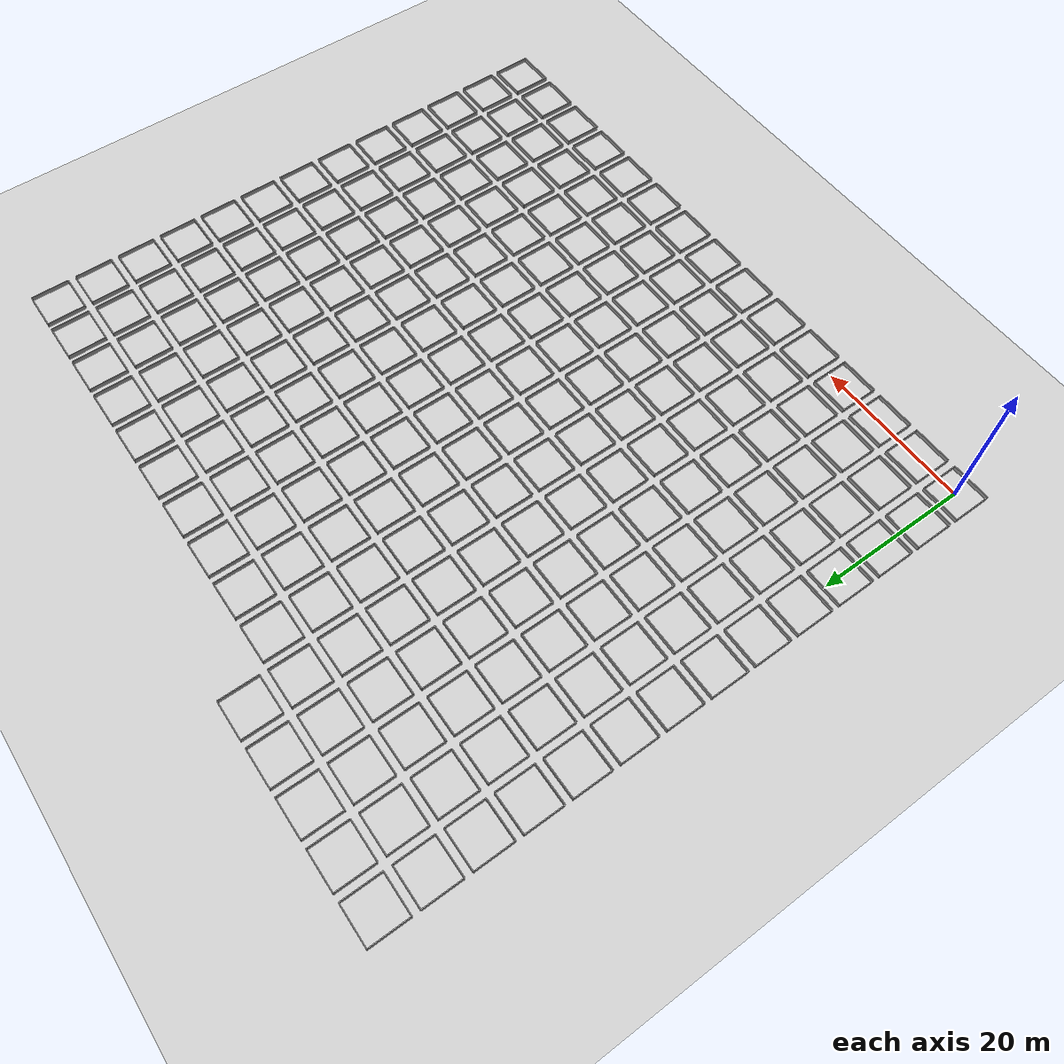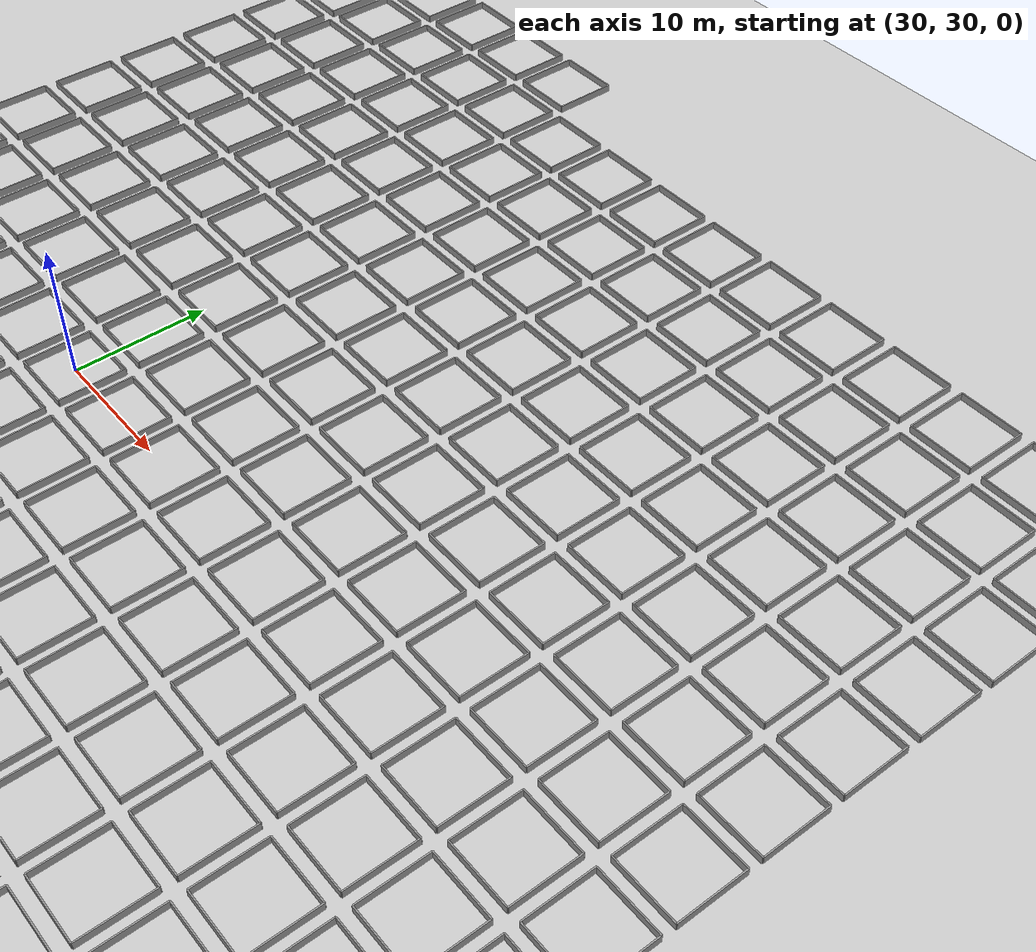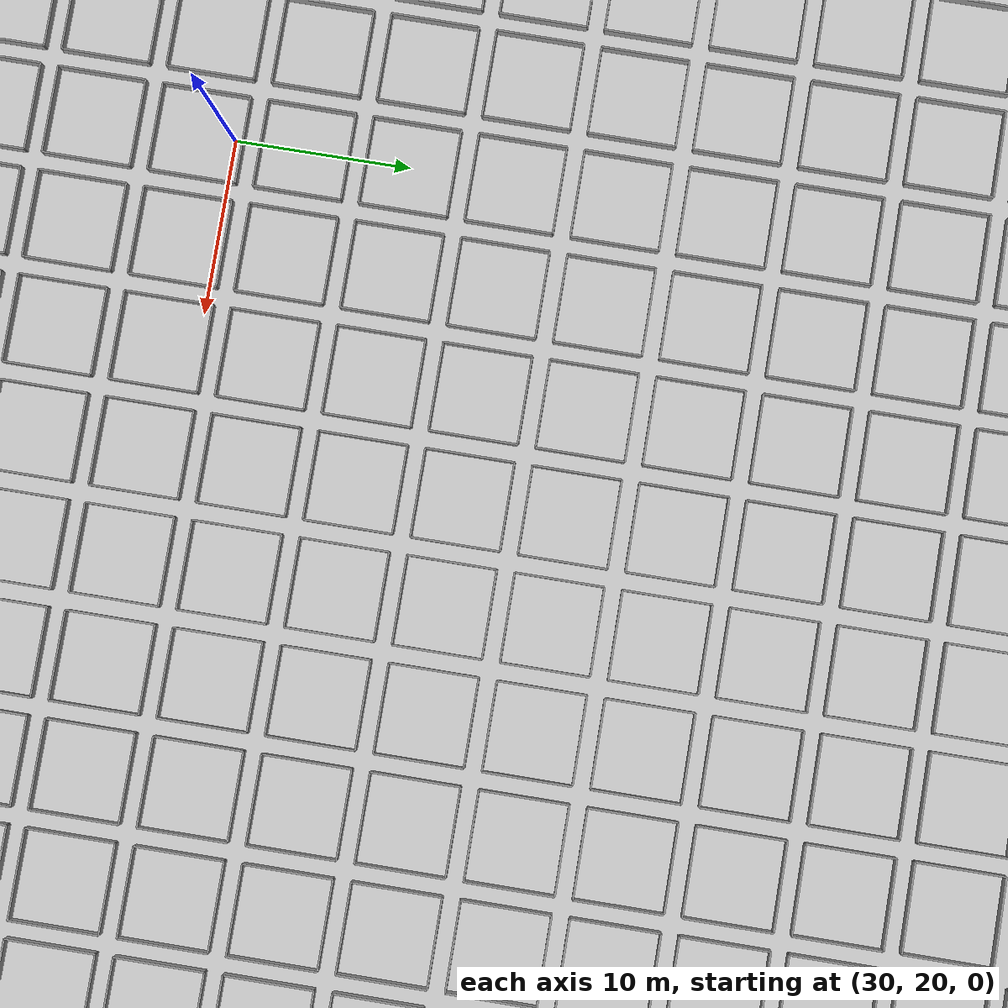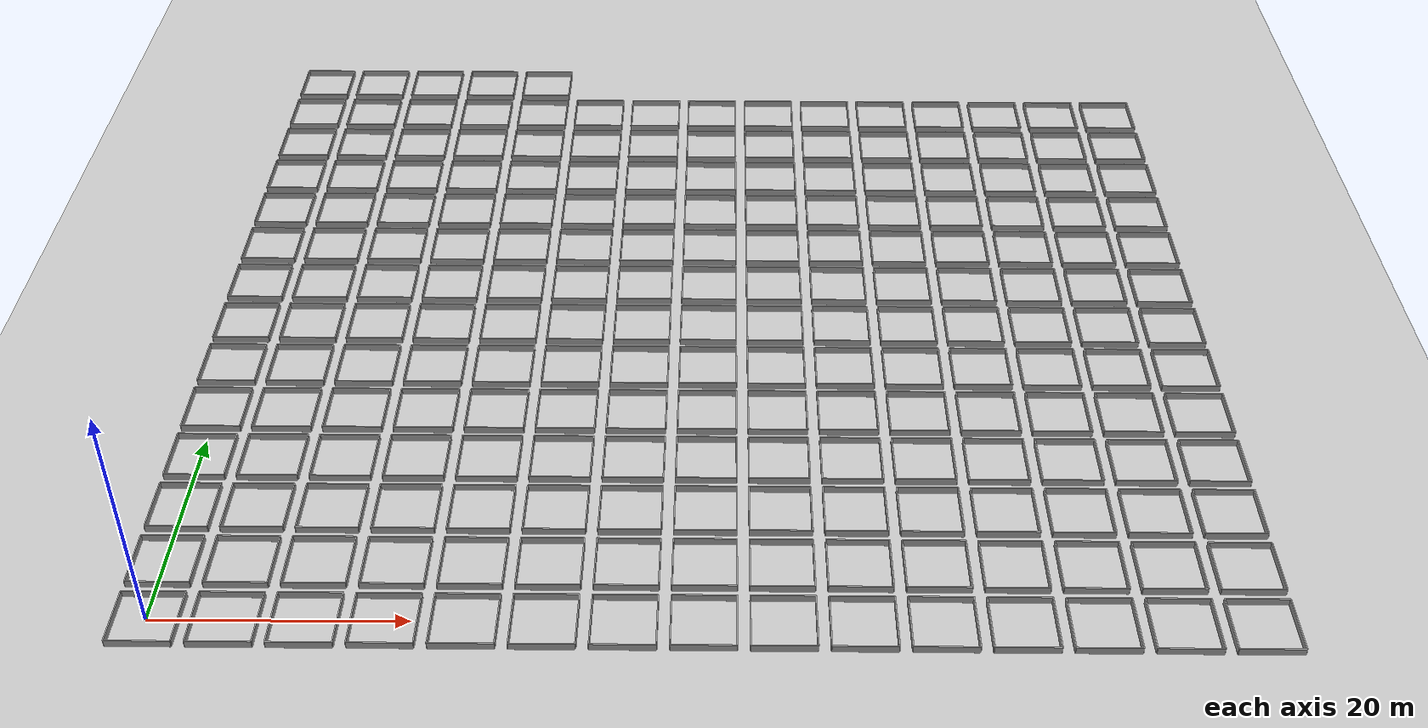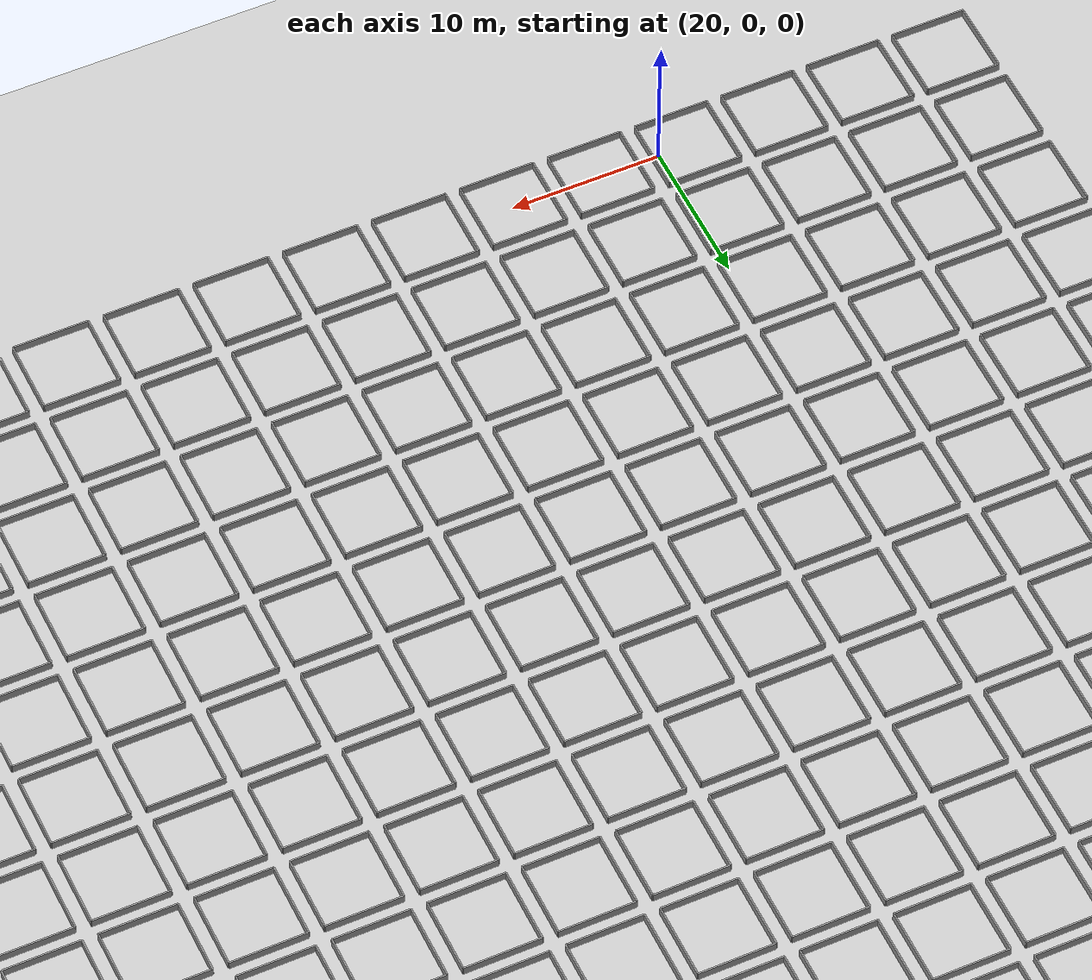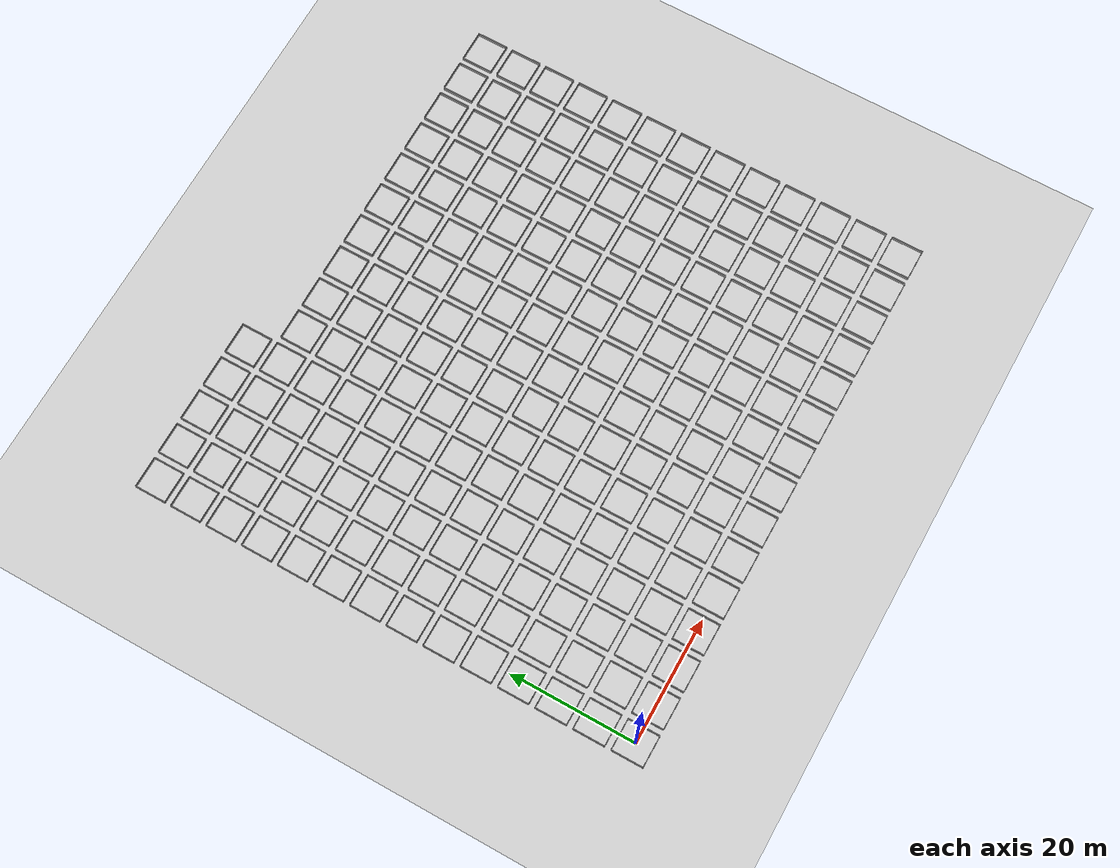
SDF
<sdf version='1.7'>
        <world name='default'>
            <include>
                <uri>model://sun</uri>
            </include>
            <model name='ground_plane'>
                <static>true</static>
                <link name='link'>
                    <collision name='collision'>
                        <geometry>
                            <plane>
                                <normal>0 0 1</normal>
                                <size>100 100</size>
                            </plane>
                        </geometry>
                    </collision>
                    <visual name='visual'>
                        <geometry>
                            <plane>
                                <normal>0 0 1</normal>
                                <size>100 100</size>
                            </plane>
                        </geometry>
                        <material>
                            <script>
                                <uri>file://media/materials/scripts/gazebo.material</uri>
                                <name>Gazebo/Grey</name>
                            </script>
                        </material>
                    </visual>
                </link>
            </model>

    <model name='wall_0_north'>
        <static>true</static>
        <pose>0 2.5 0 0 0 0</pose>
        <link name='link'>
            <collision name='collision'>
                <geometry>
                    <box><size>5 0.1 1</size></box>
                </geometry>
            </collision>
            <visual name='visual'>
                <geometry>
                    <box><size>5 0.1 1</size></box>
                </geometry>
                <material>
                    <script>
                        <uri>file://media/materials/scripts/gazebo.material</uri>
                        <name>Gazebo/Grey</name>
                    </script>
                </material>
            </visual>
        </link>
    </model>

    <model name='wall_0_south'>
        <static>true</static>
        <pose>0 -2.5 0 0 0 0</pose>
        <link name='link'>
            <collision name='collision'>
                <geometry>
                    <box><size>5 0.1 1</size></box>
                </geometry>
            </collision>
            <visual name='visual'>
                <geometry>
                    <box><size>5 0.1 1</size></box>
                </geometry>
                <material>
                    <script>
                        <uri>file://media/materials/scripts/gazebo.material</uri>
                        <name>Gazebo/Grey</name>
                    </script>
                </material>
            </visual>
        </link>
    </model>

    <model name='wall_0_east'>
        <static>true</static>
        <pose>2.5 0 0 0 0 1.5707</pose>
        <link name='link'>
            <collision name='collision'>
                <geometry>
                    <box><size>5 0.1 1</size></box>
                </geometry>
            </collision>
            <visual name='visual'>
                <geometry>
                    <box><size>5 0.1 1</size></box>
                </geometry>
                <material>
                    <script>
                        <uri>file://media/materials/scripts/gazebo.material</uri>
                        <name>Gazebo/Grey</name>
                    </script>
                </material>
            </visual>
        </link>
    </model>

    <model name='wall_0_west'>
        <static>true</static>
        <pose>-2.5 0 0 0 0 1.5707</pose>
        <link name='link'>
            <collision name='collision'>
                <geometry>
                    <box><size>5 0.1 1</size></box>
                </geometry>
            </collision>
            <visual name='visual'>
                <geometry>
                    <box><size>5 0.1 1</size></box>
                </geometry>
                <material>
                    <script>
                        <uri>file://media/materials/scripts/gazebo.material</uri>
                        <name>Gazebo/Grey</name>
                    </script>
                </material>
            </visual>
        </link>
    </model>

    <model name='wall_1_north'>
        <static>true</static>
        <pose>6 2.5 0 0 0 0</pose>
        <link name='link'>
            <collision name='collision'>
                <geometry>
                    <box><size>5 0.1 1</size></box>
                </geometry>
            </collision>
            <visual name='visual'>
                <geometry>
                    <box><size>5 0.1 1</size></box>
                </geometry>
                <material>
                    <script>
                        <uri>file://media/materials/scripts/gazebo.material</uri>
                        <name>Gazebo/Grey</name>
                    </script>
                </material>
            </visual>
        </link>
    </model>

    <model name='wall_1_south'>
        <static>true</static>
        <pose>6 -2.5 0 0 0 0</pose>
        <link name='link'>
            <collision name='collision'>
                <geometry>
                    <box><size>5 0.1 1</size></box>
                </geometry>
            </collision>
            <visual name='visual'>
                <geometry>
                    <box><size>5 0.1 1</size></box>
                </geometry>
                <material>
                    <script>
                        <uri>file://media/materials/scripts/gazebo.material</uri>
                        <name>Gazebo/Grey</name>
                    </script>
                </material>
            </visual>
        </link>
    </model>

    <model name='wall_1_east'>
        <static>true</static>
        <pose>8.5 0 0 0 0 1.5707</pose>
        <link name='link'>
            <collision name='collision'>
                <geometry>
                    <box><size>5 0.1 1</size></box>
                </geometry>
            </collision>
            <visual name='visual'>
                <geometry>
                    <box><size>5 0.1 1</size></box>
                </geometry>
                <material>
                    <script>
                        <uri>file://media/materials/scripts/gazebo.material</uri>
                        <name>Gazebo/Grey</name>
                    </script>
                </material>
            </visual>
        </link>
    </model>

    <model name='wall_1_west'>
        <static>true</static>
        <pose>3.5 0 0 0 0 1.5707</pose>
        <link name='link'>
            <collision name='collision'>
                <geometry>
                    <box><size>5 0.1 1</size></box>
                </geometry>
            </collision>
            <visual name='visual'>
                <geometry>
                    <box><size>5 0.1 1</size></box>
                </geometry>
                <material>
                    <script>
                        <uri>file://media/materials/scripts/gazebo.material</uri>
                        <name>Gazebo/Grey</name>
                    </script>
                </material>
            </visual>
        </link>
    </model>

    <model name='wall_2_north'>
        <static>true</static>
        <pose>12 2.5 0 0 0 0</pose>
        <link name='link'>
            <collision name='collision'>
                <geometry>
                    <box><size>5 0.1 1</size></box>
                </geometry>
            </collision>
            <visual name='visual'>
                <geometry>
                    <box><size>5 0.1 1</size></box>
                </geometry>
                <material>
                    <script>
                        <uri>file://media/materials/scripts/gazebo.material</uri>
                        <name>Gazebo/Grey</name>
                    </script>
                </material>
            </visual>
        </link>
    </model>

    <model name='wall_2_south'>
        <static>true</static>
        <pose>12 -2.5 0 0 0 0</pose>
        <link name='link'>
            <collision name='collision'>
                <geometry>
                    <box><size>5 0.1 1</size></box>
                </geometry>
            </collision>
            <visual name='visual'>
                <geometry>
                    <box><size>5 0.1 1</size></box>
                </geometry>
                <material>
                    <script>
                        <uri>file://media/materials/scripts/gazebo.material</uri>
                        <name>Gazebo/Grey</name>
                    </script>
                </material>
            </visual>
        </link>
    </model>

    <model name='wall_2_east'>
        <static>true</static>
        <pose>14.5 0 0 0 0 1.5707</pose>
        <link name='link'>
            <collision name='collision'>
                <geometry>
                    <box><size>5 0.1 1</size></box>
                </geometry>
            </collision>
            <visual name='visual'>
                <geometry>
                    <box><size>5 0.1 1</size></box>
                </geometry>
                <material>
                    <script>
                        <uri>file://media/materials/scripts/gazebo.material</uri>
                        <name>Gazebo/Grey</name>
                    </script>
                </material>
            </visual>
        </link>
    </model>

    <model name='wall_2_west'>
        <static>true</static>
        <pose>9.5 0 0 0 0 1.5707</pose>
        <link name='link'>
            <collision name='collision'>
                <geometry>
                    <box><size>5 0.1 1</size></box>
                </geometry>
            </collision>
            <visual name='visual'>
                <geometry>
                    <box><size>5 0.1 1</size></box>
                </geometry>
                <material>
                    <script>
                        <uri>file://media/materials/scripts/gazebo.material</uri>
                        <name>Gazebo/Grey</name>
                    </script>
                </material>
            </visual>
        </link>
    </model>

    <model name='wall_3_north'>
        <static>true</static>
        <pose>18 2.5 0 0 0 0</pose>
        <link name='link'>
            <collision name='collision'>
                <geometry>
                    <box><size>5 0.1 1</size></box>
                </geometry>
            </collision>
            <visual name='visual'>
                <geometry>
                    <box><size>5 0.1 1</size></box>
                </geometry>
                <material>
                    <script>
                        <uri>file://media/materials/scripts/gazebo.material</uri>
                        <name>Gazebo/Grey</name>
                    </script>
                </material>
            </visual>
        </link>
    </model>

    <model name='wall_3_south'>
        <static>true</static>
        <pose>18 -2.5 0 0 0 0</pose>
        <link name='link'>
            <collision name='collision'>
                <geometry>
                    <box><size>5 0.1 1</size></box>
                </geometry>
            </collision>
            <visual name='visual'>
                <geometry>
                    <box><size>5 0.1 1</size></box>
                </geometry>
                <material>
                    <script>
                        <uri>file://media/materials/scripts/gazebo.material</uri>
                        <name>Gazebo/Grey</name>
                    </script>
                </material>
            </visual>
        </link>
    </model>

    <model name='wall_3_east'>
        <static>true</static>
        <pose>20.5 0 0 0 0 1.5707</pose>
        <link name='link'>
            <collision name='collision'>
                <geometry>
                    <box><size>5 0.1 1</size></box>
                </geometry>
            </collision>
            <visual name='visual'>
                <geometry>
                    <box><size>5 0.1 1</size></box>
                </geometry>
                <material>
                    <script>
                        <uri>file://media/materials/scripts/gazebo.material</uri>
                        <name>Gazebo/Grey</name>
                    </script>
                </material>
            </visual>
        </link>
    </model>

    <model name='wall_3_west'>
        <static>true</static>
        <pose>15.5 0 0 0 0 1.5707</pose>
        <link name='link'>
            <collision name='collision'>
                <geometry>
                    <box><size>5 0.1 1</size></box>
                </geometry>
            </collision>
            <visual name='visual'>
                <geometry>
                    <box><size>5 0.1 1</size></box>
                </geometry>
                <material>
                    <script>
                        <uri>file://media/materials/scripts/gazebo.material</uri>
                        <name>Gazebo/Grey</name>
                    </script>
                </material>
            </visual>
        </link>
    </model>

    <model name='wall_4_north'>
        <static>true</static>
        <pose>24 2.5 0 0 0 0</pose>
        <link name='link'>
            <collision name='collision'>
                <geometry>
                    <box><size>5 0.1 1</size></box>
                </geometry>
            </collision>
            <visual name='visual'>
                <geometry>
                    <box><size>5 0.1 1</size></box>
                </geometry>
                <material>
                    <script>
                        <uri>file://media/materials/scripts/gazebo.material</uri>
                        <name>Gazebo/Grey</name>
                    </script>
                </material>
            </visual>
        </link>
    </model>

    <model name='wall_4_south'>
        <static>true</static>
        <pose>24 -2.5 0 0 0 0</pose>
        <link name='link'>
            <collision name='collision'>
                <geometry>
                    <box><size>5 0.1 1</size></box>
                </geometry>
            </collision>
            <visual name='visual'>
                <geometry>
                    <box><size>5 0.1 1</size></box>
                </geometry>
                <material>
                    <script>
                        <uri>file://media/materials/scripts/gazebo.material</uri>
                        <name>Gazebo/Grey</name>
                    </script>
                </material>
            </visual>
        </link>
    </model>

    <model name='wall_4_east'>
        <static>true</static>
        <pose>26.5 0 0 0 0 1.5707</pose>
        <link name='link'>
            <collision name='collision'>
                <geometry>
                    <box><size>5 0.1 1</size></box>
                </geometry>
            </collision>
            <visual name='visual'>
                <geometry>
                    <box><size>5 0.1 1</size></box>
                </geometry>
                <material>
                    <script>
                        <uri>file://media/materials/scripts/gazebo.material</uri>
                        <name>Gazebo/Grey</name>
                    </script>
                </material>
            </visual>
        </link>
    </model>

    <model name='wall_4_west'>
        <static>true</static>
        <pose>21.5 0 0 0 0 1.5707</pose>
        <link name='link'>
            <collision name='collision'>
                <geometry>
                    <box><size>5 0.1 1</size></box>
                </geometry>
            </collision>
            <visual name='visual'>
                <geometry>
                    <box><size>5 0.1 1</size></box>
                </geometry>
                <material>
                    <script>
                        <uri>file://media/materials/scripts/gazebo.material</uri>
                        <name>Gazebo/Grey</name>
                    </script>
                </material>
            </visual>
        </link>
    </model>

    <model name='wall_5_north'>
        <static>true</static>
        <pose>30 2.5 0 0 0 0</pose>
        <link name='link'>
            <collision name='collision'>
                <geometry>
                    <box><size>5 0.1 1</size></box>
                </geometry>
            </collision>
            <visual name='visual'>
                <geometry>
                    <box><size>5 0.1 1</size></box>
                </geometry>
                <material>
                    <script>
                        <uri>file://media/materials/scripts/gazebo.material</uri>
                        <name>Gazebo/Grey</name>
                    </script>
                </material>
            </visual>
        </link>
    </model>

    <model name='wall_5_south'>
        <static>true</static>
        <pose>30 -2.5 0 0 0 0</pose>
        <link name='link'>
            <collision name='collision'>
                <geometry>
                    <box><size>5 0.1 1</size></box>
                </geometry>
            </collision>
            <visual name='visual'>
                <geometry>
                    <box><size>5 0.1 1</size></box>
                </geometry>
                <material>
                    <script>
                        <uri>file://media/materials/scripts/gazebo.material</uri>
                        <name>Gazebo/Grey</name>
                    </script>
                </material>
            </visual>
        </link>
    </model>

    <model name='wall_5_east'>
        <static>true</static>
        <pose>32.5 0 0 0 0 1.5707</pose>
        <link name='link'>
            <collision name='collision'>
                <geometry>
                    <box><size>5 0.1 1</size></box>
                </geometry>
            </collision>
            <visual name='visual'>
                <geometry>
                    <box><size>5 0.1 1</size></box>
                </geometry>
                <material>
                    <script>
                        <uri>file://media/materials/scripts/gazebo.material</uri>
                        <name>Gazebo/Grey</name>
                    </script>
                </material>
            </visual>
        </link>
    </model>

    <model name='wall_5_west'>
        <static>true</static>
        <pose>27.5 0 0 0 0 1.5707</pose>
        <link name='link'>
            <collision name='collision'>
                <geometry>
                    <box><size>5 0.1 1</size></box>
                </geometry>
            </collision>
            <visual name='visual'>
                <geometry>
                    <box><size>5 0.1 1</size></box>
                </geometry>
                <material>
                    <script>
                        <uri>file://media/materials/scripts/gazebo.material</uri>
                        <name>Gazebo/Grey</name>
                    </script>
                </material>
            </visual>
        </link>
    </model>

    <model name='wall_6_north'>
        <static>true</static>
        <pose>36 2.5 0 0 0 0</pose>
        <link name='link'>
            <collision name='collision'>
                <geometry>
                    <box><size>5 0.1 1</size></box>
                </geometry>
            </collision>
            <visual name='visual'>
                <geometry>
                    <box><size>5 0.1 1</size></box>
                </geometry>
                <material>
                    <script>
                        <uri>file://media/materials/scripts/gazebo.material</uri>
                        <name>Gazebo/Grey</name>
                    </script>
                </material>
            </visual>
        </link>
    </model>

    <model name='wall_6_south'>
        <static>true</static>
        <pose>36 -2.5 0 0 0 0</pose>
        <link name='link'>
            <collision name='collision'>
                <geometry>
                    <box><size>5 0.1 1</size></box>
                </geometry>
            </collision>
            <visual name='visual'>
                <geometry>
                    <box><size>5 0.1 1</size></box>
                </geometry>
                <material>
                    <script>
                        <uri>file://media/materials/scripts/gazebo.material</uri>
                        <name>Gazebo/Grey</name>
                    </script>
                </material>
            </visual>
        </link>
    </model>

    <model name='wall_6_east'>
        <static>true</static>
        <pose>38.5 0 0 0 0 1.5707</pose>
        <link name='link'>
            <collision name='collision'>
                <geometry>
                    <box><size>5 0.1 1</size></box>
                </geometry>
            </collision>
            <visual name='visual'>
                <geometry>
                    <box><size>5 0.1 1</size></box>
                </geometry>
                <material>
                    <script>
                        <uri>file://media/materials/scripts/gazebo.material</uri>
                        <name>Gazebo/Grey</name>
                    </script>
                </material>
            </visual>
        </link>
    </model>

    <model name='wall_6_west'>
        <static>true</static>
        <pose>33.5 0 0 0 0 1.5707</pose>
        <link name='link'>
            <collision name='collision'>
                <geometry>
                    <box><size>5 0.1 1</size></box>
                </geometry>
            </collision>
            <visual name='visual'>
                <geometry>
                    <box><size>5 0.1 1</size></box>
                </geometry>
                <material>
                    <script>
                        <uri>file://media/materials/scripts/gazebo.material</uri>
                        <name>Gazebo/Grey</name>
                    </script>
                </material>
            </visual>
        </link>
    </model>

    <model name='wall_7_north'>
        <static>true</static>
        <pose>42 2.5 0 0 0 0</pose>
        <link name='link'>
            <collision name='collision'>
                <geometry>
                    <box><size>5 0.1 1</size></box>
                </geometry>
            </collision>
            <visual name='visual'>
                <geometry>
                    <box><size>5 0.1 1</size></box>
                </geometry>
                <material>
                    <script>
                        <uri>file://media/materials/scripts/gazebo.material</uri>
                        <name>Gazebo/Grey</name>
                    </script>
                </material>
            </visual>
        </link>
    </model>

    <model name='wall_7_south'>
        <static>true</static>
        <pose>42 -2.5 0 0 0 0</pose>
        <link name='link'>
            <collision name='collision'>
                <geometry>
                    <box><size>5 0.1 1</size></box>
                </geometry>
            </collision>
            <visual name='visual'>
                <geometry>
                    <box><size>5 0.1 1</size></box>
                </geometry>
                <material>
                    <script>
                        <uri>file://media/materials/scripts/gazebo.material</uri>
                        <name>Gazebo/Grey</name>
                    </script>
                </material>
            </visual>
        </link>
    </model>

    <model name='wall_7_east'>
        <static>true</static>
        <pose>44.5 0 0 0 0 1.5707</pose>
        <link name='link'>
            <collision name='collision'>
                <geometry>
                    <box><size>5 0.1 1</size></box>
                </geometry>
            </collision>
            <visual name='visual'>
                <geometry>
                    <box><size>5 0.1 1</size></box>
                </geometry>
                <material>
                    <script>
                        <uri>file://media/materials/scripts/gazebo.material</uri>
                        <name>Gazebo/Grey</name>
                    </script>
                </material>
            </visual>
        </link>
    </model>

    <model name='wall_7_west'>
        <static>true</static>
        <pose>39.5 0 0 0 0 1.5707</pose>
        <link name='link'>
            <collision name='collision'>
                <geometry>
                    <box><size>5 0.1 1</size></box>
                </geometry>
            </collision>
            <visual name='visual'>
                <geometry>
                    <box><size>5 0.1 1</size></box>
                </geometry>
                <material>
                    <script>
                        <uri>file://media/materials/scripts/gazebo.material</uri>
                        <name>Gazebo/Grey</name>
                    </script>
                </material>
            </visual>
        </link>
    </model>

    <model name='wall_8_north'>
        <static>true</static>
        <pose>48 2.5 0 0 0 0</pose>
        <link name='link'>
            <collision name='collision'>
                <geometry>
                    <box><size>5 0.1 1</size></box>
                </geometry>
            </collision>
            <visual name='visual'>
                <geometry>
                    <box><size>5 0.1 1</size></box>
                </geometry>
                <material>
                    <script>
                        <uri>file://media/materials/scripts/gazebo.material</uri>
                        <name>Gazebo/Grey</name>
                    </script>
                </material>
            </visual>
        </link>
    </model>

    <model name='wall_8_south'>
        <static>true</static>
        <pose>48 -2.5 0 0 0 0</pose>
        <link name='link'>
            <collision name='collision'>
                <geometry>
                    <box><size>5 0.1 1</size></box>
                </geometry>
            </collision>
            <visual name='visual'>
                <geometry>
                    <box><size>5 0.1 1</size></box>
                </geometry>
                <material>
                    <script>
                        <uri>file://media/materials/scripts/gazebo.material</uri>
                        <name>Gazebo/Grey</name>
                    </script>
                </material>
            </visual>
        </link>
    </model>

    <model name='wall_8_east'>
        <static>true</static>
        <pose>50.5 0 0 0 0 1.5707</pose>
        <link name='link'>
            <collision name='collision'>
                <geometry>
                    <box><size>5 0.1 1</size></box>
                </geometry>
            </collision>
            <visual name='visual'>
                <geometry>
                    <box><size>5 0.1 1</size></box>
                </geometry>
                <material>
                    <script>
                        <uri>file://media/materials/scripts/gazebo.material</uri>
                        <name>Gazebo/Grey</name>
                    </script>
                </material>
            </visual>
        </link>
    </model>

    <model name='wall_8_west'>
        <static>true</static>
        <pose>45.5 0 0 0 0 1.5707</pose>
        <link name='link'>
            <collision name='collision'>
                <geometry>
                    <box><size>5 0.1 1</size></box>
                </geometry>
            </collision>
            <visual name='visual'>
                <geometry>
                    <box><size>5 0.1 1</size></box>
                </geometry>
                <material>
                    <script>
                        <uri>file://media/materials/scripts/gazebo.material</uri>
                        <name>Gazebo/Grey</name>
                    </script>
                </material>
            </visual>
        </link>
    </model>

    <model name='wall_9_north'>
        <static>true</static>
        <pose>54 2.5 0 0 0 0</pose>
        <link name='link'>
            <collision name='collision'>
                <geometry>
                    <box><size>5 0.1 1</size></box>
                </geometry>
            </collision>
            <visual name='visual'>
                <geometry>
                    <box><size>5 0.1 1</size></box>
                </geometry>
                <material>
                    <script>
                        <uri>file://media/materials/scripts/gazebo.material</uri>
                        <name>Gazebo/Grey</name>
                    </script>
                </material>
            </visual>
        </link>
    </model>

    <model name='wall_9_south'>
        <static>true</static>
        <pose>54 -2.5 0 0 0 0</pose>
        <link name='link'>
            <collision name='collision'>
                <geometry>
                    <box><size>5 0.1 1</size></box>
                </geometry>
            </collision>
            <visual name='visual'>
                <geometry>
                    <box><size>5 0.1 1</size></box>
                </geometry>
                <material>
                    <script>
                        <uri>file://media/materials/scripts/gazebo.material</uri>
                        <name>Gazebo/Grey</name>
                    </script>
                </material>
            </visual>
        </link>
    </model>

    <model name='wall_9_east'>
        <static>true</static>
        <pose>56.5 0 0 0 0 1.5707</pose>
        <link name='link'>
            <collision name='collision'>
                <geometry>
                    <box><size>5 0.1 1</size></box>
                </geometry>
            </collision>
            <visual name='visual'>
                <geometry>
                    <box><size>5 0.1 1</size></box>
                </geometry>
                <material>
                    <script>
                        <uri>file://media/materials/scripts/gazebo.material</uri>
                        <name>Gazebo/Grey</name>
                    </script>
                </material>
            </visual>
        </link>
    </model>

    <model name='wall_9_west'>
        <static>true</static>
        <pose>51.5 0 0 0 0 1.5707</pose>
        <link name='link'>
            <collision name='collision'>
                <geometry>
                    <box><size>5 0.1 1</size></box>
                </geometry>
            </collision>
            <visual name='visual'>
                <geometry>
                    <box><size>5 0.1 1</size></box>
                </geometry>
                <material>
                    <script>
                        <uri>file://media/materials/scripts/gazebo.material</uri>
                        <name>Gazebo/Grey</name>
                    </script>
                </material>
            </visual>
        </link>
    </model>

    <model name='wall_10_north'>
        <static>true</static>
        <pose>60 2.5 0 0 0 0</pose>
        <link name='link'>
            <collision name='collision'>
                <geometry>
                    <box><size>5 0.1 1</size></box>
                </geometry>
            </collision>
            <visual name='visual'>
                <geometry>
                    <box><size>5 0.1 1</size></box>
                </geometry>
                <material>
                    <script>
                        <uri>file://media/materials/scripts/gazebo.material</uri>
                        <name>Gazebo/Grey</name>
                    </script>
                </material>
            </visual>
        </link>
    </model>

    <model name='wall_10_south'>
        <static>true</static>
        <pose>60 -2.5 0 0 0 0</pose>
        <link name='link'>
            <collision name='collision'>
                <geometry>
                    <box><size>5 0.1 1</size></box>
                </geometry>
            </collision>
            <visual name='visual'>
                <geometry>
                    <box><size>5 0.1 1</size></box>
                </geometry>
                <material>
                    <script>
                        <uri>file://media/materials/scripts/gazebo.material</uri>
                        <name>Gazebo/Grey</name>
                    </script>
                </material>
            </visual>
        </link>
    </model>

    <model name='wall_10_east'>
        <static>true</static>
        <pose>62.5 0 0 0 0 1.5707</pose>
        <link name='link'>
            <collision name='collision'>
                <geometry>
                    <box><size>5 0.1 1</size></box>
                </geometry>
            </collision>
            <visual name='visual'>
                <geometry>
                    <box><size>5 0.1 1</size></box>
                </geometry>
                <material>
                    <script>
                        <uri>file://media/materials/scripts/gazebo.material</uri>
                        <name>Gazebo/Grey</name>
                    </script>
                </material>
            </visual>
        </link>
    </model>

    <model name='wall_10_west'>
        <static>true</static>
        <pose>57.5 0 0 0 0 1.5707</pose>
        <link name='link'>
            <collision name='collision'>
                <geometry>
                    <box><size>5 0.1 1</size></box>
                </geometry>
            </collision>
            <visual name='visual'>
                <geometry>
                    <box><size>5 0.1 1</size></box>
                </geometry>
                <material>
                    <script>
                        <uri>file://media/materials/scripts/gazebo.material</uri>
                        <name>Gazebo/Grey</name>
                    </script>
                </material>
            </visual>
        </link>
    </model>

    <model name='wall_11_north'>
        <static>true</static>
        <pose>66 2.5 0 0 0 0</pose>
        <link name='link'>
            <collision name='collision'>
                <geometry>
                    <box><size>5 0.1 1</size></box>
                </geometry>
            </collision>
            <visual name='visual'>
                <geometry>
                    <box><size>5 0.1 1</size></box>
                </geometry>
                <material>
                    <script>
                        <uri>file://media/materials/scripts/gazebo.material</uri>
                        <name>Gazebo/Grey</name>
                    </script>
                </material>
            </visual>
        </link>
    </model>

    <model name='wall_11_south'>
        <static>true</static>
        <pose>66 -2.5 0 0 0 0</pose>
        <link name='link'>
            <collision name='collision'>
                <geometry>
                    <box><size>5 0.1 1</size></box>
                </geometry>
            </collision>
            <visual name='visual'>
                <geometry>
                    <box><size>5 0.1 1</size></box>
                </geometry>
                <material>
                    <script>
                        <uri>file://media/materials/scripts/gazebo.material</uri>
                        <name>Gazebo/Grey</name>
                    </script>
                </material>
            </visual>
        </link>
    </model>

    <model name='wall_11_east'>
        <static>true</static>
        <pose>68.5 0 0 0 0 1.5707</pose>
        <link name='link'>
            <collision name='collision'>
                <geometry>
                    <box><size>5 0.1 1</size></box>
                </geometry>
            </collision>
            <visual name='visual'>
                <geometry>
                    <box><size>5 0.1 1</size></box>
                </geometry>
                <material>
                    <script>
                        <uri>file://media/materials/scripts/gazebo.material</uri>
                        <name>Gazebo/Grey</name>
                    </script>
                </material>
            </visual>
        </link>
    </model>

    <model name='wall_11_west'>
        <static>true</static>
        <pose>63.5 0 0 0 0 1.5707</pose>
        <link name='link'>
            <collision name='collision'>
                <geometry>
                    <box><size>5 0.1 1</size></box>
                </geometry>
            </collision>
            <visual name='visual'>
                <geometry>
                    <box><size>5 0.1 1</size></box>
                </geometry>
                <material>
                    <script>
                        <uri>file://media/materials/scripts/gazebo.material</uri>
                        <name>Gazebo/Grey</name>
                    </script>
                </material>
            </visual>
        </link>
    </model>

    <model name='wall_12_north'>
        <static>true</static>
        <pose>72 2.5 0 0 0 0</pose>
        <link name='link'>
            <collision name='collision'>
                <geometry>
                    <box><size>5 0.1 1</size></box>
                </geometry>
            </collision>
            <visual name='visual'>
                <geometry>
                    <box><size>5 0.1 1</size></box>
                </geometry>
                <material>
                    <script>
                        <uri>file://media/materials/scripts/gazebo.material</uri>
                        <name>Gazebo/Grey</name>
                    </script>
                </material>
            </visual>
        </link>
    </model>

    <model name='wall_12_south'>
        <static>true</static>
        <pose>72 -2.5 0 0 0 0</pose>
        <link name='link'>
            <collision name='collision'>
                <geometry>
                    <box><size>5 0.1 1</size></box>
                </geometry>
            </collision>
            <visual name='visual'>
                <geometry>
                    <box><size>5 0.1 1</size></box>
                </geometry>
                <material>
                    <script>
                        <uri>file://media/materials/scripts/gazebo.material</uri>
                        <name>Gazebo/Grey</name>
                    </script>
                </material>
            </visual>
        </link>
    </model>

    <model name='wall_12_east'>
        <static>true</static>
        <pose>74.5 0 0 0 0 1.5707</pose>
        <link name='link'>
            <collision name='collision'>
                <geometry>
                    <box><size>5 0.1 1</size></box>
                </geometry>
            </collision>
            <visual name='visual'>
                <geometry>
                    <box><size>5 0.1 1</size></box>
                </geometry>
                <material>
                    <script>
                        <uri>file://media/materials/scripts/gazebo.material</uri>
                        <name>Gazebo/Grey</name>
                    </script>
                </material>
            </visual>
        </link>
    </model>

    <model name='wall_12_west'>
        <static>true</static>
        <pose>69.5 0 0 0 0 1.5707</pose>
        <link name='link'>
            <collision name='collision'>
                <geometry>
                    <box><size>5 0.1 1</size></box>
                </geometry>
            </collision>
            <visual name='visual'>
                <geometry>
                    <box><size>5 0.1 1</size></box>
                </geometry>
                <material>
                    <script>
                        <uri>file://media/materials/scripts/gazebo.material</uri>
                        <name>Gazebo/Grey</name>
                    </script>
                </material>
            </visual>
        </link>
    </model>

    <model name='wall_13_north'>
        <static>true</static>
        <pose>78 2.5 0 0 0 0</pose>
        <link name='link'>
            <collision name='collision'>
                <geometry>
                    <box><size>5 0.1 1</size></box>
                </geometry>
            </collision>
            <visual name='visual'>
                <geometry>
                    <box><size>5 0.1 1</size></box>
                </geometry>
                <material>
                    <script>
                        <uri>file://media/materials/scripts/gazebo.material</uri>
                        <name>Gazebo/Grey</name>
                    </script>
                </material>
            </visual>
        </link>
    </model>

    <model name='wall_13_south'>
        <static>true</static>
        <pose>78 -2.5 0 0 0 0</pose>
        <link name='link'>
            <collision name='collision'>
                <geometry>
                    <box><size>5 0.1 1</size></box>
                </geometry>
            </collision>
            <visual name='visual'>
                <geometry>
                    <box><size>5 0.1 1</size></box>
                </geometry>
                <material>
                    <script>
                        <uri>file://media/materials/scripts/gazebo.material</uri>
                        <name>Gazebo/Grey</name>
                    </script>
                </material>
            </visual>
        </link>
    </model>

    <model name='wall_13_east'>
        <static>true</static>
        <pose>80.5 0 0 0 0 1.5707</pose>
        <link name='link'>
            <collision name='collision'>
                <geometry>
                    <box><size>5 0.1 1</size></box>
                </geometry>
            </collision>
            <visual name='visual'>
                <geometry>
                    <box><size>5 0.1 1</size></box>
                </geometry>
                <material>
                    <script>
                        <uri>file://media/materials/scripts/gazebo.material</uri>
                        <name>Gazebo/Grey</name>
                    </script>
                </material>
            </visual>
        </link>
    </model>

    <model name='wall_13_west'>
        <static>true</static>
        <pose>75.5 0 0 0 0 1.5707</pose>
        <link name='link'>
            <collision name='collision'>
                <geometry>
                    <box><size>5 0.1 1</size></box>
                </geometry>
            </collision>
            <visual name='visual'>
                <geometry>
                    <box><size>5 0.1 1</size></box>
                </geometry>
                <material>
                    <script>
                        <uri>file://media/materials/scripts/gazebo.material</uri>
                        <name>Gazebo/Grey</name>
                    </script>
                </material>
            </visual>
        </link>
    </model>

    <model name='wall_14_north'>
        <static>true</static>
        <pose>84 2.5 0 0 0 0</pose>
        <link name='link'>
            <collision name='collision'>
                <geometry>
                    <box><size>5 0.1 1</size></box>
                </geometry>
            </collision>
            <visual name='visual'>
                <geometry>
                    <box><size>5 0.1 1</size></box>
                </geometry>
                <material>
                    <script>
                        <uri>file://media/materials/scripts/gazebo.material</uri>
                        <name>Gazebo/Grey</name>
                    </script>
                </material>
            </visual>
        </link>
    </model>

    <model name='wall_14_south'>
        <static>true</static>
        <pose>84 -2.5 0 0 0 0</pose>
        <link name='link'>
            <collision name='collision'>
                <geometry>
                    <box><size>5 0.1 1</size></box>
                </geometry>
            </collision>
            <visual name='visual'>
                <geometry>
                    <box><size>5 0.1 1</size></box>
                </geometry>
                <material>
                    <script>
                        <uri>file://media/materials/scripts/gazebo.material</uri>
                        <name>Gazebo/Grey</name>
                    </script>
                </material>
            </visual>
        </link>
    </model>

    <model name='wall_14_east'>
        <static>true</static>
        <pose>86.5 0 0 0 0 1.5707</pose>
        <link name='link'>
            <collision name='collision'>
                <geometry>
                    <box><size>5 0.1 1</size></box>
                </geometry>
            </collision>
            <visual name='visual'>
                <geometry>
                    <box><size>5 0.1 1</size></box>
                </geometry>
                <material>
                    <script>
                        <uri>file://media/materials/scripts/gazebo.material</uri>
                        <name>Gazebo/Grey</name>
                    </script>
                </material>
            </visual>
        </link>
    </model>

    <model name='wall_14_west'>
        <static>true</static>
        <pose>81.5 0 0 0 0 1.5707</pose>
        <link name='link'>
            <collision name='collision'>
                <geometry>
                    <box><size>5 0.1 1</size></box>
                </geometry>
            </collision>
            <visual name='visual'>
                <geometry>
                    <box><size>5 0.1 1</size></box>
                </geometry>
                <material>
                    <script>
                        <uri>file://media/materials/scripts/gazebo.material</uri>
                        <name>Gazebo/Grey</name>
                    </script>
                </material>
            </visual>
        </link>
    </model>

    <model name='wall_15_north'>
        <static>true</static>
        <pose>0 8.5 0 0 0 0</pose>
        <link name='link'>
            <collision name='collision'>
                <geometry>
                    <box><size>5 0.1 1</size></box>
                </geometry>
            </collision>
            <visual name='visual'>
                <geometry>
                    <box><size>5 0.1 1</size></box>
                </geometry>
                <material>
                    <script>
                        <uri>file://media/materials/scripts/gazebo.material</uri>
                        <name>Gazebo/Grey</name>
                    </script>
                </material>
            </visual>
        </link>
    </model>

    <model name='wall_15_south'>
        <static>true</static>
        <pose>0 3.5 0 0 0 0</pose>
        <link name='link'>
            <collision name='collision'>
                <geometry>
                    <box><size>5 0.1 1</size></box>
                </geometry>
            </collision>
            <visual name='visual'>
                <geometry>
                    <box><size>5 0.1 1</size></box>
                </geometry>
                <material>
                    <script>
                        <uri>file://media/materials/scripts/gazebo.material</uri>
                        <name>Gazebo/Grey</name>
                    </script>
                </material>
            </visual>
        </link>
    </model>

    <model name='wall_15_east'>
        <static>true</static>
        <pose>2.5 6 0 0 0 1.5707</pose>
        <link name='link'>
            <collision name='collision'>
                <geometry>
                    <box><size>5 0.1 1</size></box>
                </geometry>
            </collision>
            <visual name='visual'>
                <geometry>
                    <box><size>5 0.1 1</size></box>
                </geometry>
                <material>
                    <script>
                        <uri>file://media/materials/scripts/gazebo.material</uri>
                        <name>Gazebo/Grey</name>
                    </script>
                </material>
            </visual>
        </link>
    </model>

    <model name='wall_15_west'>
        <static>true</static>
        <pose>-2.5 6 0 0 0 1.5707</pose>
        <link name='link'>
            <collision name='collision'>
                <geometry>
                    <box><size>5 0.1 1</size></box>
                </geometry>
            </collision>
            <visual name='visual'>
                <geometry>
                    <box><size>5 0.1 1</size></box>
                </geometry>
                <material>
                    <script>
                        <uri>file://media/materials/scripts/gazebo.material</uri>
                        <name>Gazebo/Grey</name>
                    </script>
                </material>
            </visual>
        </link>
    </model>

    <model name='wall_16_north'>
        <static>true</static>
        <pose>6 8.5 0 0 0 0</pose>
        <link name='link'>
            <collision name='collision'>
                <geometry>
                    <box><size>5 0.1 1</size></box>
                </geometry>
            </collision>
            <visual name='visual'>
                <geometry>
                    <box><size>5 0.1 1</size></box>
                </geometry>
                <material>
                    <script>
                        <uri>file://media/materials/scripts/gazebo.material</uri>
                        <name>Gazebo/Grey</name>
                    </script>
                </material>
            </visual>
        </link>
    </model>

    <model name='wall_16_south'>
        <static>true</static>
        <pose>6 3.5 0 0 0 0</pose>
        <link name='link'>
            <collision name='collision'>
                <geometry>
                    <box><size>5 0.1 1</size></box>
                </geometry>
            </collision>
            <visual name='visual'>
                <geometry>
                    <box><size>5 0.1 1</size></box>
                </geometry>
                <material>
                    <script>
                        <uri>file://media/materials/scripts/gazebo.material</uri>
                        <name>Gazebo/Grey</name>
                    </script>
                </material>
            </visual>
        </link>
    </model>

    <model name='wall_16_east'>
        <static>true</static>
        <pose>8.5 6 0 0 0 1.5707</pose>
        <link name='link'>
            <collision name='collision'>
                <geometry>
                    <box><size>5 0.1 1</size></box>
                </geometry>
            </collision>
            <visual name='visual'>
                <geometry>
                    <box><size>5 0.1 1</size></box>
                </geometry>
                <material>
                    <script>
                        <uri>file://media/materials/scripts/gazebo.material</uri>
                        <name>Gazebo/Grey</name>
                    </script>
                </material>
            </visual>
        </link>
    </model>

    <model name='wall_16_west'>
        <static>true</static>
        <pose>3.5 6 0 0 0 1.5707</pose>
        <link name='link'>
            <collision name='collision'>
                <geometry>
                    <box><size>5 0.1 1</size></box>
                </geometry>
            </collision>
            <visual name='visual'>
                <geometry>
                    <box><size>5 0.1 1</size></box>
                </geometry>
                <material>
                    <script>
                        <uri>file://media/materials/scripts/gazebo.material</uri>
                        <name>Gazebo/Grey</name>
                    </script>
                </material>
            </visual>
        </link>
    </model>

    <model name='wall_17_north'>
        <static>true</static>
        <pose>12 8.5 0 0 0 0</pose>
        <link name='link'>
            <collision name='collision'>
                <geometry>
                    <box><size>5 0.1 1</size></box>
                </geometry>
            </collision>
            <visual name='visual'>
                <geometry>
                    <box><size>5 0.1 1</size></box>
                </geometry>
                <material>
                    <script>
                        <uri>file://media/materials/scripts/gazebo.material</uri>
                        <name>Gazebo/Grey</name>
                    </script>
                </material>
            </visual>
        </link>
    </model>

    <model name='wall_17_south'>
        <static>true</static>
        <pose>12 3.5 0 0 0 0</pose>
        <link name='link'>
            <collision name='collision'>
                <geometry>
                    <box><size>5 0.1 1</size></box>
                </geometry>
            </collision>
            <visual name='visual'>
                <geometry>
                    <box><size>5 0.1 1</size></box>
                </geometry>
                <material>
                    <script>
                        <uri>file://media/materials/scripts/gazebo.material</uri>
                        <name>Gazebo/Grey</name>
                    </script>
                </material>
            </visual>
        </link>
    </model>

    <model name='wall_17_east'>
        <static>true</static>
        <pose>14.5 6 0 0 0 1.5707</pose>
        <link name='link'>
            <collision name='collision'>
                <geometry>
                    <box><size>5 0.1 1</size></box>
                </geometry>
            </collision>
            <visual name='visual'>
                <geometry>
                    <box><size>5 0.1 1</size></box>
                </geometry>
                <material>
                    <script>
                        <uri>file://media/materials/scripts/gazebo.material</uri>
                        <name>Gazebo/Grey</name>
                    </script>
                </material>
            </visual>
        </link>
    </model>

    <model name='wall_17_west'>
        <static>true</static>
        <pose>9.5 6 0 0 0 1.5707</pose>
        <link name='link'>
            <collision name='collision'>
                <geometry>
                    <box><size>5 0.1 1</size></box>
                </geometry>
            </collision>
            <visual name='visual'>
                <geometry>
                    <box><size>5 0.1 1</size></box>
                </geometry>
                <material>
                    <script>
                        <uri>file://media/materials/scripts/gazebo.material</uri>
                        <name>Gazebo/Grey</name>
                    </script>
                </material>
            </visual>
        </link>
    </model>

    <model name='wall_18_north'>
        <static>true</static>
        <pose>18 8.5 0 0 0 0</pose>
        <link name='link'>
            <collision name='collision'>
                <geometry>
                    <box><size>5 0.1 1</size></box>
                </geometry>
            </collision>
            <visual name='visual'>
                <geometry>
                    <box><size>5 0.1 1</size></box>
                </geometry>
                <material>
                    <script>
                        <uri>file://media/materials/scripts/gazebo.material</uri>
                        <name>Gazebo/Grey</name>
                    </script>
                </material>
            </visual>
        </link>
    </model>

    <model name='wall_18_south'>
        <static>true</static>
        <pose>18 3.5 0 0 0 0</pose>
        <link name='link'>
            <collision name='collision'>
                <geometry>
                    <box><size>5 0.1 1</size></box>
                </geometry>
            </collision>
            <visual name='visual'>
                <geometry>
                    <box><size>5 0.1 1</size></box>
                </geometry>
                <material>
                    <script>
                        <uri>file://media/materials/scripts/gazebo.material</uri>
                        <name>Gazebo/Grey</name>
                    </script>
                </material>
            </visual>
        </link>
    </model>

    <model name='wall_18_east'>
        <static>true</static>
        <pose>20.5 6 0 0 0 1.5707</pose>
        <link name='link'>
            <collision name='collision'>
                <geometry>
                    <box><size>5 0.1 1</size></box>
                </geometry>
            </collision>
            <visual name='visual'>
                <geometry>
                    <box><size>5 0.1 1</size></box>
                </geometry>
                <material>
                    <script>
                        <uri>file://media/materials/scripts/gazebo.material</uri>
                        <name>Gazebo/Grey</name>
                    </script>
                </material>
            </visual>
        </link>
    </model>

    <model name='wall_18_west'>
        <static>true</static>
        <pose>15.5 6 0 0 0 1.5707</pose>
        <link name='link'>
            <collision name='collision'>
                <geometry>
                    <box><size>5 0.1 1</size></box>
                </geometry>
            </collision>
            <visual name='visual'>
                <geometry>
                    <box><size>5 0.1 1</size></box>
                </geometry>
                <material>
                    <script>
                        <uri>file://media/materials/scripts/gazebo.material</uri>
                        <name>Gazebo/Grey</name>
                    </script>
                </material>
            </visual>
        </link>
    </model>

    <model name='wall_19_north'>
        <static>true</static>
        <pose>24 8.5 0 0 0 0</pose>
        <link name='link'>
            <collision name='collision'>
                <geometry>
                    <box><size>5 0.1 1</size></box>
                </geometry>
            </collision>
            <visual name='visual'>
                <geometry>
                    <box><size>5 0.1 1</size></box>
                </geometry>
                <material>
                    <script>
                        <uri>file://media/materials/scripts/gazebo.material</uri>
                        <name>Gazebo/Grey</name>
                    </script>
                </material>
            </visual>
        </link>
    </model>

    <model name='wall_19_south'>
        <static>true</static>
        <pose>24 3.5 0 0 0 0</pose>
        <link name='link'>
            <collision name='collision'>
                <geometry>
                    <box><size>5 0.1 1</size></box>
                </geometry>
            </collision>
            <visual name='visual'>
                <geometry>
                    <box><size>5 0.1 1</size></box>
                </geometry>
                <material>
                    <script>
                        <uri>file://media/materials/scripts/gazebo.material</uri>
                        <name>Gazebo/Grey</name>
                    </script>
                </material>
            </visual>
        </link>
    </model>

    <model name='wall_19_east'>
        <static>true</static>
        <pose>26.5 6 0 0 0 1.5707</pose>
        <link name='link'>
            <collision name='collision'>
                <geometry>
                    <box><size>5 0.1 1</size></box>
                </geometry>
            </collision>
            <visual name='visual'>
                <geometry>
                    <box><size>5 0.1 1</size></box>
                </geometry>
                <material>
                    <script>
                        <uri>file://media/materials/scripts/gazebo.material</uri>
                        <name>Gazebo/Grey</name>
                    </script>
                </material>
            </visual>
        </link>
    </model>

    <model name='wall_19_west'>
        <static>true</static>
        <pose>21.5 6 0 0 0 1.5707</pose>
        <link name='link'>
            <collision name='collision'>
                <geometry>
                    <box><size>5 0.1 1</size></box>
                </geometry>
            </collision>
            <visual name='visual'>
                <geometry>
                    <box><size>5 0.1 1</size></box>
                </geometry>
                <material>
                    <script>
                        <uri>file://media/materials/scripts/gazebo.material</uri>
                        <name>Gazebo/Grey</name>
                    </script>
                </material>
            </visual>
        </link>
    </model>

    <model name='wall_20_north'>
        <static>true</static>
        <pose>30 8.5 0 0 0 0</pose>
        <link name='link'>
            <collision name='collision'>
                <geometry>
                    <box><size>5 0.1 1</size></box>
                </geometry>
            </collision>
            <visual name='visual'>
                <geometry>
                    <box><size>5 0.1 1</size></box>
                </geometry>
                <material>
                    <script>
                        <uri>file://media/materials/scripts/gazebo.material</uri>
                        <name>Gazebo/Grey</name>
                    </script>
                </material>
            </visual>
        </link>
    </model>

    <model name='wall_20_south'>
        <static>true</static>
        <pose>30 3.5 0 0 0 0</pose>
        <link name='link'>
            <collision name='collision'>
                <geometry>
                    <box><size>5 0.1 1</size></box>
                </geometry>
            </collision>
            <visual name='visual'>
                <geometry>
                    <box><size>5 0.1 1</size></box>
                </geometry>
                <material>
                    <script>
                        <uri>file://media/materials/scripts/gazebo.material</uri>
                        <name>Gazebo/Grey</name>
                    </script>
                </material>
            </visual>
        </link>
    </model>

    <model name='wall_20_east'>
        <static>true</static>
        <pose>32.5 6 0 0 0 1.5707</pose>
        <link name='link'>
            <collision name='collision'>
                <geometry>
                    <box><size>5 0.1 1</size></box>
                </geometry>
            </collision>
            <visual name='visual'>
                <geometry>
                    <box><size>5 0.1 1</size></box>
                </geometry>
                <material>
                    <script>
                        <uri>file://media/materials/scripts/gazebo.material</uri>
                        <name>Gazebo/Grey</name>
                    </script>
                </material>
            </visual>
        </link>
    </model>

    <model name='wall_20_west'>
        <static>true</static>
        <pose>27.5 6 0 0 0 1.5707</pose>
        <link name='link'>
            <collision name='collision'>
                <geometry>
                    <box><size>5 0.1 1</size></box>
                </geometry>
            </collision>
            <visual name='visual'>
                <geometry>
                    <box><size>5 0.1 1</size></box>
                </geometry>
                <material>
                    <script>
                        <uri>file://media/materials/scripts/gazebo.material</uri>
                        <name>Gazebo/Grey</name>
                    </script>
                </material>
            </visual>
        </link>
    </model>

    <model name='wall_21_north'>
        <static>true</static>
        <pose>36 8.5 0 0 0 0</pose>
        <link name='link'>
            <collision name='collision'>
                <geometry>
                    <box><size>5 0.1 1</size></box>
                </geometry>
            </collision>
            <visual name='visual'>
                <geometry>
                    <box><size>5 0.1 1</size></box>
                </geometry>
                <material>
                    <script>
                        <uri>file://media/materials/scripts/gazebo.material</uri>
                        <name>Gazebo/Grey</name>
                    </script>
                </material>
            </visual>
        </link>
    </model>

    <model name='wall_21_south'>
        <static>true</static>
        <pose>36 3.5 0 0 0 0</pose>
        <link name='link'>
            <collision name='collision'>
                <geometry>
                    <box><size>5 0.1 1</size></box>
                </geometry>
            </collision>
            <visual name='visual'>
                <geometry>
                    <box><size>5 0.1 1</size></box>
                </geometry>
                <material>
                    <script>
                        <uri>file://media/materials/scripts/gazebo.material</uri>
                        <name>Gazebo/Grey</name>
                    </script>
                </material>
            </visual>
        </link>
    </model>

    <model name='wall_21_east'>
        <static>true</static>
        <pose>38.5 6 0 0 0 1.5707</pose>
        <link name='link'>
            <collision name='collision'>
                <geometry>
                    <box><size>5 0.1 1</size></box>
                </geometry>
            </collision>
            <visual name='visual'>
                <geometry>
                    <box><size>5 0.1 1</size></box>
                </geometry>
                <material>
                    <script>
                        <uri>file://media/materials/scripts/gazebo.material</uri>
                        <name>Gazebo/Grey</name>
                    </script>
                </material>
            </visual>
        </link>
    </model>

    <model name='wall_21_west'>
        <static>true</static>
        <pose>33.5 6 0 0 0 1.5707</pose>
        <link name='link'>
            <collision name='collision'>
                <geometry>
                    <box><size>5 0.1 1</size></box>
                </geometry>
            </collision>
            <visual name='visual'>
                <geometry>
                    <box><size>5 0.1 1</size></box>
                </geometry>
                <material>
                    <script>
                        <uri>file://media/materials/scripts/gazebo.material</uri>
                        <name>Gazebo/Grey</name>
                    </script>
                </material>
            </visual>
        </link>
    </model>

    <model name='wall_22_north'>
        <static>true</static>
        <pose>42 8.5 0 0 0 0</pose>
        <link name='link'>
            <collision name='collision'>
                <geometry>
                    <box><size>5 0.1 1</size></box>
                </geometry>
            </collision>
            <visual name='visual'>
                <geometry>
                    <box><size>5 0.1 1</size></box>
                </geometry>
                <material>
                    <script>
                        <uri>file://media/materials/scripts/gazebo.material</uri>
                        <name>Gazebo/Grey</name>
                    </script>
                </material>
            </visual>
        </link>
    </model>

    <model name='wall_22_south'>
        <static>true</static>
        <pose>42 3.5 0 0 0 0</pose>
        <link name='link'>
            <collision name='collision'>
                <geometry>
                    <box><size>5 0.1 1</size></box>
                </geometry>
            </collision>
            <visual name='visual'>
                <geometry>
                    <box><size>5 0.1 1</size></box>
                </geometry>
                <material>
                    <script>
                        <uri>file://media/materials/scripts/gazebo.material</uri>
                        <name>Gazebo/Grey</name>
                    </script>
                </material>
            </visual>
        </link>
    </model>

    <model name='wall_22_east'>
        <static>true</static>
        <pose>44.5 6 0 0 0 1.5707</pose>
        <link name='link'>
            <collision name='collision'>
                <geometry>
                    <box><size>5 0.1 1</size></box>
                </geometry>
            </collision>
            <visual name='visual'>
                <geometry>
                    <box><size>5 0.1 1</size></box>
                </geometry>
                <material>
                    <script>
                        <uri>file://media/materials/scripts/gazebo.material</uri>
                        <name>Gazebo/Grey</name>
                    </script>
                </material>
            </visual>
        </link>
    </model>

    <model name='wall_22_west'>
        <static>true</static>
        <pose>39.5 6 0 0 0 1.5707</pose>
        <link name='link'>
            <collision name='collision'>
                <geometry>
                    <box><size>5 0.1 1</size></box>
                </geometry>
            </collision>
            <visual name='visual'>
                <geometry>
                    <box><size>5 0.1 1</size></box>
                </geometry>
                <material>
                    <script>
                        <uri>file://media/materials/scripts/gazebo.material</uri>
                        <name>Gazebo/Grey</name>
                    </script>
                </material>
            </visual>
        </link>
    </model>

    <model name='wall_23_north'>
        <static>true</static>
        <pose>48 8.5 0 0 0 0</pose>
        <link name='link'>
            <collision name='collision'>
                <geometry>
                    <box><size>5 0.1 1</size></box>
                </geometry>
            </collision>
            <visual name='visual'>
                <geometry>
                    <box><size>5 0.1 1</size></box>
                </geometry>
                <material>
                    <script>
                        <uri>file://media/materials/scripts/gazebo.material</uri>
                        <name>Gazebo/Grey</name>
                    </script>
                </material>
            </visual>
        </link>
    </model>

    <model name='wall_23_south'>
        <static>true</static>
        <pose>48 3.5 0 0 0 0</pose>
        <link name='link'>
            <collision name='collision'>
                <geometry>
                    <box><size>5 0.1 1</size></box>
                </geometry>
            </collision>
            <visual name='visual'>
                <geometry>
                    <box><size>5 0.1 1</size></box>
                </geometry>
                <material>
                    <script>
                        <uri>file://media/materials/scripts/gazebo.material</uri>
                        <name>Gazebo/Grey</name>
                    </script>
                </material>
            </visual>
        </link>
    </model>

    <model name='wall_23_east'>
        <static>true</static>
        <pose>50.5 6 0 0 0 1.5707</pose>
        <link name='link'>
            <collision name='collision'>
                <geometry>
                    <box><size>5 0.1 1</size></box>
                </geometry>
            </collision>
            <visual name='visual'>
                <geometry>
                    <box><size>5 0.1 1</size></box>
                </geometry>
                <material>
                    <script>
                        <uri>file://media/materials/scripts/gazebo.material</uri>
                        <name>Gazebo/Grey</name>
                    </script>
                </material>
            </visual>
        </link>
    </model>

    <model name='wall_23_west'>
        <static>true</static>
        <pose>45.5 6 0 0 0 1.5707</pose>
        <link name='link'>
            <collision name='collision'>
                <geometry>
                    <box><size>5 0.1 1</size></box>
                </geometry>
            </collision>
            <visual name='visual'>
                <geometry>
                    <box><size>5 0.1 1</size></box>
                </geometry>
                <material>
                    <script>
                        <uri>file://media/materials/scripts/gazebo.material</uri>
                        <name>Gazebo/Grey</name>
                    </script>
                </material>
            </visual>
        </link>
    </model>

    <model name='wall_24_north'>
        <static>true</static>
        <pose>54 8.5 0 0 0 0</pose>
        <link name='link'>
            <collision name='collision'>
                <geometry>
                    <box><size>5 0.1 1</size></box>
                </geometry>
            </collision>
            <visual name='visual'>
                <geometry>
                    <box><size>5 0.1 1</size></box>
                </geometry>
                <material>
                    <script>
                        <uri>file://media/materials/scripts/gazebo.material</uri>
                        <name>Gazebo/Grey</name>
                    </script>
                </material>
            </visual>
        </link>
    </model>

    <model name='wall_24_south'>
        <static>true</static>
        <pose>54 3.5 0 0 0 0</pose>
        <link name='link'>
            <collision name='collision'>
                <geometry>
                    <box><size>5 0.1 1</size></box>
                </geometry>
            </collision>
            <visual name='visual'>
                <geometry>
                    <box><size>5 0.1 1</size></box>
                </geometry>
                <material>
                    <script>
                        <uri>file://media/materials/scripts/gazebo.material</uri>
                        <name>Gazebo/Grey</name>
                    </script>
                </material>
            </visual>
        </link>
    </model>

    <model name='wall_24_east'>
        <static>true</static>
        <pose>56.5 6 0 0 0 1.5707</pose>
        <link name='link'>
            <collision name='collision'>
                <geometry>
                    <box><size>5 0.1 1</size></box>
                </geometry>
            </collision>
            <visual name='visual'>
                <geometry>
                    <box><size>5 0.1 1</size></box>
                </geometry>
                <material>
                    <script>
                        <uri>file://media/materials/scripts/gazebo.material</uri>
                        <name>Gazebo/Grey</name>
                    </script>
                </material>
            </visual>
        </link>
    </model>

    <model name='wall_24_west'>
        <static>true</static>
        <pose>51.5 6 0 0 0 1.5707</pose>
        <link name='link'>
            <collision name='collision'>
                <geometry>
                    <box><size>5 0.1 1</size></box>
                </geometry>
            </collision>
            <visual name='visual'>
                <geometry>
                    <box><size>5 0.1 1</size></box>
                </geometry>
                <material>
                    <script>
                        <uri>file://media/materials/scripts/gazebo.material</uri>
                        <name>Gazebo/Grey</name>
                    </script>
                </material>
            </visual>
        </link>
    </model>

    <model name='wall_25_north'>
        <static>true</static>
        <pose>60 8.5 0 0 0 0</pose>
        <link name='link'>
            <collision name='collision'>
                <geometry>
                    <box><size>5 0.1 1</size></box>
                </geometry>
            </collision>
            <visual name='visual'>
                <geometry>
                    <box><size>5 0.1 1</size></box>
                </geometry>
                <material>
                    <script>
                        <uri>file://media/materials/scripts/gazebo.material</uri>
                        <name>Gazebo/Grey</name>
                    </script>
                </material>
            </visual>
        </link>
    </model>

    <model name='wall_25_south'>
        <static>true</static>
        <pose>60 3.5 0 0 0 0</pose>
        <link name='link'>
            <collision name='collision'>
                <geometry>
                    <box><size>5 0.1 1</size></box>
                </geometry>
            </collision>
            <visual name='visual'>
                <geometry>
                    <box><size>5 0.1 1</size></box>
                </geometry>
                <material>
                    <script>
                        <uri>file://media/materials/scripts/gazebo.material</uri>
                        <name>Gazebo/Grey</name>
                    </script>
                </material>
            </visual>
        </link>
    </model>

    <model name='wall_25_east'>
        <static>true</static>
        <pose>62.5 6 0 0 0 1.5707</pose>
        <link name='link'>
            <collision name='collision'>
                <geometry>
                    <box><size>5 0.1 1</size></box>
                </geometry>
            </collision>
            <visual name='visual'>
                <geometry>
                    <box><size>5 0.1 1</size></box>
                </geometry>
                <material>
                    <script>
                        <uri>file://media/materials/scripts/gazebo.material</uri>
                        <name>Gazebo/Grey</name>
                    </script>
                </material>
            </visual>
        </link>
    </model>

    <model name='wall_25_west'>
        <static>true</static>
        <pose>57.5 6 0 0 0 1.5707</pose>
        <link name='link'>
            <collision name='collision'>
                <geometry>
                    <box><size>5 0.1 1</size></box>
                </geometry>
            </collision>
            <visual name='visual'>
                <geometry>
                    <box><size>5 0.1 1</size></box>
                </geometry>
                <material>
                    <script>
                        <uri>file://media/materials/scripts/gazebo.material</uri>
                        <name>Gazebo/Grey</name>
                    </script>
                </material>
            </visual>
        </link>
    </model>

    <model name='wall_26_north'>
        <static>true</static>
        <pose>66 8.5 0 0 0 0</pose>
        <link name='link'>
            <collision name='collision'>
                <geometry>
                    <box><size>5 0.1 1</size></box>
                </geometry>
            </collision>
            <visual name='visual'>
                <geometry>
                    <box><size>5 0.1 1</size></box>
                </geometry>
                <material>
                    <script>
                        <uri>file://media/materials/scripts/gazebo.material</uri>
                        <name>Gazebo/Grey</name>
                    </script>
                </material>
            </visual>
        </link>
    </model>

    <model name='wall_26_south'>
        <static>true</static>
        <pose>66 3.5 0 0 0 0</pose>
        <link name='link'>
            <collision name='collision'>
                <geometry>
                    <box><size>5 0.1 1</size></box>
                </geometry>
            </collision>
            <visual name='visual'>
                <geometry>
                    <box><size>5 0.1 1</size></box>
                </geometry>
                <material>
                    <script>
                        <uri>file://media/materials/scripts/gazebo.material</uri>
                        <name>Gazebo/Grey</name>
                    </script>
                </material>
            </visual>
        </link>
    </model>

    <model name='wall_26_east'>
        <static>true</static>
        <pose>68.5 6 0 0 0 1.5707</pose>
        <link name='link'>
            <collision name='collision'>
                <geometry>
                    <box><size>5 0.1 1</size></box>
                </geometry>
            </collision>
            <visual name='visual'>
                <geometry>
                    <box><size>5 0.1 1</size></box>
                </geometry>
                <material>
                    <script>
                        <uri>file://media/materials/scripts/gazebo.material</uri>
                        <name>Gazebo/Grey</name>
                    </script>
                </material>
            </visual>
        </link>
    </model>

    <model name='wall_26_west'>
        <static>true</static>
        <pose>63.5 6 0 0 0 1.5707</pose>
        <link name='link'>
            <collision name='collision'>
                <geometry>
                    <box><size>5 0.1 1</size></box>
                </geometry>
            </collision>
            <visual name='visual'>
                <geometry>
                    <box><size>5 0.1 1</size></box>
                </geometry>
                <material>
                    <script>
                        <uri>file://media/materials/scripts/gazebo.material</uri>
                        <name>Gazebo/Grey</name>
                    </script>
                </material>
            </visual>
        </link>
    </model>

    <model name='wall_27_north'>
        <static>true</static>
        <pose>72 8.5 0 0 0 0</pose>
        <link name='link'>
            <collision name='collision'>
                <geometry>
                    <box><size>5 0.1 1</size></box>
                </geometry>
            </collision>
            <visual name='visual'>
                <geometry>
                    <box><size>5 0.1 1</size></box>
                </geometry>
                <material>
                    <script>
                        <uri>file://media/materials/scripts/gazebo.material</uri>
                        <name>Gazebo/Grey</name>
                    </script>
                </material>
            </visual>
        </link>
    </model>

    <model name='wall_27_south'>
        <static>true</static>
        <pose>72 3.5 0 0 0 0</pose>
        <link name='link'>
            <collision name='collision'>
                <geometry>
                    <box><size>5 0.1 1</size></box>
                </geometry>
            </collision>
            <visual name='visual'>
                <geometry>
                    <box><size>5 0.1 1</size></box>
                </geometry>
                <material>
                    <script>
                        <uri>file://media/materials/scripts/gazebo.material</uri>
                        <name>Gazebo/Grey</name>
                    </script>
                </material>
            </visual>
        </link>
    </model>

    <model name='wall_27_east'>
        <static>true</static>
        <pose>74.5 6 0 0 0 1.5707</pose>
        <link name='link'>
            <collision name='collision'>
                <geometry>
                    <box><size>5 0.1 1</size></box>
                </geometry>
            </collision>
            <visual name='visual'>
                <geometry>
                    <box><size>5 0.1 1</size></box>
                </geometry>
                <material>
                    <script>
                        <uri>file://media/materials/scripts/gazebo.material</uri>
                        <name>Gazebo/Grey</name>
                    </script>
                </material>
            </visual>
        </link>
    </model>

    <model name='wall_27_west'>
        <static>true</static>
        <pose>69.5 6 0 0 0 1.5707</pose>
        <link name='link'>
            <collision name='collision'>
                <geometry>
                    <box><size>5 0.1 1</size></box>
                </geometry>
            </collision>
            <visual name='visual'>
                <geometry>
                    <box><size>5 0.1 1</size></box>
                </geometry>
                <material>
                    <script>
                        <uri>file://media/materials/scripts/gazebo.material</uri>
                        <name>Gazebo/Grey</name>
                    </script>
                </material>
            </visual>
        </link>
    </model>

    <model name='wall_28_north'>
        <static>true</static>
        <pose>78 8.5 0 0 0 0</pose>
        <link name='link'>
            <collision name='collision'>
                <geometry>
                    <box><size>5 0.1 1</size></box>
                </geometry>
            </collision>
            <visual name='visual'>
                <geometry>
                    <box><size>5 0.1 1</size></box>
                </geometry>
                <material>
                    <script>
                        <uri>file://media/materials/scripts/gazebo.material</uri>
                        <name>Gazebo/Grey</name>
                    </script>
                </material>
            </visual>
        </link>
    </model>

    <model name='wall_28_south'>
        <static>true</static>
        <pose>78 3.5 0 0 0 0</pose>
        <link name='link'>
            <collision name='collision'>
                <geometry>
                    <box><size>5 0.1 1</size></box>
                </geometry>
            </collision>
            <visual name='visual'>
                <geometry>
                    <box><size>5 0.1 1</size></box>
                </geometry>
                <material>
                    <script>
                        <uri>file://media/materials/scripts/gazebo.material</uri>
                        <name>Gazebo/Grey</name>
                    </script>
                </material>
            </visual>
        </link>
    </model>

    <model name='wall_28_east'>
        <static>true</static>
        <pose>80.5 6 0 0 0 1.5707</pose>
        <link name='link'>
            <collision name='collision'>
                <geometry>
                    <box><size>5 0.1 1</size></box>
                </geometry>
            </collision>
            <visual name='visual'>
                <geometry>
                    <box><size>5 0.1 1</size></box>
                </geometry>
                <material>
                    <script>
                        <uri>file://media/materials/scripts/gazebo.material</uri>
                        <name>Gazebo/Grey</name>
                    </script>
                </material>
            </visual>
        </link>
    </model>

    <model name='wall_28_west'>
        <static>true</static>
        <pose>75.5 6 0 0 0 1.5707</pose>
        <link name='link'>
            <collision name='collision'>
                <geometry>
                    <box><size>5 0.1 1</size></box>
                </geometry>
            </collision>
            <visual name='visual'>
                <geometry>
                    <box><size>5 0.1 1</size></box>
                </geometry>
                <material>
                    <script>
                        <uri>file://media/materials/scripts/gazebo.material</uri>
                        <name>Gazebo/Grey</name>
                    </script>
                </material>
            </visual>
        </link>
    </model>

    <model name='wall_29_north'>
        <static>true</static>
        <pose>84 8.5 0 0 0 0</pose>
        <link name='link'>
            <collision name='collision'>
                <geometry>
                    <box><size>5 0.1 1</size></box>
                </geometry>
            </collision>
            <visual name='visual'>
                <geometry>
                    <box><size>5 0.1 1</size></box>
                </geometry>
                <material>
                    <script>
                        <uri>file://media/materials/scripts/gazebo.material</uri>
                        <name>Gazebo/Grey</name>
                    </script>
                </material>
            </visual>
        </link>
    </model>

    <model name='wall_29_south'>
        <static>true</static>
        <pose>84 3.5 0 0 0 0</pose>
        <link name='link'>
            <collision name='collision'>
                <geometry>
                    <box><size>5 0.1 1</size></box>
                </geometry>
            </collision>
            <visual name='visual'>
                <geometry>
                    <box><size>5 0.1 1</size></box>
                </geometry>
                <material>
                    <script>
                        <uri>file://media/materials/scripts/gazebo.material</uri>
                        <name>Gazebo/Grey</name>
                    </script>
                </material>
            </visual>
        </link>
    </model>

    <model name='wall_29_east'>
        <static>true</static>
        <pose>86.5 6 0 0 0 1.5707</pose>
        <link name='link'>
            <collision name='collision'>
                <geometry>
                    <box><size>5 0.1 1</size></box>
                </geometry>
            </collision>
            <visual name='visual'>
                <geometry>
                    <box><size>5 0.1 1</size></box>
                </geometry>
                <material>
                    <script>
                        <uri>file://media/materials/scripts/gazebo.material</uri>
                        <name>Gazebo/Grey</name>
                    </script>
                </material>
            </visual>
        </link>
    </model>

    <model name='wall_29_west'>
        <static>true</static>
        <pose>81.5 6 0 0 0 1.5707</pose>
        <link name='link'>
            <collision name='collision'>
                <geometry>
                    <box><size>5 0.1 1</size></box>
                </geometry>
            </collision>
            <visual name='visual'>
                <geometry>
                    <box><size>5 0.1 1</size></box>
                </geometry>
                <material>
                    <script>
                        <uri>file://media/materials/scripts/gazebo.material</uri>
                        <name>Gazebo/Grey</name>
                    </script>
                </material>
            </visual>
        </link>
    </model>

    <model name='wall_30_north'>
        <static>true</static>
        <pose>0 14.5 0 0 0 0</pose>
        <link name='link'>
            <collision name='collision'>
                <geometry>
                    <box><size>5 0.1 1</size></box>
                </geometry>
            </collision>
            <visual name='visual'>
                <geometry>
                    <box><size>5 0.1 1</size></box>
                </geometry>
                <material>
                    <script>
                        <uri>file://media/materials/scripts/gazebo.material</uri>
                        <name>Gazebo/Grey</name>
                    </script>
                </material>
            </visual>
        </link>
    </model>

    <model name='wall_30_south'>
        <static>true</static>
        <pose>0 9.5 0 0 0 0</pose>
        <link name='link'>
            <collision name='collision'>
                <geometry>
                    <box><size>5 0.1 1</size></box>
                </geometry>
            </collision>
            <visual name='visual'>
                <geometry>
                    <box><size>5 0.1 1</size></box>
                </geometry>
                <material>
                    <script>
                        <uri>file://media/materials/scripts/gazebo.material</uri>
                        <name>Gazebo/Grey</name>
                    </script>
                </material>
            </visual>
        </link>
    </model>

    <model name='wall_30_east'>
        <static>true</static>
        <pose>2.5 12 0 0 0 1.5707</pose>
        <link name='link'>
            <collision name='collision'>
                <geometry>
                    <box><size>5 0.1 1</size></box>
                </geometry>
            </collision>
            <visual name='visual'>
                <geometry>
                    <box><size>5 0.1 1</size></box>
                </geometry>
                <material>
                    <script>
                        <uri>file://media/materials/scripts/gazebo.material</uri>
                        <name>Gazebo/Grey</name>
                    </script>
                </material>
            </visual>
        </link>
    </model>

    <model name='wall_30_west'>
        <static>true</static>
        <pose>-2.5 12 0 0 0 1.5707</pose>
        <link name='link'>
            <collision name='collision'>
                <geometry>
                    <box><size>5 0.1 1</size></box>
                </geometry>
            </collision>
            <visual name='visual'>
                <geometry>
                    <box><size>5 0.1 1</size></box>
                </geometry>
                <material>
                    <script>
                        <uri>file://media/materials/scripts/gazebo.material</uri>
                        <name>Gazebo/Grey</name>
                    </script>
                </material>
            </visual>
        </link>
    </model>

    <model name='wall_31_north'>
        <static>true</static>
        <pose>6 14.5 0 0 0 0</pose>
        <link name='link'>
            <collision name='collision'>
                <geometry>
                    <box><size>5 0.1 1</size></box>
                </geometry>
            </collision>
            <visual name='visual'>
                <geometry>
                    <box><size>5 0.1 1</size></box>
                </geometry>
                <material>
                    <script>
                        <uri>file://media/materials/scripts/gazebo.material</uri>
                        <name>Gazebo/Grey</name>
                    </script>
                </material>
            </visual>
        </link>
    </model>

    <model name='wall_31_south'>
        <static>true</static>
        <pose>6 9.5 0 0 0 0</pose>
        <link name='link'>
            <collision name='collision'>
                <geometry>
                    <box><size>5 0.1 1</size></box>
                </geometry>
            </collision>
            <visual name='visual'>
                <geometry>
                    <box><size>5 0.1 1</size></box>
                </geometry>
                <material>
                    <script>
                        <uri>file://media/materials/scripts/gazebo.material</uri>
                        <name>Gazebo/Grey</name>
                    </script>
                </material>
            </visual>
        </link>
    </model>

    <model name='wall_31_east'>
        <static>true</static>
        <pose>8.5 12 0 0 0 1.5707</pose>
        <link name='link'>
            <collision name='collision'>
                <geometry>
                    <box><size>5 0.1 1</size></box>
                </geometry>
            </collision>
            <visual name='visual'>
                <geometry>
                    <box><size>5 0.1 1</size></box>
                </geometry>
                <material>
                    <script>
                        <uri>file://media/materials/scripts/gazebo.material</uri>
                        <name>Gazebo/Grey</name>
                    </script>
                </material>
            </visual>
        </link>
    </model>

    <model name='wall_31_west'>
        <static>true</static>
        <pose>3.5 12 0 0 0 1.5707</pose>
        <link name='link'>
            <collision name='collision'>
                <geometry>
                    <box><size>5 0.1 1</size></box>
                </geometry>
            </collision>
            <visual name='visual'>
                <geometry>
                    <box><size>5 0.1 1</size></box>
                </geometry>
                <material>
                    <script>
                        <uri>file://media/materials/scripts/gazebo.material</uri>
                        <name>Gazebo/Grey</name>
                    </script>
                </material>
            </visual>
        </link>
    </model>

    <model name='wall_32_north'>
        <static>true</static>
        <pose>12 14.5 0 0 0 0</pose>
        <link name='link'>
            <collision name='collision'>
                <geometry>
                    <box><size>5 0.1 1</size></box>
                </geometry>
            </collision>
            <visual name='visual'>
                <geometry>
                    <box><size>5 0.1 1</size></box>
                </geometry>
                <material>
                    <script>
                        <uri>file://media/materials/scripts/gazebo.material</uri>
                        <name>Gazebo/Grey</name>
                    </script>
                </material>
            </visual>
        </link>
    </model>

    <model name='wall_32_south'>
        <static>true</static>
        <pose>12 9.5 0 0 0 0</pose>
        <link name='link'>
            <collision name='collision'>
                <geometry>
                    <box><size>5 0.1 1</size></box>
                </geometry>
            </collision>
            <visual name='visual'>
                <geometry>
                    <box><size>5 0.1 1</size></box>
                </geometry>
                <material>
                    <script>
                        <uri>file://media/materials/scripts/gazebo.material</uri>
                        <name>Gazebo/Grey</name>
                    </script>
                </material>
            </visual>
        </link>
    </model>

    <model name='wall_32_east'>
        <static>true</static>
        <pose>14.5 12 0 0 0 1.5707</pose>
        <link name='link'>
            <collision name='collision'>
                <geometry>
                    <box><size>5 0.1 1</size></box>
                </geometry>
            </collision>
            <visual name='visual'>
                <geometry>
                    <box><size>5 0.1 1</size></box>
                </geometry>
                <material>
                    <script>
                        <uri>file://media/materials/scripts/gazebo.material</uri>
                        <name>Gazebo/Grey</name>
                    </script>
                </material>
            </visual>
        </link>
    </model>

    <model name='wall_32_west'>
        <static>true</static>
        <pose>9.5 12 0 0 0 1.5707</pose>
        <link name='link'>
            <collision name='collision'>
                <geometry>
                    <box><size>5 0.1 1</size></box>
                </geometry>
            </collision>
            <visual name='visual'>
                <geometry>
                    <box><size>5 0.1 1</size></box>
                </geometry>
                <material>
                    <script>
                        <uri>file://media/materials/scripts/gazebo.material</uri>
                        <name>Gazebo/Grey</name>
                    </script>
                </material>
            </visual>
        </link>
    </model>

    <model name='wall_33_north'>
        <static>true</static>
        <pose>18 14.5 0 0 0 0</pose>
        <link name='link'>
            <collision name='collision'>
                <geometry>
                    <box><size>5 0.1 1</size></box>
                </geometry>
            </collision>
            <visual name='visual'>
                <geometry>
                    <box><size>5 0.1 1</size></box>
                </geometry>
                <material>
                    <script>
                        <uri>file://media/materials/scripts/gazebo.material</uri>
                        <name>Gazebo/Grey</name>
                    </script>
                </material>
            </visual>
        </link>
    </model>

    <model name='wall_33_south'>
        <static>true</static>
        <pose>18 9.5 0 0 0 0</pose>
        <link name='link'>
            <collision name='collision'>
                <geometry>
                    <box><size>5 0.1 1</size></box>
                </geometry>
            </collision>
            <visual name='visual'>
                <geometry>
                    <box><size>5 0.1 1</size></box>
                </geometry>
                <material>
                    <script>
                        <uri>file://media/materials/scripts/gazebo.material</uri>
                        <name>Gazebo/Grey</name>
                    </script>
                </material>
            </visual>
        </link>
    </model>

    <model name='wall_33_east'>
        <static>true</static>
        <pose>20.5 12 0 0 0 1.5707</pose>
        <link name='link'>
            <collision name='collision'>
                <geometry>
                    <box><size>5 0.1 1</size></box>
                </geometry>
            </collision>
            <visual name='visual'>
                <geometry>
                    <box><size>5 0.1 1</size></box>
                </geometry>
                <material>
                    <script>
                        <uri>file://media/materials/scripts/gazebo.material</uri>
                        <name>Gazebo/Grey</name>
                    </script>
                </material>
            </visual>
        </link>
    </model>

    <model name='wall_33_west'>
        <static>true</static>
        <pose>15.5 12 0 0 0 1.5707</pose>
        <link name='link'>
            <collision name='collision'>
                <geometry>
                    <box><size>5 0.1 1</size></box>
                </geometry>
            </collision>
            <visual name='visual'>
                <geometry>
                    <box><size>5 0.1 1</size></box>
                </geometry>
                <material>
                    <script>
                        <uri>file://media/materials/scripts/gazebo.material</uri>
                        <name>Gazebo/Grey</name>
                    </script>
                </material>
            </visual>
        </link>
    </model>

    <model name='wall_34_north'>
        <static>true</static>
        <pose>24 14.5 0 0 0 0</pose>
        <link name='link'>
            <collision name='collision'>
                <geometry>
                    <box><size>5 0.1 1</size></box>
                </geometry>
            </collision>
            <visual name='visual'>
                <geometry>
                    <box><size>5 0.1 1</size></box>
                </geometry>
                <material>
                    <script>
                        <uri>file://media/materials/scripts/gazebo.material</uri>
                        <name>Gazebo/Grey</name>
                    </script>
                </material>
            </visual>
        </link>
    </model>

    <model name='wall_34_south'>
        <static>true</static>
        <pose>24 9.5 0 0 0 0</pose>
        <link name='link'>
            <collision name='collision'>
                <geometry>
                    <box><size>5 0.1 1</size></box>
                </geometry>
            </collision>
            <visual name='visual'>
                <geometry>
                    <box><size>5 0.1 1</size></box>
                </geometry>
                <material>
                    <script>
                        <uri>file://media/materials/scripts/gazebo.material</uri>
                        <name>Gazebo/Grey</name>
                    </script>
                </material>
            </visual>
        </link>
    </model>

    <model name='wall_34_east'>
        <static>true</static>
        <pose>26.5 12 0 0 0 1.5707</pose>
        <link name='link'>
            <collision name='collision'>
                <geometry>
                    <box><size>5 0.1 1</size></box>
                </geometry>
            </collision>
            <visual name='visual'>
                <geometry>
                    <box><size>5 0.1 1</size></box>
                </geometry>
                <material>
                    <script>
                        <uri>file://media/materials/scripts/gazebo.material</uri>
                        <name>Gazebo/Grey</name>
                    </script>
                </material>
            </visual>
        </link>
    </model>

    <model name='wall_34_west'>
        <static>true</static>
        <pose>21.5 12 0 0 0 1.5707</pose>
        <link name='link'>
            <collision name='collision'>
                <geometry>
                    <box><size>5 0.1 1</size></box>
                </geometry>
            </collision>
            <visual name='visual'>
                <geometry>
                    <box><size>5 0.1 1</size></box>
                </geometry>
                <material>
                    <script>
                        <uri>file://media/materials/scripts/gazebo.material</uri>
                        <name>Gazebo/Grey</name>
                    </script>
                </material>
            </visual>
        </link>
    </model>

    <model name='wall_35_north'>
        <static>true</static>
        <pose>30 14.5 0 0 0 0</pose>
        <link name='link'>
            <collision name='collision'>
                <geometry>
                    <box><size>5 0.1 1</size></box>
                </geometry>
            </collision>
            <visual name='visual'>
                <geometry>
                    <box><size>5 0.1 1</size></box>
                </geometry>
                <material>
                    <script>
                        <uri>file://media/materials/scripts/gazebo.material</uri>
                        <name>Gazebo/Grey</name>
                    </script>
                </material>
            </visual>
        </link>
    </model>

    <model name='wall_35_south'>
        <static>true</static>
        <pose>30 9.5 0 0 0 0</pose>
        <link name='link'>
            <collision name='collision'>
                <geometry>
                    <box><size>5 0.1 1</size></box>
                </geometry>
            </collision>
            <visual name='visual'>
                <geometry>
                    <box><size>5 0.1 1</size></box>
                </geometry>
                <material>
                    <script>
                        <uri>file://media/materials/scripts/gazebo.material</uri>
                        <name>Gazebo/Grey</name>
                    </script>
                </material>
            </visual>
        </link>
    </model>

    <model name='wall_35_east'>
        <static>true</static>
        <pose>32.5 12 0 0 0 1.5707</pose>
        <link name='link'>
            <collision name='collision'>
                <geometry>
                    <box><size>5 0.1 1</size></box>
                </geometry>
            </collision>
            <visual name='visual'>
                <geometry>
                    <box><size>5 0.1 1</size></box>
                </geometry>
                <material>
                    <script>
                        <uri>file://media/materials/scripts/gazebo.material</uri>
                        <name>Gazebo/Grey</name>
                    </script>
                </material>
            </visual>
        </link>
    </model>

    <model name='wall_35_west'>
        <static>true</static>
        <pose>27.5 12 0 0 0 1.5707</pose>
        <link name='link'>
            <collision name='collision'>
                <geometry>
                    <box><size>5 0.1 1</size></box>
                </geometry>
            </collision>
            <visual name='visual'>
                <geometry>
                    <box><size>5 0.1 1</size></box>
                </geometry>
                <material>
                    <script>
                        <uri>file://media/materials/scripts/gazebo.material</uri>
                        <name>Gazebo/Grey</name>
                    </script>
                </material>
            </visual>
        </link>
    </model>

    <model name='wall_36_north'>
        <static>true</static>
        <pose>36 14.5 0 0 0 0</pose>
        <link name='link'>
            <collision name='collision'>
                <geometry>
                    <box><size>5 0.1 1</size></box>
                </geometry>
            </collision>
            <visual name='visual'>
                <geometry>
                    <box><size>5 0.1 1</size></box>
                </geometry>
                <material>
                    <script>
                        <uri>file://media/materials/scripts/gazebo.material</uri>
                        <name>Gazebo/Grey</name>
                    </script>
                </material>
            </visual>
        </link>
    </model>

    <model name='wall_36_south'>
        <static>true</static>
        <pose>36 9.5 0 0 0 0</pose>
        <link name='link'>
            <collision name='collision'>
                <geometry>
                    <box><size>5 0.1 1</size></box>
                </geometry>
            </collision>
            <visual name='visual'>
                <geometry>
                    <box><size>5 0.1 1</size></box>
                </geometry>
                <material>
                    <script>
                        <uri>file://media/materials/scripts/gazebo.material</uri>
                        <name>Gazebo/Grey</name>
                    </script>
                </material>
            </visual>
        </link>
    </model>

    <model name='wall_36_east'>
        <static>true</static>
        <pose>38.5 12 0 0 0 1.5707</pose>
        <link name='link'>
            <collision name='collision'>
                <geometry>
                    <box><size>5 0.1 1</size></box>
                </geometry>
            </collision>
            <visual name='visual'>
                <geometry>
                    <box><size>5 0.1 1</size></box>
                </geometry>
                <material>
                    <script>
                        <uri>file://media/materials/scripts/gazebo.material</uri>
                        <name>Gazebo/Grey</name>
                    </script>
                </material>
            </visual>
        </link>
    </model>

    <model name='wall_36_west'>
        <static>true</static>
        <pose>33.5 12 0 0 0 1.5707</pose>
        <link name='link'>
            <collision name='collision'>
                <geometry>
                    <box><size>5 0.1 1</size></box>
                </geometry>
            </collision>
            <visual name='visual'>
                <geometry>
                    <box><size>5 0.1 1</size></box>
                </geometry>
                <material>
                    <script>
                        <uri>file://media/materials/scripts/gazebo.material</uri>
                        <name>Gazebo/Grey</name>
                    </script>
                </material>
            </visual>
        </link>
    </model>

    <model name='wall_37_north'>
        <static>true</static>
        <pose>42 14.5 0 0 0 0</pose>
        <link name='link'>
            <collision name='collision'>
                <geometry>
                    <box><size>5 0.1 1</size></box>
                </geometry>
            </collision>
            <visual name='visual'>
                <geometry>
                    <box><size>5 0.1 1</size></box>
                </geometry>
                <material>
                    <script>
                        <uri>file://media/materials/scripts/gazebo.material</uri>
                        <name>Gazebo/Grey</name>
                    </script>
                </material>
            </visual>
        </link>
    </model>

    <model name='wall_37_south'>
        <static>true</static>
        <pose>42 9.5 0 0 0 0</pose>
        <link name='link'>
            <collision name='collision'>
                <geometry>
                    <box><size>5 0.1 1</size></box>
                </geometry>
            </collision>
            <visual name='visual'>
                <geometry>
                    <box><size>5 0.1 1</size></box>
                </geometry>
                <material>
                    <script>
                        <uri>file://media/materials/scripts/gazebo.material</uri>
                        <name>Gazebo/Grey</name>
                    </script>
                </material>
            </visual>
        </link>
    </model>

    <model name='wall_37_east'>
        <static>true</static>
        <pose>44.5 12 0 0 0 1.5707</pose>
        <link name='link'>
            <collision name='collision'>
                <geometry>
                    <box><size>5 0.1 1</size></box>
                </geometry>
            </collision>
            <visual name='visual'>
                <geometry>
                    <box><size>5 0.1 1</size></box>
                </geometry>
                <material>
                    <script>
                        <uri>file://media/materials/scripts/gazebo.material</uri>
                        <name>Gazebo/Grey</name>
                    </script>
                </material>
            </visual>
        </link>
    </model>

    <model name='wall_37_west'>
        <static>true</static>
        <pose>39.5 12 0 0 0 1.5707</pose>
        <link name='link'>
            <collision name='collision'>
                <geometry>
                    <box><size>5 0.1 1</size></box>
                </geometry>
            </collision>
            <visual name='visual'>
                <geometry>
                    <box><size>5 0.1 1</size></box>
                </geometry>
                <material>
                    <script>
                        <uri>file://media/materials/scripts/gazebo.material</uri>
                        <name>Gazebo/Grey</name>
                    </script>
                </material>
            </visual>
        </link>
    </model>

    <model name='wall_38_north'>
        <static>true</static>
        <pose>48 14.5 0 0 0 0</pose>
        <link name='link'>
            <collision name='collision'>
                <geometry>
                    <box><size>5 0.1 1</size></box>
                </geometry>
            </collision>
            <visual name='visual'>
                <geometry>
                    <box><size>5 0.1 1</size></box>
                </geometry>
                <material>
                    <script>
                        <uri>file://media/materials/scripts/gazebo.material</uri>
                        <name>Gazebo/Grey</name>
                    </script>
                </material>
            </visual>
        </link>
    </model>

    <model name='wall_38_south'>
        <static>true</static>
        <pose>48 9.5 0 0 0 0</pose>
        <link name='link'>
            <collision name='collision'>
                <geometry>
                    <box><size>5 0.1 1</size></box>
                </geometry>
            </collision>
            <visual name='visual'>
                <geometry>
                    <box><size>5 0.1 1</size></box>
                </geometry>
                <material>
                    <script>
                        <uri>file://media/materials/scripts/gazebo.material</uri>
                        <name>Gazebo/Grey</name>
                    </script>
                </material>
            </visual>
        </link>
    </model>

    <model name='wall_38_east'>
        <static>true</static>
        <pose>50.5 12 0 0 0 1.5707</pose>
        <link name='link'>
            <collision name='collision'>
                <geometry>
                    <box><size>5 0.1 1</size></box>
                </geometry>
            </collision>
            <visual name='visual'>
                <geometry>
                    <box><size>5 0.1 1</size></box>
                </geometry>
                <material>
                    <script>
                        <uri>file://media/materials/scripts/gazebo.material</uri>
                        <name>Gazebo/Grey</name>
                    </script>
                </material>
            </visual>
        </link>
    </model>

    <model name='wall_38_west'>
        <static>true</static>
        <pose>45.5 12 0 0 0 1.5707</pose>
        <link name='link'>
            <collision name='collision'>
                <geometry>
                    <box><size>5 0.1 1</size></box>
                </geometry>
            </collision>
            <visual name='visual'>
                <geometry>
                    <box><size>5 0.1 1</size></box>
                </geometry>
                <material>
                    <script>
                        <uri>file://media/materials/scripts/gazebo.material</uri>
                        <name>Gazebo/Grey</name>
                    </script>
                </material>
            </visual>
        </link>
    </model>

    <model name='wall_39_north'>
        <static>true</static>
        <pose>54 14.5 0 0 0 0</pose>
        <link name='link'>
            <collision name='collision'>
                <geometry>
                    <box><size>5 0.1 1</size></box>
                </geometry>
            </collision>
            <visual name='visual'>
                <geometry>
                    <box><size>5 0.1 1</size></box>
                </geometry>
                <material>
                    <script>
                        <uri>file://media/materials/scripts/gazebo.material</uri>
                        <name>Gazebo/Grey</name>
                    </script>
                </material>
            </visual>
        </link>
    </model>

    <model name='wall_39_south'>
        <static>true</static>
        <pose>54 9.5 0 0 0 0</pose>
        <link name='link'>
            <collision name='collision'>
                <geometry>
                    <box><size>5 0.1 1</size></box>
                </geometry>
            </collision>
            <visual name='visual'>
                <geometry>
                    <box><size>5 0.1 1</size></box>
                </geometry>
                <material>
                    <script>
                        <uri>file://media/materials/scripts/gazebo.material</uri>
                        <name>Gazebo/Grey</name>
                    </script>
                </material>
            </visual>
        </link>
    </model>

    <model name='wall_39_east'>
        <static>true</static>
        <pose>56.5 12 0 0 0 1.5707</pose>
        <link name='link'>
            <collision name='collision'>
                <geometry>
                    <box><size>5 0.1 1</size></box>
                </geometry>
            </collision>
            <visual name='visual'>
                <geometry>
                    <box><size>5 0.1 1</size></box>
                </geometry>
                <material>
                    <script>
                        <uri>file://media/materials/scripts/gazebo.material</uri>
                        <name>Gazebo/Grey</name>
                    </script>
                </material>
            </visual>
        </link>
    </model>

    <model name='wall_39_west'>
        <static>true</static>
        <pose>51.5 12 0 0 0 1.5707</pose>
        <link name='link'>
            <collision name='collision'>
                <geometry>
                    <box><size>5 0.1 1</size></box>
                </geometry>
            </collision>
            <visual name='visual'>
                <geometry>
                    <box><size>5 0.1 1</size></box>
                </geometry>
                <material>
                    <script>
                        <uri>file://media/materials/scripts/gazebo.material</uri>
                        <name>Gazebo/Grey</name>
                    </script>
                </material>
            </visual>
        </link>
    </model>

    <model name='wall_40_north'>
        <static>true</static>
        <pose>60 14.5 0 0 0 0</pose>
        <link name='link'>
            <collision name='collision'>
                <geometry>
                    <box><size>5 0.1 1</size></box>
                </geometry>
            </collision>
            <visual name='visual'>
                <geometry>
                    <box><size>5 0.1 1</size></box>
                </geometry>
                <material>
                    <script>
                        <uri>file://media/materials/scripts/gazebo.material</uri>
                        <name>Gazebo/Grey</name>
                    </script>
                </material>
            </visual>
        </link>
    </model>

    <model name='wall_40_south'>
        <static>true</static>
        <pose>60 9.5 0 0 0 0</pose>
        <link name='link'>
            <collision name='collision'>
                <geometry>
                    <box><size>5 0.1 1</size></box>
                </geometry>
            </collision>
            <visual name='visual'>
                <geometry>
                    <box><size>5 0.1 1</size></box>
                </geometry>
                <material>
                    <script>
                        <uri>file://media/materials/scripts/gazebo.material</uri>
                        <name>Gazebo/Grey</name>
                    </script>
                </material>
            </visual>
        </link>
    </model>

    <model name='wall_40_east'>
        <static>true</static>
        <pose>62.5 12 0 0 0 1.5707</pose>
        <link name='link'>
            <collision name='collision'>
                <geometry>
                    <box><size>5 0.1 1</size></box>
                </geometry>
            </collision>
            <visual name='visual'>
                <geometry>
                    <box><size>5 0.1 1</size></box>
                </geometry>
                <material>
                    <script>
                        <uri>file://media/materials/scripts/gazebo.material</uri>
                        <name>Gazebo/Grey</name>
                    </script>
                </material>
            </visual>
        </link>
    </model>

    <model name='wall_40_west'>
        <static>true</static>
        <pose>57.5 12 0 0 0 1.5707</pose>
        <link name='link'>
            <collision name='collision'>
                <geometry>
                    <box><size>5 0.1 1</size></box>
                </geometry>
            </collision>
            <visual name='visual'>
                <geometry>
                    <box><size>5 0.1 1</size></box>
                </geometry>
                <material>
                    <script>
                        <uri>file://media/materials/scripts/gazebo.material</uri>
                        <name>Gazebo/Grey</name>
                    </script>
                </material>
            </visual>
        </link>
    </model>

    <model name='wall_41_north'>
        <static>true</static>
        <pose>66 14.5 0 0 0 0</pose>
        <link name='link'>
            <collision name='collision'>
                <geometry>
                    <box><size>5 0.1 1</size></box>
                </geometry>
            </collision>
            <visual name='visual'>
                <geometry>
                    <box><size>5 0.1 1</size></box>
                </geometry>
                <material>
                    <script>
                        <uri>file://media/materials/scripts/gazebo.material</uri>
                        <name>Gazebo/Grey</name>
                    </script>
                </material>
            </visual>
        </link>
    </model>

    <model name='wall_41_south'>
        <static>true</static>
        <pose>66 9.5 0 0 0 0</pose>
        <link name='link'>
            <collision name='collision'>
                <geometry>
                    <box><size>5 0.1 1</size></box>
                </geometry>
            </collision>
            <visual name='visual'>
                <geometry>
                    <box><size>5 0.1 1</size></box>
                </geometry>
                <material>
                    <script>
                        <uri>file://media/materials/scripts/gazebo.material</uri>
                        <name>Gazebo/Grey</name>
                    </script>
                </material>
            </visual>
        </link>
    </model>

    <model name='wall_41_east'>
        <static>true</static>
        <pose>68.5 12 0 0 0 1.5707</pose>
        <link name='link'>
            <collision name='collision'>
                <geometry>
                    <box><size>5 0.1 1</size></box>
                </geometry>
            </collision>
            <visual name='visual'>
                <geometry>
                    <box><size>5 0.1 1</size></box>
                </geometry>
                <material>
                    <script>
                        <uri>file://media/materials/scripts/gazebo.material</uri>
                        <name>Gazebo/Grey</name>
                    </script>
                </material>
            </visual>
        </link>
    </model>

    <model name='wall_41_west'>
        <static>true</static>
        <pose>63.5 12 0 0 0 1.5707</pose>
        <link name='link'>
            <collision name='collision'>
                <geometry>
                    <box><size>5 0.1 1</size></box>
                </geometry>
            </collision>
            <visual name='visual'>
                <geometry>
                    <box><size>5 0.1 1</size></box>
                </geometry>
                <material>
                    <script>
                        <uri>file://media/materials/scripts/gazebo.material</uri>
                        <name>Gazebo/Grey</name>
                    </script>
                </material>
            </visual>
        </link>
    </model>

    <model name='wall_42_north'>
        <static>true</static>
        <pose>72 14.5 0 0 0 0</pose>
        <link name='link'>
            <collision name='collision'>
                <geometry>
                    <box><size>5 0.1 1</size></box>
                </geometry>
            </collision>
            <visual name='visual'>
                <geometry>
                    <box><size>5 0.1 1</size></box>
                </geometry>
                <material>
                    <script>
                        <uri>file://media/materials/scripts/gazebo.material</uri>
                        <name>Gazebo/Grey</name>
                    </script>
                </material>
            </visual>
        </link>
    </model>

    <model name='wall_42_south'>
        <static>true</static>
        <pose>72 9.5 0 0 0 0</pose>
        <link name='link'>
            <collision name='collision'>
                <geometry>
                    <box><size>5 0.1 1</size></box>
                </geometry>
            </collision>
            <visual name='visual'>
                <geometry>
                    <box><size>5 0.1 1</size></box>
                </geometry>
                <material>
                    <script>
                        <uri>file://media/materials/scripts/gazebo.material</uri>
                        <name>Gazebo/Grey</name>
                    </script>
                </material>
            </visual>
        </link>
    </model>

    <model name='wall_42_east'>
        <static>true</static>
        <pose>74.5 12 0 0 0 1.5707</pose>
        <link name='link'>
            <collision name='collision'>
                <geometry>
                    <box><size>5 0.1 1</size></box>
                </geometry>
            </collision>
            <visual name='visual'>
                <geometry>
                    <box><size>5 0.1 1</size></box>
                </geometry>
                <material>
                    <script>
                        <uri>file://media/materials/scripts/gazebo.material</uri>
                        <name>Gazebo/Grey</name>
                    </script>
                </material>
            </visual>
        </link>
    </model>

    <model name='wall_42_west'>
        <static>true</static>
        <pose>69.5 12 0 0 0 1.5707</pose>
        <link name='link'>
            <collision name='collision'>
                <geometry>
                    <box><size>5 0.1 1</size></box>
                </geometry>
            </collision>
            <visual name='visual'>
                <geometry>
                    <box><size>5 0.1 1</size></box>
                </geometry>
                <material>
                    <script>
                        <uri>file://media/materials/scripts/gazebo.material</uri>
                        <name>Gazebo/Grey</name>
                    </script>
                </material>
            </visual>
        </link>
    </model>

    <model name='wall_43_north'>
        <static>true</static>
        <pose>78 14.5 0 0 0 0</pose>
        <link name='link'>
            <collision name='collision'>
                <geometry>
                    <box><size>5 0.1 1</size></box>
                </geometry>
            </collision>
            <visual name='visual'>
                <geometry>
                    <box><size>5 0.1 1</size></box>
                </geometry>
                <material>
                    <script>
                        <uri>file://media/materials/scripts/gazebo.material</uri>
                        <name>Gazebo/Grey</name>
                    </script>
                </material>
            </visual>
        </link>
    </model>

    <model name='wall_43_south'>
        <static>true</static>
        <pose>78 9.5 0 0 0 0</pose>
        <link name='link'>
            <collision name='collision'>
                <geometry>
                    <box><size>5 0.1 1</size></box>
                </geometry>
            </collision>
            <visual name='visual'>
                <geometry>
                    <box><size>5 0.1 1</size></box>
                </geometry>
                <material>
                    <script>
                        <uri>file://media/materials/scripts/gazebo.material</uri>
                        <name>Gazebo/Grey</name>
                    </script>
                </material>
            </visual>
        </link>
    </model>

    <model name='wall_43_east'>
        <static>true</static>
        <pose>80.5 12 0 0 0 1.5707</pose>
        <link name='link'>
            <collision name='collision'>
                <geometry>
                    <box><size>5 0.1 1</size></box>
                </geometry>
            </collision>
            <visual name='visual'>
                <geometry>
                    <box><size>5 0.1 1</size></box>
                </geometry>
                <material>
                    <script>
                        <uri>file://media/materials/scripts/gazebo.material</uri>
                        <name>Gazebo/Grey</name>
                    </script>
                </material>
            </visual>
        </link>
    </model>

    <model name='wall_43_west'>
        <static>true</static>
        <pose>75.5 12 0 0 0 1.5707</pose>
        <link name='link'>
            <collision name='collision'>
                <geometry>
                    <box><size>5 0.1 1</size></box>
                </geometry>
            </collision>
            <visual name='visual'>
                <geometry>
                    <box><size>5 0.1 1</size></box>
                </geometry>
                <material>
                    <script>
                        <uri>file://media/materials/scripts/gazebo.material</uri>
                        <name>Gazebo/Grey</name>
                    </script>
                </material>
            </visual>
        </link>
    </model>

    <model name='wall_44_north'>
        <static>true</static>
        <pose>84 14.5 0 0 0 0</pose>
        <link name='link'>
            <collision name='collision'>
                <geometry>
                    <box><size>5 0.1 1</size></box>
                </geometry>
            </collision>
            <visual name='visual'>
                <geometry>
                    <box><size>5 0.1 1</size></box>
                </geometry>
                <material>
                    <script>
                        <uri>file://media/materials/scripts/gazebo.material</uri>
                        <name>Gazebo/Grey</name>
                    </script>
                </material>
            </visual>
        </link>
    </model>

    <model name='wall_44_south'>
        <static>true</static>
        <pose>84 9.5 0 0 0 0</pose>
        <link name='link'>
            <collision name='collision'>
                <geometry>
                    <box><size>5 0.1 1</size></box>
                </geometry>
            </collision>
            <visual name='visual'>
                <geometry>
                    <box><size>5 0.1 1</size></box>
                </geometry>
                <material>
                    <script>
                        <uri>file://media/materials/scripts/gazebo.material</uri>
                        <name>Gazebo/Grey</name>
                    </script>
                </material>
            </visual>
        </link>
    </model>

    <model name='wall_44_east'>
        <static>true</static>
        <pose>86.5 12 0 0 0 1.5707</pose>
        <link name='link'>
            <collision name='collision'>
                <geometry>
                    <box><size>5 0.1 1</size></box>
                </geometry>
            </collision>
            <visual name='visual'>
                <geometry>
                    <box><size>5 0.1 1</size></box>
                </geometry>
                <material>
                    <script>
                        <uri>file://media/materials/scripts/gazebo.material</uri>
                        <name>Gazebo/Grey</name>
                    </script>
                </material>
            </visual>
        </link>
    </model>

    <model name='wall_44_west'>
        <static>true</static>
        <pose>81.5 12 0 0 0 1.5707</pose>
        <link name='link'>
            <collision name='collision'>
                <geometry>
                    <box><size>5 0.1 1</size></box>
                </geometry>
            </collision>
            <visual name='visual'>
                <geometry>
                    <box><size>5 0.1 1</size></box>
                </geometry>
                <material>
                    <script>
                        <uri>file://media/materials/scripts/gazebo.material</uri>
                        <name>Gazebo/Grey</name>
                    </script>
                </material>
            </visual>
        </link>
    </model>

    <model name='wall_45_north'>
        <static>true</static>
        <pose>0 20.5 0 0 0 0</pose>
        <link name='link'>
            <collision name='collision'>
                <geometry>
                    <box><size>5 0.1 1</size></box>
                </geometry>
            </collision>
            <visual name='visual'>
                <geometry>
                    <box><size>5 0.1 1</size></box>
                </geometry>
                <material>
                    <script>
                        <uri>file://media/materials/scripts/gazebo.material</uri>
                        <name>Gazebo/Grey</name>
                    </script>
                </material>
            </visual>
        </link>
    </model>

    <model name='wall_45_south'>
        <static>true</static>
        <pose>0 15.5 0 0 0 0</pose>
        <link name='link'>
            <collision name='collision'>
                <geometry>
                    <box><size>5 0.1 1</size></box>
                </geometry>
            </collision>
            <visual name='visual'>
                <geometry>
                    <box><size>5 0.1 1</size></box>
                </geometry>
                <material>
                    <script>
                        <uri>file://media/materials/scripts/gazebo.material</uri>
                        <name>Gazebo/Grey</name>
                    </script>
                </material>
            </visual>
        </link>
    </model>

    <model name='wall_45_east'>
        <static>true</static>
        <pose>2.5 18 0 0 0 1.5707</pose>
        <link name='link'>
            <collision name='collision'>
                <geometry>
                    <box><size>5 0.1 1</size></box>
                </geometry>
            </collision>
            <visual name='visual'>
                <geometry>
                    <box><size>5 0.1 1</size></box>
                </geometry>
                <material>
                    <script>
                        <uri>file://media/materials/scripts/gazebo.material</uri>
                        <name>Gazebo/Grey</name>
                    </script>
                </material>
            </visual>
        </link>
    </model>

    <model name='wall_45_west'>
        <static>true</static>
        <pose>-2.5 18 0 0 0 1.5707</pose>
        <link name='link'>
            <collision name='collision'>
                <geometry>
                    <box><size>5 0.1 1</size></box>
                </geometry>
            </collision>
            <visual name='visual'>
                <geometry>
                    <box><size>5 0.1 1</size></box>
                </geometry>
                <material>
                    <script>
                        <uri>file://media/materials/scripts/gazebo.material</uri>
                        <name>Gazebo/Grey</name>
                    </script>
                </material>
            </visual>
        </link>
    </model>

    <model name='wall_46_north'>
        <static>true</static>
        <pose>6 20.5 0 0 0 0</pose>
        <link name='link'>
            <collision name='collision'>
                <geometry>
                    <box><size>5 0.1 1</size></box>
                </geometry>
            </collision>
            <visual name='visual'>
                <geometry>
                    <box><size>5 0.1 1</size></box>
                </geometry>
                <material>
                    <script>
                        <uri>file://media/materials/scripts/gazebo.material</uri>
                        <name>Gazebo/Grey</name>
                    </script>
                </material>
            </visual>
        </link>
    </model>

    <model name='wall_46_south'>
        <static>true</static>
        <pose>6 15.5 0 0 0 0</pose>
        <link name='link'>
            <collision name='collision'>
                <geometry>
                    <box><size>5 0.1 1</size></box>
                </geometry>
            </collision>
            <visual name='visual'>
                <geometry>
                    <box><size>5 0.1 1</size></box>
                </geometry>
                <material>
                    <script>
                        <uri>file://media/materials/scripts/gazebo.material</uri>
                        <name>Gazebo/Grey</name>
                    </script>
                </material>
            </visual>
        </link>
    </model>

    <model name='wall_46_east'>
        <static>true</static>
        <pose>8.5 18 0 0 0 1.5707</pose>
        <link name='link'>
            <collision name='collision'>
                <geometry>
                    <box><size>5 0.1 1</size></box>
                </geometry>
            </collision>
            <visual name='visual'>
                <geometry>
                    <box><size>5 0.1 1</size></box>
                </geometry>
                <material>
                    <script>
                        <uri>file://media/materials/scripts/gazebo.material</uri>
                        <name>Gazebo/Grey</name>
                    </script>
                </material>
            </visual>
        </link>
    </model>

    <model name='wall_46_west'>
        <static>true</static>
        <pose>3.5 18 0 0 0 1.5707</pose>
        <link name='link'>
            <collision name='collision'>
                <geometry>
                    <box><size>5 0.1 1</size></box>
                </geometry>
            </collision>
            <visual name='visual'>
                <geometry>
                    <box><size>5 0.1 1</size></box>
                </geometry>
                <material>
                    <script>
                        <uri>file://media/materials/scripts/gazebo.material</uri>
                        <name>Gazebo/Grey</name>
                    </script>
                </material>
            </visual>
        </link>
    </model>

    <model name='wall_47_north'>
        <static>true</static>
        <pose>12 20.5 0 0 0 0</pose>
        <link name='link'>
            <collision name='collision'>
                <geometry>
                    <box><size>5 0.1 1</size></box>
                </geometry>
            </collision>
            <visual name='visual'>
                <geometry>
                    <box><size>5 0.1 1</size></box>
                </geometry>
                <material>
                    <script>
                        <uri>file://media/materials/scripts/gazebo.material</uri>
                        <name>Gazebo/Grey</name>
                    </script>
                </material>
            </visual>
        </link>
    </model>

    <model name='wall_47_south'>
        <static>true</static>
        <pose>12 15.5 0 0 0 0</pose>
        <link name='link'>
            <collision name='collision'>
                <geometry>
                    <box><size>5 0.1 1</size></box>
                </geometry>
            </collision>
            <visual name='visual'>
                <geometry>
                    <box><size>5 0.1 1</size></box>
                </geometry>
                <material>
                    <script>
                        <uri>file://media/materials/scripts/gazebo.material</uri>
                        <name>Gazebo/Grey</name>
                    </script>
                </material>
            </visual>
        </link>
    </model>

    <model name='wall_47_east'>
        <static>true</static>
        <pose>14.5 18 0 0 0 1.5707</pose>
        <link name='link'>
            <collision name='collision'>
                <geometry>
                    <box><size>5 0.1 1</size></box>
                </geometry>
            </collision>
            <visual name='visual'>
                <geometry>
                    <box><size>5 0.1 1</size></box>
                </geometry>
                <material>
                    <script>
                        <uri>file://media/materials/scripts/gazebo.material</uri>
                        <name>Gazebo/Grey</name>
                    </script>
                </material>
            </visual>
        </link>
    </model>

    <model name='wall_47_west'>
        <static>true</static>
        <pose>9.5 18 0 0 0 1.5707</pose>
        <link name='link'>
            <collision name='collision'>
                <geometry>
                    <box><size>5 0.1 1</size></box>
                </geometry>
            </collision>
            <visual name='visual'>
                <geometry>
                    <box><size>5 0.1 1</size></box>
                </geometry>
                <material>
                    <script>
                        <uri>file://media/materials/scripts/gazebo.material</uri>
                        <name>Gazebo/Grey</name>
                    </script>
                </material>
            </visual>
        </link>
    </model>

    <model name='wall_48_north'>
        <static>true</static>
        <pose>18 20.5 0 0 0 0</pose>
        <link name='link'>
            <collision name='collision'>
                <geometry>
                    <box><size>5 0.1 1</size></box>
                </geometry>
            </collision>
            <visual name='visual'>
                <geometry>
                    <box><size>5 0.1 1</size></box>
                </geometry>
                <material>
                    <script>
                        <uri>file://media/materials/scripts/gazebo.material</uri>
                        <name>Gazebo/Grey</name>
                    </script>
                </material>
            </visual>
        </link>
    </model>

    <model name='wall_48_south'>
        <static>true</static>
        <pose>18 15.5 0 0 0 0</pose>
        <link name='link'>
            <collision name='collision'>
                <geometry>
                    <box><size>5 0.1 1</size></box>
                </geometry>
            </collision>
            <visual name='visual'>
                <geometry>
                    <box><size>5 0.1 1</size></box>
                </geometry>
                <material>
                    <script>
                        <uri>file://media/materials/scripts/gazebo.material</uri>
                        <name>Gazebo/Grey</name>
                    </script>
                </material>
            </visual>
        </link>
    </model>

    <model name='wall_48_east'>
        <static>true</static>
        <pose>20.5 18 0 0 0 1.5707</pose>
        <link name='link'>
            <collision name='collision'>
                <geometry>
                    <box><size>5 0.1 1</size></box>
                </geometry>
            </collision>
            <visual name='visual'>
                <geometry>
                    <box><size>5 0.1 1</size></box>
                </geometry>
                <material>
                    <script>
                        <uri>file://media/materials/scripts/gazebo.material</uri>
                        <name>Gazebo/Grey</name>
                    </script>
                </material>
            </visual>
        </link>
    </model>

    <model name='wall_48_west'>
        <static>true</static>
        <pose>15.5 18 0 0 0 1.5707</pose>
        <link name='link'>
            <collision name='collision'>
                <geometry>
                    <box><size>5 0.1 1</size></box>
                </geometry>
            </collision>
            <visual name='visual'>
                <geometry>
                    <box><size>5 0.1 1</size></box>
                </geometry>
                <material>
                    <script>
                        <uri>file://media/materials/scripts/gazebo.material</uri>
                        <name>Gazebo/Grey</name>
                    </script>
                </material>
            </visual>
        </link>
    </model>

    <model name='wall_49_north'>
        <static>true</static>
        <pose>24 20.5 0 0 0 0</pose>
        <link name='link'>
            <collision name='collision'>
                <geometry>
                    <box><size>5 0.1 1</size></box>
                </geometry>
            </collision>
            <visual name='visual'>
                <geometry>
                    <box><size>5 0.1 1</size></box>
                </geometry>
                <material>
                    <script>
                        <uri>file://media/materials/scripts/gazebo.material</uri>
                        <name>Gazebo/Grey</name>
                    </script>
                </material>
            </visual>
        </link>
    </model>

    <model name='wall_49_south'>
        <static>true</static>
        <pose>24 15.5 0 0 0 0</pose>
        <link name='link'>
            <collision name='collision'>
                <geometry>
                    <box><size>5 0.1 1</size></box>
                </geometry>
            </collision>
            <visual name='visual'>
                <geometry>
                    <box><size>5 0.1 1</size></box>
                </geometry>
                <material>
                    <script>
                        <uri>file://media/materials/scripts/gazebo.material</uri>
                        <name>Gazebo/Grey</name>
                    </script>
                </material>
            </visual>
        </link>
    </model>

    <model name='wall_49_east'>
        <static>true</static>
        <pose>26.5 18 0 0 0 1.5707</pose>
        <link name='link'>
            <collision name='collision'>
                <geometry>
                    <box><size>5 0.1 1</size></box>
                </geometry>
            </collision>
            <visual name='visual'>
                <geometry>
                    <box><size>5 0.1 1</size></box>
                </geometry>
                <material>
                    <script>
                        <uri>file://media/materials/scripts/gazebo.material</uri>
                        <name>Gazebo/Grey</name>
                    </script>
                </material>
            </visual>
        </link>
    </model>

    <model name='wall_49_west'>
        <static>true</static>
        <pose>21.5 18 0 0 0 1.5707</pose>
        <link name='link'>
            <collision name='collision'>
                <geometry>
                    <box><size>5 0.1 1</size></box>
                </geometry>
            </collision>
            <visual name='visual'>
                <geometry>
                    <box><size>5 0.1 1</size></box>
                </geometry>
                <material>
                    <script>
                        <uri>file://media/materials/scripts/gazebo.material</uri>
                        <name>Gazebo/Grey</name>
                    </script>
                </material>
            </visual>
        </link>
    </model>

    <model name='wall_50_north'>
        <static>true</static>
        <pose>30 20.5 0 0 0 0</pose>
        <link name='link'>
            <collision name='collision'>
                <geometry>
                    <box><size>5 0.1 1</size></box>
                </geometry>
            </collision>
            <visual name='visual'>
                <geometry>
                    <box><size>5 0.1 1</size></box>
                </geometry>
                <material>
                    <script>
                        <uri>file://media/materials/scripts/gazebo.material</uri>
                        <name>Gazebo/Grey</name>
                    </script>
                </material>
            </visual>
        </link>
    </model>

    <model name='wall_50_south'>
        <static>true</static>
        <pose>30 15.5 0 0 0 0</pose>
        <link name='link'>
            <collision name='collision'>
                <geometry>
                    <box><size>5 0.1 1</size></box>
                </geometry>
            </collision>
            <visual name='visual'>
                <geometry>
                    <box><size>5 0.1 1</size></box>
                </geometry>
                <material>
                    <script>
                        <uri>file://media/materials/scripts/gazebo.material</uri>
                        <name>Gazebo/Grey</name>
                    </script>
                </material>
            </visual>
        </link>
    </model>

    <model name='wall_50_east'>
        <static>true</static>
        <pose>32.5 18 0 0 0 1.5707</pose>
        <link name='link'>
            <collision name='collision'>
                <geometry>
                    <box><size>5 0.1 1</size></box>
                </geometry>
            </collision>
            <visual name='visual'>
                <geometry>
                    <box><size>5 0.1 1</size></box>
                </geometry>
                <material>
                    <script>
                        <uri>file://media/materials/scripts/gazebo.material</uri>
                        <name>Gazebo/Grey</name>
                    </script>
                </material>
            </visual>
        </link>
    </model>

    <model name='wall_50_west'>
        <static>true</static>
        <pose>27.5 18 0 0 0 1.5707</pose>
        <link name='link'>
            <collision name='collision'>
                <geometry>
                    <box><size>5 0.1 1</size></box>
                </geometry>
            </collision>
            <visual name='visual'>
                <geometry>
                    <box><size>5 0.1 1</size></box>
                </geometry>
                <material>
                    <script>
                        <uri>file://media/materials/scripts/gazebo.material</uri>
                        <name>Gazebo/Grey</name>
                    </script>
                </material>
            </visual>
        </link>
    </model>

    <model name='wall_51_north'>
        <static>true</static>
        <pose>36 20.5 0 0 0 0</pose>
        <link name='link'>
            <collision name='collision'>
                <geometry>
                    <box><size>5 0.1 1</size></box>
                </geometry>
            </collision>
            <visual name='visual'>
                <geometry>
                    <box><size>5 0.1 1</size></box>
                </geometry>
                <material>
                    <script>
                        <uri>file://media/materials/scripts/gazebo.material</uri>
                        <name>Gazebo/Grey</name>
                    </script>
                </material>
            </visual>
        </link>
    </model>

    <model name='wall_51_south'>
        <static>true</static>
        <pose>36 15.5 0 0 0 0</pose>
        <link name='link'>
            <collision name='collision'>
                <geometry>
                    <box><size>5 0.1 1</size></box>
                </geometry>
            </collision>
            <visual name='visual'>
                <geometry>
                    <box><size>5 0.1 1</size></box>
                </geometry>
                <material>
                    <script>
                        <uri>file://media/materials/scripts/gazebo.material</uri>
                        <name>Gazebo/Grey</name>
                    </script>
                </material>
            </visual>
        </link>
    </model>

    <model name='wall_51_east'>
        <static>true</static>
        <pose>38.5 18 0 0 0 1.5707</pose>
        <link name='link'>
            <collision name='collision'>
                <geometry>
                    <box><size>5 0.1 1</size></box>
                </geometry>
            </collision>
            <visual name='visual'>
                <geometry>
                    <box><size>5 0.1 1</size></box>
                </geometry>
                <material>
                    <script>
                        <uri>file://media/materials/scripts/gazebo.material</uri>
                        <name>Gazebo/Grey</name>
                    </script>
                </material>
            </visual>
        </link>
    </model>

    <model name='wall_51_west'>
        <static>true</static>
        <pose>33.5 18 0 0 0 1.5707</pose>
        <link name='link'>
            <collision name='collision'>
                <geometry>
                    <box><size>5 0.1 1</size></box>
                </geometry>
            </collision>
            <visual name='visual'>
                <geometry>
                    <box><size>5 0.1 1</size></box>
                </geometry>
                <material>
                    <script>
                        <uri>file://media/materials/scripts/gazebo.material</uri>
                        <name>Gazebo/Grey</name>
                    </script>
                </material>
            </visual>
        </link>
    </model>

    <model name='wall_52_north'>
        <static>true</static>
        <pose>42 20.5 0 0 0 0</pose>
        <link name='link'>
            <collision name='collision'>
                <geometry>
                    <box><size>5 0.1 1</size></box>
                </geometry>
            </collision>
            <visual name='visual'>
                <geometry>
                    <box><size>5 0.1 1</size></box>
                </geometry>
                <material>
                    <script>
                        <uri>file://media/materials/scripts/gazebo.material</uri>
                        <name>Gazebo/Grey</name>
                    </script>
                </material>
            </visual>
        </link>
    </model>

    <model name='wall_52_south'>
        <static>true</static>
        <pose>42 15.5 0 0 0 0</pose>
        <link name='link'>
            <collision name='collision'>
                <geometry>
                    <box><size>5 0.1 1</size></box>
                </geometry>
            </collision>
            <visual name='visual'>
                <geometry>
                    <box><size>5 0.1 1</size></box>
                </geometry>
                <material>
                    <script>
                        <uri>file://media/materials/scripts/gazebo.material</uri>
                        <name>Gazebo/Grey</name>
                    </script>
                </material>
            </visual>
        </link>
    </model>

    <model name='wall_52_east'>
        <static>true</static>
        <pose>44.5 18 0 0 0 1.5707</pose>
        <link name='link'>
            <collision name='collision'>
                <geometry>
                    <box><size>5 0.1 1</size></box>
                </geometry>
            </collision>
            <visual name='visual'>
                <geometry>
                    <box><size>5 0.1 1</size></box>
                </geometry>
                <material>
                    <script>
                        <uri>file://media/materials/scripts/gazebo.material</uri>
                        <name>Gazebo/Grey</name>
                    </script>
                </material>
            </visual>
        </link>
    </model>

    <model name='wall_52_west'>
        <static>true</static>
        <pose>39.5 18 0 0 0 1.5707</pose>
        <link name='link'>
            <collision name='collision'>
                <geometry>
                    <box><size>5 0.1 1</size></box>
                </geometry>
            </collision>
            <visual name='visual'>
                <geometry>
                    <box><size>5 0.1 1</size></box>
                </geometry>
                <material>
                    <script>
                        <uri>file://media/materials/scripts/gazebo.material</uri>
                        <name>Gazebo/Grey</name>
                    </script>
                </material>
            </visual>
        </link>
    </model>

    <model name='wall_53_north'>
        <static>true</static>
        <pose>48 20.5 0 0 0 0</pose>
        <link name='link'>
            <collision name='collision'>
                <geometry>
                    <box><size>5 0.1 1</size></box>
                </geometry>
            </collision>
            <visual name='visual'>
                <geometry>
                    <box><size>5 0.1 1</size></box>
                </geometry>
                <material>
                    <script>
                        <uri>file://media/materials/scripts/gazebo.material</uri>
                        <name>Gazebo/Grey</name>
                    </script>
                </material>
            </visual>
        </link>
    </model>

    <model name='wall_53_south'>
        <static>true</static>
        <pose>48 15.5 0 0 0 0</pose>
        <link name='link'>
            <collision name='collision'>
                <geometry>
                    <box><size>5 0.1 1</size></box>
                </geometry>
            </collision>
            <visual name='visual'>
                <geometry>
                    <box><size>5 0.1 1</size></box>
                </geometry>
                <material>
                    <script>
                        <uri>file://media/materials/scripts/gazebo.material</uri>
                        <name>Gazebo/Grey</name>
                    </script>
                </material>
            </visual>
        </link>
    </model>

    <model name='wall_53_east'>
        <static>true</static>
        <pose>50.5 18 0 0 0 1.5707</pose>
        <link name='link'>
            <collision name='collision'>
                <geometry>
                    <box><size>5 0.1 1</size></box>
                </geometry>
            </collision>
            <visual name='visual'>
                <geometry>
                    <box><size>5 0.1 1</size></box>
                </geometry>
                <material>
                    <script>
                        <uri>file://media/materials/scripts/gazebo.material</uri>
                        <name>Gazebo/Grey</name>
                    </script>
                </material>
            </visual>
        </link>
    </model>

    <model name='wall_53_west'>
        <static>true</static>
        <pose>45.5 18 0 0 0 1.5707</pose>
        <link name='link'>
            <collision name='collision'>
                <geometry>
                    <box><size>5 0.1 1</size></box>
                </geometry>
            </collision>
            <visual name='visual'>
                <geometry>
                    <box><size>5 0.1 1</size></box>
                </geometry>
                <material>
                    <script>
                        <uri>file://media/materials/scripts/gazebo.material</uri>
                        <name>Gazebo/Grey</name>
                    </script>
                </material>
            </visual>
        </link>
    </model>

    <model name='wall_54_north'>
        <static>true</static>
        <pose>54 20.5 0 0 0 0</pose>
        <link name='link'>
            <collision name='collision'>
                <geometry>
                    <box><size>5 0.1 1</size></box>
                </geometry>
            </collision>
            <visual name='visual'>
                <geometry>
                    <box><size>5 0.1 1</size></box>
                </geometry>
                <material>
                    <script>
                        <uri>file://media/materials/scripts/gazebo.material</uri>
                        <name>Gazebo/Grey</name>
                    </script>
                </material>
            </visual>
        </link>
    </model>

    <model name='wall_54_south'>
        <static>true</static>
        <pose>54 15.5 0 0 0 0</pose>
        <link name='link'>
            <collision name='collision'>
                <geometry>
                    <box><size>5 0.1 1</size></box>
                </geometry>
            </collision>
            <visual name='visual'>
                <geometry>
                    <box><size>5 0.1 1</size></box>
                </geometry>
                <material>
                    <script>
                        <uri>file://media/materials/scripts/gazebo.material</uri>
                        <name>Gazebo/Grey</name>
                    </script>
                </material>
            </visual>
        </link>
    </model>

    <model name='wall_54_east'>
        <static>true</static>
        <pose>56.5 18 0 0 0 1.5707</pose>
        <link name='link'>
            <collision name='collision'>
                <geometry>
                    <box><size>5 0.1 1</size></box>
                </geometry>
            </collision>
            <visual name='visual'>
                <geometry>
                    <box><size>5 0.1 1</size></box>
                </geometry>
                <material>
                    <script>
                        <uri>file://media/materials/scripts/gazebo.material</uri>
                        <name>Gazebo/Grey</name>
                    </script>
                </material>
            </visual>
        </link>
    </model>

    <model name='wall_54_west'>
        <static>true</static>
        <pose>51.5 18 0 0 0 1.5707</pose>
        <link name='link'>
            <collision name='collision'>
                <geometry>
                    <box><size>5 0.1 1</size></box>
                </geometry>
            </collision>
            <visual name='visual'>
                <geometry>
                    <box><size>5 0.1 1</size></box>
                </geometry>
                <material>
                    <script>
                        <uri>file://media/materials/scripts/gazebo.material</uri>
                        <name>Gazebo/Grey</name>
                    </script>
                </material>
            </visual>
        </link>
    </model>

    <model name='wall_55_north'>
        <static>true</static>
        <pose>60 20.5 0 0 0 0</pose>
        <link name='link'>
            <collision name='collision'>
                <geometry>
                    <box><size>5 0.1 1</size></box>
                </geometry>
            </collision>
            <visual name='visual'>
                <geometry>
                    <box><size>5 0.1 1</size></box>
                </geometry>
                <material>
                    <script>
                        <uri>file://media/materials/scripts/gazebo.material</uri>
                        <name>Gazebo/Grey</name>
                    </script>
                </material>
            </visual>
        </link>
    </model>

    <model name='wall_55_south'>
        <static>true</static>
        <pose>60 15.5 0 0 0 0</pose>
        <link name='link'>
            <collision name='collision'>
                <geometry>
                    <box><size>5 0.1 1</size></box>
                </geometry>
            </collision>
            <visual name='visual'>
                <geometry>
                    <box><size>5 0.1 1</size></box>
                </geometry>
                <material>
                    <script>
                        <uri>file://media/materials/scripts/gazebo.material</uri>
                        <name>Gazebo/Grey</name>
                    </script>
                </material>
            </visual>
        </link>
    </model>

    <model name='wall_55_east'>
        <static>true</static>
        <pose>62.5 18 0 0 0 1.5707</pose>
        <link name='link'>
            <collision name='collision'>
                <geometry>
                    <box><size>5 0.1 1</size></box>
                </geometry>
            </collision>
            <visual name='visual'>
                <geometry>
                    <box><size>5 0.1 1</size></box>
                </geometry>
                <material>
                    <script>
                        <uri>file://media/materials/scripts/gazebo.material</uri>
                        <name>Gazebo/Grey</name>
                    </script>
                </material>
            </visual>
        </link>
    </model>

    <model name='wall_55_west'>
        <static>true</static>
        <pose>57.5 18 0 0 0 1.5707</pose>
        <link name='link'>
            <collision name='collision'>
                <geometry>
                    <box><size>5 0.1 1</size></box>
                </geometry>
            </collision>
            <visual name='visual'>
                <geometry>
                    <box><size>5 0.1 1</size></box>
                </geometry>
                <material>
                    <script>
                        <uri>file://media/materials/scripts/gazebo.material</uri>
                        <name>Gazebo/Grey</name>
                    </script>
                </material>
            </visual>
        </link>
    </model>

    <model name='wall_56_north'>
        <static>true</static>
        <pose>66 20.5 0 0 0 0</pose>
        <link name='link'>
            <collision name='collision'>
                <geometry>
                    <box><size>5 0.1 1</size></box>
                </geometry>
            </collision>
            <visual name='visual'>
                <geometry>
                    <box><size>5 0.1 1</size></box>
                </geometry>
                <material>
                    <script>
                        <uri>file://media/materials/scripts/gazebo.material</uri>
                        <name>Gazebo/Grey</name>
                    </script>
                </material>
            </visual>
        </link>
    </model>

    <model name='wall_56_south'>
        <static>true</static>
        <pose>66 15.5 0 0 0 0</pose>
        <link name='link'>
            <collision name='collision'>
                <geometry>
                    <box><size>5 0.1 1</size></box>
                </geometry>
            </collision>
            <visual name='visual'>
                <geometry>
                    <box><size>5 0.1 1</size></box>
                </geometry>
                <material>
                    <script>
                        <uri>file://media/materials/scripts/gazebo.material</uri>
                        <name>Gazebo/Grey</name>
                    </script>
                </material>
            </visual>
        </link>
    </model>

    <model name='wall_56_east'>
        <static>true</static>
        <pose>68.5 18 0 0 0 1.5707</pose>
        <link name='link'>
            <collision name='collision'>
                <geometry>
                    <box><size>5 0.1 1</size></box>
                </geometry>
            </collision>
            <visual name='visual'>
                <geometry>
                    <box><size>5 0.1 1</size></box>
                </geometry>
                <material>
                    <script>
                        <uri>file://media/materials/scripts/gazebo.material</uri>
                        <name>Gazebo/Grey</name>
                    </script>
                </material>
            </visual>
        </link>
    </model>

    <model name='wall_56_west'>
        <static>true</static>
        <pose>63.5 18 0 0 0 1.5707</pose>
        <link name='link'>
            <collision name='collision'>
                <geometry>
                    <box><size>5 0.1 1</size></box>
                </geometry>
            </collision>
            <visual name='visual'>
                <geometry>
                    <box><size>5 0.1 1</size></box>
                </geometry>
                <material>
                    <script>
                        <uri>file://media/materials/scripts/gazebo.material</uri>
                        <name>Gazebo/Grey</name>
                    </script>
                </material>
            </visual>
        </link>
    </model>

    <model name='wall_57_north'>
        <static>true</static>
        <pose>72 20.5 0 0 0 0</pose>
        <link name='link'>
            <collision name='collision'>
                <geometry>
                    <box><size>5 0.1 1</size></box>
                </geometry>
            </collision>
            <visual name='visual'>
                <geometry>
                    <box><size>5 0.1 1</size></box>
                </geometry>
                <material>
                    <script>
                        <uri>file://media/materials/scripts/gazebo.material</uri>
                        <name>Gazebo/Grey</name>
                    </script>
                </material>
            </visual>
        </link>
    </model>

    <model name='wall_57_south'>
        <static>true</static>
        <pose>72 15.5 0 0 0 0</pose>
        <link name='link'>
            <collision name='collision'>
                <geometry>
                    <box><size>5 0.1 1</size></box>
                </geometry>
            </collision>
            <visual name='visual'>
                <geometry>
                    <box><size>5 0.1 1</size></box>
                </geometry>
                <material>
                    <script>
                        <uri>file://media/materials/scripts/gazebo.material</uri>
                        <name>Gazebo/Grey</name>
                    </script>
                </material>
            </visual>
        </link>
    </model>

    <model name='wall_57_east'>
        <static>true</static>
        <pose>74.5 18 0 0 0 1.5707</pose>
        <link name='link'>
            <collision name='collision'>
                <geometry>
                    <box><size>5 0.1 1</size></box>
                </geometry>
            </collision>
            <visual name='visual'>
                <geometry>
                    <box><size>5 0.1 1</size></box>
                </geometry>
                <material>
                    <script>
                        <uri>file://media/materials/scripts/gazebo.material</uri>
                        <name>Gazebo/Grey</name>
                    </script>
                </material>
            </visual>
        </link>
    </model>

    <model name='wall_57_west'>
        <static>true</static>
        <pose>69.5 18 0 0 0 1.5707</pose>
        <link name='link'>
            <collision name='collision'>
                <geometry>
                    <box><size>5 0.1 1</size></box>
                </geometry>
            </collision>
            <visual name='visual'>
                <geometry>
                    <box><size>5 0.1 1</size></box>
                </geometry>
                <material>
                    <script>
                        <uri>file://media/materials/scripts/gazebo.material</uri>
                        <name>Gazebo/Grey</name>
                    </script>
                </material>
            </visual>
        </link>
    </model>

    <model name='wall_58_north'>
        <static>true</static>
        <pose>78 20.5 0 0 0 0</pose>
        <link name='link'>
            <collision name='collision'>
                <geometry>
                    <box><size>5 0.1 1</size></box>
                </geometry>
            </collision>
            <visual name='visual'>
                <geometry>
                    <box><size>5 0.1 1</size></box>
                </geometry>
                <material>
                    <script>
                        <uri>file://media/materials/scripts/gazebo.material</uri>
                        <name>Gazebo/Grey</name>
                    </script>
                </material>
            </visual>
        </link>
    </model>

    <model name='wall_58_south'>
        <static>true</static>
        <pose>78 15.5 0 0 0 0</pose>
        <link name='link'>
            <collision name='collision'>
                <geometry>
                    <box><size>5 0.1 1</size></box>
                </geometry>
            </collision>
            <visual name='visual'>
                <geometry>
                    <box><size>5 0.1 1</size></box>
                </geometry>
                <material>
                    <script>
                        <uri>file://media/materials/scripts/gazebo.material</uri>
                        <name>Gazebo/Grey</name>
                    </script>
                </material>
            </visual>
        </link>
    </model>

    <model name='wall_58_east'>
        <static>true</static>
        <pose>80.5 18 0 0 0 1.5707</pose>
        <link name='link'>
            <collision name='collision'>
                <geometry>
                    <box><size>5 0.1 1</size></box>
                </geometry>
            </collision>
            <visual name='visual'>
                <geometry>
                    <box><size>5 0.1 1</size></box>
                </geometry>
                <material>
                    <script>
                        <uri>file://media/materials/scripts/gazebo.material</uri>
                        <name>Gazebo/Grey</name>
                    </script>
                </material>
            </visual>
        </link>
    </model>

    <model name='wall_58_west'>
        <static>true</static>
        <pose>75.5 18 0 0 0 1.5707</pose>
        <link name='link'>
            <collision name='collision'>
                <geometry>
                    <box><size>5 0.1 1</size></box>
                </geometry>
            </collision>
            <visual name='visual'>
                <geometry>
                    <box><size>5 0.1 1</size></box>
                </geometry>
                <material>
                    <script>
                        <uri>file://media/materials/scripts/gazebo.material</uri>
                        <name>Gazebo/Grey</name>
                    </script>
                </material>
            </visual>
        </link>
    </model>

    <model name='wall_59_north'>
        <static>true</static>
        <pose>84 20.5 0 0 0 0</pose>
        <link name='link'>
            <collision name='collision'>
                <geometry>
                    <box><size>5 0.1 1</size></box>
                </geometry>
            </collision>
            <visual name='visual'>
                <geometry>
                    <box><size>5 0.1 1</size></box>
                </geometry>
                <material>
                    <script>
                        <uri>file://media/materials/scripts/gazebo.material</uri>
                        <name>Gazebo/Grey</name>
                    </script>
                </material>
            </visual>
        </link>
    </model>

    <model name='wall_59_south'>
        <static>true</static>
        <pose>84 15.5 0 0 0 0</pose>
        <link name='link'>
            <collision name='collision'>
                <geometry>
                    <box><size>5 0.1 1</size></box>
                </geometry>
            </collision>
            <visual name='visual'>
                <geometry>
                    <box><size>5 0.1 1</size></box>
                </geometry>
                <material>
                    <script>
                        <uri>file://media/materials/scripts/gazebo.material</uri>
                        <name>Gazebo/Grey</name>
                    </script>
                </material>
            </visual>
        </link>
    </model>

    <model name='wall_59_east'>
        <static>true</static>
        <pose>86.5 18 0 0 0 1.5707</pose>
        <link name='link'>
            <collision name='collision'>
                <geometry>
                    <box><size>5 0.1 1</size></box>
                </geometry>
            </collision>
            <visual name='visual'>
                <geometry>
                    <box><size>5 0.1 1</size></box>
                </geometry>
                <material>
                    <script>
                        <uri>file://media/materials/scripts/gazebo.material</uri>
                        <name>Gazebo/Grey</name>
                    </script>
                </material>
            </visual>
        </link>
    </model>

    <model name='wall_59_west'>
        <static>true</static>
        <pose>81.5 18 0 0 0 1.5707</pose>
        <link name='link'>
            <collision name='collision'>
                <geometry>
                    <box><size>5 0.1 1</size></box>
                </geometry>
            </collision>
            <visual name='visual'>
                <geometry>
                    <box><size>5 0.1 1</size></box>
                </geometry>
                <material>
                    <script>
                        <uri>file://media/materials/scripts/gazebo.material</uri>
                        <name>Gazebo/Grey</name>
                    </script>
                </material>
            </visual>
        </link>
    </model>

    <model name='wall_60_north'>
        <static>true</static>
        <pose>0 26.5 0 0 0 0</pose>
        <link name='link'>
            <collision name='collision'>
                <geometry>
                    <box><size>5 0.1 1</size></box>
                </geometry>
            </collision>
            <visual name='visual'>
                <geometry>
                    <box><size>5 0.1 1</size></box>
                </geometry>
                <material>
                    <script>
                        <uri>file://media/materials/scripts/gazebo.material</uri>
                        <name>Gazebo/Grey</name>
                    </script>
                </material>
            </visual>
        </link>
    </model>

    <model name='wall_60_south'>
        <static>true</static>
        <pose>0 21.5 0 0 0 0</pose>
        <link name='link'>
            <collision name='collision'>
                <geometry>
                    <box><size>5 0.1 1</size></box>
                </geometry>
            </collision>
            <visual name='visual'>
                <geometry>
                    <box><size>5 0.1 1</size></box>
                </geometry>
                <material>
                    <script>
                        <uri>file://media/materials/scripts/gazebo.material</uri>
                        <name>Gazebo/Grey</name>
                    </script>
                </material>
            </visual>
        </link>
    </model>

    <model name='wall_60_east'>
        <static>true</static>
        <pose>2.5 24 0 0 0 1.5707</pose>
        <link name='link'>
            <collision name='collision'>
                <geometry>
                    <box><size>5 0.1 1</size></box>
                </geometry>
            </collision>
            <visual name='visual'>
                <geometry>
                    <box><size>5 0.1 1</size></box>
                </geometry>
                <material>
                    <script>
                        <uri>file://media/materials/scripts/gazebo.material</uri>
                        <name>Gazebo/Grey</name>
                    </script>
                </material>
            </visual>
        </link>
    </model>

    <model name='wall_60_west'>
        <static>true</static>
        <pose>-2.5 24 0 0 0 1.5707</pose>
        <link name='link'>
            <collision name='collision'>
                <geometry>
                    <box><size>5 0.1 1</size></box>
                </geometry>
            </collision>
            <visual name='visual'>
                <geometry>
                    <box><size>5 0.1 1</size></box>
                </geometry>
                <material>
                    <script>
                        <uri>file://media/materials/scripts/gazebo.material</uri>
                        <name>Gazebo/Grey</name>
                    </script>
                </material>
            </visual>
        </link>
    </model>

    <model name='wall_61_north'>
        <static>true</static>
        <pose>6 26.5 0 0 0 0</pose>
        <link name='link'>
            <collision name='collision'>
                <geometry>
                    <box><size>5 0.1 1</size></box>
                </geometry>
            </collision>
            <visual name='visual'>
                <geometry>
                    <box><size>5 0.1 1</size></box>
                </geometry>
                <material>
                    <script>
                        <uri>file://media/materials/scripts/gazebo.material</uri>
                        <name>Gazebo/Grey</name>
                    </script>
                </material>
            </visual>
        </link>
    </model>

    <model name='wall_61_south'>
        <static>true</static>
        <pose>6 21.5 0 0 0 0</pose>
        <link name='link'>
            <collision name='collision'>
                <geometry>
                    <box><size>5 0.1 1</size></box>
                </geometry>
            </collision>
            <visual name='visual'>
                <geometry>
                    <box><size>5 0.1 1</size></box>
                </geometry>
                <material>
                    <script>
                        <uri>file://media/materials/scripts/gazebo.material</uri>
                        <name>Gazebo/Grey</name>
                    </script>
                </material>
            </visual>
        </link>
    </model>

    <model name='wall_61_east'>
        <static>true</static>
        <pose>8.5 24 0 0 0 1.5707</pose>
        <link name='link'>
            <collision name='collision'>
                <geometry>
                    <box><size>5 0.1 1</size></box>
                </geometry>
            </collision>
            <visual name='visual'>
                <geometry>
                    <box><size>5 0.1 1</size></box>
                </geometry>
                <material>
                    <script>
                        <uri>file://media/materials/scripts/gazebo.material</uri>
                        <name>Gazebo/Grey</name>
                    </script>
                </material>
            </visual>
        </link>
    </model>

    <model name='wall_61_west'>
        <static>true</static>
        <pose>3.5 24 0 0 0 1.5707</pose>
        <link name='link'>
            <collision name='collision'>
                <geometry>
                    <box><size>5 0.1 1</size></box>
                </geometry>
            </collision>
            <visual name='visual'>
                <geometry>
                    <box><size>5 0.1 1</size></box>
                </geometry>
                <material>
                    <script>
                        <uri>file://media/materials/scripts/gazebo.material</uri>
                        <name>Gazebo/Grey</name>
                    </script>
                </material>
            </visual>
        </link>
    </model>

    <model name='wall_62_north'>
        <static>true</static>
        <pose>12 26.5 0 0 0 0</pose>
        <link name='link'>
            <collision name='collision'>
                <geometry>
                    <box><size>5 0.1 1</size></box>
                </geometry>
            </collision>
            <visual name='visual'>
                <geometry>
                    <box><size>5 0.1 1</size></box>
                </geometry>
                <material>
                    <script>
                        <uri>file://media/materials/scripts/gazebo.material</uri>
                        <name>Gazebo/Grey</name>
                    </script>
                </material>
            </visual>
        </link>
    </model>

    <model name='wall_62_south'>
        <static>true</static>
        <pose>12 21.5 0 0 0 0</pose>
        <link name='link'>
            <collision name='collision'>
                <geometry>
                    <box><size>5 0.1 1</size></box>
                </geometry>
            </collision>
            <visual name='visual'>
                <geometry>
                    <box><size>5 0.1 1</size></box>
                </geometry>
                <material>
                    <script>
                        <uri>file://media/materials/scripts/gazebo.material</uri>
                        <name>Gazebo/Grey</name>
                    </script>
                </material>
            </visual>
        </link>
    </model>

    <model name='wall_62_east'>
        <static>true</static>
        <pose>14.5 24 0 0 0 1.5707</pose>
        <link name='link'>
            <collision name='collision'>
                <geometry>
                    <box><size>5 0.1 1</size></box>
                </geometry>
            </collision>
            <visual name='visual'>
                <geometry>
                    <box><size>5 0.1 1</size></box>
                </geometry>
                <material>
                    <script>
                        <uri>file://media/materials/scripts/gazebo.material</uri>
                        <name>Gazebo/Grey</name>
                    </script>
                </material>
            </visual>
        </link>
    </model>

    <model name='wall_62_west'>
        <static>true</static>
        <pose>9.5 24 0 0 0 1.5707</pose>
        <link name='link'>
            <collision name='collision'>
                <geometry>
                    <box><size>5 0.1 1</size></box>
                </geometry>
            </collision>
            <visual name='visual'>
                <geometry>
                    <box><size>5 0.1 1</size></box>
                </geometry>
                <material>
                    <script>
                        <uri>file://media/materials/scripts/gazebo.material</uri>
                        <name>Gazebo/Grey</name>
                    </script>
                </material>
            </visual>
        </link>
    </model>

    <model name='wall_63_north'>
        <static>true</static>
        <pose>18 26.5 0 0 0 0</pose>
        <link name='link'>
            <collision name='collision'>
                <geometry>
                    <box><size>5 0.1 1</size></box>
                </geometry>
            </collision>
            <visual name='visual'>
                <geometry>
                    <box><size>5 0.1 1</size></box>
                </geometry>
                <material>
                    <script>
                        <uri>file://media/materials/scripts/gazebo.material</uri>
                        <name>Gazebo/Grey</name>
                    </script>
                </material>
            </visual>
        </link>
    </model>

    <model name='wall_63_south'>
        <static>true</static>
        <pose>18 21.5 0 0 0 0</pose>
        <link name='link'>
            <collision name='collision'>
                <geometry>
                    <box><size>5 0.1 1</size></box>
                </geometry>
            </collision>
            <visual name='visual'>
                <geometry>
                    <box><size>5 0.1 1</size></box>
                </geometry>
                <material>
                    <script>
                        <uri>file://media/materials/scripts/gazebo.material</uri>
                        <name>Gazebo/Grey</name>
                    </script>
                </material>
            </visual>
        </link>
    </model>

    <model name='wall_63_east'>
        <static>true</static>
        <pose>20.5 24 0 0 0 1.5707</pose>
        <link name='link'>
            <collision name='collision'>
                <geometry>
                    <box><size>5 0.1 1</size></box>
                </geometry>
            </collision>
            <visual name='visual'>
                <geometry>
                    <box><size>5 0.1 1</size></box>
                </geometry>
                <material>
                    <script>
                        <uri>file://media/materials/scripts/gazebo.material</uri>
                        <name>Gazebo/Grey</name>
                    </script>
                </material>
            </visual>
        </link>
    </model>

    <model name='wall_63_west'>
        <static>true</static>
        <pose>15.5 24 0 0 0 1.5707</pose>
        <link name='link'>
            <collision name='collision'>
                <geometry>
                    <box><size>5 0.1 1</size></box>
                </geometry>
            </collision>
            <visual name='visual'>
                <geometry>
                    <box><size>5 0.1 1</size></box>
                </geometry>
                <material>
                    <script>
                        <uri>file://media/materials/scripts/gazebo.material</uri>
                        <name>Gazebo/Grey</name>
                    </script>
                </material>
            </visual>
        </link>
    </model>

    <model name='wall_64_north'>
        <static>true</static>
        <pose>24 26.5 0 0 0 0</pose>
        <link name='link'>
            <collision name='collision'>
                <geometry>
                    <box><size>5 0.1 1</size></box>
                </geometry>
            </collision>
            <visual name='visual'>
                <geometry>
                    <box><size>5 0.1 1</size></box>
                </geometry>
                <material>
                    <script>
                        <uri>file://media/materials/scripts/gazebo.material</uri>
                        <name>Gazebo/Grey</name>
                    </script>
                </material>
            </visual>
        </link>
    </model>

    <model name='wall_64_south'>
        <static>true</static>
        <pose>24 21.5 0 0 0 0</pose>
        <link name='link'>
            <collision name='collision'>
                <geometry>
                    <box><size>5 0.1 1</size></box>
                </geometry>
            </collision>
            <visual name='visual'>
                <geometry>
                    <box><size>5 0.1 1</size></box>
                </geometry>
                <material>
                    <script>
                        <uri>file://media/materials/scripts/gazebo.material</uri>
                        <name>Gazebo/Grey</name>
                    </script>
                </material>
            </visual>
        </link>
    </model>

    <model name='wall_64_east'>
        <static>true</static>
        <pose>26.5 24 0 0 0 1.5707</pose>
        <link name='link'>
            <collision name='collision'>
                <geometry>
                    <box><size>5 0.1 1</size></box>
                </geometry>
            </collision>
            <visual name='visual'>
                <geometry>
                    <box><size>5 0.1 1</size></box>
                </geometry>
                <material>
                    <script>
                        <uri>file://media/materials/scripts/gazebo.material</uri>
                        <name>Gazebo/Grey</name>
                    </script>
                </material>
            </visual>
        </link>
    </model>

    <model name='wall_64_west'>
        <static>true</static>
        <pose>21.5 24 0 0 0 1.5707</pose>
        <link name='link'>
            <collision name='collision'>
                <geometry>
                    <box><size>5 0.1 1</size></box>
                </geometry>
            </collision>
            <visual name='visual'>
                <geometry>
                    <box><size>5 0.1 1</size></box>
                </geometry>
                <material>
                    <script>
                        <uri>file://media/materials/scripts/gazebo.material</uri>
                        <name>Gazebo/Grey</name>
                    </script>
                </material>
            </visual>
        </link>
    </model>

    <model name='wall_65_north'>
        <static>true</static>
        <pose>30 26.5 0 0 0 0</pose>
        <link name='link'>
            <collision name='collision'>
                <geometry>
                    <box><size>5 0.1 1</size></box>
                </geometry>
            </collision>
            <visual name='visual'>
                <geometry>
                    <box><size>5 0.1 1</size></box>
                </geometry>
                <material>
                    <script>
                        <uri>file://media/materials/scripts/gazebo.material</uri>
                        <name>Gazebo/Grey</name>
                    </script>
                </material>
            </visual>
        </link>
    </model>

    <model name='wall_65_south'>
        <static>true</static>
        <pose>30 21.5 0 0 0 0</pose>
        <link name='link'>
            <collision name='collision'>
                <geometry>
                    <box><size>5 0.1 1</size></box>
                </geometry>
            </collision>
            <visual name='visual'>
                <geometry>
                    <box><size>5 0.1 1</size></box>
                </geometry>
                <material>
                    <script>
                        <uri>file://media/materials/scripts/gazebo.material</uri>
                        <name>Gazebo/Grey</name>
                    </script>
                </material>
            </visual>
        </link>
    </model>

    <model name='wall_65_east'>
        <static>true</static>
        <pose>32.5 24 0 0 0 1.5707</pose>
        <link name='link'>
            <collision name='collision'>
                <geometry>
                    <box><size>5 0.1 1</size></box>
                </geometry>
            </collision>
            <visual name='visual'>
                <geometry>
                    <box><size>5 0.1 1</size></box>
                </geometry>
                <material>
                    <script>
                        <uri>file://media/materials/scripts/gazebo.material</uri>
                        <name>Gazebo/Grey</name>
                    </script>
                </material>
            </visual>
        </link>
    </model>

    <model name='wall_65_west'>
        <static>true</static>
        <pose>27.5 24 0 0 0 1.5707</pose>
        <link name='link'>
            <collision name='collision'>
                <geometry>
                    <box><size>5 0.1 1</size></box>
                </geometry>
            </collision>
            <visual name='visual'>
                <geometry>
                    <box><size>5 0.1 1</size></box>
                </geometry>
                <material>
                    <script>
                        <uri>file://media/materials/scripts/gazebo.material</uri>
                        <name>Gazebo/Grey</name>
                    </script>
                </material>
            </visual>
        </link>
    </model>

    <model name='wall_66_north'>
        <static>true</static>
        <pose>36 26.5 0 0 0 0</pose>
        <link name='link'>
            <collision name='collision'>
                <geometry>
                    <box><size>5 0.1 1</size></box>
                </geometry>
            </collision>
            <visual name='visual'>
                <geometry>
                    <box><size>5 0.1 1</size></box>
                </geometry>
                <material>
                    <script>
                        <uri>file://media/materials/scripts/gazebo.material</uri>
                        <name>Gazebo/Grey</name>
                    </script>
                </material>
            </visual>
        </link>
    </model>

    <model name='wall_66_south'>
        <static>true</static>
        <pose>36 21.5 0 0 0 0</pose>
        <link name='link'>
            <collision name='collision'>
                <geometry>
                    <box><size>5 0.1 1</size></box>
                </geometry>
            </collision>
            <visual name='visual'>
                <geometry>
                    <box><size>5 0.1 1</size></box>
                </geometry>
                <material>
                    <script>
                        <uri>file://media/materials/scripts/gazebo.material</uri>
                        <name>Gazebo/Grey</name>
                    </script>
                </material>
            </visual>
        </link>
    </model>

    <model name='wall_66_east'>
        <static>true</static>
        <pose>38.5 24 0 0 0 1.5707</pose>
        <link name='link'>
            <collision name='collision'>
                <geometry>
                    <box><size>5 0.1 1</size></box>
                </geometry>
            </collision>
            <visual name='visual'>
                <geometry>
                    <box><size>5 0.1 1</size></box>
                </geometry>
                <material>
                    <script>
                        <uri>file://media/materials/scripts/gazebo.material</uri>
                        <name>Gazebo/Grey</name>
                    </script>
                </material>
            </visual>
        </link>
    </model>

    <model name='wall_66_west'>
        <static>true</static>
        <pose>33.5 24 0 0 0 1.5707</pose>
        <link name='link'>
            <collision name='collision'>
                <geometry>
                    <box><size>5 0.1 1</size></box>
                </geometry>
            </collision>
            <visual name='visual'>
                <geometry>
                    <box><size>5 0.1 1</size></box>
                </geometry>
                <material>
                    <script>
                        <uri>file://media/materials/scripts/gazebo.material</uri>
                        <name>Gazebo/Grey</name>
                    </script>
                </material>
            </visual>
        </link>
    </model>

    <model name='wall_67_north'>
        <static>true</static>
        <pose>42 26.5 0 0 0 0</pose>
        <link name='link'>
            <collision name='collision'>
                <geometry>
                    <box><size>5 0.1 1</size></box>
                </geometry>
            </collision>
            <visual name='visual'>
                <geometry>
                    <box><size>5 0.1 1</size></box>
                </geometry>
                <material>
                    <script>
                        <uri>file://media/materials/scripts/gazebo.material</uri>
                        <name>Gazebo/Grey</name>
                    </script>
                </material>
            </visual>
        </link>
    </model>

    <model name='wall_67_south'>
        <static>true</static>
        <pose>42 21.5 0 0 0 0</pose>
        <link name='link'>
            <collision name='collision'>
                <geometry>
                    <box><size>5 0.1 1</size></box>
                </geometry>
            </collision>
            <visual name='visual'>
                <geometry>
                    <box><size>5 0.1 1</size></box>
                </geometry>
                <material>
                    <script>
                        <uri>file://media/materials/scripts/gazebo.material</uri>
                        <name>Gazebo/Grey</name>
                    </script>
                </material>
            </visual>
        </link>
    </model>

    <model name='wall_67_east'>
        <static>true</static>
        <pose>44.5 24 0 0 0 1.5707</pose>
        <link name='link'>
            <collision name='collision'>
                <geometry>
                    <box><size>5 0.1 1</size></box>
                </geometry>
            </collision>
            <visual name='visual'>
                <geometry>
                    <box><size>5 0.1 1</size></box>
                </geometry>
                <material>
                    <script>
                        <uri>file://media/materials/scripts/gazebo.material</uri>
                        <name>Gazebo/Grey</name>
                    </script>
                </material>
            </visual>
        </link>
    </model>

    <model name='wall_67_west'>
        <static>true</static>
        <pose>39.5 24 0 0 0 1.5707</pose>
        <link name='link'>
            <collision name='collision'>
                <geometry>
                    <box><size>5 0.1 1</size></box>
                </geometry>
            </collision>
            <visual name='visual'>
                <geometry>
                    <box><size>5 0.1 1</size></box>
                </geometry>
                <material>
                    <script>
                        <uri>file://media/materials/scripts/gazebo.material</uri>
                        <name>Gazebo/Grey</name>
                    </script>
                </material>
            </visual>
        </link>
    </model>

    <model name='wall_68_north'>
        <static>true</static>
        <pose>48 26.5 0 0 0 0</pose>
        <link name='link'>
            <collision name='collision'>
                <geometry>
                    <box><size>5 0.1 1</size></box>
                </geometry>
            </collision>
            <visual name='visual'>
                <geometry>
                    <box><size>5 0.1 1</size></box>
                </geometry>
                <material>
                    <script>
                        <uri>file://media/materials/scripts/gazebo.material</uri>
                        <name>Gazebo/Grey</name>
                    </script>
                </material>
            </visual>
        </link>
    </model>

    <model name='wall_68_south'>
        <static>true</static>
        <pose>48 21.5 0 0 0 0</pose>
        <link name='link'>
            <collision name='collision'>
                <geometry>
                    <box><size>5 0.1 1</size></box>
                </geometry>
            </collision>
            <visual name='visual'>
                <geometry>
                    <box><size>5 0.1 1</size></box>
                </geometry>
                <material>
                    <script>
                        <uri>file://media/materials/scripts/gazebo.material</uri>
                        <name>Gazebo/Grey</name>
                    </script>
                </material>
            </visual>
        </link>
    </model>

    <model name='wall_68_east'>
        <static>true</static>
        <pose>50.5 24 0 0 0 1.5707</pose>
        <link name='link'>
            <collision name='collision'>
                <geometry>
                    <box><size>5 0.1 1</size></box>
                </geometry>
            </collision>
            <visual name='visual'>
                <geometry>
                    <box><size>5 0.1 1</size></box>
                </geometry>
                <material>
                    <script>
                        <uri>file://media/materials/scripts/gazebo.material</uri>
                        <name>Gazebo/Grey</name>
                    </script>
                </material>
            </visual>
        </link>
    </model>

    <model name='wall_68_west'>
        <static>true</static>
        <pose>45.5 24 0 0 0 1.5707</pose>
        <link name='link'>
            <collision name='collision'>
                <geometry>
                    <box><size>5 0.1 1</size></box>
                </geometry>
            </collision>
            <visual name='visual'>
                <geometry>
                    <box><size>5 0.1 1</size></box>
                </geometry>
                <material>
                    <script>
                        <uri>file://media/materials/scripts/gazebo.material</uri>
                        <name>Gazebo/Grey</name>
                    </script>
                </material>
            </visual>
        </link>
    </model>

    <model name='wall_69_north'>
        <static>true</static>
        <pose>54 26.5 0 0 0 0</pose>
        <link name='link'>
            <collision name='collision'>
                <geometry>
                    <box><size>5 0.1 1</size></box>
                </geometry>
            </collision>
            <visual name='visual'>
                <geometry>
                    <box><size>5 0.1 1</size></box>
                </geometry>
                <material>
                    <script>
                        <uri>file://media/materials/scripts/gazebo.material</uri>
                        <name>Gazebo/Grey</name>
                    </script>
                </material>
            </visual>
        </link>
    </model>

    <model name='wall_69_south'>
        <static>true</static>
        <pose>54 21.5 0 0 0 0</pose>
        <link name='link'>
            <collision name='collision'>
                <geometry>
                    <box><size>5 0.1 1</size></box>
                </geometry>
            </collision>
            <visual name='visual'>
                <geometry>
                    <box><size>5 0.1 1</size></box>
                </geometry>
                <material>
                    <script>
                        <uri>file://media/materials/scripts/gazebo.material</uri>
                        <name>Gazebo/Grey</name>
                    </script>
                </material>
            </visual>
        </link>
    </model>

    <model name='wall_69_east'>
        <static>true</static>
        <pose>56.5 24 0 0 0 1.5707</pose>
        <link name='link'>
            <collision name='collision'>
                <geometry>
                    <box><size>5 0.1 1</size></box>
                </geometry>
            </collision>
            <visual name='visual'>
                <geometry>
                    <box><size>5 0.1 1</size></box>
                </geometry>
                <material>
                    <script>
                        <uri>file://media/materials/scripts/gazebo.material</uri>
                        <name>Gazebo/Grey</name>
                    </script>
                </material>
            </visual>
        </link>
    </model>

    <model name='wall_69_west'>
        <static>true</static>
        <pose>51.5 24 0 0 0 1.5707</pose>
        <link name='link'>
            <collision name='collision'>
                <geometry>
                    <box><size>5 0.1 1</size></box>
                </geometry>
            </collision>
            <visual name='visual'>
                <geometry>
                    <box><size>5 0.1 1</size></box>
                </geometry>
                <material>
                    <script>
                        <uri>file://media/materials/scripts/gazebo.material</uri>
                        <name>Gazebo/Grey</name>
                    </script>
                </material>
            </visual>
        </link>
    </model>

    <model name='wall_70_north'>
        <static>true</static>
        <pose>60 26.5 0 0 0 0</pose>
        <link name='link'>
            <collision name='collision'>
                <geometry>
                    <box><size>5 0.1 1</size></box>
                </geometry>
            </collision>
            <visual name='visual'>
                <geometry>
                    <box><size>5 0.1 1</size></box>
                </geometry>
                <material>
                    <script>
                        <uri>file://media/materials/scripts/gazebo.material</uri>
                        <name>Gazebo/Grey</name>
                    </script>
                </material>
            </visual>
        </link>
    </model>

    <model name='wall_70_south'>
        <static>true</static>
        <pose>60 21.5 0 0 0 0</pose>
        <link name='link'>
            <collision name='collision'>
                <geometry>
                    <box><size>5 0.1 1</size></box>
                </geometry>
            </collision>
            <visual name='visual'>
                <geometry>
                    <box><size>5 0.1 1</size></box>
                </geometry>
                <material>
                    <script>
                        <uri>file://media/materials/scripts/gazebo.material</uri>
                        <name>Gazebo/Grey</name>
                    </script>
                </material>
            </visual>
        </link>
    </model>

    <model name='wall_70_east'>
        <static>true</static>
        <pose>62.5 24 0 0 0 1.5707</pose>
        <link name='link'>
            <collision name='collision'>
                <geometry>
                    <box><size>5 0.1 1</size></box>
                </geometry>
            </collision>
            <visual name='visual'>
                <geometry>
                    <box><size>5 0.1 1</size></box>
                </geometry>
                <material>
                    <script>
                        <uri>file://media/materials/scripts/gazebo.material</uri>
                        <name>Gazebo/Grey</name>
                    </script>
                </material>
            </visual>
        </link>
    </model>

    <model name='wall_70_west'>
        <static>true</static>
        <pose>57.5 24 0 0 0 1.5707</pose>
        <link name='link'>
            <collision name='collision'>
                <geometry>
                    <box><size>5 0.1 1</size></box>
                </geometry>
            </collision>
            <visual name='visual'>
                <geometry>
                    <box><size>5 0.1 1</size></box>
                </geometry>
                <material>
                    <script>
                        <uri>file://media/materials/scripts/gazebo.material</uri>
                        <name>Gazebo/Grey</name>
                    </script>
                </material>
            </visual>
        </link>
    </model>

    <model name='wall_71_north'>
        <static>true</static>
        <pose>66 26.5 0 0 0 0</pose>
        <link name='link'>
            <collision name='collision'>
                <geometry>
                    <box><size>5 0.1 1</size></box>
                </geometry>
            </collision>
            <visual name='visual'>
                <geometry>
                    <box><size>5 0.1 1</size></box>
                </geometry>
                <material>
                    <script>
                        <uri>file://media/materials/scripts/gazebo.material</uri>
                        <name>Gazebo/Grey</name>
                    </script>
                </material>
            </visual>
        </link>
    </model>

    <model name='wall_71_south'>
        <static>true</static>
        <pose>66 21.5 0 0 0 0</pose>
        <link name='link'>
            <collision name='collision'>
                <geometry>
                    <box><size>5 0.1 1</size></box>
                </geometry>
            </collision>
            <visual name='visual'>
                <geometry>
                    <box><size>5 0.1 1</size></box>
                </geometry>
                <material>
                    <script>
                        <uri>file://media/materials/scripts/gazebo.material</uri>
                        <name>Gazebo/Grey</name>
                    </script>
                </material>
            </visual>
        </link>
    </model>

    <model name='wall_71_east'>
        <static>true</static>
        <pose>68.5 24 0 0 0 1.5707</pose>
        <link name='link'>
            <collision name='collision'>
                <geometry>
                    <box><size>5 0.1 1</size></box>
                </geometry>
            </collision>
            <visual name='visual'>
                <geometry>
                    <box><size>5 0.1 1</size></box>
                </geometry>
                <material>
                    <script>
                        <uri>file://media/materials/scripts/gazebo.material</uri>
                        <name>Gazebo/Grey</name>
                    </script>
                </material>
            </visual>
        </link>
    </model>

    <model name='wall_71_west'>
        <static>true</static>
        <pose>63.5 24 0 0 0 1.5707</pose>
        <link name='link'>
            <collision name='collision'>
                <geometry>
                    <box><size>5 0.1 1</size></box>
                </geometry>
            </collision>
            <visual name='visual'>
                <geometry>
                    <box><size>5 0.1 1</size></box>
                </geometry>
                <material>
                    <script>
                        <uri>file://media/materials/scripts/gazebo.material</uri>
                        <name>Gazebo/Grey</name>
                    </script>
                </material>
            </visual>
        </link>
    </model>

    <model name='wall_72_north'>
        <static>true</static>
        <pose>72 26.5 0 0 0 0</pose>
        <link name='link'>
            <collision name='collision'>
                <geometry>
                    <box><size>5 0.1 1</size></box>
                </geometry>
            </collision>
            <visual name='visual'>
                <geometry>
                    <box><size>5 0.1 1</size></box>
                </geometry>
                <material>
                    <script>
                        <uri>file://media/materials/scripts/gazebo.material</uri>
                        <name>Gazebo/Grey</name>
                    </script>
                </material>
            </visual>
        </link>
    </model>

    <model name='wall_72_south'>
        <static>true</static>
        <pose>72 21.5 0 0 0 0</pose>
        <link name='link'>
            <collision name='collision'>
                <geometry>
                    <box><size>5 0.1 1</size></box>
                </geometry>
            </collision>
            <visual name='visual'>
                <geometry>
                    <box><size>5 0.1 1</size></box>
                </geometry>
                <material>
                    <script>
                        <uri>file://media/materials/scripts/gazebo.material</uri>
                        <name>Gazebo/Grey</name>
                    </script>
                </material>
            </visual>
        </link>
    </model>

    <model name='wall_72_east'>
        <static>true</static>
        <pose>74.5 24 0 0 0 1.5707</pose>
        <link name='link'>
            <collision name='collision'>
                <geometry>
                    <box><size>5 0.1 1</size></box>
                </geometry>
            </collision>
            <visual name='visual'>
                <geometry>
                    <box><size>5 0.1 1</size></box>
                </geometry>
                <material>
                    <script>
                        <uri>file://media/materials/scripts/gazebo.material</uri>
                        <name>Gazebo/Grey</name>
                    </script>
                </material>
            </visual>
        </link>
    </model>

    <model name='wall_72_west'>
        <static>true</static>
        <pose>69.5 24 0 0 0 1.5707</pose>
        <link name='link'>
            <collision name='collision'>
                <geometry>
                    <box><size>5 0.1 1</size></box>
                </geometry>
            </collision>
            <visual name='visual'>
                <geometry>
                    <box><size>5 0.1 1</size></box>
                </geometry>
                <material>
                    <script>
                        <uri>file://media/materials/scripts/gazebo.material</uri>
                        <name>Gazebo/Grey</name>
                    </script>
                </material>
            </visual>
        </link>
    </model>

    <model name='wall_73_north'>
        <static>true</static>
        <pose>78 26.5 0 0 0 0</pose>
        <link name='link'>
            <collision name='collision'>
                <geometry>
                    <box><size>5 0.1 1</size></box>
                </geometry>
            </collision>
            <visual name='visual'>
                <geometry>
                    <box><size>5 0.1 1</size></box>
                </geometry>
                <material>
                    <script>
                        <uri>file://media/materials/scripts/gazebo.material</uri>
                        <name>Gazebo/Grey</name>
                    </script>
                </material>
            </visual>
        </link>
    </model>

    <model name='wall_73_south'>
        <static>true</static>
        <pose>78 21.5 0 0 0 0</pose>
        <link name='link'>
            <collision name='collision'>
                <geometry>
                    <box><size>5 0.1 1</size></box>
                </geometry>
            </collision>
            <visual name='visual'>
                <geometry>
                    <box><size>5 0.1 1</size></box>
                </geometry>
                <material>
                    <script>
                        <uri>file://media/materials/scripts/gazebo.material</uri>
                        <name>Gazebo/Grey</name>
                    </script>
                </material>
            </visual>
        </link>
    </model>

    <model name='wall_73_east'>
        <static>true</static>
        <pose>80.5 24 0 0 0 1.5707</pose>
        <link name='link'>
            <collision name='collision'>
                <geometry>
                    <box><size>5 0.1 1</size></box>
                </geometry>
            </collision>
            <visual name='visual'>
                <geometry>
                    <box><size>5 0.1 1</size></box>
                </geometry>
                <material>
                    <script>
                        <uri>file://media/materials/scripts/gazebo.material</uri>
                        <name>Gazebo/Grey</name>
                    </script>
                </material>
            </visual>
        </link>
    </model>

    <model name='wall_73_west'>
        <static>true</static>
        <pose>75.5 24 0 0 0 1.5707</pose>
        <link name='link'>
            <collision name='collision'>
                <geometry>
                    <box><size>5 0.1 1</size></box>
                </geometry>
            </collision>
            <visual name='visual'>
                <geometry>
                    <box><size>5 0.1 1</size></box>
                </geometry>
                <material>
                    <script>
                        <uri>file://media/materials/scripts/gazebo.material</uri>
                        <name>Gazebo/Grey</name>
                    </script>
                </material>
            </visual>
        </link>
    </model>

    <model name='wall_74_north'>
        <static>true</static>
        <pose>84 26.5 0 0 0 0</pose>
        <link name='link'>
            <collision name='collision'>
                <geometry>
                    <box><size>5 0.1 1</size></box>
                </geometry>
            </collision>
            <visual name='visual'>
                <geometry>
                    <box><size>5 0.1 1</size></box>
                </geometry>
                <material>
                    <script>
                        <uri>file://media/materials/scripts/gazebo.material</uri>
                        <name>Gazebo/Grey</name>
                    </script>
                </material>
            </visual>
        </link>
    </model>

    <model name='wall_74_south'>
        <static>true</static>
        <pose>84 21.5 0 0 0 0</pose>
        <link name='link'>
            <collision name='collision'>
                <geometry>
                    <box><size>5 0.1 1</size></box>
                </geometry>
            </collision>
            <visual name='visual'>
                <geometry>
                    <box><size>5 0.1 1</size></box>
                </geometry>
                <material>
                    <script>
                        <uri>file://media/materials/scripts/gazebo.material</uri>
                        <name>Gazebo/Grey</name>
                    </script>
                </material>
            </visual>
        </link>
    </model>

    <model name='wall_74_east'>
        <static>true</static>
        <pose>86.5 24 0 0 0 1.5707</pose>
        <link name='link'>
            <collision name='collision'>
                <geometry>
                    <box><size>5 0.1 1</size></box>
                </geometry>
            </collision>
            <visual name='visual'>
                <geometry>
                    <box><size>5 0.1 1</size></box>
                </geometry>
                <material>
                    <script>
                        <uri>file://media/materials/scripts/gazebo.material</uri>
                        <name>Gazebo/Grey</name>
                    </script>
                </material>
            </visual>
        </link>
    </model>

    <model name='wall_74_west'>
        <static>true</static>
        <pose>81.5 24 0 0 0 1.5707</pose>
        <link name='link'>
            <collision name='collision'>
                <geometry>
                    <box><size>5 0.1 1</size></box>
                </geometry>
            </collision>
            <visual name='visual'>
                <geometry>
                    <box><size>5 0.1 1</size></box>
                </geometry>
                <material>
                    <script>
                        <uri>file://media/materials/scripts/gazebo.material</uri>
                        <name>Gazebo/Grey</name>
                    </script>
                </material>
            </visual>
        </link>
    </model>

    <model name='wall_75_north'>
        <static>true</static>
        <pose>0 32.5 0 0 0 0</pose>
        <link name='link'>
            <collision name='collision'>
                <geometry>
                    <box><size>5 0.1 1</size></box>
                </geometry>
            </collision>
            <visual name='visual'>
                <geometry>
                    <box><size>5 0.1 1</size></box>
                </geometry>
                <material>
                    <script>
                        <uri>file://media/materials/scripts/gazebo.material</uri>
                        <name>Gazebo/Grey</name>
                    </script>
                </material>
            </visual>
        </link>
    </model>

    <model name='wall_75_south'>
        <static>true</static>
        <pose>0 27.5 0 0 0 0</pose>
        <link name='link'>
            <collision name='collision'>
                <geometry>
                    <box><size>5 0.1 1</size></box>
                </geometry>
            </collision>
            <visual name='visual'>
                <geometry>
                    <box><size>5 0.1 1</size></box>
                </geometry>
                <material>
                    <script>
                        <uri>file://media/materials/scripts/gazebo.material</uri>
                        <name>Gazebo/Grey</name>
                    </script>
                </material>
            </visual>
        </link>
    </model>

    <model name='wall_75_east'>
        <static>true</static>
        <pose>2.5 30 0 0 0 1.5707</pose>
        <link name='link'>
            <collision name='collision'>
                <geometry>
                    <box><size>5 0.1 1</size></box>
                </geometry>
            </collision>
            <visual name='visual'>
                <geometry>
                    <box><size>5 0.1 1</size></box>
                </geometry>
                <material>
                    <script>
                        <uri>file://media/materials/scripts/gazebo.material</uri>
                        <name>Gazebo/Grey</name>
                    </script>
                </material>
            </visual>
        </link>
    </model>

    <model name='wall_75_west'>
        <static>true</static>
        <pose>-2.5 30 0 0 0 1.5707</pose>
        <link name='link'>
            <collision name='collision'>
                <geometry>
                    <box><size>5 0.1 1</size></box>
                </geometry>
            </collision>
            <visual name='visual'>
                <geometry>
                    <box><size>5 0.1 1</size></box>
                </geometry>
                <material>
                    <script>
                        <uri>file://media/materials/scripts/gazebo.material</uri>
                        <name>Gazebo/Grey</name>
                    </script>
                </material>
            </visual>
        </link>
    </model>

    <model name='wall_76_north'>
        <static>true</static>
        <pose>6 32.5 0 0 0 0</pose>
        <link name='link'>
            <collision name='collision'>
                <geometry>
                    <box><size>5 0.1 1</size></box>
                </geometry>
            </collision>
            <visual name='visual'>
                <geometry>
                    <box><size>5 0.1 1</size></box>
                </geometry>
                <material>
                    <script>
                        <uri>file://media/materials/scripts/gazebo.material</uri>
                        <name>Gazebo/Grey</name>
                    </script>
                </material>
            </visual>
        </link>
    </model>

    <model name='wall_76_south'>
        <static>true</static>
        <pose>6 27.5 0 0 0 0</pose>
        <link name='link'>
            <collision name='collision'>
                <geometry>
                    <box><size>5 0.1 1</size></box>
                </geometry>
            </collision>
            <visual name='visual'>
                <geometry>
                    <box><size>5 0.1 1</size></box>
                </geometry>
                <material>
                    <script>
                        <uri>file://media/materials/scripts/gazebo.material</uri>
                        <name>Gazebo/Grey</name>
                    </script>
                </material>
            </visual>
        </link>
    </model>

    <model name='wall_76_east'>
        <static>true</static>
        <pose>8.5 30 0 0 0 1.5707</pose>
        <link name='link'>
            <collision name='collision'>
                <geometry>
                    <box><size>5 0.1 1</size></box>
                </geometry>
            </collision>
            <visual name='visual'>
                <geometry>
                    <box><size>5 0.1 1</size></box>
                </geometry>
                <material>
                    <script>
                        <uri>file://media/materials/scripts/gazebo.material</uri>
                        <name>Gazebo/Grey</name>
                    </script>
                </material>
            </visual>
        </link>
    </model>

    <model name='wall_76_west'>
        <static>true</static>
        <pose>3.5 30 0 0 0 1.5707</pose>
        <link name='link'>
            <collision name='collision'>
                <geometry>
                    <box><size>5 0.1 1</size></box>
                </geometry>
            </collision>
            <visual name='visual'>
                <geometry>
                    <box><size>5 0.1 1</size></box>
                </geometry>
                <material>
                    <script>
                        <uri>file://media/materials/scripts/gazebo.material</uri>
                        <name>Gazebo/Grey</name>
                    </script>
                </material>
            </visual>
        </link>
    </model>

    <model name='wall_77_north'>
        <static>true</static>
        <pose>12 32.5 0 0 0 0</pose>
        <link name='link'>
            <collision name='collision'>
                <geometry>
                    <box><size>5 0.1 1</size></box>
                </geometry>
            </collision>
            <visual name='visual'>
                <geometry>
                    <box><size>5 0.1 1</size></box>
                </geometry>
                <material>
                    <script>
                        <uri>file://media/materials/scripts/gazebo.material</uri>
                        <name>Gazebo/Grey</name>
                    </script>
                </material>
            </visual>
        </link>
    </model>

    <model name='wall_77_south'>
        <static>true</static>
        <pose>12 27.5 0 0 0 0</pose>
        <link name='link'>
            <collision name='collision'>
                <geometry>
                    <box><size>5 0.1 1</size></box>
                </geometry>
            </collision>
            <visual name='visual'>
                <geometry>
                    <box><size>5 0.1 1</size></box>
                </geometry>
                <material>
                    <script>
                        <uri>file://media/materials/scripts/gazebo.material</uri>
                        <name>Gazebo/Grey</name>
                    </script>
                </material>
            </visual>
        </link>
    </model>

    <model name='wall_77_east'>
        <static>true</static>
        <pose>14.5 30 0 0 0 1.5707</pose>
        <link name='link'>
            <collision name='collision'>
                <geometry>
                    <box><size>5 0.1 1</size></box>
                </geometry>
            </collision>
            <visual name='visual'>
                <geometry>
                    <box><size>5 0.1 1</size></box>
                </geometry>
                <material>
                    <script>
                        <uri>file://media/materials/scripts/gazebo.material</uri>
                        <name>Gazebo/Grey</name>
                    </script>
                </material>
            </visual>
        </link>
    </model>

    <model name='wall_77_west'>
        <static>true</static>
        <pose>9.5 30 0 0 0 1.5707</pose>
        <link name='link'>
            <collision name='collision'>
                <geometry>
                    <box><size>5 0.1 1</size></box>
                </geometry>
            </collision>
            <visual name='visual'>
                <geometry>
                    <box><size>5 0.1 1</size></box>
                </geometry>
                <material>
                    <script>
                        <uri>file://media/materials/scripts/gazebo.material</uri>
                        <name>Gazebo/Grey</name>
                    </script>
                </material>
            </visual>
        </link>
    </model>

    <model name='wall_78_north'>
        <static>true</static>
        <pose>18 32.5 0 0 0 0</pose>
        <link name='link'>
            <collision name='collision'>
                <geometry>
                    <box><size>5 0.1 1</size></box>
                </geometry>
            </collision>
            <visual name='visual'>
                <geometry>
                    <box><size>5 0.1 1</size></box>
                </geometry>
                <material>
                    <script>
                        <uri>file://media/materials/scripts/gazebo.material</uri>
                        <name>Gazebo/Grey</name>
                    </script>
                </material>
            </visual>
        </link>
    </model>

    <model name='wall_78_south'>
        <static>true</static>
        <pose>18 27.5 0 0 0 0</pose>
        <link name='link'>
            <collision name='collision'>
                <geometry>
                    <box><size>5 0.1 1</size></box>
                </geometry>
            </collision>
            <visual name='visual'>
                <geometry>
                    <box><size>5 0.1 1</size></box>
                </geometry>
                <material>
                    <script>
                        <uri>file://media/materials/scripts/gazebo.material</uri>
                        <name>Gazebo/Grey</name>
                    </script>
                </material>
            </visual>
        </link>
    </model>

    <model name='wall_78_east'>
        <static>true</static>
        <pose>20.5 30 0 0 0 1.5707</pose>
        <link name='link'>
            <collision name='collision'>
                <geometry>
                    <box><size>5 0.1 1</size></box>
                </geometry>
            </collision>
            <visual name='visual'>
                <geometry>
                    <box><size>5 0.1 1</size></box>
                </geometry>
                <material>
                    <script>
                        <uri>file://media/materials/scripts/gazebo.material</uri>
                        <name>Gazebo/Grey</name>
                    </script>
                </material>
            </visual>
        </link>
    </model>

    <model name='wall_78_west'>
        <static>true</static>
        <pose>15.5 30 0 0 0 1.5707</pose>
        <link name='link'>
            <collision name='collision'>
                <geometry>
                    <box><size>5 0.1 1</size></box>
                </geometry>
            </collision>
            <visual name='visual'>
                <geometry>
                    <box><size>5 0.1 1</size></box>
                </geometry>
                <material>
                    <script>
                        <uri>file://media/materials/scripts/gazebo.material</uri>
                        <name>Gazebo/Grey</name>
                    </script>
                </material>
            </visual>
        </link>
    </model>

    <model name='wall_79_north'>
        <static>true</static>
        <pose>24 32.5 0 0 0 0</pose>
        <link name='link'>
            <collision name='collision'>
                <geometry>
                    <box><size>5 0.1 1</size></box>
                </geometry>
            </collision>
            <visual name='visual'>
                <geometry>
                    <box><size>5 0.1 1</size></box>
                </geometry>
                <material>
                    <script>
                        <uri>file://media/materials/scripts/gazebo.material</uri>
                        <name>Gazebo/Grey</name>
                    </script>
                </material>
            </visual>
        </link>
    </model>

    <model name='wall_79_south'>
        <static>true</static>
        <pose>24 27.5 0 0 0 0</pose>
        <link name='link'>
            <collision name='collision'>
                <geometry>
                    <box><size>5 0.1 1</size></box>
                </geometry>
            </collision>
            <visual name='visual'>
                <geometry>
                    <box><size>5 0.1 1</size></box>
                </geometry>
                <material>
                    <script>
                        <uri>file://media/materials/scripts/gazebo.material</uri>
                        <name>Gazebo/Grey</name>
                    </script>
                </material>
            </visual>
        </link>
    </model>

    <model name='wall_79_east'>
        <static>true</static>
        <pose>26.5 30 0 0 0 1.5707</pose>
        <link name='link'>
            <collision name='collision'>
                <geometry>
                    <box><size>5 0.1 1</size></box>
                </geometry>
            </collision>
            <visual name='visual'>
                <geometry>
                    <box><size>5 0.1 1</size></box>
                </geometry>
                <material>
                    <script>
                        <uri>file://media/materials/scripts/gazebo.material</uri>
                        <name>Gazebo/Grey</name>
                    </script>
                </material>
            </visual>
        </link>
    </model>

    <model name='wall_79_west'>
        <static>true</static>
        <pose>21.5 30 0 0 0 1.5707</pose>
        <link name='link'>
            <collision name='collision'>
                <geometry>
                    <box><size>5 0.1 1</size></box>
                </geometry>
            </collision>
            <visual name='visual'>
                <geometry>
                    <box><size>5 0.1 1</size></box>
                </geometry>
                <material>
                    <script>
                        <uri>file://media/materials/scripts/gazebo.material</uri>
                        <name>Gazebo/Grey</name>
                    </script>
                </material>
            </visual>
        </link>
    </model>

    <model name='wall_80_north'>
        <static>true</static>
        <pose>30 32.5 0 0 0 0</pose>
        <link name='link'>
            <collision name='collision'>
                <geometry>
                    <box><size>5 0.1 1</size></box>
                </geometry>
            </collision>
            <visual name='visual'>
                <geometry>
                    <box><size>5 0.1 1</size></box>
                </geometry>
                <material>
                    <script>
                        <uri>file://media/materials/scripts/gazebo.material</uri>
                        <name>Gazebo/Grey</name>
                    </script>
                </material>
            </visual>
        </link>
    </model>

    <model name='wall_80_south'>
        <static>true</static>
        <pose>30 27.5 0 0 0 0</pose>
        <link name='link'>
            <collision name='collision'>
                <geometry>
                    <box><size>5 0.1 1</size></box>
                </geometry>
            </collision>
            <visual name='visual'>
                <geometry>
                    <box><size>5 0.1 1</size></box>
                </geometry>
                <material>
                    <script>
                        <uri>file://media/materials/scripts/gazebo.material</uri>
                        <name>Gazebo/Grey</name>
                    </script>
                </material>
            </visual>
        </link>
    </model>

    <model name='wall_80_east'>
        <static>true</static>
        <pose>32.5 30 0 0 0 1.5707</pose>
        <link name='link'>
            <collision name='collision'>
                <geometry>
                    <box><size>5 0.1 1</size></box>
                </geometry>
            </collision>
            <visual name='visual'>
                <geometry>
                    <box><size>5 0.1 1</size></box>
                </geometry>
                <material>
                    <script>
                        <uri>file://media/materials/scripts/gazebo.material</uri>
                        <name>Gazebo/Grey</name>
                    </script>
                </material>
            </visual>
        </link>
    </model>

    <model name='wall_80_west'>
        <static>true</static>
        <pose>27.5 30 0 0 0 1.5707</pose>
        <link name='link'>
            <collision name='collision'>
                <geometry>
                    <box><size>5 0.1 1</size></box>
                </geometry>
            </collision>
            <visual name='visual'>
                <geometry>
                    <box><size>5 0.1 1</size></box>
                </geometry>
                <material>
                    <script>
                        <uri>file://media/materials/scripts/gazebo.material</uri>
                        <name>Gazebo/Grey</name>
                    </script>
                </material>
            </visual>
        </link>
    </model>

    <model name='wall_81_north'>
        <static>true</static>
        <pose>36 32.5 0 0 0 0</pose>
        <link name='link'>
            <collision name='collision'>
                <geometry>
                    <box><size>5 0.1 1</size></box>
                </geometry>
            </collision>
            <visual name='visual'>
                <geometry>
                    <box><size>5 0.1 1</size></box>
                </geometry>
                <material>
                    <script>
                        <uri>file://media/materials/scripts/gazebo.material</uri>
                        <name>Gazebo/Grey</name>
                    </script>
                </material>
            </visual>
        </link>
    </model>

    <model name='wall_81_south'>
        <static>true</static>
        <pose>36 27.5 0 0 0 0</pose>
        <link name='link'>
            <collision name='collision'>
                <geometry>
                    <box><size>5 0.1 1</size></box>
                </geometry>
            </collision>
            <visual name='visual'>
                <geometry>
                    <box><size>5 0.1 1</size></box>
                </geometry>
                <material>
                    <script>
                        <uri>file://media/materials/scripts/gazebo.material</uri>
                        <name>Gazebo/Grey</name>
                    </script>
                </material>
            </visual>
        </link>
    </model>

    <model name='wall_81_east'>
        <static>true</static>
        <pose>38.5 30 0 0 0 1.5707</pose>
        <link name='link'>
            <collision name='collision'>
                <geometry>
                    <box><size>5 0.1 1</size></box>
                </geometry>
            </collision>
            <visual name='visual'>
                <geometry>
                    <box><size>5 0.1 1</size></box>
                </geometry>
                <material>
                    <script>
                        <uri>file://media/materials/scripts/gazebo.material</uri>
                        <name>Gazebo/Grey</name>
                    </script>
                </material>
            </visual>
        </link>
    </model>

    <model name='wall_81_west'>
        <static>true</static>
        <pose>33.5 30 0 0 0 1.5707</pose>
        <link name='link'>
            <collision name='collision'>
                <geometry>
                    <box><size>5 0.1 1</size></box>
                </geometry>
            </collision>
            <visual name='visual'>
                <geometry>
                    <box><size>5 0.1 1</size></box>
                </geometry>
                <material>
                    <script>
                        <uri>file://media/materials/scripts/gazebo.material</uri>
                        <name>Gazebo/Grey</name>
                    </script>
                </material>
            </visual>
        </link>
    </model>

    <model name='wall_82_north'>
        <static>true</static>
        <pose>42 32.5 0 0 0 0</pose>
        <link name='link'>
            <collision name='collision'>
                <geometry>
                    <box><size>5 0.1 1</size></box>
                </geometry>
            </collision>
            <visual name='visual'>
                <geometry>
                    <box><size>5 0.1 1</size></box>
                </geometry>
                <material>
                    <script>
                        <uri>file://media/materials/scripts/gazebo.material</uri>
                        <name>Gazebo/Grey</name>
                    </script>
                </material>
            </visual>
        </link>
    </model>

    <model name='wall_82_south'>
        <static>true</static>
        <pose>42 27.5 0 0 0 0</pose>
        <link name='link'>
            <collision name='collision'>
                <geometry>
                    <box><size>5 0.1 1</size></box>
                </geometry>
            </collision>
            <visual name='visual'>
                <geometry>
                    <box><size>5 0.1 1</size></box>
                </geometry>
                <material>
                    <script>
                        <uri>file://media/materials/scripts/gazebo.material</uri>
                        <name>Gazebo/Grey</name>
                    </script>
                </material>
            </visual>
        </link>
    </model>

    <model name='wall_82_east'>
        <static>true</static>
        <pose>44.5 30 0 0 0 1.5707</pose>
        <link name='link'>
            <collision name='collision'>
                <geometry>
                    <box><size>5 0.1 1</size></box>
                </geometry>
            </collision>
            <visual name='visual'>
                <geometry>
                    <box><size>5 0.1 1</size></box>
                </geometry>
                <material>
                    <script>
                        <uri>file://media/materials/scripts/gazebo.material</uri>
                        <name>Gazebo/Grey</name>
                    </script>
                </material>
            </visual>
        </link>
    </model>

    <model name='wall_82_west'>
        <static>true</static>
        <pose>39.5 30 0 0 0 1.5707</pose>
        <link name='link'>
            <collision name='collision'>
                <geometry>
                    <box><size>5 0.1 1</size></box>
                </geometry>
            </collision>
            <visual name='visual'>
                <geometry>
                    <box><size>5 0.1 1</size></box>
                </geometry>
                <material>
                    <script>
                        <uri>file://media/materials/scripts/gazebo.material</uri>
                        <name>Gazebo/Grey</name>
                    </script>
                </material>
            </visual>
        </link>
    </model>

    <model name='wall_83_north'>
        <static>true</static>
        <pose>48 32.5 0 0 0 0</pose>
        <link name='link'>
            <collision name='collision'>
                <geometry>
                    <box><size>5 0.1 1</size></box>
                </geometry>
            </collision>
            <visual name='visual'>
                <geometry>
                    <box><size>5 0.1 1</size></box>
                </geometry>
                <material>
                    <script>
                        <uri>file://media/materials/scripts/gazebo.material</uri>
                        <name>Gazebo/Grey</name>
                    </script>
                </material>
            </visual>
        </link>
    </model>

    <model name='wall_83_south'>
        <static>true</static>
        <pose>48 27.5 0 0 0 0</pose>
        <link name='link'>
            <collision name='collision'>
                <geometry>
                    <box><size>5 0.1 1</size></box>
                </geometry>
            </collision>
            <visual name='visual'>
                <geometry>
                    <box><size>5 0.1 1</size></box>
                </geometry>
                <material>
                    <script>
                        <uri>file://media/materials/scripts/gazebo.material</uri>
                        <name>Gazebo/Grey</name>
                    </script>
                </material>
            </visual>
        </link>
    </model>

    <model name='wall_83_east'>
        <static>true</static>
        <pose>50.5 30 0 0 0 1.5707</pose>
        <link name='link'>
            <collision name='collision'>
                <geometry>
                    <box><size>5 0.1 1</size></box>
                </geometry>
            </collision>
            <visual name='visual'>
                <geometry>
                    <box><size>5 0.1 1</size></box>
                </geometry>
                <material>
                    <script>
                        <uri>file://media/materials/scripts/gazebo.material</uri>
                        <name>Gazebo/Grey</name>
                    </script>
                </material>
            </visual>
        </link>
    </model>

    <model name='wall_83_west'>
        <static>true</static>
        <pose>45.5 30 0 0 0 1.5707</pose>
        <link name='link'>
            <collision name='collision'>
                <geometry>
                    <box><size>5 0.1 1</size></box>
                </geometry>
            </collision>
            <visual name='visual'>
                <geometry>
                    <box><size>5 0.1 1</size></box>
                </geometry>
                <material>
                    <script>
                        <uri>file://media/materials/scripts/gazebo.material</uri>
                        <name>Gazebo/Grey</name>
                    </script>
                </material>
            </visual>
        </link>
    </model>

    <model name='wall_84_north'>
        <static>true</static>
        <pose>54 32.5 0 0 0 0</pose>
        <link name='link'>
            <collision name='collision'>
                <geometry>
                    <box><size>5 0.1 1</size></box>
                </geometry>
            </collision>
            <visual name='visual'>
                <geometry>
                    <box><size>5 0.1 1</size></box>
                </geometry>
                <material>
                    <script>
                        <uri>file://media/materials/scripts/gazebo.material</uri>
                        <name>Gazebo/Grey</name>
                    </script>
                </material>
            </visual>
        </link>
    </model>

    <model name='wall_84_south'>
        <static>true</static>
        <pose>54 27.5 0 0 0 0</pose>
        <link name='link'>
            <collision name='collision'>
                <geometry>
                    <box><size>5 0.1 1</size></box>
                </geometry>
            </collision>
            <visual name='visual'>
                <geometry>
                    <box><size>5 0.1 1</size></box>
                </geometry>
                <material>
                    <script>
                        <uri>file://media/materials/scripts/gazebo.material</uri>
                        <name>Gazebo/Grey</name>
                    </script>
                </material>
            </visual>
        </link>
    </model>

    <model name='wall_84_east'>
        <static>true</static>
        <pose>56.5 30 0 0 0 1.5707</pose>
        <link name='link'>
            <collision name='collision'>
                <geometry>
                    <box><size>5 0.1 1</size></box>
                </geometry>
            </collision>
            <visual name='visual'>
                <geometry>
                    <box><size>5 0.1 1</size></box>
                </geometry>
                <material>
                    <script>
                        <uri>file://media/materials/scripts/gazebo.material</uri>
                        <name>Gazebo/Grey</name>
                    </script>
                </material>
            </visual>
        </link>
    </model>

    <model name='wall_84_west'>
        <static>true</static>
        <pose>51.5 30 0 0 0 1.5707</pose>
        <link name='link'>
            <collision name='collision'>
                <geometry>
                    <box><size>5 0.1 1</size></box>
                </geometry>
            </collision>
            <visual name='visual'>
                <geometry>
                    <box><size>5 0.1 1</size></box>
                </geometry>
                <material>
                    <script>
                        <uri>file://media/materials/scripts/gazebo.material</uri>
                        <name>Gazebo/Grey</name>
                    </script>
                </material>
            </visual>
        </link>
    </model>

    <model name='wall_85_north'>
        <static>true</static>
        <pose>60 32.5 0 0 0 0</pose>
        <link name='link'>
            <collision name='collision'>
                <geometry>
                    <box><size>5 0.1 1</size></box>
                </geometry>
            </collision>
            <visual name='visual'>
                <geometry>
                    <box><size>5 0.1 1</size></box>
                </geometry>
                <material>
                    <script>
                        <uri>file://media/materials/scripts/gazebo.material</uri>
                        <name>Gazebo/Grey</name>
                    </script>
                </material>
            </visual>
        </link>
    </model>

    <model name='wall_85_south'>
        <static>true</static>
        <pose>60 27.5 0 0 0 0</pose>
        <link name='link'>
            <collision name='collision'>
                <geometry>
                    <box><size>5 0.1 1</size></box>
                </geometry>
            </collision>
            <visual name='visual'>
                <geometry>
                    <box><size>5 0.1 1</size></box>
                </geometry>
                <material>
                    <script>
                        <uri>file://media/materials/scripts/gazebo.material</uri>
                        <name>Gazebo/Grey</name>
                    </script>
                </material>
            </visual>
        </link>
    </model>

    <model name='wall_85_east'>
        <static>true</static>
        <pose>62.5 30 0 0 0 1.5707</pose>
        <link name='link'>
            <collision name='collision'>
                <geometry>
                    <box><size>5 0.1 1</size></box>
                </geometry>
            </collision>
            <visual name='visual'>
                <geometry>
                    <box><size>5 0.1 1</size></box>
                </geometry>
                <material>
                    <script>
                        <uri>file://media/materials/scripts/gazebo.material</uri>
                        <name>Gazebo/Grey</name>
                    </script>
                </material>
            </visual>
        </link>
    </model>

    <model name='wall_85_west'>
        <static>true</static>
        <pose>57.5 30 0 0 0 1.5707</pose>
        <link name='link'>
            <collision name='collision'>
                <geometry>
                    <box><size>5 0.1 1</size></box>
                </geometry>
            </collision>
            <visual name='visual'>
                <geometry>
                    <box><size>5 0.1 1</size></box>
                </geometry>
                <material>
                    <script>
                        <uri>file://media/materials/scripts/gazebo.material</uri>
                        <name>Gazebo/Grey</name>
                    </script>
                </material>
            </visual>
        </link>
    </model>

    <model name='wall_86_north'>
        <static>true</static>
        <pose>66 32.5 0 0 0 0</pose>
        <link name='link'>
            <collision name='collision'>
                <geometry>
                    <box><size>5 0.1 1</size></box>
                </geometry>
            </collision>
            <visual name='visual'>
                <geometry>
                    <box><size>5 0.1 1</size></box>
                </geometry>
                <material>
                    <script>
                        <uri>file://media/materials/scripts/gazebo.material</uri>
                        <name>Gazebo/Grey</name>
                    </script>
                </material>
            </visual>
        </link>
    </model>

    <model name='wall_86_south'>
        <static>true</static>
        <pose>66 27.5 0 0 0 0</pose>
        <link name='link'>
            <collision name='collision'>
                <geometry>
                    <box><size>5 0.1 1</size></box>
                </geometry>
            </collision>
            <visual name='visual'>
                <geometry>
                    <box><size>5 0.1 1</size></box>
                </geometry>
                <material>
                    <script>
                        <uri>file://media/materials/scripts/gazebo.material</uri>
                        <name>Gazebo/Grey</name>
                    </script>
                </material>
            </visual>
        </link>
    </model>

    <model name='wall_86_east'>
        <static>true</static>
        <pose>68.5 30 0 0 0 1.5707</pose>
        <link name='link'>
            <collision name='collision'>
                <geometry>
                    <box><size>5 0.1 1</size></box>
                </geometry>
            </collision>
            <visual name='visual'>
                <geometry>
                    <box><size>5 0.1 1</size></box>
                </geometry>
                <material>
                    <script>
                        <uri>file://media/materials/scripts/gazebo.material</uri>
                        <name>Gazebo/Grey</name>
                    </script>
                </material>
            </visual>
        </link>
    </model>

    <model name='wall_86_west'>
        <static>true</static>
        <pose>63.5 30 0 0 0 1.5707</pose>
        <link name='link'>
            <collision name='collision'>
                <geometry>
                    <box><size>5 0.1 1</size></box>
                </geometry>
            </collision>
            <visual name='visual'>
                <geometry>
                    <box><size>5 0.1 1</size></box>
                </geometry>
                <material>
                    <script>
                        <uri>file://media/materials/scripts/gazebo.material</uri>
                        <name>Gazebo/Grey</name>
                    </script>
                </material>
            </visual>
        </link>
    </model>

    <model name='wall_87_north'>
        <static>true</static>
        <pose>72 32.5 0 0 0 0</pose>
        <link name='link'>
            <collision name='collision'>
                <geometry>
                    <box><size>5 0.1 1</size></box>
                </geometry>
            </collision>
            <visual name='visual'>
                <geometry>
                    <box><size>5 0.1 1</size></box>
                </geometry>
                <material>
                    <script>
                        <uri>file://media/materials/scripts/gazebo.material</uri>
                        <name>Gazebo/Grey</name>
                    </script>
                </material>
            </visual>
        </link>
    </model>

    <model name='wall_87_south'>
        <static>true</static>
        <pose>72 27.5 0 0 0 0</pose>
        <link name='link'>
            <collision name='collision'>
                <geometry>
                    <box><size>5 0.1 1</size></box>
                </geometry>
            </collision>
            <visual name='visual'>
                <geometry>
                    <box><size>5 0.1 1</size></box>
                </geometry>
                <material>
                    <script>
                        <uri>file://media/materials/scripts/gazebo.material</uri>
                        <name>Gazebo/Grey</name>
                    </script>
                </material>
            </visual>
        </link>
    </model>

    <model name='wall_87_east'>
        <static>true</static>
        <pose>74.5 30 0 0 0 1.5707</pose>
        <link name='link'>
            <collision name='collision'>
                <geometry>
                    <box><size>5 0.1 1</size></box>
                </geometry>
            </collision>
            <visual name='visual'>
                <geometry>
                    <box><size>5 0.1 1</size></box>
                </geometry>
                <material>
                    <script>
                        <uri>file://media/materials/scripts/gazebo.material</uri>
                        <name>Gazebo/Grey</name>
                    </script>
                </material>
            </visual>
        </link>
    </model>

    <model name='wall_87_west'>
        <static>true</static>
        <pose>69.5 30 0 0 0 1.5707</pose>
        <link name='link'>
            <collision name='collision'>
                <geometry>
                    <box><size>5 0.1 1</size></box>
                </geometry>
            </collision>
            <visual name='visual'>
                <geometry>
                    <box><size>5 0.1 1</size></box>
                </geometry>
                <material>
                    <script>
                        <uri>file://media/materials/scripts/gazebo.material</uri>
                        <name>Gazebo/Grey</name>
                    </script>
                </material>
            </visual>
        </link>
    </model>

    <model name='wall_88_north'>
        <static>true</static>
        <pose>78 32.5 0 0 0 0</pose>
        <link name='link'>
            <collision name='collision'>
                <geometry>
                    <box><size>5 0.1 1</size></box>
                </geometry>
            </collision>
            <visual name='visual'>
                <geometry>
                    <box><size>5 0.1 1</size></box>
                </geometry>
                <material>
                    <script>
                        <uri>file://media/materials/scripts/gazebo.material</uri>
                        <name>Gazebo/Grey</name>
                    </script>
                </material>
            </visual>
        </link>
    </model>

    <model name='wall_88_south'>
        <static>true</static>
        <pose>78 27.5 0 0 0 0</pose>
        <link name='link'>
            <collision name='collision'>
                <geometry>
                    <box><size>5 0.1 1</size></box>
                </geometry>
            </collision>
            <visual name='visual'>
                <geometry>
                    <box><size>5 0.1 1</size></box>
                </geometry>
                <material>
                    <script>
                        <uri>file://media/materials/scripts/gazebo.material</uri>
                        <name>Gazebo/Grey</name>
                    </script>
                </material>
            </visual>
        </link>
    </model>

    <model name='wall_88_east'>
        <static>true</static>
        <pose>80.5 30 0 0 0 1.5707</pose>
        <link name='link'>
            <collision name='collision'>
                <geometry>
                    <box><size>5 0.1 1</size></box>
                </geometry>
            </collision>
            <visual name='visual'>
                <geometry>
                    <box><size>5 0.1 1</size></box>
                </geometry>
                <material>
                    <script>
                        <uri>file://media/materials/scripts/gazebo.material</uri>
                        <name>Gazebo/Grey</name>
                    </script>
                </material>
            </visual>
        </link>
    </model>

    <model name='wall_88_west'>
        <static>true</static>
        <pose>75.5 30 0 0 0 1.5707</pose>
        <link name='link'>
            <collision name='collision'>
                <geometry>
                    <box><size>5 0.1 1</size></box>
                </geometry>
            </collision>
            <visual name='visual'>
                <geometry>
                    <box><size>5 0.1 1</size></box>
                </geometry>
                <material>
                    <script>
                        <uri>file://media/materials/scripts/gazebo.material</uri>
                        <name>Gazebo/Grey</name>
                    </script>
                </material>
            </visual>
        </link>
    </model>

    <model name='wall_89_north'>
        <static>true</static>
        <pose>84 32.5 0 0 0 0</pose>
        <link name='link'>
            <collision name='collision'>
                <geometry>
                    <box><size>5 0.1 1</size></box>
                </geometry>
            </collision>
            <visual name='visual'>
                <geometry>
                    <box><size>5 0.1 1</size></box>
                </geometry>
                <material>
                    <script>
                        <uri>file://media/materials/scripts/gazebo.material</uri>
                        <name>Gazebo/Grey</name>
                    </script>
                </material>
            </visual>
        </link>
    </model>

    <model name='wall_89_south'>
        <static>true</static>
        <pose>84 27.5 0 0 0 0</pose>
        <link name='link'>
            <collision name='collision'>
                <geometry>
                    <box><size>5 0.1 1</size></box>
                </geometry>
            </collision>
            <visual name='visual'>
                <geometry>
                    <box><size>5 0.1 1</size></box>
                </geometry>
                <material>
                    <script>
                        <uri>file://media/materials/scripts/gazebo.material</uri>
                        <name>Gazebo/Grey</name>
                    </script>
                </material>
            </visual>
        </link>
    </model>

    <model name='wall_89_east'>
        <static>true</static>
        <pose>86.5 30 0 0 0 1.5707</pose>
        <link name='link'>
            <collision name='collision'>
                <geometry>
                    <box><size>5 0.1 1</size></box>
                </geometry>
            </collision>
            <visual name='visual'>
                <geometry>
                    <box><size>5 0.1 1</size></box>
                </geometry>
                <material>
                    <script>
                        <uri>file://media/materials/scripts/gazebo.material</uri>
                        <name>Gazebo/Grey</name>
                    </script>
                </material>
            </visual>
        </link>
    </model>

    <model name='wall_89_west'>
        <static>true</static>
        <pose>81.5 30 0 0 0 1.5707</pose>
        <link name='link'>
            <collision name='collision'>
                <geometry>
                    <box><size>5 0.1 1</size></box>
                </geometry>
            </collision>
            <visual name='visual'>
                <geometry>
                    <box><size>5 0.1 1</size></box>
                </geometry>
                <material>
                    <script>
                        <uri>file://media/materials/scripts/gazebo.material</uri>
                        <name>Gazebo/Grey</name>
                    </script>
                </material>
            </visual>
        </link>
    </model>

    <model name='wall_90_north'>
        <static>true</static>
        <pose>0 38.5 0 0 0 0</pose>
        <link name='link'>
            <collision name='collision'>
                <geometry>
                    <box><size>5 0.1 1</size></box>
                </geometry>
            </collision>
            <visual name='visual'>
                <geometry>
                    <box><size>5 0.1 1</size></box>
                </geometry>
                <material>
                    <script>
                        <uri>file://media/materials/scripts/gazebo.material</uri>
                        <name>Gazebo/Grey</name>
                    </script>
                </material>
            </visual>
        </link>
    </model>

    <model name='wall_90_south'>
        <static>true</static>
        <pose>0 33.5 0 0 0 0</pose>
        <link name='link'>
            <collision name='collision'>
                <geometry>
                    <box><size>5 0.1 1</size></box>
                </geometry>
            </collision>
            <visual name='visual'>
                <geometry>
                    <box><size>5 0.1 1</size></box>
                </geometry>
                <material>
                    <script>
                        <uri>file://media/materials/scripts/gazebo.material</uri>
                        <name>Gazebo/Grey</name>
                    </script>
                </material>
            </visual>
        </link>
    </model>

    <model name='wall_90_east'>
        <static>true</static>
        <pose>2.5 36 0 0 0 1.5707</pose>
        <link name='link'>
            <collision name='collision'>
                <geometry>
                    <box><size>5 0.1 1</size></box>
                </geometry>
            </collision>
            <visual name='visual'>
                <geometry>
                    <box><size>5 0.1 1</size></box>
                </geometry>
                <material>
                    <script>
                        <uri>file://media/materials/scripts/gazebo.material</uri>
                        <name>Gazebo/Grey</name>
                    </script>
                </material>
            </visual>
        </link>
    </model>

    <model name='wall_90_west'>
        <static>true</static>
        <pose>-2.5 36 0 0 0 1.5707</pose>
        <link name='link'>
            <collision name='collision'>
                <geometry>
                    <box><size>5 0.1 1</size></box>
                </geometry>
            </collision>
            <visual name='visual'>
                <geometry>
                    <box><size>5 0.1 1</size></box>
                </geometry>
                <material>
                    <script>
                        <uri>file://media/materials/scripts/gazebo.material</uri>
                        <name>Gazebo/Grey</name>
                    </script>
                </material>
            </visual>
        </link>
    </model>

    <model name='wall_91_north'>
        <static>true</static>
        <pose>6 38.5 0 0 0 0</pose>
        <link name='link'>
            <collision name='collision'>
                <geometry>
                    <box><size>5 0.1 1</size></box>
                </geometry>
            </collision>
            <visual name='visual'>
                <geometry>
                    <box><size>5 0.1 1</size></box>
                </geometry>
                <material>
                    <script>
                        <uri>file://media/materials/scripts/gazebo.material</uri>
                        <name>Gazebo/Grey</name>
                    </script>
                </material>
            </visual>
        </link>
    </model>

    <model name='wall_91_south'>
        <static>true</static>
        <pose>6 33.5 0 0 0 0</pose>
        <link name='link'>
            <collision name='collision'>
                <geometry>
                    <box><size>5 0.1 1</size></box>
                </geometry>
            </collision>
            <visual name='visual'>
                <geometry>
                    <box><size>5 0.1 1</size></box>
                </geometry>
                <material>
                    <script>
                        <uri>file://media/materials/scripts/gazebo.material</uri>
                        <name>Gazebo/Grey</name>
                    </script>
                </material>
            </visual>
        </link>
    </model>

    <model name='wall_91_east'>
        <static>true</static>
        <pose>8.5 36 0 0 0 1.5707</pose>
        <link name='link'>
            <collision name='collision'>
                <geometry>
                    <box><size>5 0.1 1</size></box>
                </geometry>
            </collision>
            <visual name='visual'>
                <geometry>
                    <box><size>5 0.1 1</size></box>
                </geometry>
                <material>
                    <script>
                        <uri>file://media/materials/scripts/gazebo.material</uri>
                        <name>Gazebo/Grey</name>
                    </script>
                </material>
            </visual>
        </link>
    </model>

    <model name='wall_91_west'>
        <static>true</static>
        <pose>3.5 36 0 0 0 1.5707</pose>
        <link name='link'>
            <collision name='collision'>
                <geometry>
                    <box><size>5 0.1 1</size></box>
                </geometry>
            </collision>
            <visual name='visual'>
                <geometry>
                    <box><size>5 0.1 1</size></box>
                </geometry>
                <material>
                    <script>
                        <uri>file://media/materials/scripts/gazebo.material</uri>
                        <name>Gazebo/Grey</name>
                    </script>
                </material>
            </visual>
        </link>
    </model>

    <model name='wall_92_north'>
        <static>true</static>
        <pose>12 38.5 0 0 0 0</pose>
        <link name='link'>
            <collision name='collision'>
                <geometry>
                    <box><size>5 0.1 1</size></box>
                </geometry>
            </collision>
            <visual name='visual'>
                <geometry>
                    <box><size>5 0.1 1</size></box>
                </geometry>
                <material>
                    <script>
                        <uri>file://media/materials/scripts/gazebo.material</uri>
                        <name>Gazebo/Grey</name>
                    </script>
                </material>
            </visual>
        </link>
    </model>

    <model name='wall_92_south'>
        <static>true</static>
        <pose>12 33.5 0 0 0 0</pose>
        <link name='link'>
            <collision name='collision'>
                <geometry>
                    <box><size>5 0.1 1</size></box>
                </geometry>
            </collision>
            <visual name='visual'>
                <geometry>
                    <box><size>5 0.1 1</size></box>
                </geometry>
                <material>
                    <script>
                        <uri>file://media/materials/scripts/gazebo.material</uri>
                        <name>Gazebo/Grey</name>
                    </script>
                </material>
            </visual>
        </link>
    </model>

    <model name='wall_92_east'>
        <static>true</static>
        <pose>14.5 36 0 0 0 1.5707</pose>
        <link name='link'>
            <collision name='collision'>
                <geometry>
                    <box><size>5 0.1 1</size></box>
                </geometry>
            </collision>
            <visual name='visual'>
                <geometry>
                    <box><size>5 0.1 1</size></box>
                </geometry>
                <material>
                    <script>
                        <uri>file://media/materials/scripts/gazebo.material</uri>
                        <name>Gazebo/Grey</name>
                    </script>
                </material>
            </visual>
        </link>
    </model>

    <model name='wall_92_west'>
        <static>true</static>
        <pose>9.5 36 0 0 0 1.5707</pose>
        <link name='link'>
            <collision name='collision'>
                <geometry>
                    <box><size>5 0.1 1</size></box>
                </geometry>
            </collision>
            <visual name='visual'>
                <geometry>
                    <box><size>5 0.1 1</size></box>
                </geometry>
                <material>
                    <script>
                        <uri>file://media/materials/scripts/gazebo.material</uri>
                        <name>Gazebo/Grey</name>
                    </script>
                </material>
            </visual>
        </link>
    </model>

    <model name='wall_93_north'>
        <static>true</static>
        <pose>18 38.5 0 0 0 0</pose>
        <link name='link'>
            <collision name='collision'>
                <geometry>
                    <box><size>5 0.1 1</size></box>
                </geometry>
            </collision>
            <visual name='visual'>
                <geometry>
                    <box><size>5 0.1 1</size></box>
                </geometry>
                <material>
                    <script>
                        <uri>file://media/materials/scripts/gazebo.material</uri>
                        <name>Gazebo/Grey</name>
                    </script>
                </material>
            </visual>
        </link>
    </model>

    <model name='wall_93_south'>
        <static>true</static>
        <pose>18 33.5 0 0 0 0</pose>
        <link name='link'>
            <collision name='collision'>
                <geometry>
                    <box><size>5 0.1 1</size></box>
                </geometry>
            </collision>
            <visual name='visual'>
                <geometry>
                    <box><size>5 0.1 1</size></box>
                </geometry>
                <material>
                    <script>
                        <uri>file://media/materials/scripts/gazebo.material</uri>
                        <name>Gazebo/Grey</name>
                    </script>
                </material>
            </visual>
        </link>
    </model>

    <model name='wall_93_east'>
        <static>true</static>
        <pose>20.5 36 0 0 0 1.5707</pose>
        <link name='link'>
            <collision name='collision'>
                <geometry>
                    <box><size>5 0.1 1</size></box>
                </geometry>
            </collision>
            <visual name='visual'>
                <geometry>
                    <box><size>5 0.1 1</size></box>
                </geometry>
                <material>
                    <script>
                        <uri>file://media/materials/scripts/gazebo.material</uri>
                        <name>Gazebo/Grey</name>
                    </script>
                </material>
            </visual>
        </link>
    </model>

    <model name='wall_93_west'>
        <static>true</static>
        <pose>15.5 36 0 0 0 1.5707</pose>
        <link name='link'>
            <collision name='collision'>
                <geometry>
                    <box><size>5 0.1 1</size></box>
                </geometry>
            </collision>
            <visual name='visual'>
                <geometry>
                    <box><size>5 0.1 1</size></box>
                </geometry>
                <material>
                    <script>
                        <uri>file://media/materials/scripts/gazebo.material</uri>
                        <name>Gazebo/Grey</name>
                    </script>
                </material>
            </visual>
        </link>
    </model>

    <model name='wall_94_north'>
        <static>true</static>
        <pose>24 38.5 0 0 0 0</pose>
        <link name='link'>
            <collision name='collision'>
                <geometry>
                    <box><size>5 0.1 1</size></box>
                </geometry>
            </collision>
            <visual name='visual'>
                <geometry>
                    <box><size>5 0.1 1</size></box>
                </geometry>
                <material>
                    <script>
                        <uri>file://media/materials/scripts/gazebo.material</uri>
                        <name>Gazebo/Grey</name>
                    </script>
                </material>
            </visual>
        </link>
    </model>

    <model name='wall_94_south'>
        <static>true</static>
        <pose>24 33.5 0 0 0 0</pose>
        <link name='link'>
            <collision name='collision'>
                <geometry>
                    <box><size>5 0.1 1</size></box>
                </geometry>
            </collision>
            <visual name='visual'>
                <geometry>
                    <box><size>5 0.1 1</size></box>
                </geometry>
                <material>
                    <script>
                        <uri>file://media/materials/scripts/gazebo.material</uri>
                        <name>Gazebo/Grey</name>
                    </script>
                </material>
            </visual>
        </link>
    </model>

    <model name='wall_94_east'>
        <static>true</static>
        <pose>26.5 36 0 0 0 1.5707</pose>
        <link name='link'>
            <collision name='collision'>
                <geometry>
                    <box><size>5 0.1 1</size></box>
                </geometry>
            </collision>
            <visual name='visual'>
                <geometry>
                    <box><size>5 0.1 1</size></box>
                </geometry>
                <material>
                    <script>
                        <uri>file://media/materials/scripts/gazebo.material</uri>
                        <name>Gazebo/Grey</name>
                    </script>
                </material>
            </visual>
        </link>
    </model>

    <model name='wall_94_west'>
        <static>true</static>
        <pose>21.5 36 0 0 0 1.5707</pose>
        <link name='link'>
            <collision name='collision'>
                <geometry>
                    <box><size>5 0.1 1</size></box>
                </geometry>
            </collision>
            <visual name='visual'>
                <geometry>
                    <box><size>5 0.1 1</size></box>
                </geometry>
                <material>
                    <script>
                        <uri>file://media/materials/scripts/gazebo.material</uri>
                        <name>Gazebo/Grey</name>
                    </script>
                </material>
            </visual>
        </link>
    </model>

    <model name='wall_95_north'>
        <static>true</static>
        <pose>30 38.5 0 0 0 0</pose>
        <link name='link'>
            <collision name='collision'>
                <geometry>
                    <box><size>5 0.1 1</size></box>
                </geometry>
            </collision>
            <visual name='visual'>
                <geometry>
                    <box><size>5 0.1 1</size></box>
                </geometry>
                <material>
                    <script>
                        <uri>file://media/materials/scripts/gazebo.material</uri>
                        <name>Gazebo/Grey</name>
                    </script>
                </material>
            </visual>
        </link>
    </model>

    <model name='wall_95_south'>
        <static>true</static>
        <pose>30 33.5 0 0 0 0</pose>
        <link name='link'>
            <collision name='collision'>
                <geometry>
                    <box><size>5 0.1 1</size></box>
                </geometry>
            </collision>
            <visual name='visual'>
                <geometry>
                    <box><size>5 0.1 1</size></box>
                </geometry>
                <material>
                    <script>
                        <uri>file://media/materials/scripts/gazebo.material</uri>
                        <name>Gazebo/Grey</name>
                    </script>
                </material>
            </visual>
        </link>
    </model>

    <model name='wall_95_east'>
        <static>true</static>
        <pose>32.5 36 0 0 0 1.5707</pose>
        <link name='link'>
            <collision name='collision'>
                <geometry>
                    <box><size>5 0.1 1</size></box>
                </geometry>
            </collision>
            <visual name='visual'>
                <geometry>
                    <box><size>5 0.1 1</size></box>
                </geometry>
                <material>
                    <script>
                        <uri>file://media/materials/scripts/gazebo.material</uri>
                        <name>Gazebo/Grey</name>
                    </script>
                </material>
            </visual>
        </link>
    </model>

    <model name='wall_95_west'>
        <static>true</static>
        <pose>27.5 36 0 0 0 1.5707</pose>
        <link name='link'>
            <collision name='collision'>
                <geometry>
                    <box><size>5 0.1 1</size></box>
                </geometry>
            </collision>
            <visual name='visual'>
                <geometry>
                    <box><size>5 0.1 1</size></box>
                </geometry>
                <material>
                    <script>
                        <uri>file://media/materials/scripts/gazebo.material</uri>
                        <name>Gazebo/Grey</name>
                    </script>
                </material>
            </visual>
        </link>
    </model>

    <model name='wall_96_north'>
        <static>true</static>
        <pose>36 38.5 0 0 0 0</pose>
        <link name='link'>
            <collision name='collision'>
                <geometry>
                    <box><size>5 0.1 1</size></box>
                </geometry>
            </collision>
            <visual name='visual'>
                <geometry>
                    <box><size>5 0.1 1</size></box>
                </geometry>
                <material>
                    <script>
                        <uri>file://media/materials/scripts/gazebo.material</uri>
                        <name>Gazebo/Grey</name>
                    </script>
                </material>
            </visual>
        </link>
    </model>

    <model name='wall_96_south'>
        <static>true</static>
        <pose>36 33.5 0 0 0 0</pose>
        <link name='link'>
            <collision name='collision'>
                <geometry>
                    <box><size>5 0.1 1</size></box>
                </geometry>
            </collision>
            <visual name='visual'>
                <geometry>
                    <box><size>5 0.1 1</size></box>
                </geometry>
                <material>
                    <script>
                        <uri>file://media/materials/scripts/gazebo.material</uri>
                        <name>Gazebo/Grey</name>
                    </script>
                </material>
            </visual>
        </link>
    </model>

    <model name='wall_96_east'>
        <static>true</static>
        <pose>38.5 36 0 0 0 1.5707</pose>
        <link name='link'>
            <collision name='collision'>
                <geometry>
                    <box><size>5 0.1 1</size></box>
                </geometry>
            </collision>
            <visual name='visual'>
                <geometry>
                    <box><size>5 0.1 1</size></box>
                </geometry>
                <material>
                    <script>
                        <uri>file://media/materials/scripts/gazebo.material</uri>
                        <name>Gazebo/Grey</name>
                    </script>
                </material>
            </visual>
        </link>
    </model>

    <model name='wall_96_west'>
        <static>true</static>
        <pose>33.5 36 0 0 0 1.5707</pose>
        <link name='link'>
            <collision name='collision'>
                <geometry>
                    <box><size>5 0.1 1</size></box>
                </geometry>
            </collision>
            <visual name='visual'>
                <geometry>
                    <box><size>5 0.1 1</size></box>
                </geometry>
                <material>
                    <script>
                        <uri>file://media/materials/scripts/gazebo.material</uri>
                        <name>Gazebo/Grey</name>
                    </script>
                </material>
            </visual>
        </link>
    </model>

    <model name='wall_97_north'>
        <static>true</static>
        <pose>42 38.5 0 0 0 0</pose>
        <link name='link'>
            <collision name='collision'>
                <geometry>
                    <box><size>5 0.1 1</size></box>
                </geometry>
            </collision>
            <visual name='visual'>
                <geometry>
                    <box><size>5 0.1 1</size></box>
                </geometry>
                <material>
                    <script>
                        <uri>file://media/materials/scripts/gazebo.material</uri>
                        <name>Gazebo/Grey</name>
                    </script>
                </material>
            </visual>
        </link>
    </model>

    <model name='wall_97_south'>
        <static>true</static>
        <pose>42 33.5 0 0 0 0</pose>
        <link name='link'>
            <collision name='collision'>
                <geometry>
                    <box><size>5 0.1 1</size></box>
                </geometry>
            </collision>
            <visual name='visual'>
                <geometry>
                    <box><size>5 0.1 1</size></box>
                </geometry>
                <material>
                    <script>
                        <uri>file://media/materials/scripts/gazebo.material</uri>
                        <name>Gazebo/Grey</name>
                    </script>
                </material>
            </visual>
        </link>
    </model>

    <model name='wall_97_east'>
        <static>true</static>
        <pose>44.5 36 0 0 0 1.5707</pose>
        <link name='link'>
            <collision name='collision'>
                <geometry>
                    <box><size>5 0.1 1</size></box>
                </geometry>
            </collision>
            <visual name='visual'>
                <geometry>
                    <box><size>5 0.1 1</size></box>
                </geometry>
                <material>
                    <script>
                        <uri>file://media/materials/scripts/gazebo.material</uri>
                        <name>Gazebo/Grey</name>
                    </script>
                </material>
            </visual>
        </link>
    </model>

    <model name='wall_97_west'>
        <static>true</static>
        <pose>39.5 36 0 0 0 1.5707</pose>
        <link name='link'>
            <collision name='collision'>
                <geometry>
                    <box><size>5 0.1 1</size></box>
                </geometry>
            </collision>
            <visual name='visual'>
                <geometry>
                    <box><size>5 0.1 1</size></box>
                </geometry>
                <material>
                    <script>
                        <uri>file://media/materials/scripts/gazebo.material</uri>
                        <name>Gazebo/Grey</name>
                    </script>
                </material>
            </visual>
        </link>
    </model>

    <model name='wall_98_north'>
        <static>true</static>
        <pose>48 38.5 0 0 0 0</pose>
        <link name='link'>
            <collision name='collision'>
                <geometry>
                    <box><size>5 0.1 1</size></box>
                </geometry>
            </collision>
            <visual name='visual'>
                <geometry>
                    <box><size>5 0.1 1</size></box>
                </geometry>
                <material>
                    <script>
                        <uri>file://media/materials/scripts/gazebo.material</uri>
                        <name>Gazebo/Grey</name>
                    </script>
                </material>
            </visual>
        </link>
    </model>

    <model name='wall_98_south'>
        <static>true</static>
        <pose>48 33.5 0 0 0 0</pose>
        <link name='link'>
            <collision name='collision'>
                <geometry>
                    <box><size>5 0.1 1</size></box>
                </geometry>
            </collision>
            <visual name='visual'>
                <geometry>
                    <box><size>5 0.1 1</size></box>
                </geometry>
                <material>
                    <script>
                        <uri>file://media/materials/scripts/gazebo.material</uri>
                        <name>Gazebo/Grey</name>
                    </script>
                </material>
            </visual>
        </link>
    </model>

    <model name='wall_98_east'>
        <static>true</static>
        <pose>50.5 36 0 0 0 1.5707</pose>
        <link name='link'>
            <collision name='collision'>
                <geometry>
                    <box><size>5 0.1 1</size></box>
                </geometry>
            </collision>
            <visual name='visual'>
                <geometry>
                    <box><size>5 0.1 1</size></box>
                </geometry>
                <material>
                    <script>
                        <uri>file://media/materials/scripts/gazebo.material</uri>
                        <name>Gazebo/Grey</name>
                    </script>
                </material>
            </visual>
        </link>
    </model>

    <model name='wall_98_west'>
        <static>true</static>
        <pose>45.5 36 0 0 0 1.5707</pose>
        <link name='link'>
            <collision name='collision'>
                <geometry>
                    <box><size>5 0.1 1</size></box>
                </geometry>
            </collision>
            <visual name='visual'>
                <geometry>
                    <box><size>5 0.1 1</size></box>
                </geometry>
                <material>
                    <script>
                        <uri>file://media/materials/scripts/gazebo.material</uri>
                        <name>Gazebo/Grey</name>
                    </script>
                </material>
            </visual>
        </link>
    </model>

    <model name='wall_99_north'>
        <static>true</static>
        <pose>54 38.5 0 0 0 0</pose>
        <link name='link'>
            <collision name='collision'>
                <geometry>
                    <box><size>5 0.1 1</size></box>
                </geometry>
            </collision>
            <visual name='visual'>
                <geometry>
                    <box><size>5 0.1 1</size></box>
                </geometry>
                <material>
                    <script>
                        <uri>file://media/materials/scripts/gazebo.material</uri>
                        <name>Gazebo/Grey</name>
                    </script>
                </material>
            </visual>
        </link>
    </model>

    <model name='wall_99_south'>
        <static>true</static>
        <pose>54 33.5 0 0 0 0</pose>
        <link name='link'>
            <collision name='collision'>
                <geometry>
                    <box><size>5 0.1 1</size></box>
                </geometry>
            </collision>
            <visual name='visual'>
                <geometry>
                    <box><size>5 0.1 1</size></box>
                </geometry>
                <material>
                    <script>
                        <uri>file://media/materials/scripts/gazebo.material</uri>
                        <name>Gazebo/Grey</name>
                    </script>
                </material>
            </visual>
        </link>
    </model>

    <model name='wall_99_east'>
        <static>true</static>
        <pose>56.5 36 0 0 0 1.5707</pose>
        <link name='link'>
            <collision name='collision'>
                <geometry>
                    <box><size>5 0.1 1</size></box>
                </geometry>
            </collision>
            <visual name='visual'>
                <geometry>
                    <box><size>5 0.1 1</size></box>
                </geometry>
                <material>
                    <script>
                        <uri>file://media/materials/scripts/gazebo.material</uri>
                        <name>Gazebo/Grey</name>
                    </script>
                </material>
            </visual>
        </link>
    </model>

    <model name='wall_99_west'>
        <static>true</static>
        <pose>51.5 36 0 0 0 1.5707</pose>
        <link name='link'>
            <collision name='collision'>
                <geometry>
                    <box><size>5 0.1 1</size></box>
                </geometry>
            </collision>
            <visual name='visual'>
                <geometry>
                    <box><size>5 0.1 1</size></box>
                </geometry>
                <material>
                    <script>
                        <uri>file://media/materials/scripts/gazebo.material</uri>
                        <name>Gazebo/Grey</name>
                    </script>
                </material>
            </visual>
        </link>
    </model>

    <model name='wall_100_north'>
        <static>true</static>
        <pose>60 38.5 0 0 0 0</pose>
        <link name='link'>
            <collision name='collision'>
                <geometry>
                    <box><size>5 0.1 1</size></box>
                </geometry>
            </collision>
            <visual name='visual'>
                <geometry>
                    <box><size>5 0.1 1</size></box>
                </geometry>
                <material>
                    <script>
                        <uri>file://media/materials/scripts/gazebo.material</uri>
                        <name>Gazebo/Grey</name>
                    </script>
                </material>
            </visual>
        </link>
    </model>

    <model name='wall_100_south'>
        <static>true</static>
        <pose>60 33.5 0 0 0 0</pose>
        <link name='link'>
            <collision name='collision'>
                <geometry>
                    <box><size>5 0.1 1</size></box>
                </geometry>
            </collision>
            <visual name='visual'>
                <geometry>
                    <box><size>5 0.1 1</size></box>
                </geometry>
                <material>
                    <script>
                        <uri>file://media/materials/scripts/gazebo.material</uri>
                        <name>Gazebo/Grey</name>
                    </script>
                </material>
            </visual>
        </link>
    </model>

    <model name='wall_100_east'>
        <static>true</static>
        <pose>62.5 36 0 0 0 1.5707</pose>
        <link name='link'>
            <collision name='collision'>
                <geometry>
                    <box><size>5 0.1 1</size></box>
                </geometry>
            </collision>
            <visual name='visual'>
                <geometry>
                    <box><size>5 0.1 1</size></box>
                </geometry>
                <material>
                    <script>
                        <uri>file://media/materials/scripts/gazebo.material</uri>
                        <name>Gazebo/Grey</name>
                    </script>
                </material>
            </visual>
        </link>
    </model>

    <model name='wall_100_west'>
        <static>true</static>
        <pose>57.5 36 0 0 0 1.5707</pose>
        <link name='link'>
            <collision name='collision'>
                <geometry>
                    <box><size>5 0.1 1</size></box>
                </geometry>
            </collision>
            <visual name='visual'>
                <geometry>
                    <box><size>5 0.1 1</size></box>
                </geometry>
                <material>
                    <script>
                        <uri>file://media/materials/scripts/gazebo.material</uri>
                        <name>Gazebo/Grey</name>
                    </script>
                </material>
            </visual>
        </link>
    </model>

    <model name='wall_101_north'>
        <static>true</static>
        <pose>66 38.5 0 0 0 0</pose>
        <link name='link'>
            <collision name='collision'>
                <geometry>
                    <box><size>5 0.1 1</size></box>
                </geometry>
            </collision>
            <visual name='visual'>
                <geometry>
                    <box><size>5 0.1 1</size></box>
                </geometry>
                <material>
                    <script>
                        <uri>file://media/materials/scripts/gazebo.material</uri>
                        <name>Gazebo/Grey</name>
                    </script>
                </material>
            </visual>
        </link>
    </model>

    <model name='wall_101_south'>
        <static>true</static>
        <pose>66 33.5 0 0 0 0</pose>
        <link name='link'>
            <collision name='collision'>
                <geometry>
                    <box><size>5 0.1 1</size></box>
                </geometry>
            </collision>
            <visual name='visual'>
                <geometry>
                    <box><size>5 0.1 1</size></box>
                </geometry>
                <material>
                    <script>
                        <uri>file://media/materials/scripts/gazebo.material</uri>
                        <name>Gazebo/Grey</name>
                    </script>
                </material>
            </visual>
        </link>
    </model>

    <model name='wall_101_east'>
        <static>true</static>
        <pose>68.5 36 0 0 0 1.5707</pose>
        <link name='link'>
            <collision name='collision'>
                <geometry>
                    <box><size>5 0.1 1</size></box>
                </geometry>
            </collision>
            <visual name='visual'>
                <geometry>
                    <box><size>5 0.1 1</size></box>
                </geometry>
                <material>
                    <script>
                        <uri>file://media/materials/scripts/gazebo.material</uri>
                        <name>Gazebo/Grey</name>
                    </script>
                </material>
            </visual>
        </link>
    </model>

    <model name='wall_101_west'>
        <static>true</static>
        <pose>63.5 36 0 0 0 1.5707</pose>
        <link name='link'>
            <collision name='collision'>
                <geometry>
                    <box><size>5 0.1 1</size></box>
                </geometry>
            </collision>
            <visual name='visual'>
                <geometry>
                    <box><size>5 0.1 1</size></box>
                </geometry>
                <material>
                    <script>
                        <uri>file://media/materials/scripts/gazebo.material</uri>
                        <name>Gazebo/Grey</name>
                    </script>
                </material>
            </visual>
        </link>
    </model>

    <model name='wall_102_north'>
        <static>true</static>
        <pose>72 38.5 0 0 0 0</pose>
        <link name='link'>
            <collision name='collision'>
                <geometry>
                    <box><size>5 0.1 1</size></box>
                </geometry>
            </collision>
            <visual name='visual'>
                <geometry>
                    <box><size>5 0.1 1</size></box>
                </geometry>
                <material>
                    <script>
                        <uri>file://media/materials/scripts/gazebo.material</uri>
                        <name>Gazebo/Grey</name>
                    </script>
                </material>
            </visual>
        </link>
    </model>

    <model name='wall_102_south'>
        <static>true</static>
        <pose>72 33.5 0 0 0 0</pose>
        <link name='link'>
            <collision name='collision'>
                <geometry>
                    <box><size>5 0.1 1</size></box>
                </geometry>
            </collision>
            <visual name='visual'>
                <geometry>
                    <box><size>5 0.1 1</size></box>
                </geometry>
                <material>
                    <script>
                        <uri>file://media/materials/scripts/gazebo.material</uri>
                        <name>Gazebo/Grey</name>
                    </script>
                </material>
            </visual>
        </link>
    </model>

    <model name='wall_102_east'>
        <static>true</static>
        <pose>74.5 36 0 0 0 1.5707</pose>
        <link name='link'>
            <collision name='collision'>
                <geometry>
                    <box><size>5 0.1 1</size></box>
                </geometry>
            </collision>
            <visual name='visual'>
                <geometry>
                    <box><size>5 0.1 1</size></box>
                </geometry>
                <material>
                    <script>
                        <uri>file://media/materials/scripts/gazebo.material</uri>
                        <name>Gazebo/Grey</name>
                    </script>
                </material>
            </visual>
        </link>
    </model>

    <model name='wall_102_west'>
        <static>true</static>
        <pose>69.5 36 0 0 0 1.5707</pose>
        <link name='link'>
            <collision name='collision'>
                <geometry>
                    <box><size>5 0.1 1</size></box>
                </geometry>
            </collision>
            <visual name='visual'>
                <geometry>
                    <box><size>5 0.1 1</size></box>
                </geometry>
                <material>
                    <script>
                        <uri>file://media/materials/scripts/gazebo.material</uri>
                        <name>Gazebo/Grey</name>
                    </script>
                </material>
            </visual>
        </link>
    </model>

    <model name='wall_103_north'>
        <static>true</static>
        <pose>78 38.5 0 0 0 0</pose>
        <link name='link'>
            <collision name='collision'>
                <geometry>
                    <box><size>5 0.1 1</size></box>
                </geometry>
            </collision>
            <visual name='visual'>
                <geometry>
                    <box><size>5 0.1 1</size></box>
                </geometry>
                <material>
                    <script>
                        <uri>file://media/materials/scripts/gazebo.material</uri>
                        <name>Gazebo/Grey</name>
                    </script>
                </material>
            </visual>
        </link>
    </model>

    <model name='wall_103_south'>
        <static>true</static>
        <pose>78 33.5 0 0 0 0</pose>
        <link name='link'>
            <collision name='collision'>
                <geometry>
                    <box><size>5 0.1 1</size></box>
                </geometry>
            </collision>
            <visual name='visual'>
                <geometry>
                    <box><size>5 0.1 1</size></box>
                </geometry>
                <material>
                    <script>
                        <uri>file://media/materials/scripts/gazebo.material</uri>
                        <name>Gazebo/Grey</name>
                    </script>
                </material>
            </visual>
        </link>
    </model>

    <model name='wall_103_east'>
        <static>true</static>
        <pose>80.5 36 0 0 0 1.5707</pose>
        <link name='link'>
            <collision name='collision'>
                <geometry>
                    <box><size>5 0.1 1</size></box>
                </geometry>
            </collision>
            <visual name='visual'>
                <geometry>
                    <box><size>5 0.1 1</size></box>
                </geometry>
                <material>
                    <script>
                        <uri>file://media/materials/scripts/gazebo.material</uri>
                        <name>Gazebo/Grey</name>
                    </script>
                </material>
            </visual>
        </link>
    </model>

    <model name='wall_103_west'>
        <static>true</static>
        <pose>75.5 36 0 0 0 1.5707</pose>
        <link name='link'>
            <collision name='collision'>
                <geometry>
                    <box><size>5 0.1 1</size></box>
                </geometry>
            </collision>
            <visual name='visual'>
                <geometry>
                    <box><size>5 0.1 1</size></box>
                </geometry>
                <material>
                    <script>
                        <uri>file://media/materials/scripts/gazebo.material</uri>
                        <name>Gazebo/Grey</name>
                    </script>
                </material>
            </visual>
        </link>
    </model>

    <model name='wall_104_north'>
        <static>true</static>
        <pose>84 38.5 0 0 0 0</pose>
        <link name='link'>
            <collision name='collision'>
                <geometry>
                    <box><size>5 0.1 1</size></box>
                </geometry>
            </collision>
            <visual name='visual'>
                <geometry>
                    <box><size>5 0.1 1</size></box>
                </geometry>
                <material>
                    <script>
                        <uri>file://media/materials/scripts/gazebo.material</uri>
                        <name>Gazebo/Grey</name>
                    </script>
                </material>
            </visual>
        </link>
    </model>

    <model name='wall_104_south'>
        <static>true</static>
        <pose>84 33.5 0 0 0 0</pose>
        <link name='link'>
            <collision name='collision'>
                <geometry>
                    <box><size>5 0.1 1</size></box>
                </geometry>
            </collision>
            <visual name='visual'>
                <geometry>
                    <box><size>5 0.1 1</size></box>
                </geometry>
                <material>
                    <script>
                        <uri>file://media/materials/scripts/gazebo.material</uri>
                        <name>Gazebo/Grey</name>
                    </script>
                </material>
            </visual>
        </link>
    </model>

    <model name='wall_104_east'>
        <static>true</static>
        <pose>86.5 36 0 0 0 1.5707</pose>
        <link name='link'>
            <collision name='collision'>
                <geometry>
                    <box><size>5 0.1 1</size></box>
                </geometry>
            </collision>
            <visual name='visual'>
                <geometry>
                    <box><size>5 0.1 1</size></box>
                </geometry>
                <material>
                    <script>
                        <uri>file://media/materials/scripts/gazebo.material</uri>
                        <name>Gazebo/Grey</name>
                    </script>
                </material>
            </visual>
        </link>
    </model>

    <model name='wall_104_west'>
        <static>true</static>
        <pose>81.5 36 0 0 0 1.5707</pose>
        <link name='link'>
            <collision name='collision'>
                <geometry>
                    <box><size>5 0.1 1</size></box>
                </geometry>
            </collision>
            <visual name='visual'>
                <geometry>
                    <box><size>5 0.1 1</size></box>
                </geometry>
                <material>
                    <script>
                        <uri>file://media/materials/scripts/gazebo.material</uri>
                        <name>Gazebo/Grey</name>
                    </script>
                </material>
            </visual>
        </link>
    </model>

    <model name='wall_105_north'>
        <static>true</static>
        <pose>0 44.5 0 0 0 0</pose>
        <link name='link'>
            <collision name='collision'>
                <geometry>
                    <box><size>5 0.1 1</size></box>
                </geometry>
            </collision>
            <visual name='visual'>
                <geometry>
                    <box><size>5 0.1 1</size></box>
                </geometry>
                <material>
                    <script>
                        <uri>file://media/materials/scripts/gazebo.material</uri>
                        <name>Gazebo/Grey</name>
                    </script>
                </material>
            </visual>
        </link>
    </model>

    <model name='wall_105_south'>
        <static>true</static>
        <pose>0 39.5 0 0 0 0</pose>
        <link name='link'>
            <collision name='collision'>
                <geometry>
                    <box><size>5 0.1 1</size></box>
                </geometry>
            </collision>
            <visual name='visual'>
                <geometry>
                    <box><size>5 0.1 1</size></box>
                </geometry>
                <material>
                    <script>
                        <uri>file://media/materials/scripts/gazebo.material</uri>
                        <name>Gazebo/Grey</name>
                    </script>
                </material>
            </visual>
        </link>
    </model>

    <model name='wall_105_east'>
        <static>true</static>
        <pose>2.5 42 0 0 0 1.5707</pose>
        <link name='link'>
            <collision name='collision'>
                <geometry>
                    <box><size>5 0.1 1</size></box>
                </geometry>
            </collision>
            <visual name='visual'>
                <geometry>
                    <box><size>5 0.1 1</size></box>
                </geometry>
                <material>
                    <script>
                        <uri>file://media/materials/scripts/gazebo.material</uri>
                        <name>Gazebo/Grey</name>
                    </script>
                </material>
            </visual>
        </link>
    </model>

    <model name='wall_105_west'>
        <static>true</static>
        <pose>-2.5 42 0 0 0 1.5707</pose>
        <link name='link'>
            <collision name='collision'>
                <geometry>
                    <box><size>5 0.1 1</size></box>
                </geometry>
            </collision>
            <visual name='visual'>
                <geometry>
                    <box><size>5 0.1 1</size></box>
                </geometry>
                <material>
                    <script>
                        <uri>file://media/materials/scripts/gazebo.material</uri>
                        <name>Gazebo/Grey</name>
                    </script>
                </material>
            </visual>
        </link>
    </model>

    <model name='wall_106_north'>
        <static>true</static>
        <pose>6 44.5 0 0 0 0</pose>
        <link name='link'>
            <collision name='collision'>
                <geometry>
                    <box><size>5 0.1 1</size></box>
                </geometry>
            </collision>
            <visual name='visual'>
                <geometry>
                    <box><size>5 0.1 1</size></box>
                </geometry>
                <material>
                    <script>
                        <uri>file://media/materials/scripts/gazebo.material</uri>
                        <name>Gazebo/Grey</name>
                    </script>
                </material>
            </visual>
        </link>
    </model>

    <model name='wall_106_south'>
        <static>true</static>
        <pose>6 39.5 0 0 0 0</pose>
        <link name='link'>
            <collision name='collision'>
                <geometry>
                    <box><size>5 0.1 1</size></box>
                </geometry>
            </collision>
            <visual name='visual'>
                <geometry>
                    <box><size>5 0.1 1</size></box>
                </geometry>
                <material>
                    <script>
                        <uri>file://media/materials/scripts/gazebo.material</uri>
                        <name>Gazebo/Grey</name>
                    </script>
                </material>
            </visual>
        </link>
    </model>

    <model name='wall_106_east'>
        <static>true</static>
        <pose>8.5 42 0 0 0 1.5707</pose>
        <link name='link'>
            <collision name='collision'>
                <geometry>
                    <box><size>5 0.1 1</size></box>
                </geometry>
            </collision>
            <visual name='visual'>
                <geometry>
                    <box><size>5 0.1 1</size></box>
                </geometry>
                <material>
                    <script>
                        <uri>file://media/materials/scripts/gazebo.material</uri>
                        <name>Gazebo/Grey</name>
                    </script>
                </material>
            </visual>
        </link>
    </model>

    <model name='wall_106_west'>
        <static>true</static>
        <pose>3.5 42 0 0 0 1.5707</pose>
        <link name='link'>
            <collision name='collision'>
                <geometry>
                    <box><size>5 0.1 1</size></box>
                </geometry>
            </collision>
            <visual name='visual'>
                <geometry>
                    <box><size>5 0.1 1</size></box>
                </geometry>
                <material>
                    <script>
                        <uri>file://media/materials/scripts/gazebo.material</uri>
                        <name>Gazebo/Grey</name>
                    </script>
                </material>
            </visual>
        </link>
    </model>

    <model name='wall_107_north'>
        <static>true</static>
        <pose>12 44.5 0 0 0 0</pose>
        <link name='link'>
            <collision name='collision'>
                <geometry>
                    <box><size>5 0.1 1</size></box>
                </geometry>
            </collision>
            <visual name='visual'>
                <geometry>
                    <box><size>5 0.1 1</size></box>
                </geometry>
                <material>
                    <script>
                        <uri>file://media/materials/scripts/gazebo.material</uri>
                        <name>Gazebo/Grey</name>
                    </script>
                </material>
            </visual>
        </link>
    </model>

    <model name='wall_107_south'>
        <static>true</static>
        <pose>12 39.5 0 0 0 0</pose>
        <link name='link'>
            <collision name='collision'>
                <geometry>
                    <box><size>5 0.1 1</size></box>
                </geometry>
            </collision>
            <visual name='visual'>
                <geometry>
                    <box><size>5 0.1 1</size></box>
                </geometry>
                <material>
                    <script>
                        <uri>file://media/materials/scripts/gazebo.material</uri>
                        <name>Gazebo/Grey</name>
                    </script>
                </material>
            </visual>
        </link>
    </model>

    <model name='wall_107_east'>
        <static>true</static>
        <pose>14.5 42 0 0 0 1.5707</pose>
        <link name='link'>
            <collision name='collision'>
                <geometry>
                    <box><size>5 0.1 1</size></box>
                </geometry>
            </collision>
            <visual name='visual'>
                <geometry>
                    <box><size>5 0.1 1</size></box>
                </geometry>
                <material>
                    <script>
                        <uri>file://media/materials/scripts/gazebo.material</uri>
                        <name>Gazebo/Grey</name>
                    </script>
                </material>
            </visual>
        </link>
    </model>

    <model name='wall_107_west'>
        <static>true</static>
        <pose>9.5 42 0 0 0 1.5707</pose>
        <link name='link'>
            <collision name='collision'>
                <geometry>
                    <box><size>5 0.1 1</size></box>
                </geometry>
            </collision>
            <visual name='visual'>
                <geometry>
                    <box><size>5 0.1 1</size></box>
                </geometry>
                <material>
                    <script>
                        <uri>file://media/materials/scripts/gazebo.material</uri>
                        <name>Gazebo/Grey</name>
                    </script>
                </material>
            </visual>
        </link>
    </model>

    <model name='wall_108_north'>
        <static>true</static>
        <pose>18 44.5 0 0 0 0</pose>
        <link name='link'>
            <collision name='collision'>
                <geometry>
                    <box><size>5 0.1 1</size></box>
                </geometry>
            </collision>
            <visual name='visual'>
                <geometry>
                    <box><size>5 0.1 1</size></box>
                </geometry>
                <material>
                    <script>
                        <uri>file://media/materials/scripts/gazebo.material</uri>
                        <name>Gazebo/Grey</name>
                    </script>
                </material>
            </visual>
        </link>
    </model>

    <model name='wall_108_south'>
        <static>true</static>
        <pose>18 39.5 0 0 0 0</pose>
        <link name='link'>
            <collision name='collision'>
                <geometry>
                    <box><size>5 0.1 1</size></box>
                </geometry>
            </collision>
            <visual name='visual'>
                <geometry>
                    <box><size>5 0.1 1</size></box>
                </geometry>
                <material>
                    <script>
                        <uri>file://media/materials/scripts/gazebo.material</uri>
                        <name>Gazebo/Grey</name>
                    </script>
                </material>
            </visual>
        </link>
    </model>

    <model name='wall_108_east'>
        <static>true</static>
        <pose>20.5 42 0 0 0 1.5707</pose>
        <link name='link'>
            <collision name='collision'>
                <geometry>
                    <box><size>5 0.1 1</size></box>
                </geometry>
            </collision>
            <visual name='visual'>
                <geometry>
                    <box><size>5 0.1 1</size></box>
                </geometry>
                <material>
                    <script>
                        <uri>file://media/materials/scripts/gazebo.material</uri>
                        <name>Gazebo/Grey</name>
                    </script>
                </material>
            </visual>
        </link>
    </model>

    <model name='wall_108_west'>
        <static>true</static>
        <pose>15.5 42 0 0 0 1.5707</pose>
        <link name='link'>
            <collision name='collision'>
                <geometry>
                    <box><size>5 0.1 1</size></box>
                </geometry>
            </collision>
            <visual name='visual'>
                <geometry>
                    <box><size>5 0.1 1</size></box>
                </geometry>
                <material>
                    <script>
                        <uri>file://media/materials/scripts/gazebo.material</uri>
                        <name>Gazebo/Grey</name>
                    </script>
                </material>
            </visual>
        </link>
    </model>

    <model name='wall_109_north'>
        <static>true</static>
        <pose>24 44.5 0 0 0 0</pose>
        <link name='link'>
            <collision name='collision'>
                <geometry>
                    <box><size>5 0.1 1</size></box>
                </geometry>
            </collision>
            <visual name='visual'>
                <geometry>
                    <box><size>5 0.1 1</size></box>
                </geometry>
                <material>
                    <script>
                        <uri>file://media/materials/scripts/gazebo.material</uri>
                        <name>Gazebo/Grey</name>
                    </script>
                </material>
            </visual>
        </link>
    </model>

    <model name='wall_109_south'>
        <static>true</static>
        <pose>24 39.5 0 0 0 0</pose>
        <link name='link'>
            <collision name='collision'>
                <geometry>
                    <box><size>5 0.1 1</size></box>
                </geometry>
            </collision>
            <visual name='visual'>
                <geometry>
                    <box><size>5 0.1 1</size></box>
                </geometry>
                <material>
                    <script>
                        <uri>file://media/materials/scripts/gazebo.material</uri>
                        <name>Gazebo/Grey</name>
                    </script>
                </material>
            </visual>
        </link>
    </model>

    <model name='wall_109_east'>
        <static>true</static>
        <pose>26.5 42 0 0 0 1.5707</pose>
        <link name='link'>
            <collision name='collision'>
                <geometry>
                    <box><size>5 0.1 1</size></box>
                </geometry>
            </collision>
            <visual name='visual'>
                <geometry>
                    <box><size>5 0.1 1</size></box>
                </geometry>
                <material>
                    <script>
                        <uri>file://media/materials/scripts/gazebo.material</uri>
                        <name>Gazebo/Grey</name>
                    </script>
                </material>
            </visual>
        </link>
    </model>

    <model name='wall_109_west'>
        <static>true</static>
        <pose>21.5 42 0 0 0 1.5707</pose>
        <link name='link'>
            <collision name='collision'>
                <geometry>
                    <box><size>5 0.1 1</size></box>
                </geometry>
            </collision>
            <visual name='visual'>
                <geometry>
                    <box><size>5 0.1 1</size></box>
                </geometry>
                <material>
                    <script>
                        <uri>file://media/materials/scripts/gazebo.material</uri>
                        <name>Gazebo/Grey</name>
                    </script>
                </material>
            </visual>
        </link>
    </model>

    <model name='wall_110_north'>
        <static>true</static>
        <pose>30 44.5 0 0 0 0</pose>
        <link name='link'>
            <collision name='collision'>
                <geometry>
                    <box><size>5 0.1 1</size></box>
                </geometry>
            </collision>
            <visual name='visual'>
                <geometry>
                    <box><size>5 0.1 1</size></box>
                </geometry>
                <material>
                    <script>
                        <uri>file://media/materials/scripts/gazebo.material</uri>
                        <name>Gazebo/Grey</name>
                    </script>
                </material>
            </visual>
        </link>
    </model>

    <model name='wall_110_south'>
        <static>true</static>
        <pose>30 39.5 0 0 0 0</pose>
        <link name='link'>
            <collision name='collision'>
                <geometry>
                    <box><size>5 0.1 1</size></box>
                </geometry>
            </collision>
            <visual name='visual'>
                <geometry>
                    <box><size>5 0.1 1</size></box>
                </geometry>
                <material>
                    <script>
                        <uri>file://media/materials/scripts/gazebo.material</uri>
                        <name>Gazebo/Grey</name>
                    </script>
                </material>
            </visual>
        </link>
    </model>

    <model name='wall_110_east'>
        <static>true</static>
        <pose>32.5 42 0 0 0 1.5707</pose>
        <link name='link'>
            <collision name='collision'>
                <geometry>
                    <box><size>5 0.1 1</size></box>
                </geometry>
            </collision>
            <visual name='visual'>
                <geometry>
                    <box><size>5 0.1 1</size></box>
                </geometry>
                <material>
                    <script>
                        <uri>file://media/materials/scripts/gazebo.material</uri>
                        <name>Gazebo/Grey</name>
                    </script>
                </material>
            </visual>
        </link>
    </model>

    <model name='wall_110_west'>
        <static>true</static>
        <pose>27.5 42 0 0 0 1.5707</pose>
        <link name='link'>
            <collision name='collision'>
                <geometry>
                    <box><size>5 0.1 1</size></box>
                </geometry>
            </collision>
            <visual name='visual'>
                <geometry>
                    <box><size>5 0.1 1</size></box>
                </geometry>
                <material>
                    <script>
                        <uri>file://media/materials/scripts/gazebo.material</uri>
                        <name>Gazebo/Grey</name>
                    </script>
                </material>
            </visual>
        </link>
    </model>

    <model name='wall_111_north'>
        <static>true</static>
        <pose>36 44.5 0 0 0 0</pose>
        <link name='link'>
            <collision name='collision'>
                <geometry>
                    <box><size>5 0.1 1</size></box>
                </geometry>
            </collision>
            <visual name='visual'>
                <geometry>
                    <box><size>5 0.1 1</size></box>
                </geometry>
                <material>
                    <script>
                        <uri>file://media/materials/scripts/gazebo.material</uri>
                        <name>Gazebo/Grey</name>
                    </script>
                </material>
            </visual>
        </link>
    </model>

    <model name='wall_111_south'>
        <static>true</static>
        <pose>36 39.5 0 0 0 0</pose>
        <link name='link'>
            <collision name='collision'>
                <geometry>
                    <box><size>5 0.1 1</size></box>
                </geometry>
            </collision>
            <visual name='visual'>
                <geometry>
                    <box><size>5 0.1 1</size></box>
                </geometry>
                <material>
                    <script>
                        <uri>file://media/materials/scripts/gazebo.material</uri>
                        <name>Gazebo/Grey</name>
                    </script>
                </material>
            </visual>
        </link>
    </model>

    <model name='wall_111_east'>
        <static>true</static>
        <pose>38.5 42 0 0 0 1.5707</pose>
        <link name='link'>
            <collision name='collision'>
                <geometry>
                    <box><size>5 0.1 1</size></box>
                </geometry>
            </collision>
            <visual name='visual'>
                <geometry>
                    <box><size>5 0.1 1</size></box>
                </geometry>
                <material>
                    <script>
                        <uri>file://media/materials/scripts/gazebo.material</uri>
                        <name>Gazebo/Grey</name>
                    </script>
                </material>
            </visual>
        </link>
    </model>

    <model name='wall_111_west'>
        <static>true</static>
        <pose>33.5 42 0 0 0 1.5707</pose>
        <link name='link'>
            <collision name='collision'>
                <geometry>
                    <box><size>5 0.1 1</size></box>
                </geometry>
            </collision>
            <visual name='visual'>
                <geometry>
                    <box><size>5 0.1 1</size></box>
                </geometry>
                <material>
                    <script>
                        <uri>file://media/materials/scripts/gazebo.material</uri>
                        <name>Gazebo/Grey</name>
                    </script>
                </material>
            </visual>
        </link>
    </model>

    <model name='wall_112_north'>
        <static>true</static>
        <pose>42 44.5 0 0 0 0</pose>
        <link name='link'>
            <collision name='collision'>
                <geometry>
                    <box><size>5 0.1 1</size></box>
                </geometry>
            </collision>
            <visual name='visual'>
                <geometry>
                    <box><size>5 0.1 1</size></box>
                </geometry>
                <material>
                    <script>
                        <uri>file://media/materials/scripts/gazebo.material</uri>
                        <name>Gazebo/Grey</name>
                    </script>
                </material>
            </visual>
        </link>
    </model>

    <model name='wall_112_south'>
        <static>true</static>
        <pose>42 39.5 0 0 0 0</pose>
        <link name='link'>
            <collision name='collision'>
                <geometry>
                    <box><size>5 0.1 1</size></box>
                </geometry>
            </collision>
            <visual name='visual'>
                <geometry>
                    <box><size>5 0.1 1</size></box>
                </geometry>
                <material>
                    <script>
                        <uri>file://media/materials/scripts/gazebo.material</uri>
                        <name>Gazebo/Grey</name>
                    </script>
                </material>
            </visual>
        </link>
    </model>

    <model name='wall_112_east'>
        <static>true</static>
        <pose>44.5 42 0 0 0 1.5707</pose>
        <link name='link'>
            <collision name='collision'>
                <geometry>
                    <box><size>5 0.1 1</size></box>
                </geometry>
            </collision>
            <visual name='visual'>
                <geometry>
                    <box><size>5 0.1 1</size></box>
                </geometry>
                <material>
                    <script>
                        <uri>file://media/materials/scripts/gazebo.material</uri>
                        <name>Gazebo/Grey</name>
                    </script>
                </material>
            </visual>
        </link>
    </model>

    <model name='wall_112_west'>
        <static>true</static>
        <pose>39.5 42 0 0 0 1.5707</pose>
        <link name='link'>
            <collision name='collision'>
                <geometry>
                    <box><size>5 0.1 1</size></box>
                </geometry>
            </collision>
            <visual name='visual'>
                <geometry>
                    <box><size>5 0.1 1</size></box>
                </geometry>
                <material>
                    <script>
                        <uri>file://media/materials/scripts/gazebo.material</uri>
                        <name>Gazebo/Grey</name>
                    </script>
                </material>
            </visual>
        </link>
    </model>

    <model name='wall_113_north'>
        <static>true</static>
        <pose>48 44.5 0 0 0 0</pose>
        <link name='link'>
            <collision name='collision'>
                <geometry>
                    <box><size>5 0.1 1</size></box>
                </geometry>
            </collision>
            <visual name='visual'>
                <geometry>
                    <box><size>5 0.1 1</size></box>
                </geometry>
                <material>
                    <script>
                        <uri>file://media/materials/scripts/gazebo.material</uri>
                        <name>Gazebo/Grey</name>
                    </script>
                </material>
            </visual>
        </link>
    </model>

    <model name='wall_113_south'>
        <static>true</static>
        <pose>48 39.5 0 0 0 0</pose>
        <link name='link'>
            <collision name='collision'>
                <geometry>
                    <box><size>5 0.1 1</size></box>
                </geometry>
            </collision>
            <visual name='visual'>
                <geometry>
                    <box><size>5 0.1 1</size></box>
                </geometry>
                <material>
                    <script>
                        <uri>file://media/materials/scripts/gazebo.material</uri>
                        <name>Gazebo/Grey</name>
                    </script>
                </material>
            </visual>
        </link>
    </model>

    <model name='wall_113_east'>
        <static>true</static>
        <pose>50.5 42 0 0 0 1.5707</pose>
        <link name='link'>
            <collision name='collision'>
                <geometry>
                    <box><size>5 0.1 1</size></box>
                </geometry>
            </collision>
            <visual name='visual'>
                <geometry>
                    <box><size>5 0.1 1</size></box>
                </geometry>
                <material>
                    <script>
                        <uri>file://media/materials/scripts/gazebo.material</uri>
                        <name>Gazebo/Grey</name>
                    </script>
                </material>
            </visual>
        </link>
    </model>

    <model name='wall_113_west'>
        <static>true</static>
        <pose>45.5 42 0 0 0 1.5707</pose>
        <link name='link'>
            <collision name='collision'>
                <geometry>
                    <box><size>5 0.1 1</size></box>
                </geometry>
            </collision>
            <visual name='visual'>
                <geometry>
                    <box><size>5 0.1 1</size></box>
                </geometry>
                <material>
                    <script>
                        <uri>file://media/materials/scripts/gazebo.material</uri>
                        <name>Gazebo/Grey</name>
                    </script>
                </material>
            </visual>
        </link>
    </model>

    <model name='wall_114_north'>
        <static>true</static>
        <pose>54 44.5 0 0 0 0</pose>
        <link name='link'>
            <collision name='collision'>
                <geometry>
                    <box><size>5 0.1 1</size></box>
                </geometry>
            </collision>
            <visual name='visual'>
                <geometry>
                    <box><size>5 0.1 1</size></box>
                </geometry>
                <material>
                    <script>
                        <uri>file://media/materials/scripts/gazebo.material</uri>
                        <name>Gazebo/Grey</name>
                    </script>
                </material>
            </visual>
        </link>
    </model>

    <model name='wall_114_south'>
        <static>true</static>
        <pose>54 39.5 0 0 0 0</pose>
        <link name='link'>
            <collision name='collision'>
                <geometry>
                    <box><size>5 0.1 1</size></box>
                </geometry>
            </collision>
            <visual name='visual'>
                <geometry>
                    <box><size>5 0.1 1</size></box>
                </geometry>
                <material>
                    <script>
                        <uri>file://media/materials/scripts/gazebo.material</uri>
                        <name>Gazebo/Grey</name>
                    </script>
                </material>
            </visual>
        </link>
    </model>

    <model name='wall_114_east'>
        <static>true</static>
        <pose>56.5 42 0 0 0 1.5707</pose>
        <link name='link'>
            <collision name='collision'>
                <geometry>
                    <box><size>5 0.1 1</size></box>
                </geometry>
            </collision>
            <visual name='visual'>
                <geometry>
                    <box><size>5 0.1 1</size></box>
                </geometry>
                <material>
                    <script>
                        <uri>file://media/materials/scripts/gazebo.material</uri>
                        <name>Gazebo/Grey</name>
                    </script>
                </material>
            </visual>
        </link>
    </model>

    <model name='wall_114_west'>
        <static>true</static>
        <pose>51.5 42 0 0 0 1.5707</pose>
        <link name='link'>
            <collision name='collision'>
                <geometry>
                    <box><size>5 0.1 1</size></box>
                </geometry>
            </collision>
            <visual name='visual'>
                <geometry>
                    <box><size>5 0.1 1</size></box>
                </geometry>
                <material>
                    <script>
                        <uri>file://media/materials/scripts/gazebo.material</uri>
                        <name>Gazebo/Grey</name>
                    </script>
                </material>
            </visual>
        </link>
    </model>

    <model name='wall_115_north'>
        <static>true</static>
        <pose>60 44.5 0 0 0 0</pose>
        <link name='link'>
            <collision name='collision'>
                <geometry>
                    <box><size>5 0.1 1</size></box>
                </geometry>
            </collision>
            <visual name='visual'>
                <geometry>
                    <box><size>5 0.1 1</size></box>
                </geometry>
                <material>
                    <script>
                        <uri>file://media/materials/scripts/gazebo.material</uri>
                        <name>Gazebo/Grey</name>
                    </script>
                </material>
            </visual>
        </link>
    </model>

    <model name='wall_115_south'>
        <static>true</static>
        <pose>60 39.5 0 0 0 0</pose>
        <link name='link'>
            <collision name='collision'>
                <geometry>
                    <box><size>5 0.1 1</size></box>
                </geometry>
            </collision>
            <visual name='visual'>
                <geometry>
                    <box><size>5 0.1 1</size></box>
                </geometry>
                <material>
                    <script>
                        <uri>file://media/materials/scripts/gazebo.material</uri>
                        <name>Gazebo/Grey</name>
                    </script>
                </material>
            </visual>
        </link>
    </model>

    <model name='wall_115_east'>
        <static>true</static>
        <pose>62.5 42 0 0 0 1.5707</pose>
        <link name='link'>
            <collision name='collision'>
                <geometry>
                    <box><size>5 0.1 1</size></box>
                </geometry>
            </collision>
            <visual name='visual'>
                <geometry>
                    <box><size>5 0.1 1</size></box>
                </geometry>
                <material>
                    <script>
                        <uri>file://media/materials/scripts/gazebo.material</uri>
                        <name>Gazebo/Grey</name>
                    </script>
                </material>
            </visual>
        </link>
    </model>

    <model name='wall_115_west'>
        <static>true</static>
        <pose>57.5 42 0 0 0 1.5707</pose>
        <link name='link'>
            <collision name='collision'>
                <geometry>
                    <box><size>5 0.1 1</size></box>
                </geometry>
            </collision>
            <visual name='visual'>
                <geometry>
                    <box><size>5 0.1 1</size></box>
                </geometry>
                <material>
                    <script>
                        <uri>file://media/materials/scripts/gazebo.material</uri>
                        <name>Gazebo/Grey</name>
                    </script>
                </material>
            </visual>
        </link>
    </model>

    <model name='wall_116_north'>
        <static>true</static>
        <pose>66 44.5 0 0 0 0</pose>
        <link name='link'>
            <collision name='collision'>
                <geometry>
                    <box><size>5 0.1 1</size></box>
                </geometry>
            </collision>
            <visual name='visual'>
                <geometry>
                    <box><size>5 0.1 1</size></box>
                </geometry>
                <material>
                    <script>
                        <uri>file://media/materials/scripts/gazebo.material</uri>
                        <name>Gazebo/Grey</name>
                    </script>
                </material>
            </visual>
        </link>
    </model>

    <model name='wall_116_south'>
        <static>true</static>
        <pose>66 39.5 0 0 0 0</pose>
        <link name='link'>
            <collision name='collision'>
                <geometry>
                    <box><size>5 0.1 1</size></box>
                </geometry>
            </collision>
            <visual name='visual'>
                <geometry>
                    <box><size>5 0.1 1</size></box>
                </geometry>
                <material>
                    <script>
                        <uri>file://media/materials/scripts/gazebo.material</uri>
                        <name>Gazebo/Grey</name>
                    </script>
                </material>
            </visual>
        </link>
    </model>

    <model name='wall_116_east'>
        <static>true</static>
        <pose>68.5 42 0 0 0 1.5707</pose>
        <link name='link'>
            <collision name='collision'>
                <geometry>
                    <box><size>5 0.1 1</size></box>
                </geometry>
            </collision>
            <visual name='visual'>
                <geometry>
                    <box><size>5 0.1 1</size></box>
                </geometry>
                <material>
                    <script>
                        <uri>file://media/materials/scripts/gazebo.material</uri>
                        <name>Gazebo/Grey</name>
                    </script>
                </material>
            </visual>
        </link>
    </model>

    <model name='wall_116_west'>
        <static>true</static>
        <pose>63.5 42 0 0 0 1.5707</pose>
        <link name='link'>
            <collision name='collision'>
                <geometry>
                    <box><size>5 0.1 1</size></box>
                </geometry>
            </collision>
            <visual name='visual'>
                <geometry>
                    <box><size>5 0.1 1</size></box>
                </geometry>
                <material>
                    <script>
                        <uri>file://media/materials/scripts/gazebo.material</uri>
                        <name>Gazebo/Grey</name>
                    </script>
                </material>
            </visual>
        </link>
    </model>

    <model name='wall_117_north'>
        <static>true</static>
        <pose>72 44.5 0 0 0 0</pose>
        <link name='link'>
            <collision name='collision'>
                <geometry>
                    <box><size>5 0.1 1</size></box>
                </geometry>
            </collision>
            <visual name='visual'>
                <geometry>
                    <box><size>5 0.1 1</size></box>
                </geometry>
                <material>
                    <script>
                        <uri>file://media/materials/scripts/gazebo.material</uri>
                        <name>Gazebo/Grey</name>
                    </script>
                </material>
            </visual>
        </link>
    </model>

    <model name='wall_117_south'>
        <static>true</static>
        <pose>72 39.5 0 0 0 0</pose>
        <link name='link'>
            <collision name='collision'>
                <geometry>
                    <box><size>5 0.1 1</size></box>
                </geometry>
            </collision>
            <visual name='visual'>
                <geometry>
                    <box><size>5 0.1 1</size></box>
                </geometry>
                <material>
                    <script>
                        <uri>file://media/materials/scripts/gazebo.material</uri>
                        <name>Gazebo/Grey</name>
                    </script>
                </material>
            </visual>
        </link>
    </model>

    <model name='wall_117_east'>
        <static>true</static>
        <pose>74.5 42 0 0 0 1.5707</pose>
        <link name='link'>
            <collision name='collision'>
                <geometry>
                    <box><size>5 0.1 1</size></box>
                </geometry>
            </collision>
            <visual name='visual'>
                <geometry>
                    <box><size>5 0.1 1</size></box>
                </geometry>
                <material>
                    <script>
                        <uri>file://media/materials/scripts/gazebo.material</uri>
                        <name>Gazebo/Grey</name>
                    </script>
                </material>
            </visual>
        </link>
    </model>

    <model name='wall_117_west'>
        <static>true</static>
        <pose>69.5 42 0 0 0 1.5707</pose>
        <link name='link'>
            <collision name='collision'>
                <geometry>
                    <box><size>5 0.1 1</size></box>
                </geometry>
            </collision>
            <visual name='visual'>
                <geometry>
                    <box><size>5 0.1 1</size></box>
                </geometry>
                <material>
                    <script>
                        <uri>file://media/materials/scripts/gazebo.material</uri>
                        <name>Gazebo/Grey</name>
                    </script>
                </material>
            </visual>
        </link>
    </model>

    <model name='wall_118_north'>
        <static>true</static>
        <pose>78 44.5 0 0 0 0</pose>
        <link name='link'>
            <collision name='collision'>
                <geometry>
                    <box><size>5 0.1 1</size></box>
                </geometry>
            </collision>
            <visual name='visual'>
                <geometry>
                    <box><size>5 0.1 1</size></box>
                </geometry>
                <material>
                    <script>
                        <uri>file://media/materials/scripts/gazebo.material</uri>
                        <name>Gazebo/Grey</name>
                    </script>
                </material>
            </visual>
        </link>
    </model>

    <model name='wall_118_south'>
        <static>true</static>
        <pose>78 39.5 0 0 0 0</pose>
        <link name='link'>
            <collision name='collision'>
                <geometry>
                    <box><size>5 0.1 1</size></box>
                </geometry>
            </collision>
            <visual name='visual'>
                <geometry>
                    <box><size>5 0.1 1</size></box>
                </geometry>
                <material>
                    <script>
                        <uri>file://media/materials/scripts/gazebo.material</uri>
                        <name>Gazebo/Grey</name>
                    </script>
                </material>
            </visual>
        </link>
    </model>

    <model name='wall_118_east'>
        <static>true</static>
        <pose>80.5 42 0 0 0 1.5707</pose>
        <link name='link'>
            <collision name='collision'>
                <geometry>
                    <box><size>5 0.1 1</size></box>
                </geometry>
            </collision>
            <visual name='visual'>
                <geometry>
                    <box><size>5 0.1 1</size></box>
                </geometry>
                <material>
                    <script>
                        <uri>file://media/materials/scripts/gazebo.material</uri>
                        <name>Gazebo/Grey</name>
                    </script>
                </material>
            </visual>
        </link>
    </model>

    <model name='wall_118_west'>
        <static>true</static>
        <pose>75.5 42 0 0 0 1.5707</pose>
        <link name='link'>
            <collision name='collision'>
                <geometry>
                    <box><size>5 0.1 1</size></box>
                </geometry>
            </collision>
            <visual name='visual'>
                <geometry>
                    <box><size>5 0.1 1</size></box>
                </geometry>
                <material>
                    <script>
                        <uri>file://media/materials/scripts/gazebo.material</uri>
                        <name>Gazebo/Grey</name>
                    </script>
                </material>
            </visual>
        </link>
    </model>

    <model name='wall_119_north'>
        <static>true</static>
        <pose>84 44.5 0 0 0 0</pose>
        <link name='link'>
            <collision name='collision'>
                <geometry>
                    <box><size>5 0.1 1</size></box>
                </geometry>
            </collision>
            <visual name='visual'>
                <geometry>
                    <box><size>5 0.1 1</size></box>
                </geometry>
                <material>
                    <script>
                        <uri>file://media/materials/scripts/gazebo.material</uri>
                        <name>Gazebo/Grey</name>
                    </script>
                </material>
            </visual>
        </link>
    </model>

    <model name='wall_119_south'>
        <static>true</static>
        <pose>84 39.5 0 0 0 0</pose>
        <link name='link'>
            <collision name='collision'>
                <geometry>
                    <box><size>5 0.1 1</size></box>
                </geometry>
            </collision>
            <visual name='visual'>
                <geometry>
                    <box><size>5 0.1 1</size></box>
                </geometry>
                <material>
                    <script>
                        <uri>file://media/materials/scripts/gazebo.material</uri>
                        <name>Gazebo/Grey</name>
                    </script>
                </material>
            </visual>
        </link>
    </model>

    <model name='wall_119_east'>
        <static>true</static>
        <pose>86.5 42 0 0 0 1.5707</pose>
        <link name='link'>
            <collision name='collision'>
                <geometry>
                    <box><size>5 0.1 1</size></box>
                </geometry>
            </collision>
            <visual name='visual'>
                <geometry>
                    <box><size>5 0.1 1</size></box>
                </geometry>
                <material>
                    <script>
                        <uri>file://media/materials/scripts/gazebo.material</uri>
                        <name>Gazebo/Grey</name>
                    </script>
                </material>
            </visual>
        </link>
    </model>

    <model name='wall_119_west'>
        <static>true</static>
        <pose>81.5 42 0 0 0 1.5707</pose>
        <link name='link'>
            <collision name='collision'>
                <geometry>
                    <box><size>5 0.1 1</size></box>
                </geometry>
            </collision>
            <visual name='visual'>
                <geometry>
                    <box><size>5 0.1 1</size></box>
                </geometry>
                <material>
                    <script>
                        <uri>file://media/materials/scripts/gazebo.material</uri>
                        <name>Gazebo/Grey</name>
                    </script>
                </material>
            </visual>
        </link>
    </model>

    <model name='wall_120_north'>
        <static>true</static>
        <pose>0 50.5 0 0 0 0</pose>
        <link name='link'>
            <collision name='collision'>
                <geometry>
                    <box><size>5 0.1 1</size></box>
                </geometry>
            </collision>
            <visual name='visual'>
                <geometry>
                    <box><size>5 0.1 1</size></box>
                </geometry>
                <material>
                    <script>
                        <uri>file://media/materials/scripts/gazebo.material</uri>
                        <name>Gazebo/Grey</name>
                    </script>
                </material>
            </visual>
        </link>
    </model>

    <model name='wall_120_south'>
        <static>true</static>
        <pose>0 45.5 0 0 0 0</pose>
        <link name='link'>
            <collision name='collision'>
                <geometry>
                    <box><size>5 0.1 1</size></box>
                </geometry>
            </collision>
            <visual name='visual'>
                <geometry>
                    <box><size>5 0.1 1</size></box>
                </geometry>
                <material>
                    <script>
                        <uri>file://media/materials/scripts/gazebo.material</uri>
                        <name>Gazebo/Grey</name>
                    </script>
                </material>
            </visual>
        </link>
    </model>

    <model name='wall_120_east'>
        <static>true</static>
        <pose>2.5 48 0 0 0 1.5707</pose>
        <link name='link'>
            <collision name='collision'>
                <geometry>
                    <box><size>5 0.1 1</size></box>
                </geometry>
            </collision>
            <visual name='visual'>
                <geometry>
                    <box><size>5 0.1 1</size></box>
                </geometry>
                <material>
                    <script>
                        <uri>file://media/materials/scripts/gazebo.material</uri>
                        <name>Gazebo/Grey</name>
                    </script>
                </material>
            </visual>
        </link>
    </model>

    <model name='wall_120_west'>
        <static>true</static>
        <pose>-2.5 48 0 0 0 1.5707</pose>
        <link name='link'>
            <collision name='collision'>
                <geometry>
                    <box><size>5 0.1 1</size></box>
                </geometry>
            </collision>
            <visual name='visual'>
                <geometry>
                    <box><size>5 0.1 1</size></box>
                </geometry>
                <material>
                    <script>
                        <uri>file://media/materials/scripts/gazebo.material</uri>
                        <name>Gazebo/Grey</name>
                    </script>
                </material>
            </visual>
        </link>
    </model>

    <model name='wall_121_north'>
        <static>true</static>
        <pose>6 50.5 0 0 0 0</pose>
        <link name='link'>
            <collision name='collision'>
                <geometry>
                    <box><size>5 0.1 1</size></box>
                </geometry>
            </collision>
            <visual name='visual'>
                <geometry>
                    <box><size>5 0.1 1</size></box>
                </geometry>
                <material>
                    <script>
                        <uri>file://media/materials/scripts/gazebo.material</uri>
                        <name>Gazebo/Grey</name>
                    </script>
                </material>
            </visual>
        </link>
    </model>

    <model name='wall_121_south'>
        <static>true</static>
        <pose>6 45.5 0 0 0 0</pose>
        <link name='link'>
            <collision name='collision'>
                <geometry>
                    <box><size>5 0.1 1</size></box>
                </geometry>
            </collision>
            <visual name='visual'>
                <geometry>
                    <box><size>5 0.1 1</size></box>
                </geometry>
                <material>
                    <script>
                        <uri>file://media/materials/scripts/gazebo.material</uri>
                        <name>Gazebo/Grey</name>
                    </script>
                </material>
            </visual>
        </link>
    </model>

    <model name='wall_121_east'>
        <static>true</static>
        <pose>8.5 48 0 0 0 1.5707</pose>
        <link name='link'>
            <collision name='collision'>
                <geometry>
                    <box><size>5 0.1 1</size></box>
                </geometry>
            </collision>
            <visual name='visual'>
                <geometry>
                    <box><size>5 0.1 1</size></box>
                </geometry>
                <material>
                    <script>
                        <uri>file://media/materials/scripts/gazebo.material</uri>
                        <name>Gazebo/Grey</name>
                    </script>
                </material>
            </visual>
        </link>
    </model>

    <model name='wall_121_west'>
        <static>true</static>
        <pose>3.5 48 0 0 0 1.5707</pose>
        <link name='link'>
            <collision name='collision'>
                <geometry>
                    <box><size>5 0.1 1</size></box>
                </geometry>
            </collision>
            <visual name='visual'>
                <geometry>
                    <box><size>5 0.1 1</size></box>
                </geometry>
                <material>
                    <script>
                        <uri>file://media/materials/scripts/gazebo.material</uri>
                        <name>Gazebo/Grey</name>
                    </script>
                </material>
            </visual>
        </link>
    </model>

    <model name='wall_122_north'>
        <static>true</static>
        <pose>12 50.5 0 0 0 0</pose>
        <link name='link'>
            <collision name='collision'>
                <geometry>
                    <box><size>5 0.1 1</size></box>
                </geometry>
            </collision>
            <visual name='visual'>
                <geometry>
                    <box><size>5 0.1 1</size></box>
                </geometry>
                <material>
                    <script>
                        <uri>file://media/materials/scripts/gazebo.material</uri>
                        <name>Gazebo/Grey</name>
                    </script>
                </material>
            </visual>
        </link>
    </model>

    <model name='wall_122_south'>
        <static>true</static>
        <pose>12 45.5 0 0 0 0</pose>
        <link name='link'>
            <collision name='collision'>
                <geometry>
                    <box><size>5 0.1 1</size></box>
                </geometry>
            </collision>
            <visual name='visual'>
                <geometry>
                    <box><size>5 0.1 1</size></box>
                </geometry>
                <material>
                    <script>
                        <uri>file://media/materials/scripts/gazebo.material</uri>
                        <name>Gazebo/Grey</name>
                    </script>
                </material>
            </visual>
        </link>
    </model>

    <model name='wall_122_east'>
        <static>true</static>
        <pose>14.5 48 0 0 0 1.5707</pose>
        <link name='link'>
            <collision name='collision'>
                <geometry>
                    <box><size>5 0.1 1</size></box>
                </geometry>
            </collision>
            <visual name='visual'>
                <geometry>
                    <box><size>5 0.1 1</size></box>
                </geometry>
                <material>
                    <script>
                        <uri>file://media/materials/scripts/gazebo.material</uri>
                        <name>Gazebo/Grey</name>
                    </script>
                </material>
            </visual>
        </link>
    </model>

    <model name='wall_122_west'>
        <static>true</static>
        <pose>9.5 48 0 0 0 1.5707</pose>
        <link name='link'>
            <collision name='collision'>
                <geometry>
                    <box><size>5 0.1 1</size></box>
                </geometry>
            </collision>
            <visual name='visual'>
                <geometry>
                    <box><size>5 0.1 1</size></box>
                </geometry>
                <material>
                    <script>
                        <uri>file://media/materials/scripts/gazebo.material</uri>
                        <name>Gazebo/Grey</name>
                    </script>
                </material>
            </visual>
        </link>
    </model>

    <model name='wall_123_north'>
        <static>true</static>
        <pose>18 50.5 0 0 0 0</pose>
        <link name='link'>
            <collision name='collision'>
                <geometry>
                    <box><size>5 0.1 1</size></box>
                </geometry>
            </collision>
            <visual name='visual'>
                <geometry>
                    <box><size>5 0.1 1</size></box>
                </geometry>
                <material>
                    <script>
                        <uri>file://media/materials/scripts/gazebo.material</uri>
                        <name>Gazebo/Grey</name>
                    </script>
                </material>
            </visual>
        </link>
    </model>

    <model name='wall_123_south'>
        <static>true</static>
        <pose>18 45.5 0 0 0 0</pose>
        <link name='link'>
            <collision name='collision'>
                <geometry>
                    <box><size>5 0.1 1</size></box>
                </geometry>
            </collision>
            <visual name='visual'>
                <geometry>
                    <box><size>5 0.1 1</size></box>
                </geometry>
                <material>
                    <script>
                        <uri>file://media/materials/scripts/gazebo.material</uri>
                        <name>Gazebo/Grey</name>
                    </script>
                </material>
            </visual>
        </link>
    </model>

    <model name='wall_123_east'>
        <static>true</static>
        <pose>20.5 48 0 0 0 1.5707</pose>
        <link name='link'>
            <collision name='collision'>
                <geometry>
                    <box><size>5 0.1 1</size></box>
                </geometry>
            </collision>
            <visual name='visual'>
                <geometry>
                    <box><size>5 0.1 1</size></box>
                </geometry>
                <material>
                    <script>
                        <uri>file://media/materials/scripts/gazebo.material</uri>
                        <name>Gazebo/Grey</name>
                    </script>
                </material>
            </visual>
        </link>
    </model>

    <model name='wall_123_west'>
        <static>true</static>
        <pose>15.5 48 0 0 0 1.5707</pose>
        <link name='link'>
            <collision name='collision'>
                <geometry>
                    <box><size>5 0.1 1</size></box>
                </geometry>
            </collision>
            <visual name='visual'>
                <geometry>
                    <box><size>5 0.1 1</size></box>
                </geometry>
                <material>
                    <script>
                        <uri>file://media/materials/scripts/gazebo.material</uri>
                        <name>Gazebo/Grey</name>
                    </script>
                </material>
            </visual>
        </link>
    </model>

    <model name='wall_124_north'>
        <static>true</static>
        <pose>24 50.5 0 0 0 0</pose>
        <link name='link'>
            <collision name='collision'>
                <geometry>
                    <box><size>5 0.1 1</size></box>
                </geometry>
            </collision>
            <visual name='visual'>
                <geometry>
                    <box><size>5 0.1 1</size></box>
                </geometry>
                <material>
                    <script>
                        <uri>file://media/materials/scripts/gazebo.material</uri>
                        <name>Gazebo/Grey</name>
                    </script>
                </material>
            </visual>
        </link>
    </model>

    <model name='wall_124_south'>
        <static>true</static>
        <pose>24 45.5 0 0 0 0</pose>
        <link name='link'>
            <collision name='collision'>
                <geometry>
                    <box><size>5 0.1 1</size></box>
                </geometry>
            </collision>
            <visual name='visual'>
                <geometry>
                    <box><size>5 0.1 1</size></box>
                </geometry>
                <material>
                    <script>
                        <uri>file://media/materials/scripts/gazebo.material</uri>
                        <name>Gazebo/Grey</name>
                    </script>
                </material>
            </visual>
        </link>
    </model>

    <model name='wall_124_east'>
        <static>true</static>
        <pose>26.5 48 0 0 0 1.5707</pose>
        <link name='link'>
            <collision name='collision'>
                <geometry>
                    <box><size>5 0.1 1</size></box>
                </geometry>
            </collision>
            <visual name='visual'>
                <geometry>
                    <box><size>5 0.1 1</size></box>
                </geometry>
                <material>
                    <script>
                        <uri>file://media/materials/scripts/gazebo.material</uri>
                        <name>Gazebo/Grey</name>
                    </script>
                </material>
            </visual>
        </link>
    </model>

    <model name='wall_124_west'>
        <static>true</static>
        <pose>21.5 48 0 0 0 1.5707</pose>
        <link name='link'>
            <collision name='collision'>
                <geometry>
                    <box><size>5 0.1 1</size></box>
                </geometry>
            </collision>
            <visual name='visual'>
                <geometry>
                    <box><size>5 0.1 1</size></box>
                </geometry>
                <material>
                    <script>
                        <uri>file://media/materials/scripts/gazebo.material</uri>
                        <name>Gazebo/Grey</name>
                    </script>
                </material>
            </visual>
        </link>
    </model>

    <model name='wall_125_north'>
        <static>true</static>
        <pose>30 50.5 0 0 0 0</pose>
        <link name='link'>
            <collision name='collision'>
                <geometry>
                    <box><size>5 0.1 1</size></box>
                </geometry>
            </collision>
            <visual name='visual'>
                <geometry>
                    <box><size>5 0.1 1</size></box>
                </geometry>
                <material>
                    <script>
                        <uri>file://media/materials/scripts/gazebo.material</uri>
                        <name>Gazebo/Grey</name>
                    </script>
                </material>
            </visual>
        </link>
    </model>

    <model name='wall_125_south'>
        <static>true</static>
        <pose>30 45.5 0 0 0 0</pose>
        <link name='link'>
            <collision name='collision'>
                <geometry>
                    <box><size>5 0.1 1</size></box>
                </geometry>
            </collision>
            <visual name='visual'>
                <geometry>
                    <box><size>5 0.1 1</size></box>
                </geometry>
                <material>
                    <script>
                        <uri>file://media/materials/scripts/gazebo.material</uri>
                        <name>Gazebo/Grey</name>
                    </script>
                </material>
            </visual>
        </link>
    </model>

    <model name='wall_125_east'>
        <static>true</static>
        <pose>32.5 48 0 0 0 1.5707</pose>
        <link name='link'>
            <collision name='collision'>
                <geometry>
                    <box><size>5 0.1 1</size></box>
                </geometry>
            </collision>
            <visual name='visual'>
                <geometry>
                    <box><size>5 0.1 1</size></box>
                </geometry>
                <material>
                    <script>
                        <uri>file://media/materials/scripts/gazebo.material</uri>
                        <name>Gazebo/Grey</name>
                    </script>
                </material>
            </visual>
        </link>
    </model>

    <model name='wall_125_west'>
        <static>true</static>
        <pose>27.5 48 0 0 0 1.5707</pose>
        <link name='link'>
            <collision name='collision'>
                <geometry>
                    <box><size>5 0.1 1</size></box>
                </geometry>
            </collision>
            <visual name='visual'>
                <geometry>
                    <box><size>5 0.1 1</size></box>
                </geometry>
                <material>
                    <script>
                        <uri>file://media/materials/scripts/gazebo.material</uri>
                        <name>Gazebo/Grey</name>
                    </script>
                </material>
            </visual>
        </link>
    </model>

    <model name='wall_126_north'>
        <static>true</static>
        <pose>36 50.5 0 0 0 0</pose>
        <link name='link'>
            <collision name='collision'>
                <geometry>
                    <box><size>5 0.1 1</size></box>
                </geometry>
            </collision>
            <visual name='visual'>
                <geometry>
                    <box><size>5 0.1 1</size></box>
                </geometry>
                <material>
                    <script>
                        <uri>file://media/materials/scripts/gazebo.material</uri>
                        <name>Gazebo/Grey</name>
                    </script>
                </material>
            </visual>
        </link>
    </model>

    <model name='wall_126_south'>
        <static>true</static>
        <pose>36 45.5 0 0 0 0</pose>
        <link name='link'>
            <collision name='collision'>
                <geometry>
                    <box><size>5 0.1 1</size></box>
                </geometry>
            </collision>
            <visual name='visual'>
                <geometry>
                    <box><size>5 0.1 1</size></box>
                </geometry>
                <material>
                    <script>
                        <uri>file://media/materials/scripts/gazebo.material</uri>
                        <name>Gazebo/Grey</name>
                    </script>
                </material>
            </visual>
        </link>
    </model>

    <model name='wall_126_east'>
        <static>true</static>
        <pose>38.5 48 0 0 0 1.5707</pose>
        <link name='link'>
            <collision name='collision'>
                <geometry>
                    <box><size>5 0.1 1</size></box>
                </geometry>
            </collision>
            <visual name='visual'>
                <geometry>
                    <box><size>5 0.1 1</size></box>
                </geometry>
                <material>
                    <script>
                        <uri>file://media/materials/scripts/gazebo.material</uri>
                        <name>Gazebo/Grey</name>
                    </script>
                </material>
            </visual>
        </link>
    </model>

    <model name='wall_126_west'>
        <static>true</static>
        <pose>33.5 48 0 0 0 1.5707</pose>
        <link name='link'>
            <collision name='collision'>
                <geometry>
                    <box><size>5 0.1 1</size></box>
                </geometry>
            </collision>
            <visual name='visual'>
                <geometry>
                    <box><size>5 0.1 1</size></box>
                </geometry>
                <material>
                    <script>
                        <uri>file://media/materials/scripts/gazebo.material</uri>
                        <name>Gazebo/Grey</name>
                    </script>
                </material>
            </visual>
        </link>
    </model>

    <model name='wall_127_north'>
        <static>true</static>
        <pose>42 50.5 0 0 0 0</pose>
        <link name='link'>
            <collision name='collision'>
                <geometry>
                    <box><size>5 0.1 1</size></box>
                </geometry>
            </collision>
            <visual name='visual'>
                <geometry>
                    <box><size>5 0.1 1</size></box>
                </geometry>
                <material>
                    <script>
                        <uri>file://media/materials/scripts/gazebo.material</uri>
                        <name>Gazebo/Grey</name>
                    </script>
                </material>
            </visual>
        </link>
    </model>

    <model name='wall_127_south'>
        <static>true</static>
        <pose>42 45.5 0 0 0 0</pose>
        <link name='link'>
            <collision name='collision'>
                <geometry>
                    <box><size>5 0.1 1</size></box>
                </geometry>
            </collision>
            <visual name='visual'>
                <geometry>
                    <box><size>5 0.1 1</size></box>
                </geometry>
                <material>
                    <script>
                        <uri>file://media/materials/scripts/gazebo.material</uri>
                        <name>Gazebo/Grey</name>
                    </script>
                </material>
            </visual>
        </link>
    </model>

    <model name='wall_127_east'>
        <static>true</static>
        <pose>44.5 48 0 0 0 1.5707</pose>
        <link name='link'>
            <collision name='collision'>
                <geometry>
                    <box><size>5 0.1 1</size></box>
                </geometry>
            </collision>
            <visual name='visual'>
                <geometry>
                    <box><size>5 0.1 1</size></box>
                </geometry>
                <material>
                    <script>
                        <uri>file://media/materials/scripts/gazebo.material</uri>
                        <name>Gazebo/Grey</name>
                    </script>
                </material>
            </visual>
        </link>
    </model>

    <model name='wall_127_west'>
        <static>true</static>
        <pose>39.5 48 0 0 0 1.5707</pose>
        <link name='link'>
            <collision name='collision'>
                <geometry>
                    <box><size>5 0.1 1</size></box>
                </geometry>
            </collision>
            <visual name='visual'>
                <geometry>
                    <box><size>5 0.1 1</size></box>
                </geometry>
                <material>
                    <script>
                        <uri>file://media/materials/scripts/gazebo.material</uri>
                        <name>Gazebo/Grey</name>
                    </script>
                </material>
            </visual>
        </link>
    </model>

    <model name='wall_128_north'>
        <static>true</static>
        <pose>48 50.5 0 0 0 0</pose>
        <link name='link'>
            <collision name='collision'>
                <geometry>
                    <box><size>5 0.1 1</size></box>
                </geometry>
            </collision>
            <visual name='visual'>
                <geometry>
                    <box><size>5 0.1 1</size></box>
                </geometry>
                <material>
                    <script>
                        <uri>file://media/materials/scripts/gazebo.material</uri>
                        <name>Gazebo/Grey</name>
                    </script>
                </material>
            </visual>
        </link>
    </model>

    <model name='wall_128_south'>
        <static>true</static>
        <pose>48 45.5 0 0 0 0</pose>
        <link name='link'>
            <collision name='collision'>
                <geometry>
                    <box><size>5 0.1 1</size></box>
                </geometry>
            </collision>
            <visual name='visual'>
                <geometry>
                    <box><size>5 0.1 1</size></box>
                </geometry>
                <material>
                    <script>
                        <uri>file://media/materials/scripts/gazebo.material</uri>
                        <name>Gazebo/Grey</name>
                    </script>
                </material>
            </visual>
        </link>
    </model>

    <model name='wall_128_east'>
        <static>true</static>
        <pose>50.5 48 0 0 0 1.5707</pose>
        <link name='link'>
            <collision name='collision'>
                <geometry>
                    <box><size>5 0.1 1</size></box>
                </geometry>
            </collision>
            <visual name='visual'>
                <geometry>
                    <box><size>5 0.1 1</size></box>
                </geometry>
                <material>
                    <script>
                        <uri>file://media/materials/scripts/gazebo.material</uri>
                        <name>Gazebo/Grey</name>
                    </script>
                </material>
            </visual>
        </link>
    </model>

    <model name='wall_128_west'>
        <static>true</static>
        <pose>45.5 48 0 0 0 1.5707</pose>
        <link name='link'>
            <collision name='collision'>
                <geometry>
                    <box><size>5 0.1 1</size></box>
                </geometry>
            </collision>
            <visual name='visual'>
                <geometry>
                    <box><size>5 0.1 1</size></box>
                </geometry>
                <material>
                    <script>
                        <uri>file://media/materials/scripts/gazebo.material</uri>
                        <name>Gazebo/Grey</name>
                    </script>
                </material>
            </visual>
        </link>
    </model>

    <model name='wall_129_north'>
        <static>true</static>
        <pose>54 50.5 0 0 0 0</pose>
        <link name='link'>
            <collision name='collision'>
                <geometry>
                    <box><size>5 0.1 1</size></box>
                </geometry>
            </collision>
            <visual name='visual'>
                <geometry>
                    <box><size>5 0.1 1</size></box>
                </geometry>
                <material>
                    <script>
                        <uri>file://media/materials/scripts/gazebo.material</uri>
                        <name>Gazebo/Grey</name>
                    </script>
                </material>
            </visual>
        </link>
    </model>

    <model name='wall_129_south'>
        <static>true</static>
        <pose>54 45.5 0 0 0 0</pose>
        <link name='link'>
            <collision name='collision'>
                <geometry>
                    <box><size>5 0.1 1</size></box>
                </geometry>
            </collision>
            <visual name='visual'>
                <geometry>
                    <box><size>5 0.1 1</size></box>
                </geometry>
                <material>
                    <script>
                        <uri>file://media/materials/scripts/gazebo.material</uri>
                        <name>Gazebo/Grey</name>
                    </script>
                </material>
            </visual>
        </link>
    </model>

    <model name='wall_129_east'>
        <static>true</static>
        <pose>56.5 48 0 0 0 1.5707</pose>
        <link name='link'>
            <collision name='collision'>
                <geometry>
                    <box><size>5 0.1 1</size></box>
                </geometry>
            </collision>
            <visual name='visual'>
                <geometry>
                    <box><size>5 0.1 1</size></box>
                </geometry>
                <material>
                    <script>
                        <uri>file://media/materials/scripts/gazebo.material</uri>
                        <name>Gazebo/Grey</name>
                    </script>
                </material>
            </visual>
        </link>
    </model>

    <model name='wall_129_west'>
        <static>true</static>
        <pose>51.5 48 0 0 0 1.5707</pose>
        <link name='link'>
            <collision name='collision'>
                <geometry>
                    <box><size>5 0.1 1</size></box>
                </geometry>
            </collision>
            <visual name='visual'>
                <geometry>
                    <box><size>5 0.1 1</size></box>
                </geometry>
                <material>
                    <script>
                        <uri>file://media/materials/scripts/gazebo.material</uri>
                        <name>Gazebo/Grey</name>
                    </script>
                </material>
            </visual>
        </link>
    </model>

    <model name='wall_130_north'>
        <static>true</static>
        <pose>60 50.5 0 0 0 0</pose>
        <link name='link'>
            <collision name='collision'>
                <geometry>
                    <box><size>5 0.1 1</size></box>
                </geometry>
            </collision>
            <visual name='visual'>
                <geometry>
                    <box><size>5 0.1 1</size></box>
                </geometry>
                <material>
                    <script>
                        <uri>file://media/materials/scripts/gazebo.material</uri>
                        <name>Gazebo/Grey</name>
                    </script>
                </material>
            </visual>
        </link>
    </model>

    <model name='wall_130_south'>
        <static>true</static>
        <pose>60 45.5 0 0 0 0</pose>
        <link name='link'>
            <collision name='collision'>
                <geometry>
                    <box><size>5 0.1 1</size></box>
                </geometry>
            </collision>
            <visual name='visual'>
                <geometry>
                    <box><size>5 0.1 1</size></box>
                </geometry>
                <material>
                    <script>
                        <uri>file://media/materials/scripts/gazebo.material</uri>
                        <name>Gazebo/Grey</name>
                    </script>
                </material>
            </visual>
        </link>
    </model>

    <model name='wall_130_east'>
        <static>true</static>
        <pose>62.5 48 0 0 0 1.5707</pose>
        <link name='link'>
            <collision name='collision'>
                <geometry>
                    <box><size>5 0.1 1</size></box>
                </geometry>
            </collision>
            <visual name='visual'>
                <geometry>
                    <box><size>5 0.1 1</size></box>
                </geometry>
                <material>
                    <script>
                        <uri>file://media/materials/scripts/gazebo.material</uri>
                        <name>Gazebo/Grey</name>
                    </script>
                </material>
            </visual>
        </link>
    </model>

    <model name='wall_130_west'>
        <static>true</static>
        <pose>57.5 48 0 0 0 1.5707</pose>
        <link name='link'>
            <collision name='collision'>
                <geometry>
                    <box><size>5 0.1 1</size></box>
                </geometry>
            </collision>
            <visual name='visual'>
                <geometry>
                    <box><size>5 0.1 1</size></box>
                </geometry>
                <material>
                    <script>
                        <uri>file://media/materials/scripts/gazebo.material</uri>
                        <name>Gazebo/Grey</name>
                    </script>
                </material>
            </visual>
        </link>
    </model>

    <model name='wall_131_north'>
        <static>true</static>
        <pose>66 50.5 0 0 0 0</pose>
        <link name='link'>
            <collision name='collision'>
                <geometry>
                    <box><size>5 0.1 1</size></box>
                </geometry>
            </collision>
            <visual name='visual'>
                <geometry>
                    <box><size>5 0.1 1</size></box>
                </geometry>
                <material>
                    <script>
                        <uri>file://media/materials/scripts/gazebo.material</uri>
                        <name>Gazebo/Grey</name>
                    </script>
                </material>
            </visual>
        </link>
    </model>

    <model name='wall_131_south'>
        <static>true</static>
        <pose>66 45.5 0 0 0 0</pose>
        <link name='link'>
            <collision name='collision'>
                <geometry>
                    <box><size>5 0.1 1</size></box>
                </geometry>
            </collision>
            <visual name='visual'>
                <geometry>
                    <box><size>5 0.1 1</size></box>
                </geometry>
                <material>
                    <script>
                        <uri>file://media/materials/scripts/gazebo.material</uri>
                        <name>Gazebo/Grey</name>
                    </script>
                </material>
            </visual>
        </link>
    </model>

    <model name='wall_131_east'>
        <static>true</static>
        <pose>68.5 48 0 0 0 1.5707</pose>
        <link name='link'>
            <collision name='collision'>
                <geometry>
                    <box><size>5 0.1 1</size></box>
                </geometry>
            </collision>
            <visual name='visual'>
                <geometry>
                    <box><size>5 0.1 1</size></box>
                </geometry>
                <material>
                    <script>
                        <uri>file://media/materials/scripts/gazebo.material</uri>
                        <name>Gazebo/Grey</name>
                    </script>
                </material>
            </visual>
        </link>
    </model>

    <model name='wall_131_west'>
        <static>true</static>
        <pose>63.5 48 0 0 0 1.5707</pose>
        <link name='link'>
            <collision name='collision'>
                <geometry>
                    <box><size>5 0.1 1</size></box>
                </geometry>
            </collision>
            <visual name='visual'>
                <geometry>
                    <box><size>5 0.1 1</size></box>
                </geometry>
                <material>
                    <script>
                        <uri>file://media/materials/scripts/gazebo.material</uri>
                        <name>Gazebo/Grey</name>
                    </script>
                </material>
            </visual>
        </link>
    </model>

    <model name='wall_132_north'>
        <static>true</static>
        <pose>72 50.5 0 0 0 0</pose>
        <link name='link'>
            <collision name='collision'>
                <geometry>
                    <box><size>5 0.1 1</size></box>
                </geometry>
            </collision>
            <visual name='visual'>
                <geometry>
                    <box><size>5 0.1 1</size></box>
                </geometry>
                <material>
                    <script>
                        <uri>file://media/materials/scripts/gazebo.material</uri>
                        <name>Gazebo/Grey</name>
                    </script>
                </material>
            </visual>
        </link>
    </model>

    <model name='wall_132_south'>
        <static>true</static>
        <pose>72 45.5 0 0 0 0</pose>
        <link name='link'>
            <collision name='collision'>
                <geometry>
                    <box><size>5 0.1 1</size></box>
                </geometry>
            </collision>
            <visual name='visual'>
                <geometry>
                    <box><size>5 0.1 1</size></box>
                </geometry>
                <material>
                    <script>
                        <uri>file://media/materials/scripts/gazebo.material</uri>
                        <name>Gazebo/Grey</name>
                    </script>
                </material>
            </visual>
        </link>
    </model>

    <model name='wall_132_east'>
        <static>true</static>
        <pose>74.5 48 0 0 0 1.5707</pose>
        <link name='link'>
            <collision name='collision'>
                <geometry>
                    <box><size>5 0.1 1</size></box>
                </geometry>
            </collision>
            <visual name='visual'>
                <geometry>
                    <box><size>5 0.1 1</size></box>
                </geometry>
                <material>
                    <script>
                        <uri>file://media/materials/scripts/gazebo.material</uri>
                        <name>Gazebo/Grey</name>
                    </script>
                </material>
            </visual>
        </link>
    </model>

    <model name='wall_132_west'>
        <static>true</static>
        <pose>69.5 48 0 0 0 1.5707</pose>
        <link name='link'>
            <collision name='collision'>
                <geometry>
                    <box><size>5 0.1 1</size></box>
                </geometry>
            </collision>
            <visual name='visual'>
                <geometry>
                    <box><size>5 0.1 1</size></box>
                </geometry>
                <material>
                    <script>
                        <uri>file://media/materials/scripts/gazebo.material</uri>
                        <name>Gazebo/Grey</name>
                    </script>
                </material>
            </visual>
        </link>
    </model>

    <model name='wall_133_north'>
        <static>true</static>
        <pose>78 50.5 0 0 0 0</pose>
        <link name='link'>
            <collision name='collision'>
                <geometry>
                    <box><size>5 0.1 1</size></box>
                </geometry>
            </collision>
            <visual name='visual'>
                <geometry>
                    <box><size>5 0.1 1</size></box>
                </geometry>
                <material>
                    <script>
                        <uri>file://media/materials/scripts/gazebo.material</uri>
                        <name>Gazebo/Grey</name>
                    </script>
                </material>
            </visual>
        </link>
    </model>

    <model name='wall_133_south'>
        <static>true</static>
        <pose>78 45.5 0 0 0 0</pose>
        <link name='link'>
            <collision name='collision'>
                <geometry>
                    <box><size>5 0.1 1</size></box>
                </geometry>
            </collision>
            <visual name='visual'>
                <geometry>
                    <box><size>5 0.1 1</size></box>
                </geometry>
                <material>
                    <script>
                        <uri>file://media/materials/scripts/gazebo.material</uri>
                        <name>Gazebo/Grey</name>
                    </script>
                </material>
            </visual>
        </link>
    </model>

    <model name='wall_133_east'>
        <static>true</static>
        <pose>80.5 48 0 0 0 1.5707</pose>
        <link name='link'>
            <collision name='collision'>
                <geometry>
                    <box><size>5 0.1 1</size></box>
                </geometry>
            </collision>
            <visual name='visual'>
                <geometry>
                    <box><size>5 0.1 1</size></box>
                </geometry>
                <material>
                    <script>
                        <uri>file://media/materials/scripts/gazebo.material</uri>
                        <name>Gazebo/Grey</name>
                    </script>
                </material>
            </visual>
        </link>
    </model>

    <model name='wall_133_west'>
        <static>true</static>
        <pose>75.5 48 0 0 0 1.5707</pose>
        <link name='link'>
            <collision name='collision'>
                <geometry>
                    <box><size>5 0.1 1</size></box>
                </geometry>
            </collision>
            <visual name='visual'>
                <geometry>
                    <box><size>5 0.1 1</size></box>
                </geometry>
                <material>
                    <script>
                        <uri>file://media/materials/scripts/gazebo.material</uri>
                        <name>Gazebo/Grey</name>
                    </script>
                </material>
            </visual>
        </link>
    </model>

    <model name='wall_134_north'>
        <static>true</static>
        <pose>84 50.5 0 0 0 0</pose>
        <link name='link'>
            <collision name='collision'>
                <geometry>
                    <box><size>5 0.1 1</size></box>
                </geometry>
            </collision>
            <visual name='visual'>
                <geometry>
                    <box><size>5 0.1 1</size></box>
                </geometry>
                <material>
                    <script>
                        <uri>file://media/materials/scripts/gazebo.material</uri>
                        <name>Gazebo/Grey</name>
                    </script>
                </material>
            </visual>
        </link>
    </model>

    <model name='wall_134_south'>
        <static>true</static>
        <pose>84 45.5 0 0 0 0</pose>
        <link name='link'>
            <collision name='collision'>
                <geometry>
                    <box><size>5 0.1 1</size></box>
                </geometry>
            </collision>
            <visual name='visual'>
                <geometry>
                    <box><size>5 0.1 1</size></box>
                </geometry>
                <material>
                    <script>
                        <uri>file://media/materials/scripts/gazebo.material</uri>
                        <name>Gazebo/Grey</name>
                    </script>
                </material>
            </visual>
        </link>
    </model>

    <model name='wall_134_east'>
        <static>true</static>
        <pose>86.5 48 0 0 0 1.5707</pose>
        <link name='link'>
            <collision name='collision'>
                <geometry>
                    <box><size>5 0.1 1</size></box>
                </geometry>
            </collision>
            <visual name='visual'>
                <geometry>
                    <box><size>5 0.1 1</size></box>
                </geometry>
                <material>
                    <script>
                        <uri>file://media/materials/scripts/gazebo.material</uri>
                        <name>Gazebo/Grey</name>
                    </script>
                </material>
            </visual>
        </link>
    </model>

    <model name='wall_134_west'>
        <static>true</static>
        <pose>81.5 48 0 0 0 1.5707</pose>
        <link name='link'>
            <collision name='collision'>
                <geometry>
                    <box><size>5 0.1 1</size></box>
                </geometry>
            </collision>
            <visual name='visual'>
                <geometry>
                    <box><size>5 0.1 1</size></box>
                </geometry>
                <material>
                    <script>
                        <uri>file://media/materials/scripts/gazebo.material</uri>
                        <name>Gazebo/Grey</name>
                    </script>
                </material>
            </visual>
        </link>
    </model>

    <model name='wall_135_north'>
        <static>true</static>
        <pose>0 56.5 0 0 0 0</pose>
        <link name='link'>
            <collision name='collision'>
                <geometry>
                    <box><size>5 0.1 1</size></box>
                </geometry>
            </collision>
            <visual name='visual'>
                <geometry>
                    <box><size>5 0.1 1</size></box>
                </geometry>
                <material>
                    <script>
                        <uri>file://media/materials/scripts/gazebo.material</uri>
                        <name>Gazebo/Grey</name>
                    </script>
                </material>
            </visual>
        </link>
    </model>

    <model name='wall_135_south'>
        <static>true</static>
        <pose>0 51.5 0 0 0 0</pose>
        <link name='link'>
            <collision name='collision'>
                <geometry>
                    <box><size>5 0.1 1</size></box>
                </geometry>
            </collision>
            <visual name='visual'>
                <geometry>
                    <box><size>5 0.1 1</size></box>
                </geometry>
                <material>
                    <script>
                        <uri>file://media/materials/scripts/gazebo.material</uri>
                        <name>Gazebo/Grey</name>
                    </script>
                </material>
            </visual>
        </link>
    </model>

    <model name='wall_135_east'>
        <static>true</static>
        <pose>2.5 54 0 0 0 1.5707</pose>
        <link name='link'>
            <collision name='collision'>
                <geometry>
                    <box><size>5 0.1 1</size></box>
                </geometry>
            </collision>
            <visual name='visual'>
                <geometry>
                    <box><size>5 0.1 1</size></box>
                </geometry>
                <material>
                    <script>
                        <uri>file://media/materials/scripts/gazebo.material</uri>
                        <name>Gazebo/Grey</name>
                    </script>
                </material>
            </visual>
        </link>
    </model>

    <model name='wall_135_west'>
        <static>true</static>
        <pose>-2.5 54 0 0 0 1.5707</pose>
        <link name='link'>
            <collision name='collision'>
                <geometry>
                    <box><size>5 0.1 1</size></box>
                </geometry>
            </collision>
            <visual name='visual'>
                <geometry>
                    <box><size>5 0.1 1</size></box>
                </geometry>
                <material>
                    <script>
                        <uri>file://media/materials/scripts/gazebo.material</uri>
                        <name>Gazebo/Grey</name>
                    </script>
                </material>
            </visual>
        </link>
    </model>

    <model name='wall_136_north'>
        <static>true</static>
        <pose>6 56.5 0 0 0 0</pose>
        <link name='link'>
            <collision name='collision'>
                <geometry>
                    <box><size>5 0.1 1</size></box>
                </geometry>
            </collision>
            <visual name='visual'>
                <geometry>
                    <box><size>5 0.1 1</size></box>
                </geometry>
                <material>
                    <script>
                        <uri>file://media/materials/scripts/gazebo.material</uri>
                        <name>Gazebo/Grey</name>
                    </script>
                </material>
            </visual>
        </link>
    </model>

    <model name='wall_136_south'>
        <static>true</static>
        <pose>6 51.5 0 0 0 0</pose>
        <link name='link'>
            <collision name='collision'>
                <geometry>
                    <box><size>5 0.1 1</size></box>
                </geometry>
            </collision>
            <visual name='visual'>
                <geometry>
                    <box><size>5 0.1 1</size></box>
                </geometry>
                <material>
                    <script>
                        <uri>file://media/materials/scripts/gazebo.material</uri>
                        <name>Gazebo/Grey</name>
                    </script>
                </material>
            </visual>
        </link>
    </model>

    <model name='wall_136_east'>
        <static>true</static>
        <pose>8.5 54 0 0 0 1.5707</pose>
        <link name='link'>
            <collision name='collision'>
                <geometry>
                    <box><size>5 0.1 1</size></box>
                </geometry>
            </collision>
            <visual name='visual'>
                <geometry>
                    <box><size>5 0.1 1</size></box>
                </geometry>
                <material>
                    <script>
                        <uri>file://media/materials/scripts/gazebo.material</uri>
                        <name>Gazebo/Grey</name>
                    </script>
                </material>
            </visual>
        </link>
    </model>

    <model name='wall_136_west'>
        <static>true</static>
        <pose>3.5 54 0 0 0 1.5707</pose>
        <link name='link'>
            <collision name='collision'>
                <geometry>
                    <box><size>5 0.1 1</size></box>
                </geometry>
            </collision>
            <visual name='visual'>
                <geometry>
                    <box><size>5 0.1 1</size></box>
                </geometry>
                <material>
                    <script>
                        <uri>file://media/materials/scripts/gazebo.material</uri>
                        <name>Gazebo/Grey</name>
                    </script>
                </material>
            </visual>
        </link>
    </model>

    <model name='wall_137_north'>
        <static>true</static>
        <pose>12 56.5 0 0 0 0</pose>
        <link name='link'>
            <collision name='collision'>
                <geometry>
                    <box><size>5 0.1 1</size></box>
                </geometry>
            </collision>
            <visual name='visual'>
                <geometry>
                    <box><size>5 0.1 1</size></box>
                </geometry>
                <material>
                    <script>
                        <uri>file://media/materials/scripts/gazebo.material</uri>
                        <name>Gazebo/Grey</name>
                    </script>
                </material>
            </visual>
        </link>
    </model>

    <model name='wall_137_south'>
        <static>true</static>
        <pose>12 51.5 0 0 0 0</pose>
        <link name='link'>
            <collision name='collision'>
                <geometry>
                    <box><size>5 0.1 1</size></box>
                </geometry>
            </collision>
            <visual name='visual'>
                <geometry>
                    <box><size>5 0.1 1</size></box>
                </geometry>
                <material>
                    <script>
                        <uri>file://media/materials/scripts/gazebo.material</uri>
                        <name>Gazebo/Grey</name>
                    </script>
                </material>
            </visual>
        </link>
    </model>

    <model name='wall_137_east'>
        <static>true</static>
        <pose>14.5 54 0 0 0 1.5707</pose>
        <link name='link'>
            <collision name='collision'>
                <geometry>
                    <box><size>5 0.1 1</size></box>
                </geometry>
            </collision>
            <visual name='visual'>
                <geometry>
                    <box><size>5 0.1 1</size></box>
                </geometry>
                <material>
                    <script>
                        <uri>file://media/materials/scripts/gazebo.material</uri>
                        <name>Gazebo/Grey</name>
                    </script>
                </material>
            </visual>
        </link>
    </model>

    <model name='wall_137_west'>
        <static>true</static>
        <pose>9.5 54 0 0 0 1.5707</pose>
        <link name='link'>
            <collision name='collision'>
                <geometry>
                    <box><size>5 0.1 1</size></box>
                </geometry>
            </collision>
            <visual name='visual'>
                <geometry>
                    <box><size>5 0.1 1</size></box>
                </geometry>
                <material>
                    <script>
                        <uri>file://media/materials/scripts/gazebo.material</uri>
                        <name>Gazebo/Grey</name>
                    </script>
                </material>
            </visual>
        </link>
    </model>

    <model name='wall_138_north'>
        <static>true</static>
        <pose>18 56.5 0 0 0 0</pose>
        <link name='link'>
            <collision name='collision'>
                <geometry>
                    <box><size>5 0.1 1</size></box>
                </geometry>
            </collision>
            <visual name='visual'>
                <geometry>
                    <box><size>5 0.1 1</size></box>
                </geometry>
                <material>
                    <script>
                        <uri>file://media/materials/scripts/gazebo.material</uri>
                        <name>Gazebo/Grey</name>
                    </script>
                </material>
            </visual>
        </link>
    </model>

    <model name='wall_138_south'>
        <static>true</static>
        <pose>18 51.5 0 0 0 0</pose>
        <link name='link'>
            <collision name='collision'>
                <geometry>
                    <box><size>5 0.1 1</size></box>
                </geometry>
            </collision>
            <visual name='visual'>
                <geometry>
                    <box><size>5 0.1 1</size></box>
                </geometry>
                <material>
                    <script>
                        <uri>file://media/materials/scripts/gazebo.material</uri>
                        <name>Gazebo/Grey</name>
                    </script>
                </material>
            </visual>
        </link>
    </model>

    <model name='wall_138_east'>
        <static>true</static>
        <pose>20.5 54 0 0 0 1.5707</pose>
        <link name='link'>
            <collision name='collision'>
                <geometry>
                    <box><size>5 0.1 1</size></box>
                </geometry>
            </collision>
            <visual name='visual'>
                <geometry>
                    <box><size>5 0.1 1</size></box>
                </geometry>
                <material>
                    <script>
                        <uri>file://media/materials/scripts/gazebo.material</uri>
                        <name>Gazebo/Grey</name>
                    </script>
                </material>
            </visual>
        </link>
    </model>

    <model name='wall_138_west'>
        <static>true</static>
        <pose>15.5 54 0 0 0 1.5707</pose>
        <link name='link'>
            <collision name='collision'>
                <geometry>
                    <box><size>5 0.1 1</size></box>
                </geometry>
            </collision>
            <visual name='visual'>
                <geometry>
                    <box><size>5 0.1 1</size></box>
                </geometry>
                <material>
                    <script>
                        <uri>file://media/materials/scripts/gazebo.material</uri>
                        <name>Gazebo/Grey</name>
                    </script>
                </material>
            </visual>
        </link>
    </model>

    <model name='wall_139_north'>
        <static>true</static>
        <pose>24 56.5 0 0 0 0</pose>
        <link name='link'>
            <collision name='collision'>
                <geometry>
                    <box><size>5 0.1 1</size></box>
                </geometry>
            </collision>
            <visual name='visual'>
                <geometry>
                    <box><size>5 0.1 1</size></box>
                </geometry>
                <material>
                    <script>
                        <uri>file://media/materials/scripts/gazebo.material</uri>
                        <name>Gazebo/Grey</name>
                    </script>
                </material>
            </visual>
        </link>
    </model>

    <model name='wall_139_south'>
        <static>true</static>
        <pose>24 51.5 0 0 0 0</pose>
        <link name='link'>
            <collision name='collision'>
                <geometry>
                    <box><size>5 0.1 1</size></box>
                </geometry>
            </collision>
            <visual name='visual'>
                <geometry>
                    <box><size>5 0.1 1</size></box>
                </geometry>
                <material>
                    <script>
                        <uri>file://media/materials/scripts/gazebo.material</uri>
                        <name>Gazebo/Grey</name>
                    </script>
                </material>
            </visual>
        </link>
    </model>

    <model name='wall_139_east'>
        <static>true</static>
        <pose>26.5 54 0 0 0 1.5707</pose>
        <link name='link'>
            <collision name='collision'>
                <geometry>
                    <box><size>5 0.1 1</size></box>
                </geometry>
            </collision>
            <visual name='visual'>
                <geometry>
                    <box><size>5 0.1 1</size></box>
                </geometry>
                <material>
                    <script>
                        <uri>file://media/materials/scripts/gazebo.material</uri>
                        <name>Gazebo/Grey</name>
                    </script>
                </material>
            </visual>
        </link>
    </model>

    <model name='wall_139_west'>
        <static>true</static>
        <pose>21.5 54 0 0 0 1.5707</pose>
        <link name='link'>
            <collision name='collision'>
                <geometry>
                    <box><size>5 0.1 1</size></box>
                </geometry>
            </collision>
            <visual name='visual'>
                <geometry>
                    <box><size>5 0.1 1</size></box>
                </geometry>
                <material>
                    <script>
                        <uri>file://media/materials/scripts/gazebo.material</uri>
                        <name>Gazebo/Grey</name>
                    </script>
                </material>
            </visual>
        </link>
    </model>

    <model name='wall_140_north'>
        <static>true</static>
        <pose>30 56.5 0 0 0 0</pose>
        <link name='link'>
            <collision name='collision'>
                <geometry>
                    <box><size>5 0.1 1</size></box>
                </geometry>
            </collision>
            <visual name='visual'>
                <geometry>
                    <box><size>5 0.1 1</size></box>
                </geometry>
                <material>
                    <script>
                        <uri>file://media/materials/scripts/gazebo.material</uri>
                        <name>Gazebo/Grey</name>
                    </script>
                </material>
            </visual>
        </link>
    </model>

    <model name='wall_140_south'>
        <static>true</static>
        <pose>30 51.5 0 0 0 0</pose>
        <link name='link'>
            <collision name='collision'>
                <geometry>
                    <box><size>5 0.1 1</size></box>
                </geometry>
            </collision>
            <visual name='visual'>
                <geometry>
                    <box><size>5 0.1 1</size></box>
                </geometry>
                <material>
                    <script>
                        <uri>file://media/materials/scripts/gazebo.material</uri>
                        <name>Gazebo/Grey</name>
                    </script>
                </material>
            </visual>
        </link>
    </model>

    <model name='wall_140_east'>
        <static>true</static>
        <pose>32.5 54 0 0 0 1.5707</pose>
        <link name='link'>
            <collision name='collision'>
                <geometry>
                    <box><size>5 0.1 1</size></box>
                </geometry>
            </collision>
            <visual name='visual'>
                <geometry>
                    <box><size>5 0.1 1</size></box>
                </geometry>
                <material>
                    <script>
                        <uri>file://media/materials/scripts/gazebo.material</uri>
                        <name>Gazebo/Grey</name>
                    </script>
                </material>
            </visual>
        </link>
    </model>

    <model name='wall_140_west'>
        <static>true</static>
        <pose>27.5 54 0 0 0 1.5707</pose>
        <link name='link'>
            <collision name='collision'>
                <geometry>
                    <box><size>5 0.1 1</size></box>
                </geometry>
            </collision>
            <visual name='visual'>
                <geometry>
                    <box><size>5 0.1 1</size></box>
                </geometry>
                <material>
                    <script>
                        <uri>file://media/materials/scripts/gazebo.material</uri>
                        <name>Gazebo/Grey</name>
                    </script>
                </material>
            </visual>
        </link>
    </model>

    <model name='wall_141_north'>
        <static>true</static>
        <pose>36 56.5 0 0 0 0</pose>
        <link name='link'>
            <collision name='collision'>
                <geometry>
                    <box><size>5 0.1 1</size></box>
                </geometry>
            </collision>
            <visual name='visual'>
                <geometry>
                    <box><size>5 0.1 1</size></box>
                </geometry>
                <material>
                    <script>
                        <uri>file://media/materials/scripts/gazebo.material</uri>
                        <name>Gazebo/Grey</name>
                    </script>
                </material>
            </visual>
        </link>
    </model>

    <model name='wall_141_south'>
        <static>true</static>
        <pose>36 51.5 0 0 0 0</pose>
        <link name='link'>
            <collision name='collision'>
                <geometry>
                    <box><size>5 0.1 1</size></box>
                </geometry>
            </collision>
            <visual name='visual'>
                <geometry>
                    <box><size>5 0.1 1</size></box>
                </geometry>
                <material>
                    <script>
                        <uri>file://media/materials/scripts/gazebo.material</uri>
                        <name>Gazebo/Grey</name>
                    </script>
                </material>
            </visual>
        </link>
    </model>

    <model name='wall_141_east'>
        <static>true</static>
        <pose>38.5 54 0 0 0 1.5707</pose>
        <link name='link'>
            <collision name='collision'>
                <geometry>
                    <box><size>5 0.1 1</size></box>
                </geometry>
            </collision>
            <visual name='visual'>
                <geometry>
                    <box><size>5 0.1 1</size></box>
                </geometry>
                <material>
                    <script>
                        <uri>file://media/materials/scripts/gazebo.material</uri>
                        <name>Gazebo/Grey</name>
                    </script>
                </material>
            </visual>
        </link>
    </model>

    <model name='wall_141_west'>
        <static>true</static>
        <pose>33.5 54 0 0 0 1.5707</pose>
        <link name='link'>
            <collision name='collision'>
                <geometry>
                    <box><size>5 0.1 1</size></box>
                </geometry>
            </collision>
            <visual name='visual'>
                <geometry>
                    <box><size>5 0.1 1</size></box>
                </geometry>
                <material>
                    <script>
                        <uri>file://media/materials/scripts/gazebo.material</uri>
                        <name>Gazebo/Grey</name>
                    </script>
                </material>
            </visual>
        </link>
    </model>

    <model name='wall_142_north'>
        <static>true</static>
        <pose>42 56.5 0 0 0 0</pose>
        <link name='link'>
            <collision name='collision'>
                <geometry>
                    <box><size>5 0.1 1</size></box>
                </geometry>
            </collision>
            <visual name='visual'>
                <geometry>
                    <box><size>5 0.1 1</size></box>
                </geometry>
                <material>
                    <script>
                        <uri>file://media/materials/scripts/gazebo.material</uri>
                        <name>Gazebo/Grey</name>
                    </script>
                </material>
            </visual>
        </link>
    </model>

    <model name='wall_142_south'>
        <static>true</static>
        <pose>42 51.5 0 0 0 0</pose>
        <link name='link'>
            <collision name='collision'>
                <geometry>
                    <box><size>5 0.1 1</size></box>
                </geometry>
            </collision>
            <visual name='visual'>
                <geometry>
                    <box><size>5 0.1 1</size></box>
                </geometry>
                <material>
                    <script>
                        <uri>file://media/materials/scripts/gazebo.material</uri>
                        <name>Gazebo/Grey</name>
                    </script>
                </material>
            </visual>
        </link>
    </model>

    <model name='wall_142_east'>
        <static>true</static>
        <pose>44.5 54 0 0 0 1.5707</pose>
        <link name='link'>
            <collision name='collision'>
                <geometry>
                    <box><size>5 0.1 1</size></box>
                </geometry>
            </collision>
            <visual name='visual'>
                <geometry>
                    <box><size>5 0.1 1</size></box>
                </geometry>
                <material>
                    <script>
                        <uri>file://media/materials/scripts/gazebo.material</uri>
                        <name>Gazebo/Grey</name>
                    </script>
                </material>
            </visual>
        </link>
    </model>

    <model name='wall_142_west'>
        <static>true</static>
        <pose>39.5 54 0 0 0 1.5707</pose>
        <link name='link'>
            <collision name='collision'>
                <geometry>
                    <box><size>5 0.1 1</size></box>
                </geometry>
            </collision>
            <visual name='visual'>
                <geometry>
                    <box><size>5 0.1 1</size></box>
                </geometry>
                <material>
                    <script>
                        <uri>file://media/materials/scripts/gazebo.material</uri>
                        <name>Gazebo/Grey</name>
                    </script>
                </material>
            </visual>
        </link>
    </model>

    <model name='wall_143_north'>
        <static>true</static>
        <pose>48 56.5 0 0 0 0</pose>
        <link name='link'>
            <collision name='collision'>
                <geometry>
                    <box><size>5 0.1 1</size></box>
                </geometry>
            </collision>
            <visual name='visual'>
                <geometry>
                    <box><size>5 0.1 1</size></box>
                </geometry>
                <material>
                    <script>
                        <uri>file://media/materials/scripts/gazebo.material</uri>
                        <name>Gazebo/Grey</name>
                    </script>
                </material>
            </visual>
        </link>
    </model>

    <model name='wall_143_south'>
        <static>true</static>
        <pose>48 51.5 0 0 0 0</pose>
        <link name='link'>
            <collision name='collision'>
                <geometry>
                    <box><size>5 0.1 1</size></box>
                </geometry>
            </collision>
            <visual name='visual'>
                <geometry>
                    <box><size>5 0.1 1</size></box>
                </geometry>
                <material>
                    <script>
                        <uri>file://media/materials/scripts/gazebo.material</uri>
                        <name>Gazebo/Grey</name>
                    </script>
                </material>
            </visual>
        </link>
    </model>

    <model name='wall_143_east'>
        <static>true</static>
        <pose>50.5 54 0 0 0 1.5707</pose>
        <link name='link'>
            <collision name='collision'>
                <geometry>
                    <box><size>5 0.1 1</size></box>
                </geometry>
            </collision>
            <visual name='visual'>
                <geometry>
                    <box><size>5 0.1 1</size></box>
                </geometry>
                <material>
                    <script>
                        <uri>file://media/materials/scripts/gazebo.material</uri>
                        <name>Gazebo/Grey</name>
                    </script>
                </material>
            </visual>
        </link>
    </model>

    <model name='wall_143_west'>
        <static>true</static>
        <pose>45.5 54 0 0 0 1.5707</pose>
        <link name='link'>
            <collision name='collision'>
                <geometry>
                    <box><size>5 0.1 1</size></box>
                </geometry>
            </collision>
            <visual name='visual'>
                <geometry>
                    <box><size>5 0.1 1</size></box>
                </geometry>
                <material>
                    <script>
                        <uri>file://media/materials/scripts/gazebo.material</uri>
                        <name>Gazebo/Grey</name>
                    </script>
                </material>
            </visual>
        </link>
    </model>

    <model name='wall_144_north'>
        <static>true</static>
        <pose>54 56.5 0 0 0 0</pose>
        <link name='link'>
            <collision name='collision'>
                <geometry>
                    <box><size>5 0.1 1</size></box>
                </geometry>
            </collision>
            <visual name='visual'>
                <geometry>
                    <box><size>5 0.1 1</size></box>
                </geometry>
                <material>
                    <script>
                        <uri>file://media/materials/scripts/gazebo.material</uri>
                        <name>Gazebo/Grey</name>
                    </script>
                </material>
            </visual>
        </link>
    </model>

    <model name='wall_144_south'>
        <static>true</static>
        <pose>54 51.5 0 0 0 0</pose>
        <link name='link'>
            <collision name='collision'>
                <geometry>
                    <box><size>5 0.1 1</size></box>
                </geometry>
            </collision>
            <visual name='visual'>
                <geometry>
                    <box><size>5 0.1 1</size></box>
                </geometry>
                <material>
                    <script>
                        <uri>file://media/materials/scripts/gazebo.material</uri>
                        <name>Gazebo/Grey</name>
                    </script>
                </material>
            </visual>
        </link>
    </model>

    <model name='wall_144_east'>
        <static>true</static>
        <pose>56.5 54 0 0 0 1.5707</pose>
        <link name='link'>
            <collision name='collision'>
                <geometry>
                    <box><size>5 0.1 1</size></box>
                </geometry>
            </collision>
            <visual name='visual'>
                <geometry>
                    <box><size>5 0.1 1</size></box>
                </geometry>
                <material>
                    <script>
                        <uri>file://media/materials/scripts/gazebo.material</uri>
                        <name>Gazebo/Grey</name>
                    </script>
                </material>
            </visual>
        </link>
    </model>

    <model name='wall_144_west'>
        <static>true</static>
        <pose>51.5 54 0 0 0 1.5707</pose>
        <link name='link'>
            <collision name='collision'>
                <geometry>
                    <box><size>5 0.1 1</size></box>
                </geometry>
            </collision>
            <visual name='visual'>
                <geometry>
                    <box><size>5 0.1 1</size></box>
                </geometry>
                <material>
                    <script>
                        <uri>file://media/materials/scripts/gazebo.material</uri>
                        <name>Gazebo/Grey</name>
                    </script>
                </material>
            </visual>
        </link>
    </model>

    <model name='wall_145_north'>
        <static>true</static>
        <pose>60 56.5 0 0 0 0</pose>
        <link name='link'>
            <collision name='collision'>
                <geometry>
                    <box><size>5 0.1 1</size></box>
                </geometry>
            </collision>
            <visual name='visual'>
                <geometry>
                    <box><size>5 0.1 1</size></box>
                </geometry>
                <material>
                    <script>
                        <uri>file://media/materials/scripts/gazebo.material</uri>
                        <name>Gazebo/Grey</name>
                    </script>
                </material>
            </visual>
        </link>
    </model>

    <model name='wall_145_south'>
        <static>true</static>
        <pose>60 51.5 0 0 0 0</pose>
        <link name='link'>
            <collision name='collision'>
                <geometry>
                    <box><size>5 0.1 1</size></box>
                </geometry>
            </collision>
            <visual name='visual'>
                <geometry>
                    <box><size>5 0.1 1</size></box>
                </geometry>
                <material>
                    <script>
                        <uri>file://media/materials/scripts/gazebo.material</uri>
                        <name>Gazebo/Grey</name>
                    </script>
                </material>
            </visual>
        </link>
    </model>

    <model name='wall_145_east'>
        <static>true</static>
        <pose>62.5 54 0 0 0 1.5707</pose>
        <link name='link'>
            <collision name='collision'>
                <geometry>
                    <box><size>5 0.1 1</size></box>
                </geometry>
            </collision>
            <visual name='visual'>
                <geometry>
                    <box><size>5 0.1 1</size></box>
                </geometry>
                <material>
                    <script>
                        <uri>file://media/materials/scripts/gazebo.material</uri>
                        <name>Gazebo/Grey</name>
                    </script>
                </material>
            </visual>
        </link>
    </model>

    <model name='wall_145_west'>
        <static>true</static>
        <pose>57.5 54 0 0 0 1.5707</pose>
        <link name='link'>
            <collision name='collision'>
                <geometry>
                    <box><size>5 0.1 1</size></box>
                </geometry>
            </collision>
            <visual name='visual'>
                <geometry>
                    <box><size>5 0.1 1</size></box>
                </geometry>
                <material>
                    <script>
                        <uri>file://media/materials/scripts/gazebo.material</uri>
                        <name>Gazebo/Grey</name>
                    </script>
                </material>
            </visual>
        </link>
    </model>

    <model name='wall_146_north'>
        <static>true</static>
        <pose>66 56.5 0 0 0 0</pose>
        <link name='link'>
            <collision name='collision'>
                <geometry>
                    <box><size>5 0.1 1</size></box>
                </geometry>
            </collision>
            <visual name='visual'>
                <geometry>
                    <box><size>5 0.1 1</size></box>
                </geometry>
                <material>
                    <script>
                        <uri>file://media/materials/scripts/gazebo.material</uri>
                        <name>Gazebo/Grey</name>
                    </script>
                </material>
            </visual>
        </link>
    </model>

    <model name='wall_146_south'>
        <static>true</static>
        <pose>66 51.5 0 0 0 0</pose>
        <link name='link'>
            <collision name='collision'>
                <geometry>
                    <box><size>5 0.1 1</size></box>
                </geometry>
            </collision>
            <visual name='visual'>
                <geometry>
                    <box><size>5 0.1 1</size></box>
                </geometry>
                <material>
                    <script>
                        <uri>file://media/materials/scripts/gazebo.material</uri>
                        <name>Gazebo/Grey</name>
                    </script>
                </material>
            </visual>
        </link>
    </model>

    <model name='wall_146_east'>
        <static>true</static>
        <pose>68.5 54 0 0 0 1.5707</pose>
        <link name='link'>
            <collision name='collision'>
                <geometry>
                    <box><size>5 0.1 1</size></box>
                </geometry>
            </collision>
            <visual name='visual'>
                <geometry>
                    <box><size>5 0.1 1</size></box>
                </geometry>
                <material>
                    <script>
                        <uri>file://media/materials/scripts/gazebo.material</uri>
                        <name>Gazebo/Grey</name>
                    </script>
                </material>
            </visual>
        </link>
    </model>

    <model name='wall_146_west'>
        <static>true</static>
        <pose>63.5 54 0 0 0 1.5707</pose>
        <link name='link'>
            <collision name='collision'>
                <geometry>
                    <box><size>5 0.1 1</size></box>
                </geometry>
            </collision>
            <visual name='visual'>
                <geometry>
                    <box><size>5 0.1 1</size></box>
                </geometry>
                <material>
                    <script>
                        <uri>file://media/materials/scripts/gazebo.material</uri>
                        <name>Gazebo/Grey</name>
                    </script>
                </material>
            </visual>
        </link>
    </model>

    <model name='wall_147_north'>
        <static>true</static>
        <pose>72 56.5 0 0 0 0</pose>
        <link name='link'>
            <collision name='collision'>
                <geometry>
                    <box><size>5 0.1 1</size></box>
                </geometry>
            </collision>
            <visual name='visual'>
                <geometry>
                    <box><size>5 0.1 1</size></box>
                </geometry>
                <material>
                    <script>
                        <uri>file://media/materials/scripts/gazebo.material</uri>
                        <name>Gazebo/Grey</name>
                    </script>
                </material>
            </visual>
        </link>
    </model>

    <model name='wall_147_south'>
        <static>true</static>
        <pose>72 51.5 0 0 0 0</pose>
        <link name='link'>
            <collision name='collision'>
                <geometry>
                    <box><size>5 0.1 1</size></box>
                </geometry>
            </collision>
            <visual name='visual'>
                <geometry>
                    <box><size>5 0.1 1</size></box>
                </geometry>
                <material>
                    <script>
                        <uri>file://media/materials/scripts/gazebo.material</uri>
                        <name>Gazebo/Grey</name>
                    </script>
                </material>
            </visual>
        </link>
    </model>

    <model name='wall_147_east'>
        <static>true</static>
        <pose>74.5 54 0 0 0 1.5707</pose>
        <link name='link'>
            <collision name='collision'>
                <geometry>
                    <box><size>5 0.1 1</size></box>
                </geometry>
            </collision>
            <visual name='visual'>
                <geometry>
                    <box><size>5 0.1 1</size></box>
                </geometry>
                <material>
                    <script>
                        <uri>file://media/materials/scripts/gazebo.material</uri>
                        <name>Gazebo/Grey</name>
                    </script>
                </material>
            </visual>
        </link>
    </model>

    <model name='wall_147_west'>
        <static>true</static>
        <pose>69.5 54 0 0 0 1.5707</pose>
        <link name='link'>
            <collision name='collision'>
                <geometry>
                    <box><size>5 0.1 1</size></box>
                </geometry>
            </collision>
            <visual name='visual'>
                <geometry>
                    <box><size>5 0.1 1</size></box>
                </geometry>
                <material>
                    <script>
                        <uri>file://media/materials/scripts/gazebo.material</uri>
                        <name>Gazebo/Grey</name>
                    </script>
                </material>
            </visual>
        </link>
    </model>

    <model name='wall_148_north'>
        <static>true</static>
        <pose>78 56.5 0 0 0 0</pose>
        <link name='link'>
            <collision name='collision'>
                <geometry>
                    <box><size>5 0.1 1</size></box>
                </geometry>
            </collision>
            <visual name='visual'>
                <geometry>
                    <box><size>5 0.1 1</size></box>
                </geometry>
                <material>
                    <script>
                        <uri>file://media/materials/scripts/gazebo.material</uri>
                        <name>Gazebo/Grey</name>
                    </script>
                </material>
            </visual>
        </link>
    </model>

    <model name='wall_148_south'>
        <static>true</static>
        <pose>78 51.5 0 0 0 0</pose>
        <link name='link'>
            <collision name='collision'>
                <geometry>
                    <box><size>5 0.1 1</size></box>
                </geometry>
            </collision>
            <visual name='visual'>
                <geometry>
                    <box><size>5 0.1 1</size></box>
                </geometry>
                <material>
                    <script>
                        <uri>file://media/materials/scripts/gazebo.material</uri>
                        <name>Gazebo/Grey</name>
                    </script>
                </material>
            </visual>
        </link>
    </model>

    <model name='wall_148_east'>
        <static>true</static>
        <pose>80.5 54 0 0 0 1.5707</pose>
        <link name='link'>
            <collision name='collision'>
                <geometry>
                    <box><size>5 0.1 1</size></box>
                </geometry>
            </collision>
            <visual name='visual'>
                <geometry>
                    <box><size>5 0.1 1</size></box>
                </geometry>
                <material>
                    <script>
                        <uri>file://media/materials/scripts/gazebo.material</uri>
                        <name>Gazebo/Grey</name>
                    </script>
                </material>
            </visual>
        </link>
    </model>

    <model name='wall_148_west'>
        <static>true</static>
        <pose>75.5 54 0 0 0 1.5707</pose>
        <link name='link'>
            <collision name='collision'>
                <geometry>
                    <box><size>5 0.1 1</size></box>
                </geometry>
            </collision>
            <visual name='visual'>
                <geometry>
                    <box><size>5 0.1 1</size></box>
                </geometry>
                <material>
                    <script>
                        <uri>file://media/materials/scripts/gazebo.material</uri>
                        <name>Gazebo/Grey</name>
                    </script>
                </material>
            </visual>
        </link>
    </model>

    <model name='wall_149_north'>
        <static>true</static>
        <pose>84 56.5 0 0 0 0</pose>
        <link name='link'>
            <collision name='collision'>
                <geometry>
                    <box><size>5 0.1 1</size></box>
                </geometry>
            </collision>
            <visual name='visual'>
                <geometry>
                    <box><size>5 0.1 1</size></box>
                </geometry>
                <material>
                    <script>
                        <uri>file://media/materials/scripts/gazebo.material</uri>
                        <name>Gazebo/Grey</name>
                    </script>
                </material>
            </visual>
        </link>
    </model>

    <model name='wall_149_south'>
        <static>true</static>
        <pose>84 51.5 0 0 0 0</pose>
        <link name='link'>
            <collision name='collision'>
                <geometry>
                    <box><size>5 0.1 1</size></box>
                </geometry>
            </collision>
            <visual name='visual'>
                <geometry>
                    <box><size>5 0.1 1</size></box>
                </geometry>
                <material>
                    <script>
                        <uri>file://media/materials/scripts/gazebo.material</uri>
                        <name>Gazebo/Grey</name>
                    </script>
                </material>
            </visual>
        </link>
    </model>

    <model name='wall_149_east'>
        <static>true</static>
        <pose>86.5 54 0 0 0 1.5707</pose>
        <link name='link'>
            <collision name='collision'>
                <geometry>
                    <box><size>5 0.1 1</size></box>
                </geometry>
            </collision>
            <visual name='visual'>
                <geometry>
                    <box><size>5 0.1 1</size></box>
                </geometry>
                <material>
                    <script>
                        <uri>file://media/materials/scripts/gazebo.material</uri>
                        <name>Gazebo/Grey</name>
                    </script>
                </material>
            </visual>
        </link>
    </model>

    <model name='wall_149_west'>
        <static>true</static>
        <pose>81.5 54 0 0 0 1.5707</pose>
        <link name='link'>
            <collision name='collision'>
                <geometry>
                    <box><size>5 0.1 1</size></box>
                </geometry>
            </collision>
            <visual name='visual'>
                <geometry>
                    <box><size>5 0.1 1</size></box>
                </geometry>
                <material>
                    <script>
                        <uri>file://media/materials/scripts/gazebo.material</uri>
                        <name>Gazebo/Grey</name>
                    </script>
                </material>
            </visual>
        </link>
    </model>

    <model name='wall_150_north'>
        <static>true</static>
        <pose>0 62.5 0 0 0 0</pose>
        <link name='link'>
            <collision name='collision'>
                <geometry>
                    <box><size>5 0.1 1</size></box>
                </geometry>
            </collision>
            <visual name='visual'>
                <geometry>
                    <box><size>5 0.1 1</size></box>
                </geometry>
                <material>
                    <script>
                        <uri>file://media/materials/scripts/gazebo.material</uri>
                        <name>Gazebo/Grey</name>
                    </script>
                </material>
            </visual>
        </link>
    </model>

    <model name='wall_150_south'>
        <static>true</static>
        <pose>0 57.5 0 0 0 0</pose>
        <link name='link'>
            <collision name='collision'>
                <geometry>
                    <box><size>5 0.1 1</size></box>
                </geometry>
            </collision>
            <visual name='visual'>
                <geometry>
                    <box><size>5 0.1 1</size></box>
                </geometry>
                <material>
                    <script>
                        <uri>file://media/materials/scripts/gazebo.material</uri>
                        <name>Gazebo/Grey</name>
                    </script>
                </material>
            </visual>
        </link>
    </model>

    <model name='wall_150_east'>
        <static>true</static>
        <pose>2.5 60 0 0 0 1.5707</pose>
        <link name='link'>
            <collision name='collision'>
                <geometry>
                    <box><size>5 0.1 1</size></box>
                </geometry>
            </collision>
            <visual name='visual'>
                <geometry>
                    <box><size>5 0.1 1</size></box>
                </geometry>
                <material>
                    <script>
                        <uri>file://media/materials/scripts/gazebo.material</uri>
                        <name>Gazebo/Grey</name>
                    </script>
                </material>
            </visual>
        </link>
    </model>

    <model name='wall_150_west'>
        <static>true</static>
        <pose>-2.5 60 0 0 0 1.5707</pose>
        <link name='link'>
            <collision name='collision'>
                <geometry>
                    <box><size>5 0.1 1</size></box>
                </geometry>
            </collision>
            <visual name='visual'>
                <geometry>
                    <box><size>5 0.1 1</size></box>
                </geometry>
                <material>
                    <script>
                        <uri>file://media/materials/scripts/gazebo.material</uri>
                        <name>Gazebo/Grey</name>
                    </script>
                </material>
            </visual>
        </link>
    </model>

    <model name='wall_151_north'>
        <static>true</static>
        <pose>6 62.5 0 0 0 0</pose>
        <link name='link'>
            <collision name='collision'>
                <geometry>
                    <box><size>5 0.1 1</size></box>
                </geometry>
            </collision>
            <visual name='visual'>
                <geometry>
                    <box><size>5 0.1 1</size></box>
                </geometry>
                <material>
                    <script>
                        <uri>file://media/materials/scripts/gazebo.material</uri>
                        <name>Gazebo/Grey</name>
                    </script>
                </material>
            </visual>
        </link>
    </model>

    <model name='wall_151_south'>
        <static>true</static>
        <pose>6 57.5 0 0 0 0</pose>
        <link name='link'>
            <collision name='collision'>
                <geometry>
                    <box><size>5 0.1 1</size></box>
                </geometry>
            </collision>
            <visual name='visual'>
                <geometry>
                    <box><size>5 0.1 1</size></box>
                </geometry>
                <material>
                    <script>
                        <uri>file://media/materials/scripts/gazebo.material</uri>
                        <name>Gazebo/Grey</name>
                    </script>
                </material>
            </visual>
        </link>
    </model>

    <model name='wall_151_east'>
        <static>true</static>
        <pose>8.5 60 0 0 0 1.5707</pose>
        <link name='link'>
            <collision name='collision'>
                <geometry>
                    <box><size>5 0.1 1</size></box>
                </geometry>
            </collision>
            <visual name='visual'>
                <geometry>
                    <box><size>5 0.1 1</size></box>
                </geometry>
                <material>
                    <script>
                        <uri>file://media/materials/scripts/gazebo.material</uri>
                        <name>Gazebo/Grey</name>
                    </script>
                </material>
            </visual>
        </link>
    </model>

    <model name='wall_151_west'>
        <static>true</static>
        <pose>3.5 60 0 0 0 1.5707</pose>
        <link name='link'>
            <collision name='collision'>
                <geometry>
                    <box><size>5 0.1 1</size></box>
                </geometry>
            </collision>
            <visual name='visual'>
                <geometry>
                    <box><size>5 0.1 1</size></box>
                </geometry>
                <material>
                    <script>
                        <uri>file://media/materials/scripts/gazebo.material</uri>
                        <name>Gazebo/Grey</name>
                    </script>
                </material>
            </visual>
        </link>
    </model>

    <model name='wall_152_north'>
        <static>true</static>
        <pose>12 62.5 0 0 0 0</pose>
        <link name='link'>
            <collision name='collision'>
                <geometry>
                    <box><size>5 0.1 1</size></box>
                </geometry>
            </collision>
            <visual name='visual'>
                <geometry>
                    <box><size>5 0.1 1</size></box>
                </geometry>
                <material>
                    <script>
                        <uri>file://media/materials/scripts/gazebo.material</uri>
                        <name>Gazebo/Grey</name>
                    </script>
                </material>
            </visual>
        </link>
    </model>

    <model name='wall_152_south'>
        <static>true</static>
        <pose>12 57.5 0 0 0 0</pose>
        <link name='link'>
            <collision name='collision'>
                <geometry>
                    <box><size>5 0.1 1</size></box>
                </geometry>
            </collision>
            <visual name='visual'>
                <geometry>
                    <box><size>5 0.1 1</size></box>
                </geometry>
                <material>
                    <script>
                        <uri>file://media/materials/scripts/gazebo.material</uri>
                        <name>Gazebo/Grey</name>
                    </script>
                </material>
            </visual>
        </link>
    </model>

    <model name='wall_152_east'>
        <static>true</static>
        <pose>14.5 60 0 0 0 1.5707</pose>
        <link name='link'>
            <collision name='collision'>
                <geometry>
                    <box><size>5 0.1 1</size></box>
                </geometry>
            </collision>
            <visual name='visual'>
                <geometry>
                    <box><size>5 0.1 1</size></box>
                </geometry>
                <material>
                    <script>
                        <uri>file://media/materials/scripts/gazebo.material</uri>
                        <name>Gazebo/Grey</name>
                    </script>
                </material>
            </visual>
        </link>
    </model>

    <model name='wall_152_west'>
        <static>true</static>
        <pose>9.5 60 0 0 0 1.5707</pose>
        <link name='link'>
            <collision name='collision'>
                <geometry>
                    <box><size>5 0.1 1</size></box>
                </geometry>
            </collision>
            <visual name='visual'>
                <geometry>
                    <box><size>5 0.1 1</size></box>
                </geometry>
                <material>
                    <script>
                        <uri>file://media/materials/scripts/gazebo.material</uri>
                        <name>Gazebo/Grey</name>
                    </script>
                </material>
            </visual>
        </link>
    </model>

    <model name='wall_153_north'>
        <static>true</static>
        <pose>18 62.5 0 0 0 0</pose>
        <link name='link'>
            <collision name='collision'>
                <geometry>
                    <box><size>5 0.1 1</size></box>
                </geometry>
            </collision>
            <visual name='visual'>
                <geometry>
                    <box><size>5 0.1 1</size></box>
                </geometry>
                <material>
                    <script>
                        <uri>file://media/materials/scripts/gazebo.material</uri>
                        <name>Gazebo/Grey</name>
                    </script>
                </material>
            </visual>
        </link>
    </model>

    <model name='wall_153_south'>
        <static>true</static>
        <pose>18 57.5 0 0 0 0</pose>
        <link name='link'>
            <collision name='collision'>
                <geometry>
                    <box><size>5 0.1 1</size></box>
                </geometry>
            </collision>
            <visual name='visual'>
                <geometry>
                    <box><size>5 0.1 1</size></box>
                </geometry>
                <material>
                    <script>
                        <uri>file://media/materials/scripts/gazebo.material</uri>
                        <name>Gazebo/Grey</name>
                    </script>
                </material>
            </visual>
        </link>
    </model>

    <model name='wall_153_east'>
        <static>true</static>
        <pose>20.5 60 0 0 0 1.5707</pose>
        <link name='link'>
            <collision name='collision'>
                <geometry>
                    <box><size>5 0.1 1</size></box>
                </geometry>
            </collision>
            <visual name='visual'>
                <geometry>
                    <box><size>5 0.1 1</size></box>
                </geometry>
                <material>
                    <script>
                        <uri>file://media/materials/scripts/gazebo.material</uri>
                        <name>Gazebo/Grey</name>
                    </script>
                </material>
            </visual>
        </link>
    </model>

    <model name='wall_153_west'>
        <static>true</static>
        <pose>15.5 60 0 0 0 1.5707</pose>
        <link name='link'>
            <collision name='collision'>
                <geometry>
                    <box><size>5 0.1 1</size></box>
                </geometry>
            </collision>
            <visual name='visual'>
                <geometry>
                    <box><size>5 0.1 1</size></box>
                </geometry>
                <material>
                    <script>
                        <uri>file://media/materials/scripts/gazebo.material</uri>
                        <name>Gazebo/Grey</name>
                    </script>
                </material>
            </visual>
        </link>
    </model>

    <model name='wall_154_north'>
        <static>true</static>
        <pose>24 62.5 0 0 0 0</pose>
        <link name='link'>
            <collision name='collision'>
                <geometry>
                    <box><size>5 0.1 1</size></box>
                </geometry>
            </collision>
            <visual name='visual'>
                <geometry>
                    <box><size>5 0.1 1</size></box>
                </geometry>
                <material>
                    <script>
                        <uri>file://media/materials/scripts/gazebo.material</uri>
                        <name>Gazebo/Grey</name>
                    </script>
                </material>
            </visual>
        </link>
    </model>

    <model name='wall_154_south'>
        <static>true</static>
        <pose>24 57.5 0 0 0 0</pose>
        <link name='link'>
            <collision name='collision'>
                <geometry>
                    <box><size>5 0.1 1</size></box>
                </geometry>
            </collision>
            <visual name='visual'>
                <geometry>
                    <box><size>5 0.1 1</size></box>
                </geometry>
                <material>
                    <script>
                        <uri>file://media/materials/scripts/gazebo.material</uri>
                        <name>Gazebo/Grey</name>
                    </script>
                </material>
            </visual>
        </link>
    </model>

    <model name='wall_154_east'>
        <static>true</static>
        <pose>26.5 60 0 0 0 1.5707</pose>
        <link name='link'>
            <collision name='collision'>
                <geometry>
                    <box><size>5 0.1 1</size></box>
                </geometry>
            </collision>
            <visual name='visual'>
                <geometry>
                    <box><size>5 0.1 1</size></box>
                </geometry>
                <material>
                    <script>
                        <uri>file://media/materials/scripts/gazebo.material</uri>
                        <name>Gazebo/Grey</name>
                    </script>
                </material>
            </visual>
        </link>
    </model>

    <model name='wall_154_west'>
        <static>true</static>
        <pose>21.5 60 0 0 0 1.5707</pose>
        <link name='link'>
            <collision name='collision'>
                <geometry>
                    <box><size>5 0.1 1</size></box>
                </geometry>
            </collision>
            <visual name='visual'>
                <geometry>
                    <box><size>5 0.1 1</size></box>
                </geometry>
                <material>
                    <script>
                        <uri>file://media/materials/scripts/gazebo.material</uri>
                        <name>Gazebo/Grey</name>
                    </script>
                </material>
            </visual>
        </link>
    </model>

    <model name='wall_155_north'>
        <static>true</static>
        <pose>30 62.5 0 0 0 0</pose>
        <link name='link'>
            <collision name='collision'>
                <geometry>
                    <box><size>5 0.1 1</size></box>
                </geometry>
            </collision>
            <visual name='visual'>
                <geometry>
                    <box><size>5 0.1 1</size></box>
                </geometry>
                <material>
                    <script>
                        <uri>file://media/materials/scripts/gazebo.material</uri>
                        <name>Gazebo/Grey</name>
                    </script>
                </material>
            </visual>
        </link>
    </model>

    <model name='wall_155_south'>
        <static>true</static>
        <pose>30 57.5 0 0 0 0</pose>
        <link name='link'>
            <collision name='collision'>
                <geometry>
                    <box><size>5 0.1 1</size></box>
                </geometry>
            </collision>
            <visual name='visual'>
                <geometry>
                    <box><size>5 0.1 1</size></box>
                </geometry>
                <material>
                    <script>
                        <uri>file://media/materials/scripts/gazebo.material</uri>
                        <name>Gazebo/Grey</name>
                    </script>
                </material>
            </visual>
        </link>
    </model>

    <model name='wall_155_east'>
        <static>true</static>
        <pose>32.5 60 0 0 0 1.5707</pose>
        <link name='link'>
            <collision name='collision'>
                <geometry>
                    <box><size>5 0.1 1</size></box>
                </geometry>
            </collision>
            <visual name='visual'>
                <geometry>
                    <box><size>5 0.1 1</size></box>
                </geometry>
                <material>
                    <script>
                        <uri>file://media/materials/scripts/gazebo.material</uri>
                        <name>Gazebo/Grey</name>
                    </script>
                </material>
            </visual>
        </link>
    </model>

    <model name='wall_155_west'>
        <static>true</static>
        <pose>27.5 60 0 0 0 1.5707</pose>
        <link name='link'>
            <collision name='collision'>
                <geometry>
                    <box><size>5 0.1 1</size></box>
                </geometry>
            </collision>
            <visual name='visual'>
                <geometry>
                    <box><size>5 0.1 1</size></box>
                </geometry>
                <material>
                    <script>
                        <uri>file://media/materials/scripts/gazebo.material</uri>
                        <name>Gazebo/Grey</name>
                    </script>
                </material>
            </visual>
        </link>
    </model>

    <model name='wall_156_north'>
        <static>true</static>
        <pose>36 62.5 0 0 0 0</pose>
        <link name='link'>
            <collision name='collision'>
                <geometry>
                    <box><size>5 0.1 1</size></box>
                </geometry>
            </collision>
            <visual name='visual'>
                <geometry>
                    <box><size>5 0.1 1</size></box>
                </geometry>
                <material>
                    <script>
                        <uri>file://media/materials/scripts/gazebo.material</uri>
                        <name>Gazebo/Grey</name>
                    </script>
                </material>
            </visual>
        </link>
    </model>

    <model name='wall_156_south'>
        <static>true</static>
        <pose>36 57.5 0 0 0 0</pose>
        <link name='link'>
            <collision name='collision'>
                <geometry>
                    <box><size>5 0.1 1</size></box>
                </geometry>
            </collision>
            <visual name='visual'>
                <geometry>
                    <box><size>5 0.1 1</size></box>
                </geometry>
                <material>
                    <script>
                        <uri>file://media/materials/scripts/gazebo.material</uri>
                        <name>Gazebo/Grey</name>
                    </script>
                </material>
            </visual>
        </link>
    </model>

    <model name='wall_156_east'>
        <static>true</static>
        <pose>38.5 60 0 0 0 1.5707</pose>
        <link name='link'>
            <collision name='collision'>
                <geometry>
                    <box><size>5 0.1 1</size></box>
                </geometry>
            </collision>
            <visual name='visual'>
                <geometry>
                    <box><size>5 0.1 1</size></box>
                </geometry>
                <material>
                    <script>
                        <uri>file://media/materials/scripts/gazebo.material</uri>
                        <name>Gazebo/Grey</name>
                    </script>
                </material>
            </visual>
        </link>
    </model>

    <model name='wall_156_west'>
        <static>true</static>
        <pose>33.5 60 0 0 0 1.5707</pose>
        <link name='link'>
            <collision name='collision'>
                <geometry>
                    <box><size>5 0.1 1</size></box>
                </geometry>
            </collision>
            <visual name='visual'>
                <geometry>
                    <box><size>5 0.1 1</size></box>
                </geometry>
                <material>
                    <script>
                        <uri>file://media/materials/scripts/gazebo.material</uri>
                        <name>Gazebo/Grey</name>
                    </script>
                </material>
            </visual>
        </link>
    </model>

    <model name='wall_157_north'>
        <static>true</static>
        <pose>42 62.5 0 0 0 0</pose>
        <link name='link'>
            <collision name='collision'>
                <geometry>
                    <box><size>5 0.1 1</size></box>
                </geometry>
            </collision>
            <visual name='visual'>
                <geometry>
                    <box><size>5 0.1 1</size></box>
                </geometry>
                <material>
                    <script>
                        <uri>file://media/materials/scripts/gazebo.material</uri>
                        <name>Gazebo/Grey</name>
                    </script>
                </material>
            </visual>
        </link>
    </model>

    <model name='wall_157_south'>
        <static>true</static>
        <pose>42 57.5 0 0 0 0</pose>
        <link name='link'>
            <collision name='collision'>
                <geometry>
                    <box><size>5 0.1 1</size></box>
                </geometry>
            </collision>
            <visual name='visual'>
                <geometry>
                    <box><size>5 0.1 1</size></box>
                </geometry>
                <material>
                    <script>
                        <uri>file://media/materials/scripts/gazebo.material</uri>
                        <name>Gazebo/Grey</name>
                    </script>
                </material>
            </visual>
        </link>
    </model>

    <model name='wall_157_east'>
        <static>true</static>
        <pose>44.5 60 0 0 0 1.5707</pose>
        <link name='link'>
            <collision name='collision'>
                <geometry>
                    <box><size>5 0.1 1</size></box>
                </geometry>
            </collision>
            <visual name='visual'>
                <geometry>
                    <box><size>5 0.1 1</size></box>
                </geometry>
                <material>
                    <script>
                        <uri>file://media/materials/scripts/gazebo.material</uri>
                        <name>Gazebo/Grey</name>
                    </script>
                </material>
            </visual>
        </link>
    </model>

    <model name='wall_157_west'>
        <static>true</static>
        <pose>39.5 60 0 0 0 1.5707</pose>
        <link name='link'>
            <collision name='collision'>
                <geometry>
                    <box><size>5 0.1 1</size></box>
                </geometry>
            </collision>
            <visual name='visual'>
                <geometry>
                    <box><size>5 0.1 1</size></box>
                </geometry>
                <material>
                    <script>
                        <uri>file://media/materials/scripts/gazebo.material</uri>
                        <name>Gazebo/Grey</name>
                    </script>
                </material>
            </visual>
        </link>
    </model>

    <model name='wall_158_north'>
        <static>true</static>
        <pose>48 62.5 0 0 0 0</pose>
        <link name='link'>
            <collision name='collision'>
                <geometry>
                    <box><size>5 0.1 1</size></box>
                </geometry>
            </collision>
            <visual name='visual'>
                <geometry>
                    <box><size>5 0.1 1</size></box>
                </geometry>
                <material>
                    <script>
                        <uri>file://media/materials/scripts/gazebo.material</uri>
                        <name>Gazebo/Grey</name>
                    </script>
                </material>
            </visual>
        </link>
    </model>

    <model name='wall_158_south'>
        <static>true</static>
        <pose>48 57.5 0 0 0 0</pose>
        <link name='link'>
            <collision name='collision'>
                <geometry>
                    <box><size>5 0.1 1</size></box>
                </geometry>
            </collision>
            <visual name='visual'>
                <geometry>
                    <box><size>5 0.1 1</size></box>
                </geometry>
                <material>
                    <script>
                        <uri>file://media/materials/scripts/gazebo.material</uri>
                        <name>Gazebo/Grey</name>
                    </script>
                </material>
            </visual>
        </link>
    </model>

    <model name='wall_158_east'>
        <static>true</static>
        <pose>50.5 60 0 0 0 1.5707</pose>
        <link name='link'>
            <collision name='collision'>
                <geometry>
                    <box><size>5 0.1 1</size></box>
                </geometry>
            </collision>
            <visual name='visual'>
                <geometry>
                    <box><size>5 0.1 1</size></box>
                </geometry>
                <material>
                    <script>
                        <uri>file://media/materials/scripts/gazebo.material</uri>
                        <name>Gazebo/Grey</name>
                    </script>
                </material>
            </visual>
        </link>
    </model>

    <model name='wall_158_west'>
        <static>true</static>
        <pose>45.5 60 0 0 0 1.5707</pose>
        <link name='link'>
            <collision name='collision'>
                <geometry>
                    <box><size>5 0.1 1</size></box>
                </geometry>
            </collision>
            <visual name='visual'>
                <geometry>
                    <box><size>5 0.1 1</size></box>
                </geometry>
                <material>
                    <script>
                        <uri>file://media/materials/scripts/gazebo.material</uri>
                        <name>Gazebo/Grey</name>
                    </script>
                </material>
            </visual>
        </link>
    </model>

    <model name='wall_159_north'>
        <static>true</static>
        <pose>54 62.5 0 0 0 0</pose>
        <link name='link'>
            <collision name='collision'>
                <geometry>
                    <box><size>5 0.1 1</size></box>
                </geometry>
            </collision>
            <visual name='visual'>
                <geometry>
                    <box><size>5 0.1 1</size></box>
                </geometry>
                <material>
                    <script>
                        <uri>file://media/materials/scripts/gazebo.material</uri>
                        <name>Gazebo/Grey</name>
                    </script>
                </material>
            </visual>
        </link>
    </model>

    <model name='wall_159_south'>
        <static>true</static>
        <pose>54 57.5 0 0 0 0</pose>
        <link name='link'>
            <collision name='collision'>
                <geometry>
                    <box><size>5 0.1 1</size></box>
                </geometry>
            </collision>
            <visual name='visual'>
                <geometry>
                    <box><size>5 0.1 1</size></box>
                </geometry>
                <material>
                    <script>
                        <uri>file://media/materials/scripts/gazebo.material</uri>
                        <name>Gazebo/Grey</name>
                    </script>
                </material>
            </visual>
        </link>
    </model>

    <model name='wall_159_east'>
        <static>true</static>
        <pose>56.5 60 0 0 0 1.5707</pose>
        <link name='link'>
            <collision name='collision'>
                <geometry>
                    <box><size>5 0.1 1</size></box>
                </geometry>
            </collision>
            <visual name='visual'>
                <geometry>
                    <box><size>5 0.1 1</size></box>
                </geometry>
                <material>
                    <script>
                        <uri>file://media/materials/scripts/gazebo.material</uri>
                        <name>Gazebo/Grey</name>
                    </script>
                </material>
            </visual>
        </link>
    </model>

    <model name='wall_159_west'>
        <static>true</static>
        <pose>51.5 60 0 0 0 1.5707</pose>
        <link name='link'>
            <collision name='collision'>
                <geometry>
                    <box><size>5 0.1 1</size></box>
                </geometry>
            </collision>
            <visual name='visual'>
                <geometry>
                    <box><size>5 0.1 1</size></box>
                </geometry>
                <material>
                    <script>
                        <uri>file://media/materials/scripts/gazebo.material</uri>
                        <name>Gazebo/Grey</name>
                    </script>
                </material>
            </visual>
        </link>
    </model>

    <model name='wall_160_north'>
        <static>true</static>
        <pose>60 62.5 0 0 0 0</pose>
        <link name='link'>
            <collision name='collision'>
                <geometry>
                    <box><size>5 0.1 1</size></box>
                </geometry>
            </collision>
            <visual name='visual'>
                <geometry>
                    <box><size>5 0.1 1</size></box>
                </geometry>
                <material>
                    <script>
                        <uri>file://media/materials/scripts/gazebo.material</uri>
                        <name>Gazebo/Grey</name>
                    </script>
                </material>
            </visual>
        </link>
    </model>

    <model name='wall_160_south'>
        <static>true</static>
        <pose>60 57.5 0 0 0 0</pose>
        <link name='link'>
            <collision name='collision'>
                <geometry>
                    <box><size>5 0.1 1</size></box>
                </geometry>
            </collision>
            <visual name='visual'>
                <geometry>
                    <box><size>5 0.1 1</size></box>
                </geometry>
                <material>
                    <script>
                        <uri>file://media/materials/scripts/gazebo.material</uri>
                        <name>Gazebo/Grey</name>
                    </script>
                </material>
            </visual>
        </link>
    </model>

    <model name='wall_160_east'>
        <static>true</static>
        <pose>62.5 60 0 0 0 1.5707</pose>
        <link name='link'>
            <collision name='collision'>
                <geometry>
                    <box><size>5 0.1 1</size></box>
                </geometry>
            </collision>
            <visual name='visual'>
                <geometry>
                    <box><size>5 0.1 1</size></box>
                </geometry>
                <material>
                    <script>
                        <uri>file://media/materials/scripts/gazebo.material</uri>
                        <name>Gazebo/Grey</name>
                    </script>
                </material>
            </visual>
        </link>
    </model>

    <model name='wall_160_west'>
        <static>true</static>
        <pose>57.5 60 0 0 0 1.5707</pose>
        <link name='link'>
            <collision name='collision'>
                <geometry>
                    <box><size>5 0.1 1</size></box>
                </geometry>
            </collision>
            <visual name='visual'>
                <geometry>
                    <box><size>5 0.1 1</size></box>
                </geometry>
                <material>
                    <script>
                        <uri>file://media/materials/scripts/gazebo.material</uri>
                        <name>Gazebo/Grey</name>
                    </script>
                </material>
            </visual>
        </link>
    </model>

    <model name='wall_161_north'>
        <static>true</static>
        <pose>66 62.5 0 0 0 0</pose>
        <link name='link'>
            <collision name='collision'>
                <geometry>
                    <box><size>5 0.1 1</size></box>
                </geometry>
            </collision>
            <visual name='visual'>
                <geometry>
                    <box><size>5 0.1 1</size></box>
                </geometry>
                <material>
                    <script>
                        <uri>file://media/materials/scripts/gazebo.material</uri>
                        <name>Gazebo/Grey</name>
                    </script>
                </material>
            </visual>
        </link>
    </model>

    <model name='wall_161_south'>
        <static>true</static>
        <pose>66 57.5 0 0 0 0</pose>
        <link name='link'>
            <collision name='collision'>
                <geometry>
                    <box><size>5 0.1 1</size></box>
                </geometry>
            </collision>
            <visual name='visual'>
                <geometry>
                    <box><size>5 0.1 1</size></box>
                </geometry>
                <material>
                    <script>
                        <uri>file://media/materials/scripts/gazebo.material</uri>
                        <name>Gazebo/Grey</name>
                    </script>
                </material>
            </visual>
        </link>
    </model>

    <model name='wall_161_east'>
        <static>true</static>
        <pose>68.5 60 0 0 0 1.5707</pose>
        <link name='link'>
            <collision name='collision'>
                <geometry>
                    <box><size>5 0.1 1</size></box>
                </geometry>
            </collision>
            <visual name='visual'>
                <geometry>
                    <box><size>5 0.1 1</size></box>
                </geometry>
                <material>
                    <script>
                        <uri>file://media/materials/scripts/gazebo.material</uri>
                        <name>Gazebo/Grey</name>
                    </script>
                </material>
            </visual>
        </link>
    </model>

    <model name='wall_161_west'>
        <static>true</static>
        <pose>63.5 60 0 0 0 1.5707</pose>
        <link name='link'>
            <collision name='collision'>
                <geometry>
                    <box><size>5 0.1 1</size></box>
                </geometry>
            </collision>
            <visual name='visual'>
                <geometry>
                    <box><size>5 0.1 1</size></box>
                </geometry>
                <material>
                    <script>
                        <uri>file://media/materials/scripts/gazebo.material</uri>
                        <name>Gazebo/Grey</name>
                    </script>
                </material>
            </visual>
        </link>
    </model>

    <model name='wall_162_north'>
        <static>true</static>
        <pose>72 62.5 0 0 0 0</pose>
        <link name='link'>
            <collision name='collision'>
                <geometry>
                    <box><size>5 0.1 1</size></box>
                </geometry>
            </collision>
            <visual name='visual'>
                <geometry>
                    <box><size>5 0.1 1</size></box>
                </geometry>
                <material>
                    <script>
                        <uri>file://media/materials/scripts/gazebo.material</uri>
                        <name>Gazebo/Grey</name>
                    </script>
                </material>
            </visual>
        </link>
    </model>

    <model name='wall_162_south'>
        <static>true</static>
        <pose>72 57.5 0 0 0 0</pose>
        <link name='link'>
            <collision name='collision'>
                <geometry>
                    <box><size>5 0.1 1</size></box>
                </geometry>
            </collision>
            <visual name='visual'>
                <geometry>
                    <box><size>5 0.1 1</size></box>
                </geometry>
                <material>
                    <script>
                        <uri>file://media/materials/scripts/gazebo.material</uri>
                        <name>Gazebo/Grey</name>
                    </script>
                </material>
            </visual>
        </link>
    </model>

    <model name='wall_162_east'>
        <static>true</static>
        <pose>74.5 60 0 0 0 1.5707</pose>
        <link name='link'>
            <collision name='collision'>
                <geometry>
                    <box><size>5 0.1 1</size></box>
                </geometry>
            </collision>
            <visual name='visual'>
                <geometry>
                    <box><size>5 0.1 1</size></box>
                </geometry>
                <material>
                    <script>
                        <uri>file://media/materials/scripts/gazebo.material</uri>
                        <name>Gazebo/Grey</name>
                    </script>
                </material>
            </visual>
        </link>
    </model>

    <model name='wall_162_west'>
        <static>true</static>
        <pose>69.5 60 0 0 0 1.5707</pose>
        <link name='link'>
            <collision name='collision'>
                <geometry>
                    <box><size>5 0.1 1</size></box>
                </geometry>
            </collision>
            <visual name='visual'>
                <geometry>
                    <box><size>5 0.1 1</size></box>
                </geometry>
                <material>
                    <script>
                        <uri>file://media/materials/scripts/gazebo.material</uri>
                        <name>Gazebo/Grey</name>
                    </script>
                </material>
            </visual>
        </link>
    </model>

    <model name='wall_163_north'>
        <static>true</static>
        <pose>78 62.5 0 0 0 0</pose>
        <link name='link'>
            <collision name='collision'>
                <geometry>
                    <box><size>5 0.1 1</size></box>
                </geometry>
            </collision>
            <visual name='visual'>
                <geometry>
                    <box><size>5 0.1 1</size></box>
                </geometry>
                <material>
                    <script>
                        <uri>file://media/materials/scripts/gazebo.material</uri>
                        <name>Gazebo/Grey</name>
                    </script>
                </material>
            </visual>
        </link>
    </model>

    <model name='wall_163_south'>
        <static>true</static>
        <pose>78 57.5 0 0 0 0</pose>
        <link name='link'>
            <collision name='collision'>
                <geometry>
                    <box><size>5 0.1 1</size></box>
                </geometry>
            </collision>
            <visual name='visual'>
                <geometry>
                    <box><size>5 0.1 1</size></box>
                </geometry>
                <material>
                    <script>
                        <uri>file://media/materials/scripts/gazebo.material</uri>
                        <name>Gazebo/Grey</name>
                    </script>
                </material>
            </visual>
        </link>
    </model>

    <model name='wall_163_east'>
        <static>true</static>
        <pose>80.5 60 0 0 0 1.5707</pose>
        <link name='link'>
            <collision name='collision'>
                <geometry>
                    <box><size>5 0.1 1</size></box>
                </geometry>
            </collision>
            <visual name='visual'>
                <geometry>
                    <box><size>5 0.1 1</size></box>
                </geometry>
                <material>
                    <script>
                        <uri>file://media/materials/scripts/gazebo.material</uri>
                        <name>Gazebo/Grey</name>
                    </script>
                </material>
            </visual>
        </link>
    </model>

    <model name='wall_163_west'>
        <static>true</static>
        <pose>75.5 60 0 0 0 1.5707</pose>
        <link name='link'>
            <collision name='collision'>
                <geometry>
                    <box><size>5 0.1 1</size></box>
                </geometry>
            </collision>
            <visual name='visual'>
                <geometry>
                    <box><size>5 0.1 1</size></box>
                </geometry>
                <material>
                    <script>
                        <uri>file://media/materials/scripts/gazebo.material</uri>
                        <name>Gazebo/Grey</name>
                    </script>
                </material>
            </visual>
        </link>
    </model>

    <model name='wall_164_north'>
        <static>true</static>
        <pose>84 62.5 0 0 0 0</pose>
        <link name='link'>
            <collision name='collision'>
                <geometry>
                    <box><size>5 0.1 1</size></box>
                </geometry>
            </collision>
            <visual name='visual'>
                <geometry>
                    <box><size>5 0.1 1</size></box>
                </geometry>
                <material>
                    <script>
                        <uri>file://media/materials/scripts/gazebo.material</uri>
                        <name>Gazebo/Grey</name>
                    </script>
                </material>
            </visual>
        </link>
    </model>

    <model name='wall_164_south'>
        <static>true</static>
        <pose>84 57.5 0 0 0 0</pose>
        <link name='link'>
            <collision name='collision'>
                <geometry>
                    <box><size>5 0.1 1</size></box>
                </geometry>
            </collision>
            <visual name='visual'>
                <geometry>
                    <box><size>5 0.1 1</size></box>
                </geometry>
                <material>
                    <script>
                        <uri>file://media/materials/scripts/gazebo.material</uri>
                        <name>Gazebo/Grey</name>
                    </script>
                </material>
            </visual>
        </link>
    </model>

    <model name='wall_164_east'>
        <static>true</static>
        <pose>86.5 60 0 0 0 1.5707</pose>
        <link name='link'>
            <collision name='collision'>
                <geometry>
                    <box><size>5 0.1 1</size></box>
                </geometry>
            </collision>
            <visual name='visual'>
                <geometry>
                    <box><size>5 0.1 1</size></box>
                </geometry>
                <material>
                    <script>
                        <uri>file://media/materials/scripts/gazebo.material</uri>
                        <name>Gazebo/Grey</name>
                    </script>
                </material>
            </visual>
        </link>
    </model>

    <model name='wall_164_west'>
        <static>true</static>
        <pose>81.5 60 0 0 0 1.5707</pose>
        <link name='link'>
            <collision name='collision'>
                <geometry>
                    <box><size>5 0.1 1</size></box>
                </geometry>
            </collision>
            <visual name='visual'>
                <geometry>
                    <box><size>5 0.1 1</size></box>
                </geometry>
                <material>
                    <script>
                        <uri>file://media/materials/scripts/gazebo.material</uri>
                        <name>Gazebo/Grey</name>
                    </script>
                </material>
            </visual>
        </link>
    </model>

    <model name='wall_165_north'>
        <static>true</static>
        <pose>0 68.5 0 0 0 0</pose>
        <link name='link'>
            <collision name='collision'>
                <geometry>
                    <box><size>5 0.1 1</size></box>
                </geometry>
            </collision>
            <visual name='visual'>
                <geometry>
                    <box><size>5 0.1 1</size></box>
                </geometry>
                <material>
                    <script>
                        <uri>file://media/materials/scripts/gazebo.material</uri>
                        <name>Gazebo/Grey</name>
                    </script>
                </material>
            </visual>
        </link>
    </model>

    <model name='wall_165_south'>
        <static>true</static>
        <pose>0 63.5 0 0 0 0</pose>
        <link name='link'>
            <collision name='collision'>
                <geometry>
                    <box><size>5 0.1 1</size></box>
                </geometry>
            </collision>
            <visual name='visual'>
                <geometry>
                    <box><size>5 0.1 1</size></box>
                </geometry>
                <material>
                    <script>
                        <uri>file://media/materials/scripts/gazebo.material</uri>
                        <name>Gazebo/Grey</name>
                    </script>
                </material>
            </visual>
        </link>
    </model>

    <model name='wall_165_east'>
        <static>true</static>
        <pose>2.5 66 0 0 0 1.5707</pose>
        <link name='link'>
            <collision name='collision'>
                <geometry>
                    <box><size>5 0.1 1</size></box>
                </geometry>
            </collision>
            <visual name='visual'>
                <geometry>
                    <box><size>5 0.1 1</size></box>
                </geometry>
                <material>
                    <script>
                        <uri>file://media/materials/scripts/gazebo.material</uri>
                        <name>Gazebo/Grey</name>
                    </script>
                </material>
            </visual>
        </link>
    </model>

    <model name='wall_165_west'>
        <static>true</static>
        <pose>-2.5 66 0 0 0 1.5707</pose>
        <link name='link'>
            <collision name='collision'>
                <geometry>
                    <box><size>5 0.1 1</size></box>
                </geometry>
            </collision>
            <visual name='visual'>
                <geometry>
                    <box><size>5 0.1 1</size></box>
                </geometry>
                <material>
                    <script>
                        <uri>file://media/materials/scripts/gazebo.material</uri>
                        <name>Gazebo/Grey</name>
                    </script>
                </material>
            </visual>
        </link>
    </model>

    <model name='wall_166_north'>
        <static>true</static>
        <pose>6 68.5 0 0 0 0</pose>
        <link name='link'>
            <collision name='collision'>
                <geometry>
                    <box><size>5 0.1 1</size></box>
                </geometry>
            </collision>
            <visual name='visual'>
                <geometry>
                    <box><size>5 0.1 1</size></box>
                </geometry>
                <material>
                    <script>
                        <uri>file://media/materials/scripts/gazebo.material</uri>
                        <name>Gazebo/Grey</name>
                    </script>
                </material>
            </visual>
        </link>
    </model>

    <model name='wall_166_south'>
        <static>true</static>
        <pose>6 63.5 0 0 0 0</pose>
        <link name='link'>
            <collision name='collision'>
                <geometry>
                    <box><size>5 0.1 1</size></box>
                </geometry>
            </collision>
            <visual name='visual'>
                <geometry>
                    <box><size>5 0.1 1</size></box>
                </geometry>
                <material>
                    <script>
                        <uri>file://media/materials/scripts/gazebo.material</uri>
                        <name>Gazebo/Grey</name>
                    </script>
                </material>
            </visual>
        </link>
    </model>

    <model name='wall_166_east'>
        <static>true</static>
        <pose>8.5 66 0 0 0 1.5707</pose>
        <link name='link'>
            <collision name='collision'>
                <geometry>
                    <box><size>5 0.1 1</size></box>
                </geometry>
            </collision>
            <visual name='visual'>
                <geometry>
                    <box><size>5 0.1 1</size></box>
                </geometry>
                <material>
                    <script>
                        <uri>file://media/materials/scripts/gazebo.material</uri>
                        <name>Gazebo/Grey</name>
                    </script>
                </material>
            </visual>
        </link>
    </model>

    <model name='wall_166_west'>
        <static>true</static>
        <pose>3.5 66 0 0 0 1.5707</pose>
        <link name='link'>
            <collision name='collision'>
                <geometry>
                    <box><size>5 0.1 1</size></box>
                </geometry>
            </collision>
            <visual name='visual'>
                <geometry>
                    <box><size>5 0.1 1</size></box>
                </geometry>
                <material>
                    <script>
                        <uri>file://media/materials/scripts/gazebo.material</uri>
                        <name>Gazebo/Grey</name>
                    </script>
                </material>
            </visual>
        </link>
    </model>

    <model name='wall_167_north'>
        <static>true</static>
        <pose>12 68.5 0 0 0 0</pose>
        <link name='link'>
            <collision name='collision'>
                <geometry>
                    <box><size>5 0.1 1</size></box>
                </geometry>
            </collision>
            <visual name='visual'>
                <geometry>
                    <box><size>5 0.1 1</size></box>
                </geometry>
                <material>
                    <script>
                        <uri>file://media/materials/scripts/gazebo.material</uri>
                        <name>Gazebo/Grey</name>
                    </script>
                </material>
            </visual>
        </link>
    </model>

    <model name='wall_167_south'>
        <static>true</static>
        <pose>12 63.5 0 0 0 0</pose>
        <link name='link'>
            <collision name='collision'>
                <geometry>
                    <box><size>5 0.1 1</size></box>
                </geometry>
            </collision>
            <visual name='visual'>
                <geometry>
                    <box><size>5 0.1 1</size></box>
                </geometry>
                <material>
                    <script>
                        <uri>file://media/materials/scripts/gazebo.material</uri>
                        <name>Gazebo/Grey</name>
                    </script>
                </material>
            </visual>
        </link>
    </model>

    <model name='wall_167_east'>
        <static>true</static>
        <pose>14.5 66 0 0 0 1.5707</pose>
        <link name='link'>
            <collision name='collision'>
                <geometry>
                    <box><size>5 0.1 1</size></box>
                </geometry>
            </collision>
            <visual name='visual'>
                <geometry>
                    <box><size>5 0.1 1</size></box>
                </geometry>
                <material>
                    <script>
                        <uri>file://media/materials/scripts/gazebo.material</uri>
                        <name>Gazebo/Grey</name>
                    </script>
                </material>
            </visual>
        </link>
    </model>

    <model name='wall_167_west'>
        <static>true</static>
        <pose>9.5 66 0 0 0 1.5707</pose>
        <link name='link'>
            <collision name='collision'>
                <geometry>
                    <box><size>5 0.1 1</size></box>
                </geometry>
            </collision>
            <visual name='visual'>
                <geometry>
                    <box><size>5 0.1 1</size></box>
                </geometry>
                <material>
                    <script>
                        <uri>file://media/materials/scripts/gazebo.material</uri>
                        <name>Gazebo/Grey</name>
                    </script>
                </material>
            </visual>
        </link>
    </model>

    <model name='wall_168_north'>
        <static>true</static>
        <pose>18 68.5 0 0 0 0</pose>
        <link name='link'>
            <collision name='collision'>
                <geometry>
                    <box><size>5 0.1 1</size></box>
                </geometry>
            </collision>
            <visual name='visual'>
                <geometry>
                    <box><size>5 0.1 1</size></box>
                </geometry>
                <material>
                    <script>
                        <uri>file://media/materials/scripts/gazebo.material</uri>
                        <name>Gazebo/Grey</name>
                    </script>
                </material>
            </visual>
        </link>
    </model>

    <model name='wall_168_south'>
        <static>true</static>
        <pose>18 63.5 0 0 0 0</pose>
        <link name='link'>
            <collision name='collision'>
                <geometry>
                    <box><size>5 0.1 1</size></box>
                </geometry>
            </collision>
            <visual name='visual'>
                <geometry>
                    <box><size>5 0.1 1</size></box>
                </geometry>
                <material>
                    <script>
                        <uri>file://media/materials/scripts/gazebo.material</uri>
                        <name>Gazebo/Grey</name>
                    </script>
                </material>
            </visual>
        </link>
    </model>

    <model name='wall_168_east'>
        <static>true</static>
        <pose>20.5 66 0 0 0 1.5707</pose>
        <link name='link'>
            <collision name='collision'>
                <geometry>
                    <box><size>5 0.1 1</size></box>
                </geometry>
            </collision>
            <visual name='visual'>
                <geometry>
                    <box><size>5 0.1 1</size></box>
                </geometry>
                <material>
                    <script>
                        <uri>file://media/materials/scripts/gazebo.material</uri>
                        <name>Gazebo/Grey</name>
                    </script>
                </material>
            </visual>
        </link>
    </model>

    <model name='wall_168_west'>
        <static>true</static>
        <pose>15.5 66 0 0 0 1.5707</pose>
        <link name='link'>
            <collision name='collision'>
                <geometry>
                    <box><size>5 0.1 1</size></box>
                </geometry>
            </collision>
            <visual name='visual'>
                <geometry>
                    <box><size>5 0.1 1</size></box>
                </geometry>
                <material>
                    <script>
                        <uri>file://media/materials/scripts/gazebo.material</uri>
                        <name>Gazebo/Grey</name>
                    </script>
                </material>
            </visual>
        </link>
    </model>

    <model name='wall_169_north'>
        <static>true</static>
        <pose>24 68.5 0 0 0 0</pose>
        <link name='link'>
            <collision name='collision'>
                <geometry>
                    <box><size>5 0.1 1</size></box>
                </geometry>
            </collision>
            <visual name='visual'>
                <geometry>
                    <box><size>5 0.1 1</size></box>
                </geometry>
                <material>
                    <script>
                        <uri>file://media/materials/scripts/gazebo.material</uri>
                        <name>Gazebo/Grey</name>
                    </script>
                </material>
            </visual>
        </link>
    </model>

    <model name='wall_169_south'>
        <static>true</static>
        <pose>24 63.5 0 0 0 0</pose>
        <link name='link'>
            <collision name='collision'>
                <geometry>
                    <box><size>5 0.1 1</size></box>
                </geometry>
            </collision>
            <visual name='visual'>
                <geometry>
                    <box><size>5 0.1 1</size></box>
                </geometry>
                <material>
                    <script>
                        <uri>file://media/materials/scripts/gazebo.material</uri>
                        <name>Gazebo/Grey</name>
                    </script>
                </material>
            </visual>
        </link>
    </model>

    <model name='wall_169_east'>
        <static>true</static>
        <pose>26.5 66 0 0 0 1.5707</pose>
        <link name='link'>
            <collision name='collision'>
                <geometry>
                    <box><size>5 0.1 1</size></box>
                </geometry>
            </collision>
            <visual name='visual'>
                <geometry>
                    <box><size>5 0.1 1</size></box>
                </geometry>
                <material>
                    <script>
                        <uri>file://media/materials/scripts/gazebo.material</uri>
                        <name>Gazebo/Grey</name>
                    </script>
                </material>
            </visual>
        </link>
    </model>

    <model name='wall_169_west'>
        <static>true</static>
        <pose>21.5 66 0 0 0 1.5707</pose>
        <link name='link'>
            <collision name='collision'>
                <geometry>
                    <box><size>5 0.1 1</size></box>
                </geometry>
            </collision>
            <visual name='visual'>
                <geometry>
                    <box><size>5 0.1 1</size></box>
                </geometry>
                <material>
                    <script>
                        <uri>file://media/materials/scripts/gazebo.material</uri>
                        <name>Gazebo/Grey</name>
                    </script>
                </material>
            </visual>
        </link>
    </model>

    <model name='wall_170_north'>
        <static>true</static>
        <pose>30 68.5 0 0 0 0</pose>
        <link name='link'>
            <collision name='collision'>
                <geometry>
                    <box><size>5 0.1 1</size></box>
                </geometry>
            </collision>
            <visual name='visual'>
                <geometry>
                    <box><size>5 0.1 1</size></box>
                </geometry>
                <material>
                    <script>
                        <uri>file://media/materials/scripts/gazebo.material</uri>
                        <name>Gazebo/Grey</name>
                    </script>
                </material>
            </visual>
        </link>
    </model>

    <model name='wall_170_south'>
        <static>true</static>
        <pose>30 63.5 0 0 0 0</pose>
        <link name='link'>
            <collision name='collision'>
                <geometry>
                    <box><size>5 0.1 1</size></box>
                </geometry>
            </collision>
            <visual name='visual'>
                <geometry>
                    <box><size>5 0.1 1</size></box>
                </geometry>
                <material>
                    <script>
                        <uri>file://media/materials/scripts/gazebo.material</uri>
                        <name>Gazebo/Grey</name>
                    </script>
                </material>
            </visual>
        </link>
    </model>

    <model name='wall_170_east'>
        <static>true</static>
        <pose>32.5 66 0 0 0 1.5707</pose>
        <link name='link'>
            <collision name='collision'>
                <geometry>
                    <box><size>5 0.1 1</size></box>
                </geometry>
            </collision>
            <visual name='visual'>
                <geometry>
                    <box><size>5 0.1 1</size></box>
                </geometry>
                <material>
                    <script>
                        <uri>file://media/materials/scripts/gazebo.material</uri>
                        <name>Gazebo/Grey</name>
                    </script>
                </material>
            </visual>
        </link>
    </model>

    <model name='wall_170_west'>
        <static>true</static>
        <pose>27.5 66 0 0 0 1.5707</pose>
        <link name='link'>
            <collision name='collision'>
                <geometry>
                    <box><size>5 0.1 1</size></box>
                </geometry>
            </collision>
            <visual name='visual'>
                <geometry>
                    <box><size>5 0.1 1</size></box>
                </geometry>
                <material>
                    <script>
                        <uri>file://media/materials/scripts/gazebo.material</uri>
                        <name>Gazebo/Grey</name>
                    </script>
                </material>
            </visual>
        </link>
    </model>

    <model name='wall_171_north'>
        <static>true</static>
        <pose>36 68.5 0 0 0 0</pose>
        <link name='link'>
            <collision name='collision'>
                <geometry>
                    <box><size>5 0.1 1</size></box>
                </geometry>
            </collision>
            <visual name='visual'>
                <geometry>
                    <box><size>5 0.1 1</size></box>
                </geometry>
                <material>
                    <script>
                        <uri>file://media/materials/scripts/gazebo.material</uri>
                        <name>Gazebo/Grey</name>
                    </script>
                </material>
            </visual>
        </link>
    </model>

    <model name='wall_171_south'>
        <static>true</static>
        <pose>36 63.5 0 0 0 0</pose>
        <link name='link'>
            <collision name='collision'>
                <geometry>
                    <box><size>5 0.1 1</size></box>
                </geometry>
            </collision>
            <visual name='visual'>
                <geometry>
                    <box><size>5 0.1 1</size></box>
                </geometry>
                <material>
                    <script>
                        <uri>file://media/materials/scripts/gazebo.material</uri>
                        <name>Gazebo/Grey</name>
                    </script>
                </material>
            </visual>
        </link>
    </model>

    <model name='wall_171_east'>
        <static>true</static>
        <pose>38.5 66 0 0 0 1.5707</pose>
        <link name='link'>
            <collision name='collision'>
                <geometry>
                    <box><size>5 0.1 1</size></box>
                </geometry>
            </collision>
            <visual name='visual'>
                <geometry>
                    <box><size>5 0.1 1</size></box>
                </geometry>
                <material>
                    <script>
                        <uri>file://media/materials/scripts/gazebo.material</uri>
                        <name>Gazebo/Grey</name>
                    </script>
                </material>
            </visual>
        </link>
    </model>

    <model name='wall_171_west'>
        <static>true</static>
        <pose>33.5 66 0 0 0 1.5707</pose>
        <link name='link'>
            <collision name='collision'>
                <geometry>
                    <box><size>5 0.1 1</size></box>
                </geometry>
            </collision>
            <visual name='visual'>
                <geometry>
                    <box><size>5 0.1 1</size></box>
                </geometry>
                <material>
                    <script>
                        <uri>file://media/materials/scripts/gazebo.material</uri>
                        <name>Gazebo/Grey</name>
                    </script>
                </material>
            </visual>
        </link>
    </model>

    <model name='wall_172_north'>
        <static>true</static>
        <pose>42 68.5 0 0 0 0</pose>
        <link name='link'>
            <collision name='collision'>
                <geometry>
                    <box><size>5 0.1 1</size></box>
                </geometry>
            </collision>
            <visual name='visual'>
                <geometry>
                    <box><size>5 0.1 1</size></box>
                </geometry>
                <material>
                    <script>
                        <uri>file://media/materials/scripts/gazebo.material</uri>
                        <name>Gazebo/Grey</name>
                    </script>
                </material>
            </visual>
        </link>
    </model>

    <model name='wall_172_south'>
        <static>true</static>
        <pose>42 63.5 0 0 0 0</pose>
        <link name='link'>
            <collision name='collision'>
                <geometry>
                    <box><size>5 0.1 1</size></box>
                </geometry>
            </collision>
            <visual name='visual'>
                <geometry>
                    <box><size>5 0.1 1</size></box>
                </geometry>
                <material>
                    <script>
                        <uri>file://media/materials/scripts/gazebo.material</uri>
                        <name>Gazebo/Grey</name>
                    </script>
                </material>
            </visual>
        </link>
    </model>

    <model name='wall_172_east'>
        <static>true</static>
        <pose>44.5 66 0 0 0 1.5707</pose>
        <link name='link'>
            <collision name='collision'>
                <geometry>
                    <box><size>5 0.1 1</size></box>
                </geometry>
            </collision>
            <visual name='visual'>
                <geometry>
                    <box><size>5 0.1 1</size></box>
                </geometry>
                <material>
                    <script>
                        <uri>file://media/materials/scripts/gazebo.material</uri>
                        <name>Gazebo/Grey</name>
                    </script>
                </material>
            </visual>
        </link>
    </model>

    <model name='wall_172_west'>
        <static>true</static>
        <pose>39.5 66 0 0 0 1.5707</pose>
        <link name='link'>
            <collision name='collision'>
                <geometry>
                    <box><size>5 0.1 1</size></box>
                </geometry>
            </collision>
            <visual name='visual'>
                <geometry>
                    <box><size>5 0.1 1</size></box>
                </geometry>
                <material>
                    <script>
                        <uri>file://media/materials/scripts/gazebo.material</uri>
                        <name>Gazebo/Grey</name>
                    </script>
                </material>
            </visual>
        </link>
    </model>

    <model name='wall_173_north'>
        <static>true</static>
        <pose>48 68.5 0 0 0 0</pose>
        <link name='link'>
            <collision name='collision'>
                <geometry>
                    <box><size>5 0.1 1</size></box>
                </geometry>
            </collision>
            <visual name='visual'>
                <geometry>
                    <box><size>5 0.1 1</size></box>
                </geometry>
                <material>
                    <script>
                        <uri>file://media/materials/scripts/gazebo.material</uri>
                        <name>Gazebo/Grey</name>
                    </script>
                </material>
            </visual>
        </link>
    </model>

    <model name='wall_173_south'>
        <static>true</static>
        <pose>48 63.5 0 0 0 0</pose>
        <link name='link'>
            <collision name='collision'>
                <geometry>
                    <box><size>5 0.1 1</size></box>
                </geometry>
            </collision>
            <visual name='visual'>
                <geometry>
                    <box><size>5 0.1 1</size></box>
                </geometry>
                <material>
                    <script>
                        <uri>file://media/materials/scripts/gazebo.material</uri>
                        <name>Gazebo/Grey</name>
                    </script>
                </material>
            </visual>
        </link>
    </model>

    <model name='wall_173_east'>
        <static>true</static>
        <pose>50.5 66 0 0 0 1.5707</pose>
        <link name='link'>
            <collision name='collision'>
                <geometry>
                    <box><size>5 0.1 1</size></box>
                </geometry>
            </collision>
            <visual name='visual'>
                <geometry>
                    <box><size>5 0.1 1</size></box>
                </geometry>
                <material>
                    <script>
                        <uri>file://media/materials/scripts/gazebo.material</uri>
                        <name>Gazebo/Grey</name>
                    </script>
                </material>
            </visual>
        </link>
    </model>

    <model name='wall_173_west'>
        <static>true</static>
        <pose>45.5 66 0 0 0 1.5707</pose>
        <link name='link'>
            <collision name='collision'>
                <geometry>
                    <box><size>5 0.1 1</size></box>
                </geometry>
            </collision>
            <visual name='visual'>
                <geometry>
                    <box><size>5 0.1 1</size></box>
                </geometry>
                <material>
                    <script>
                        <uri>file://media/materials/scripts/gazebo.material</uri>
                        <name>Gazebo/Grey</name>
                    </script>
                </material>
            </visual>
        </link>
    </model>

    <model name='wall_174_north'>
        <static>true</static>
        <pose>54 68.5 0 0 0 0</pose>
        <link name='link'>
            <collision name='collision'>
                <geometry>
                    <box><size>5 0.1 1</size></box>
                </geometry>
            </collision>
            <visual name='visual'>
                <geometry>
                    <box><size>5 0.1 1</size></box>
                </geometry>
                <material>
                    <script>
                        <uri>file://media/materials/scripts/gazebo.material</uri>
                        <name>Gazebo/Grey</name>
                    </script>
                </material>
            </visual>
        </link>
    </model>

    <model name='wall_174_south'>
        <static>true</static>
        <pose>54 63.5 0 0 0 0</pose>
        <link name='link'>
            <collision name='collision'>
                <geometry>
                    <box><size>5 0.1 1</size></box>
                </geometry>
            </collision>
            <visual name='visual'>
                <geometry>
                    <box><size>5 0.1 1</size></box>
                </geometry>
                <material>
                    <script>
                        <uri>file://media/materials/scripts/gazebo.material</uri>
                        <name>Gazebo/Grey</name>
                    </script>
                </material>
            </visual>
        </link>
    </model>

    <model name='wall_174_east'>
        <static>true</static>
        <pose>56.5 66 0 0 0 1.5707</pose>
        <link name='link'>
            <collision name='collision'>
                <geometry>
                    <box><size>5 0.1 1</size></box>
                </geometry>
            </collision>
            <visual name='visual'>
                <geometry>
                    <box><size>5 0.1 1</size></box>
                </geometry>
                <material>
                    <script>
                        <uri>file://media/materials/scripts/gazebo.material</uri>
                        <name>Gazebo/Grey</name>
                    </script>
                </material>
            </visual>
        </link>
    </model>

    <model name='wall_174_west'>
        <static>true</static>
        <pose>51.5 66 0 0 0 1.5707</pose>
        <link name='link'>
            <collision name='collision'>
                <geometry>
                    <box><size>5 0.1 1</size></box>
                </geometry>
            </collision>
            <visual name='visual'>
                <geometry>
                    <box><size>5 0.1 1</size></box>
                </geometry>
                <material>
                    <script>
                        <uri>file://media/materials/scripts/gazebo.material</uri>
                        <name>Gazebo/Grey</name>
                    </script>
                </material>
            </visual>
        </link>
    </model>

    <model name='wall_175_north'>
        <static>true</static>
        <pose>60 68.5 0 0 0 0</pose>
        <link name='link'>
            <collision name='collision'>
                <geometry>
                    <box><size>5 0.1 1</size></box>
                </geometry>
            </collision>
            <visual name='visual'>
                <geometry>
                    <box><size>5 0.1 1</size></box>
                </geometry>
                <material>
                    <script>
                        <uri>file://media/materials/scripts/gazebo.material</uri>
                        <name>Gazebo/Grey</name>
                    </script>
                </material>
            </visual>
        </link>
    </model>

    <model name='wall_175_south'>
        <static>true</static>
        <pose>60 63.5 0 0 0 0</pose>
        <link name='link'>
            <collision name='collision'>
                <geometry>
                    <box><size>5 0.1 1</size></box>
                </geometry>
            </collision>
            <visual name='visual'>
                <geometry>
                    <box><size>5 0.1 1</size></box>
                </geometry>
                <material>
                    <script>
                        <uri>file://media/materials/scripts/gazebo.material</uri>
                        <name>Gazebo/Grey</name>
                    </script>
                </material>
            </visual>
        </link>
    </model>

    <model name='wall_175_east'>
        <static>true</static>
        <pose>62.5 66 0 0 0 1.5707</pose>
        <link name='link'>
            <collision name='collision'>
                <geometry>
                    <box><size>5 0.1 1</size></box>
                </geometry>
            </collision>
            <visual name='visual'>
                <geometry>
                    <box><size>5 0.1 1</size></box>
                </geometry>
                <material>
                    <script>
                        <uri>file://media/materials/scripts/gazebo.material</uri>
                        <name>Gazebo/Grey</name>
                    </script>
                </material>
            </visual>
        </link>
    </model>

    <model name='wall_175_west'>
        <static>true</static>
        <pose>57.5 66 0 0 0 1.5707</pose>
        <link name='link'>
            <collision name='collision'>
                <geometry>
                    <box><size>5 0.1 1</size></box>
                </geometry>
            </collision>
            <visual name='visual'>
                <geometry>
                    <box><size>5 0.1 1</size></box>
                </geometry>
                <material>
                    <script>
                        <uri>file://media/materials/scripts/gazebo.material</uri>
                        <name>Gazebo/Grey</name>
                    </script>
                </material>
            </visual>
        </link>
    </model>

    <model name='wall_176_north'>
        <static>true</static>
        <pose>66 68.5 0 0 0 0</pose>
        <link name='link'>
            <collision name='collision'>
                <geometry>
                    <box><size>5 0.1 1</size></box>
                </geometry>
            </collision>
            <visual name='visual'>
                <geometry>
                    <box><size>5 0.1 1</size></box>
                </geometry>
                <material>
                    <script>
                        <uri>file://media/materials/scripts/gazebo.material</uri>
                        <name>Gazebo/Grey</name>
                    </script>
                </material>
            </visual>
        </link>
    </model>

    <model name='wall_176_south'>
        <static>true</static>
        <pose>66 63.5 0 0 0 0</pose>
        <link name='link'>
            <collision name='collision'>
                <geometry>
                    <box><size>5 0.1 1</size></box>
                </geometry>
            </collision>
            <visual name='visual'>
                <geometry>
                    <box><size>5 0.1 1</size></box>
                </geometry>
                <material>
                    <script>
                        <uri>file://media/materials/scripts/gazebo.material</uri>
                        <name>Gazebo/Grey</name>
                    </script>
                </material>
            </visual>
        </link>
    </model>

    <model name='wall_176_east'>
        <static>true</static>
        <pose>68.5 66 0 0 0 1.5707</pose>
        <link name='link'>
            <collision name='collision'>
                <geometry>
                    <box><size>5 0.1 1</size></box>
                </geometry>
            </collision>
            <visual name='visual'>
                <geometry>
                    <box><size>5 0.1 1</size></box>
                </geometry>
                <material>
                    <script>
                        <uri>file://media/materials/scripts/gazebo.material</uri>
                        <name>Gazebo/Grey</name>
                    </script>
                </material>
            </visual>
        </link>
    </model>

    <model name='wall_176_west'>
        <static>true</static>
        <pose>63.5 66 0 0 0 1.5707</pose>
        <link name='link'>
            <collision name='collision'>
                <geometry>
                    <box><size>5 0.1 1</size></box>
                </geometry>
            </collision>
            <visual name='visual'>
                <geometry>
                    <box><size>5 0.1 1</size></box>
                </geometry>
                <material>
                    <script>
                        <uri>file://media/materials/scripts/gazebo.material</uri>
                        <name>Gazebo/Grey</name>
                    </script>
                </material>
            </visual>
        </link>
    </model>

    <model name='wall_177_north'>
        <static>true</static>
        <pose>72 68.5 0 0 0 0</pose>
        <link name='link'>
            <collision name='collision'>
                <geometry>
                    <box><size>5 0.1 1</size></box>
                </geometry>
            </collision>
            <visual name='visual'>
                <geometry>
                    <box><size>5 0.1 1</size></box>
                </geometry>
                <material>
                    <script>
                        <uri>file://media/materials/scripts/gazebo.material</uri>
                        <name>Gazebo/Grey</name>
                    </script>
                </material>
            </visual>
        </link>
    </model>

    <model name='wall_177_south'>
        <static>true</static>
        <pose>72 63.5 0 0 0 0</pose>
        <link name='link'>
            <collision name='collision'>
                <geometry>
                    <box><size>5 0.1 1</size></box>
                </geometry>
            </collision>
            <visual name='visual'>
                <geometry>
                    <box><size>5 0.1 1</size></box>
                </geometry>
                <material>
                    <script>
                        <uri>file://media/materials/scripts/gazebo.material</uri>
                        <name>Gazebo/Grey</name>
                    </script>
                </material>
            </visual>
        </link>
    </model>

    <model name='wall_177_east'>
        <static>true</static>
        <pose>74.5 66 0 0 0 1.5707</pose>
        <link name='link'>
            <collision name='collision'>
                <geometry>
                    <box><size>5 0.1 1</size></box>
                </geometry>
            </collision>
            <visual name='visual'>
                <geometry>
                    <box><size>5 0.1 1</size></box>
                </geometry>
                <material>
                    <script>
                        <uri>file://media/materials/scripts/gazebo.material</uri>
                        <name>Gazebo/Grey</name>
                    </script>
                </material>
            </visual>
        </link>
    </model>

    <model name='wall_177_west'>
        <static>true</static>
        <pose>69.5 66 0 0 0 1.5707</pose>
        <link name='link'>
            <collision name='collision'>
                <geometry>
                    <box><size>5 0.1 1</size></box>
                </geometry>
            </collision>
            <visual name='visual'>
                <geometry>
                    <box><size>5 0.1 1</size></box>
                </geometry>
                <material>
                    <script>
                        <uri>file://media/materials/scripts/gazebo.material</uri>
                        <name>Gazebo/Grey</name>
                    </script>
                </material>
            </visual>
        </link>
    </model>

    <model name='wall_178_north'>
        <static>true</static>
        <pose>78 68.5 0 0 0 0</pose>
        <link name='link'>
            <collision name='collision'>
                <geometry>
                    <box><size>5 0.1 1</size></box>
                </geometry>
            </collision>
            <visual name='visual'>
                <geometry>
                    <box><size>5 0.1 1</size></box>
                </geometry>
                <material>
                    <script>
                        <uri>file://media/materials/scripts/gazebo.material</uri>
                        <name>Gazebo/Grey</name>
                    </script>
                </material>
            </visual>
        </link>
    </model>

    <model name='wall_178_south'>
        <static>true</static>
        <pose>78 63.5 0 0 0 0</pose>
        <link name='link'>
            <collision name='collision'>
                <geometry>
                    <box><size>5 0.1 1</size></box>
                </geometry>
            </collision>
            <visual name='visual'>
                <geometry>
                    <box><size>5 0.1 1</size></box>
                </geometry>
                <material>
                    <script>
                        <uri>file://media/materials/scripts/gazebo.material</uri>
                        <name>Gazebo/Grey</name>
                    </script>
                </material>
            </visual>
        </link>
    </model>

    <model name='wall_178_east'>
        <static>true</static>
        <pose>80.5 66 0 0 0 1.5707</pose>
        <link name='link'>
            <collision name='collision'>
                <geometry>
                    <box><size>5 0.1 1</size></box>
                </geometry>
            </collision>
            <visual name='visual'>
                <geometry>
                    <box><size>5 0.1 1</size></box>
                </geometry>
                <material>
                    <script>
                        <uri>file://media/materials/scripts/gazebo.material</uri>
                        <name>Gazebo/Grey</name>
                    </script>
                </material>
            </visual>
        </link>
    </model>

    <model name='wall_178_west'>
        <static>true</static>
        <pose>75.5 66 0 0 0 1.5707</pose>
        <link name='link'>
            <collision name='collision'>
                <geometry>
                    <box><size>5 0.1 1</size></box>
                </geometry>
            </collision>
            <visual name='visual'>
                <geometry>
                    <box><size>5 0.1 1</size></box>
                </geometry>
                <material>
                    <script>
                        <uri>file://media/materials/scripts/gazebo.material</uri>
                        <name>Gazebo/Grey</name>
                    </script>
                </material>
            </visual>
        </link>
    </model>

    <model name='wall_179_north'>
        <static>true</static>
        <pose>84 68.5 0 0 0 0</pose>
        <link name='link'>
            <collision name='collision'>
                <geometry>
                    <box><size>5 0.1 1</size></box>
                </geometry>
            </collision>
            <visual name='visual'>
                <geometry>
                    <box><size>5 0.1 1</size></box>
                </geometry>
                <material>
                    <script>
                        <uri>file://media/materials/scripts/gazebo.material</uri>
                        <name>Gazebo/Grey</name>
                    </script>
                </material>
            </visual>
        </link>
    </model>

    <model name='wall_179_south'>
        <static>true</static>
        <pose>84 63.5 0 0 0 0</pose>
        <link name='link'>
            <collision name='collision'>
                <geometry>
                    <box><size>5 0.1 1</size></box>
                </geometry>
            </collision>
            <visual name='visual'>
                <geometry>
                    <box><size>5 0.1 1</size></box>
                </geometry>
                <material>
                    <script>
                        <uri>file://media/materials/scripts/gazebo.material</uri>
                        <name>Gazebo/Grey</name>
                    </script>
                </material>
            </visual>
        </link>
    </model>

    <model name='wall_179_east'>
        <static>true</static>
        <pose>86.5 66 0 0 0 1.5707</pose>
        <link name='link'>
            <collision name='collision'>
                <geometry>
                    <box><size>5 0.1 1</size></box>
                </geometry>
            </collision>
            <visual name='visual'>
                <geometry>
                    <box><size>5 0.1 1</size></box>
                </geometry>
                <material>
                    <script>
                        <uri>file://media/materials/scripts/gazebo.material</uri>
                        <name>Gazebo/Grey</name>
                    </script>
                </material>
            </visual>
        </link>
    </model>

    <model name='wall_179_west'>
        <static>true</static>
        <pose>81.5 66 0 0 0 1.5707</pose>
        <link name='link'>
            <collision name='collision'>
                <geometry>
                    <box><size>5 0.1 1</size></box>
                </geometry>
            </collision>
            <visual name='visual'>
                <geometry>
                    <box><size>5 0.1 1</size></box>
                </geometry>
                <material>
                    <script>
                        <uri>file://media/materials/scripts/gazebo.material</uri>
                        <name>Gazebo/Grey</name>
                    </script>
                </material>
            </visual>
        </link>
    </model>

    <model name='wall_180_north'>
        <static>true</static>
        <pose>0 74.5 0 0 0 0</pose>
        <link name='link'>
            <collision name='collision'>
                <geometry>
                    <box><size>5 0.1 1</size></box>
                </geometry>
            </collision>
            <visual name='visual'>
                <geometry>
                    <box><size>5 0.1 1</size></box>
                </geometry>
                <material>
                    <script>
                        <uri>file://media/materials/scripts/gazebo.material</uri>
                        <name>Gazebo/Grey</name>
                    </script>
                </material>
            </visual>
        </link>
    </model>

    <model name='wall_180_south'>
        <static>true</static>
        <pose>0 69.5 0 0 0 0</pose>
        <link name='link'>
            <collision name='collision'>
                <geometry>
                    <box><size>5 0.1 1</size></box>
                </geometry>
            </collision>
            <visual name='visual'>
                <geometry>
                    <box><size>5 0.1 1</size></box>
                </geometry>
                <material>
                    <script>
                        <uri>file://media/materials/scripts/gazebo.material</uri>
                        <name>Gazebo/Grey</name>
                    </script>
                </material>
            </visual>
        </link>
    </model>

    <model name='wall_180_east'>
        <static>true</static>
        <pose>2.5 72 0 0 0 1.5707</pose>
        <link name='link'>
            <collision name='collision'>
                <geometry>
                    <box><size>5 0.1 1</size></box>
                </geometry>
            </collision>
            <visual name='visual'>
                <geometry>
                    <box><size>5 0.1 1</size></box>
                </geometry>
                <material>
                    <script>
                        <uri>file://media/materials/scripts/gazebo.material</uri>
                        <name>Gazebo/Grey</name>
                    </script>
                </material>
            </visual>
        </link>
    </model>

    <model name='wall_180_west'>
        <static>true</static>
        <pose>-2.5 72 0 0 0 1.5707</pose>
        <link name='link'>
            <collision name='collision'>
                <geometry>
                    <box><size>5 0.1 1</size></box>
                </geometry>
            </collision>
            <visual name='visual'>
                <geometry>
                    <box><size>5 0.1 1</size></box>
                </geometry>
                <material>
                    <script>
                        <uri>file://media/materials/scripts/gazebo.material</uri>
                        <name>Gazebo/Grey</name>
                    </script>
                </material>
            </visual>
        </link>
    </model>

    <model name='wall_181_north'>
        <static>true</static>
        <pose>6 74.5 0 0 0 0</pose>
        <link name='link'>
            <collision name='collision'>
                <geometry>
                    <box><size>5 0.1 1</size></box>
                </geometry>
            </collision>
            <visual name='visual'>
                <geometry>
                    <box><size>5 0.1 1</size></box>
                </geometry>
                <material>
                    <script>
                        <uri>file://media/materials/scripts/gazebo.material</uri>
                        <name>Gazebo/Grey</name>
                    </script>
                </material>
            </visual>
        </link>
    </model>

    <model name='wall_181_south'>
        <static>true</static>
        <pose>6 69.5 0 0 0 0</pose>
        <link name='link'>
            <collision name='collision'>
                <geometry>
                    <box><size>5 0.1 1</size></box>
                </geometry>
            </collision>
            <visual name='visual'>
                <geometry>
                    <box><size>5 0.1 1</size></box>
                </geometry>
                <material>
                    <script>
                        <uri>file://media/materials/scripts/gazebo.material</uri>
                        <name>Gazebo/Grey</name>
                    </script>
                </material>
            </visual>
        </link>
    </model>

    <model name='wall_181_east'>
        <static>true</static>
        <pose>8.5 72 0 0 0 1.5707</pose>
        <link name='link'>
            <collision name='collision'>
                <geometry>
                    <box><size>5 0.1 1</size></box>
                </geometry>
            </collision>
            <visual name='visual'>
                <geometry>
                    <box><size>5 0.1 1</size></box>
                </geometry>
                <material>
                    <script>
                        <uri>file://media/materials/scripts/gazebo.material</uri>
                        <name>Gazebo/Grey</name>
                    </script>
                </material>
            </visual>
        </link>
    </model>

    <model name='wall_181_west'>
        <static>true</static>
        <pose>3.5 72 0 0 0 1.5707</pose>
        <link name='link'>
            <collision name='collision'>
                <geometry>
                    <box><size>5 0.1 1</size></box>
                </geometry>
            </collision>
            <visual name='visual'>
                <geometry>
                    <box><size>5 0.1 1</size></box>
                </geometry>
                <material>
                    <script>
                        <uri>file://media/materials/scripts/gazebo.material</uri>
                        <name>Gazebo/Grey</name>
                    </script>
                </material>
            </visual>
        </link>
    </model>

    <model name='wall_182_north'>
        <static>true</static>
        <pose>12 74.5 0 0 0 0</pose>
        <link name='link'>
            <collision name='collision'>
                <geometry>
                    <box><size>5 0.1 1</size></box>
                </geometry>
            </collision>
            <visual name='visual'>
                <geometry>
                    <box><size>5 0.1 1</size></box>
                </geometry>
                <material>
                    <script>
                        <uri>file://media/materials/scripts/gazebo.material</uri>
                        <name>Gazebo/Grey</name>
                    </script>
                </material>
            </visual>
        </link>
    </model>

    <model name='wall_182_south'>
        <static>true</static>
        <pose>12 69.5 0 0 0 0</pose>
        <link name='link'>
            <collision name='collision'>
                <geometry>
                    <box><size>5 0.1 1</size></box>
                </geometry>
            </collision>
            <visual name='visual'>
                <geometry>
                    <box><size>5 0.1 1</size></box>
                </geometry>
                <material>
                    <script>
                        <uri>file://media/materials/scripts/gazebo.material</uri>
                        <name>Gazebo/Grey</name>
                    </script>
                </material>
            </visual>
        </link>
    </model>

    <model name='wall_182_east'>
        <static>true</static>
        <pose>14.5 72 0 0 0 1.5707</pose>
        <link name='link'>
            <collision name='collision'>
                <geometry>
                    <box><size>5 0.1 1</size></box>
                </geometry>
            </collision>
            <visual name='visual'>
                <geometry>
                    <box><size>5 0.1 1</size></box>
                </geometry>
                <material>
                    <script>
                        <uri>file://media/materials/scripts/gazebo.material</uri>
                        <name>Gazebo/Grey</name>
                    </script>
                </material>
            </visual>
        </link>
    </model>

    <model name='wall_182_west'>
        <static>true</static>
        <pose>9.5 72 0 0 0 1.5707</pose>
        <link name='link'>
            <collision name='collision'>
                <geometry>
                    <box><size>5 0.1 1</size></box>
                </geometry>
            </collision>
            <visual name='visual'>
                <geometry>
                    <box><size>5 0.1 1</size></box>
                </geometry>
                <material>
                    <script>
                        <uri>file://media/materials/scripts/gazebo.material</uri>
                        <name>Gazebo/Grey</name>
                    </script>
                </material>
            </visual>
        </link>
    </model>

    <model name='wall_183_north'>
        <static>true</static>
        <pose>18 74.5 0 0 0 0</pose>
        <link name='link'>
            <collision name='collision'>
                <geometry>
                    <box><size>5 0.1 1</size></box>
                </geometry>
            </collision>
            <visual name='visual'>
                <geometry>
                    <box><size>5 0.1 1</size></box>
                </geometry>
                <material>
                    <script>
                        <uri>file://media/materials/scripts/gazebo.material</uri>
                        <name>Gazebo/Grey</name>
                    </script>
                </material>
            </visual>
        </link>
    </model>

    <model name='wall_183_south'>
        <static>true</static>
        <pose>18 69.5 0 0 0 0</pose>
        <link name='link'>
            <collision name='collision'>
                <geometry>
                    <box><size>5 0.1 1</size></box>
                </geometry>
            </collision>
            <visual name='visual'>
                <geometry>
                    <box><size>5 0.1 1</size></box>
                </geometry>
                <material>
                    <script>
                        <uri>file://media/materials/scripts/gazebo.material</uri>
                        <name>Gazebo/Grey</name>
                    </script>
                </material>
            </visual>
        </link>
    </model>

    <model name='wall_183_east'>
        <static>true</static>
        <pose>20.5 72 0 0 0 1.5707</pose>
        <link name='link'>
            <collision name='collision'>
                <geometry>
                    <box><size>5 0.1 1</size></box>
                </geometry>
            </collision>
            <visual name='visual'>
                <geometry>
                    <box><size>5 0.1 1</size></box>
                </geometry>
                <material>
                    <script>
                        <uri>file://media/materials/scripts/gazebo.material</uri>
                        <name>Gazebo/Grey</name>
                    </script>
                </material>
            </visual>
        </link>
    </model>

    <model name='wall_183_west'>
        <static>true</static>
        <pose>15.5 72 0 0 0 1.5707</pose>
        <link name='link'>
            <collision name='collision'>
                <geometry>
                    <box><size>5 0.1 1</size></box>
                </geometry>
            </collision>
            <visual name='visual'>
                <geometry>
                    <box><size>5 0.1 1</size></box>
                </geometry>
                <material>
                    <script>
                        <uri>file://media/materials/scripts/gazebo.material</uri>
                        <name>Gazebo/Grey</name>
                    </script>
                </material>
            </visual>
        </link>
    </model>

    <model name='wall_184_north'>
        <static>true</static>
        <pose>24 74.5 0 0 0 0</pose>
        <link name='link'>
            <collision name='collision'>
                <geometry>
                    <box><size>5 0.1 1</size></box>
                </geometry>
            </collision>
            <visual name='visual'>
                <geometry>
                    <box><size>5 0.1 1</size></box>
                </geometry>
                <material>
                    <script>
                        <uri>file://media/materials/scripts/gazebo.material</uri>
                        <name>Gazebo/Grey</name>
                    </script>
                </material>
            </visual>
        </link>
    </model>

    <model name='wall_184_south'>
        <static>true</static>
        <pose>24 69.5 0 0 0 0</pose>
        <link name='link'>
            <collision name='collision'>
                <geometry>
                    <box><size>5 0.1 1</size></box>
                </geometry>
            </collision>
            <visual name='visual'>
                <geometry>
                    <box><size>5 0.1 1</size></box>
                </geometry>
                <material>
                    <script>
                        <uri>file://media/materials/scripts/gazebo.material</uri>
                        <name>Gazebo/Grey</name>
                    </script>
                </material>
            </visual>
        </link>
    </model>

    <model name='wall_184_east'>
        <static>true</static>
        <pose>26.5 72 0 0 0 1.5707</pose>
        <link name='link'>
            <collision name='collision'>
                <geometry>
                    <box><size>5 0.1 1</size></box>
                </geometry>
            </collision>
            <visual name='visual'>
                <geometry>
                    <box><size>5 0.1 1</size></box>
                </geometry>
                <material>
                    <script>
                        <uri>file://media/materials/scripts/gazebo.material</uri>
                        <name>Gazebo/Grey</name>
                    </script>
                </material>
            </visual>
        </link>
    </model>

    <model name='wall_184_west'>
        <static>true</static>
        <pose>21.5 72 0 0 0 1.5707</pose>
        <link name='link'>
            <collision name='collision'>
                <geometry>
                    <box><size>5 0.1 1</size></box>
                </geometry>
            </collision>
            <visual name='visual'>
                <geometry>
                    <box><size>5 0.1 1</size></box>
                </geometry>
                <material>
                    <script>
                        <uri>file://media/materials/scripts/gazebo.material</uri>
                        <name>Gazebo/Grey</name>
                    </script>
                </material>
            </visual>
        </link>
    </model>

    <model name='wall_185_north'>
        <static>true</static>
        <pose>30 74.5 0 0 0 0</pose>
        <link name='link'>
            <collision name='collision'>
                <geometry>
                    <box><size>5 0.1 1</size></box>
                </geometry>
            </collision>
            <visual name='visual'>
                <geometry>
                    <box><size>5 0.1 1</size></box>
                </geometry>
                <material>
                    <script>
                        <uri>file://media/materials/scripts/gazebo.material</uri>
                        <name>Gazebo/Grey</name>
                    </script>
                </material>
            </visual>
        </link>
    </model>

    <model name='wall_185_south'>
        <static>true</static>
        <pose>30 69.5 0 0 0 0</pose>
        <link name='link'>
            <collision name='collision'>
                <geometry>
                    <box><size>5 0.1 1</size></box>
                </geometry>
            </collision>
            <visual name='visual'>
                <geometry>
                    <box><size>5 0.1 1</size></box>
                </geometry>
                <material>
                    <script>
                        <uri>file://media/materials/scripts/gazebo.material</uri>
                        <name>Gazebo/Grey</name>
                    </script>
                </material>
            </visual>
        </link>
    </model>

    <model name='wall_185_east'>
        <static>true</static>
        <pose>32.5 72 0 0 0 1.5707</pose>
        <link name='link'>
            <collision name='collision'>
                <geometry>
                    <box><size>5 0.1 1</size></box>
                </geometry>
            </collision>
            <visual name='visual'>
                <geometry>
                    <box><size>5 0.1 1</size></box>
                </geometry>
                <material>
                    <script>
                        <uri>file://media/materials/scripts/gazebo.material</uri>
                        <name>Gazebo/Grey</name>
                    </script>
                </material>
            </visual>
        </link>
    </model>

    <model name='wall_185_west'>
        <static>true</static>
        <pose>27.5 72 0 0 0 1.5707</pose>
        <link name='link'>
            <collision name='collision'>
                <geometry>
                    <box><size>5 0.1 1</size></box>
                </geometry>
            </collision>
            <visual name='visual'>
                <geometry>
                    <box><size>5 0.1 1</size></box>
                </geometry>
                <material>
                    <script>
                        <uri>file://media/materials/scripts/gazebo.material</uri>
                        <name>Gazebo/Grey</name>
                    </script>
                </material>
            </visual>
        </link>
    </model>

    <model name='wall_186_north'>
        <static>true</static>
        <pose>36 74.5 0 0 0 0</pose>
        <link name='link'>
            <collision name='collision'>
                <geometry>
                    <box><size>5 0.1 1</size></box>
                </geometry>
            </collision>
            <visual name='visual'>
                <geometry>
                    <box><size>5 0.1 1</size></box>
                </geometry>
                <material>
                    <script>
                        <uri>file://media/materials/scripts/gazebo.material</uri>
                        <name>Gazebo/Grey</name>
                    </script>
                </material>
            </visual>
        </link>
    </model>

    <model name='wall_186_south'>
        <static>true</static>
        <pose>36 69.5 0 0 0 0</pose>
        <link name='link'>
            <collision name='collision'>
                <geometry>
                    <box><size>5 0.1 1</size></box>
                </geometry>
            </collision>
            <visual name='visual'>
                <geometry>
                    <box><size>5 0.1 1</size></box>
                </geometry>
                <material>
                    <script>
                        <uri>file://media/materials/scripts/gazebo.material</uri>
                        <name>Gazebo/Grey</name>
                    </script>
                </material>
            </visual>
        </link>
    </model>

    <model name='wall_186_east'>
        <static>true</static>
        <pose>38.5 72 0 0 0 1.5707</pose>
        <link name='link'>
            <collision name='collision'>
                <geometry>
                    <box><size>5 0.1 1</size></box>
                </geometry>
            </collision>
            <visual name='visual'>
                <geometry>
                    <box><size>5 0.1 1</size></box>
                </geometry>
                <material>
                    <script>
                        <uri>file://media/materials/scripts/gazebo.material</uri>
                        <name>Gazebo/Grey</name>
                    </script>
                </material>
            </visual>
        </link>
    </model>

    <model name='wall_186_west'>
        <static>true</static>
        <pose>33.5 72 0 0 0 1.5707</pose>
        <link name='link'>
            <collision name='collision'>
                <geometry>
                    <box><size>5 0.1 1</size></box>
                </geometry>
            </collision>
            <visual name='visual'>
                <geometry>
                    <box><size>5 0.1 1</size></box>
                </geometry>
                <material>
                    <script>
                        <uri>file://media/materials/scripts/gazebo.material</uri>
                        <name>Gazebo/Grey</name>
                    </script>
                </material>
            </visual>
        </link>
    </model>

    <model name='wall_187_north'>
        <static>true</static>
        <pose>42 74.5 0 0 0 0</pose>
        <link name='link'>
            <collision name='collision'>
                <geometry>
                    <box><size>5 0.1 1</size></box>
                </geometry>
            </collision>
            <visual name='visual'>
                <geometry>
                    <box><size>5 0.1 1</size></box>
                </geometry>
                <material>
                    <script>
                        <uri>file://media/materials/scripts/gazebo.material</uri>
                        <name>Gazebo/Grey</name>
                    </script>
                </material>
            </visual>
        </link>
    </model>

    <model name='wall_187_south'>
        <static>true</static>
        <pose>42 69.5 0 0 0 0</pose>
        <link name='link'>
            <collision name='collision'>
                <geometry>
                    <box><size>5 0.1 1</size></box>
                </geometry>
            </collision>
            <visual name='visual'>
                <geometry>
                    <box><size>5 0.1 1</size></box>
                </geometry>
                <material>
                    <script>
                        <uri>file://media/materials/scripts/gazebo.material</uri>
                        <name>Gazebo/Grey</name>
                    </script>
                </material>
            </visual>
        </link>
    </model>

    <model name='wall_187_east'>
        <static>true</static>
        <pose>44.5 72 0 0 0 1.5707</pose>
        <link name='link'>
            <collision name='collision'>
                <geometry>
                    <box><size>5 0.1 1</size></box>
                </geometry>
            </collision>
            <visual name='visual'>
                <geometry>
                    <box><size>5 0.1 1</size></box>
                </geometry>
                <material>
                    <script>
                        <uri>file://media/materials/scripts/gazebo.material</uri>
                        <name>Gazebo/Grey</name>
                    </script>
                </material>
            </visual>
        </link>
    </model>

    <model name='wall_187_west'>
        <static>true</static>
        <pose>39.5 72 0 0 0 1.5707</pose>
        <link name='link'>
            <collision name='collision'>
                <geometry>
                    <box><size>5 0.1 1</size></box>
                </geometry>
            </collision>
            <visual name='visual'>
                <geometry>
                    <box><size>5 0.1 1</size></box>
                </geometry>
                <material>
                    <script>
                        <uri>file://media/materials/scripts/gazebo.material</uri>
                        <name>Gazebo/Grey</name>
                    </script>
                </material>
            </visual>
        </link>
    </model>

    <model name='wall_188_north'>
        <static>true</static>
        <pose>48 74.5 0 0 0 0</pose>
        <link name='link'>
            <collision name='collision'>
                <geometry>
                    <box><size>5 0.1 1</size></box>
                </geometry>
            </collision>
            <visual name='visual'>
                <geometry>
                    <box><size>5 0.1 1</size></box>
                </geometry>
                <material>
                    <script>
                        <uri>file://media/materials/scripts/gazebo.material</uri>
                        <name>Gazebo/Grey</name>
                    </script>
                </material>
            </visual>
        </link>
    </model>

    <model name='wall_188_south'>
        <static>true</static>
        <pose>48 69.5 0 0 0 0</pose>
        <link name='link'>
            <collision name='collision'>
                <geometry>
                    <box><size>5 0.1 1</size></box>
                </geometry>
            </collision>
            <visual name='visual'>
                <geometry>
                    <box><size>5 0.1 1</size></box>
                </geometry>
                <material>
                    <script>
                        <uri>file://media/materials/scripts/gazebo.material</uri>
                        <name>Gazebo/Grey</name>
                    </script>
                </material>
            </visual>
        </link>
    </model>

    <model name='wall_188_east'>
        <static>true</static>
        <pose>50.5 72 0 0 0 1.5707</pose>
        <link name='link'>
            <collision name='collision'>
                <geometry>
                    <box><size>5 0.1 1</size></box>
                </geometry>
            </collision>
            <visual name='visual'>
                <geometry>
                    <box><size>5 0.1 1</size></box>
                </geometry>
                <material>
                    <script>
                        <uri>file://media/materials/scripts/gazebo.material</uri>
                        <name>Gazebo/Grey</name>
                    </script>
                </material>
            </visual>
        </link>
    </model>

    <model name='wall_188_west'>
        <static>true</static>
        <pose>45.5 72 0 0 0 1.5707</pose>
        <link name='link'>
            <collision name='collision'>
                <geometry>
                    <box><size>5 0.1 1</size></box>
                </geometry>
            </collision>
            <visual name='visual'>
                <geometry>
                    <box><size>5 0.1 1</size></box>
                </geometry>
                <material>
                    <script>
                        <uri>file://media/materials/scripts/gazebo.material</uri>
                        <name>Gazebo/Grey</name>
                    </script>
                </material>
            </visual>
        </link>
    </model>

    <model name='wall_189_north'>
        <static>true</static>
        <pose>54 74.5 0 0 0 0</pose>
        <link name='link'>
            <collision name='collision'>
                <geometry>
                    <box><size>5 0.1 1</size></box>
                </geometry>
            </collision>
            <visual name='visual'>
                <geometry>
                    <box><size>5 0.1 1</size></box>
                </geometry>
                <material>
                    <script>
                        <uri>file://media/materials/scripts/gazebo.material</uri>
                        <name>Gazebo/Grey</name>
                    </script>
                </material>
            </visual>
        </link>
    </model>

    <model name='wall_189_south'>
        <static>true</static>
        <pose>54 69.5 0 0 0 0</pose>
        <link name='link'>
            <collision name='collision'>
                <geometry>
                    <box><size>5 0.1 1</size></box>
                </geometry>
            </collision>
            <visual name='visual'>
                <geometry>
                    <box><size>5 0.1 1</size></box>
                </geometry>
                <material>
                    <script>
                        <uri>file://media/materials/scripts/gazebo.material</uri>
                        <name>Gazebo/Grey</name>
                    </script>
                </material>
            </visual>
        </link>
    </model>

    <model name='wall_189_east'>
        <static>true</static>
        <pose>56.5 72 0 0 0 1.5707</pose>
        <link name='link'>
            <collision name='collision'>
                <geometry>
                    <box><size>5 0.1 1</size></box>
                </geometry>
            </collision>
            <visual name='visual'>
                <geometry>
                    <box><size>5 0.1 1</size></box>
                </geometry>
                <material>
                    <script>
                        <uri>file://media/materials/scripts/gazebo.material</uri>
                        <name>Gazebo/Grey</name>
                    </script>
                </material>
            </visual>
        </link>
    </model>

    <model name='wall_189_west'>
        <static>true</static>
        <pose>51.5 72 0 0 0 1.5707</pose>
        <link name='link'>
            <collision name='collision'>
                <geometry>
                    <box><size>5 0.1 1</size></box>
                </geometry>
            </collision>
            <visual name='visual'>
                <geometry>
                    <box><size>5 0.1 1</size></box>
                </geometry>
                <material>
                    <script>
                        <uri>file://media/materials/scripts/gazebo.material</uri>
                        <name>Gazebo/Grey</name>
                    </script>
                </material>
            </visual>
        </link>
    </model>

    <model name='wall_190_north'>
        <static>true</static>
        <pose>60 74.5 0 0 0 0</pose>
        <link name='link'>
            <collision name='collision'>
                <geometry>
                    <box><size>5 0.1 1</size></box>
                </geometry>
            </collision>
            <visual name='visual'>
                <geometry>
                    <box><size>5 0.1 1</size></box>
                </geometry>
                <material>
                    <script>
                        <uri>file://media/materials/scripts/gazebo.material</uri>
                        <name>Gazebo/Grey</name>
                    </script>
                </material>
            </visual>
        </link>
    </model>

    <model name='wall_190_south'>
        <static>true</static>
        <pose>60 69.5 0 0 0 0</pose>
        <link name='link'>
            <collision name='collision'>
                <geometry>
                    <box><size>5 0.1 1</size></box>
                </geometry>
            </collision>
            <visual name='visual'>
                <geometry>
                    <box><size>5 0.1 1</size></box>
                </geometry>
                <material>
                    <script>
                        <uri>file://media/materials/scripts/gazebo.material</uri>
                        <name>Gazebo/Grey</name>
                    </script>
                </material>
            </visual>
        </link>
    </model>

    <model name='wall_190_east'>
        <static>true</static>
        <pose>62.5 72 0 0 0 1.5707</pose>
        <link name='link'>
            <collision name='collision'>
                <geometry>
                    <box><size>5 0.1 1</size></box>
                </geometry>
            </collision>
            <visual name='visual'>
                <geometry>
                    <box><size>5 0.1 1</size></box>
                </geometry>
                <material>
                    <script>
                        <uri>file://media/materials/scripts/gazebo.material</uri>
                        <name>Gazebo/Grey</name>
                    </script>
                </material>
            </visual>
        </link>
    </model>

    <model name='wall_190_west'>
        <static>true</static>
        <pose>57.5 72 0 0 0 1.5707</pose>
        <link name='link'>
            <collision name='collision'>
                <geometry>
                    <box><size>5 0.1 1</size></box>
                </geometry>
            </collision>
            <visual name='visual'>
                <geometry>
                    <box><size>5 0.1 1</size></box>
                </geometry>
                <material>
                    <script>
                        <uri>file://media/materials/scripts/gazebo.material</uri>
                        <name>Gazebo/Grey</name>
                    </script>
                </material>
            </visual>
        </link>
    </model>

    <model name='wall_191_north'>
        <static>true</static>
        <pose>66 74.5 0 0 0 0</pose>
        <link name='link'>
            <collision name='collision'>
                <geometry>
                    <box><size>5 0.1 1</size></box>
                </geometry>
            </collision>
            <visual name='visual'>
                <geometry>
                    <box><size>5 0.1 1</size></box>
                </geometry>
                <material>
                    <script>
                        <uri>file://media/materials/scripts/gazebo.material</uri>
                        <name>Gazebo/Grey</name>
                    </script>
                </material>
            </visual>
        </link>
    </model>

    <model name='wall_191_south'>
        <static>true</static>
        <pose>66 69.5 0 0 0 0</pose>
        <link name='link'>
            <collision name='collision'>
                <geometry>
                    <box><size>5 0.1 1</size></box>
                </geometry>
            </collision>
            <visual name='visual'>
                <geometry>
                    <box><size>5 0.1 1</size></box>
                </geometry>
                <material>
                    <script>
                        <uri>file://media/materials/scripts/gazebo.material</uri>
                        <name>Gazebo/Grey</name>
                    </script>
                </material>
            </visual>
        </link>
    </model>

    <model name='wall_191_east'>
        <static>true</static>
        <pose>68.5 72 0 0 0 1.5707</pose>
        <link name='link'>
            <collision name='collision'>
                <geometry>
                    <box><size>5 0.1 1</size></box>
                </geometry>
            </collision>
            <visual name='visual'>
                <geometry>
                    <box><size>5 0.1 1</size></box>
                </geometry>
                <material>
                    <script>
                        <uri>file://media/materials/scripts/gazebo.material</uri>
                        <name>Gazebo/Grey</name>
                    </script>
                </material>
            </visual>
        </link>
    </model>

    <model name='wall_191_west'>
        <static>true</static>
        <pose>63.5 72 0 0 0 1.5707</pose>
        <link name='link'>
            <collision name='collision'>
                <geometry>
                    <box><size>5 0.1 1</size></box>
                </geometry>
            </collision>
            <visual name='visual'>
                <geometry>
                    <box><size>5 0.1 1</size></box>
                </geometry>
                <material>
                    <script>
                        <uri>file://media/materials/scripts/gazebo.material</uri>
                        <name>Gazebo/Grey</name>
                    </script>
                </material>
            </visual>
        </link>
    </model>

    <model name='wall_192_north'>
        <static>true</static>
        <pose>72 74.5 0 0 0 0</pose>
        <link name='link'>
            <collision name='collision'>
                <geometry>
                    <box><size>5 0.1 1</size></box>
                </geometry>
            </collision>
            <visual name='visual'>
                <geometry>
                    <box><size>5 0.1 1</size></box>
                </geometry>
                <material>
                    <script>
                        <uri>file://media/materials/scripts/gazebo.material</uri>
                        <name>Gazebo/Grey</name>
                    </script>
                </material>
            </visual>
        </link>
    </model>

    <model name='wall_192_south'>
        <static>true</static>
        <pose>72 69.5 0 0 0 0</pose>
        <link name='link'>
            <collision name='collision'>
                <geometry>
                    <box><size>5 0.1 1</size></box>
                </geometry>
            </collision>
            <visual name='visual'>
                <geometry>
                    <box><size>5 0.1 1</size></box>
                </geometry>
                <material>
                    <script>
                        <uri>file://media/materials/scripts/gazebo.material</uri>
                        <name>Gazebo/Grey</name>
                    </script>
                </material>
            </visual>
        </link>
    </model>

    <model name='wall_192_east'>
        <static>true</static>
        <pose>74.5 72 0 0 0 1.5707</pose>
        <link name='link'>
            <collision name='collision'>
                <geometry>
                    <box><size>5 0.1 1</size></box>
                </geometry>
            </collision>
            <visual name='visual'>
                <geometry>
                    <box><size>5 0.1 1</size></box>
                </geometry>
                <material>
                    <script>
                        <uri>file://media/materials/scripts/gazebo.material</uri>
                        <name>Gazebo/Grey</name>
                    </script>
                </material>
            </visual>
        </link>
    </model>

    <model name='wall_192_west'>
        <static>true</static>
        <pose>69.5 72 0 0 0 1.5707</pose>
        <link name='link'>
            <collision name='collision'>
                <geometry>
                    <box><size>5 0.1 1</size></box>
                </geometry>
            </collision>
            <visual name='visual'>
                <geometry>
                    <box><size>5 0.1 1</size></box>
                </geometry>
                <material>
                    <script>
                        <uri>file://media/materials/scripts/gazebo.material</uri>
                        <name>Gazebo/Grey</name>
                    </script>
                </material>
            </visual>
        </link>
    </model>

    <model name='wall_193_north'>
        <static>true</static>
        <pose>78 74.5 0 0 0 0</pose>
        <link name='link'>
            <collision name='collision'>
                <geometry>
                    <box><size>5 0.1 1</size></box>
                </geometry>
            </collision>
            <visual name='visual'>
                <geometry>
                    <box><size>5 0.1 1</size></box>
                </geometry>
                <material>
                    <script>
                        <uri>file://media/materials/scripts/gazebo.material</uri>
                        <name>Gazebo/Grey</name>
                    </script>
                </material>
            </visual>
        </link>
    </model>

    <model name='wall_193_south'>
        <static>true</static>
        <pose>78 69.5 0 0 0 0</pose>
        <link name='link'>
            <collision name='collision'>
                <geometry>
                    <box><size>5 0.1 1</size></box>
                </geometry>
            </collision>
            <visual name='visual'>
                <geometry>
                    <box><size>5 0.1 1</size></box>
                </geometry>
                <material>
                    <script>
                        <uri>file://media/materials/scripts/gazebo.material</uri>
                        <name>Gazebo/Grey</name>
                    </script>
                </material>
            </visual>
        </link>
    </model>

    <model name='wall_193_east'>
        <static>true</static>
        <pose>80.5 72 0 0 0 1.5707</pose>
        <link name='link'>
            <collision name='collision'>
                <geometry>
                    <box><size>5 0.1 1</size></box>
                </geometry>
            </collision>
            <visual name='visual'>
                <geometry>
                    <box><size>5 0.1 1</size></box>
                </geometry>
                <material>
                    <script>
                        <uri>file://media/materials/scripts/gazebo.material</uri>
                        <name>Gazebo/Grey</name>
                    </script>
                </material>
            </visual>
        </link>
    </model>

    <model name='wall_193_west'>
        <static>true</static>
        <pose>75.5 72 0 0 0 1.5707</pose>
        <link name='link'>
            <collision name='collision'>
                <geometry>
                    <box><size>5 0.1 1</size></box>
                </geometry>
            </collision>
            <visual name='visual'>
                <geometry>
                    <box><size>5 0.1 1</size></box>
                </geometry>
                <material>
                    <script>
                        <uri>file://media/materials/scripts/gazebo.material</uri>
                        <name>Gazebo/Grey</name>
                    </script>
                </material>
            </visual>
        </link>
    </model>

    <model name='wall_194_north'>
        <static>true</static>
        <pose>84 74.5 0 0 0 0</pose>
        <link name='link'>
            <collision name='collision'>
                <geometry>
                    <box><size>5 0.1 1</size></box>
                </geometry>
            </collision>
            <visual name='visual'>
                <geometry>
                    <box><size>5 0.1 1</size></box>
                </geometry>
                <material>
                    <script>
                        <uri>file://media/materials/scripts/gazebo.material</uri>
                        <name>Gazebo/Grey</name>
                    </script>
                </material>
            </visual>
        </link>
    </model>

    <model name='wall_194_south'>
        <static>true</static>
        <pose>84 69.5 0 0 0 0</pose>
        <link name='link'>
            <collision name='collision'>
                <geometry>
                    <box><size>5 0.1 1</size></box>
                </geometry>
            </collision>
            <visual name='visual'>
                <geometry>
                    <box><size>5 0.1 1</size></box>
                </geometry>
                <material>
                    <script>
                        <uri>file://media/materials/scripts/gazebo.material</uri>
                        <name>Gazebo/Grey</name>
                    </script>
                </material>
            </visual>
        </link>
    </model>

    <model name='wall_194_east'>
        <static>true</static>
        <pose>86.5 72 0 0 0 1.5707</pose>
        <link name='link'>
            <collision name='collision'>
                <geometry>
                    <box><size>5 0.1 1</size></box>
                </geometry>
            </collision>
            <visual name='visual'>
                <geometry>
                    <box><size>5 0.1 1</size></box>
                </geometry>
                <material>
                    <script>
                        <uri>file://media/materials/scripts/gazebo.material</uri>
                        <name>Gazebo/Grey</name>
                    </script>
                </material>
            </visual>
        </link>
    </model>

    <model name='wall_194_west'>
        <static>true</static>
        <pose>81.5 72 0 0 0 1.5707</pose>
        <link name='link'>
            <collision name='collision'>
                <geometry>
                    <box><size>5 0.1 1</size></box>
                </geometry>
            </collision>
            <visual name='visual'>
                <geometry>
                    <box><size>5 0.1 1</size></box>
                </geometry>
                <material>
                    <script>
                        <uri>file://media/materials/scripts/gazebo.material</uri>
                        <name>Gazebo/Grey</name>
                    </script>
                </material>
            </visual>
        </link>
    </model>

    <model name='wall_195_north'>
        <static>true</static>
        <pose>0 80.5 0 0 0 0</pose>
        <link name='link'>
            <collision name='collision'>
                <geometry>
                    <box><size>5 0.1 1</size></box>
                </geometry>
            </collision>
            <visual name='visual'>
                <geometry>
                    <box><size>5 0.1 1</size></box>
                </geometry>
                <material>
                    <script>
                        <uri>file://media/materials/scripts/gazebo.material</uri>
                        <name>Gazebo/Grey</name>
                    </script>
                </material>
            </visual>
        </link>
    </model>

    <model name='wall_195_south'>
        <static>true</static>
        <pose>0 75.5 0 0 0 0</pose>
        <link name='link'>
            <collision name='collision'>
                <geometry>
                    <box><size>5 0.1 1</size></box>
                </geometry>
            </collision>
            <visual name='visual'>
                <geometry>
                    <box><size>5 0.1 1</size></box>
                </geometry>
                <material>
                    <script>
                        <uri>file://media/materials/scripts/gazebo.material</uri>
                        <name>Gazebo/Grey</name>
                    </script>
                </material>
            </visual>
        </link>
    </model>

    <model name='wall_195_east'>
        <static>true</static>
        <pose>2.5 78 0 0 0 1.5707</pose>
        <link name='link'>
            <collision name='collision'>
                <geometry>
                    <box><size>5 0.1 1</size></box>
                </geometry>
            </collision>
            <visual name='visual'>
                <geometry>
                    <box><size>5 0.1 1</size></box>
                </geometry>
                <material>
                    <script>
                        <uri>file://media/materials/scripts/gazebo.material</uri>
                        <name>Gazebo/Grey</name>
                    </script>
                </material>
            </visual>
        </link>
    </model>

    <model name='wall_195_west'>
        <static>true</static>
        <pose>-2.5 78 0 0 0 1.5707</pose>
        <link name='link'>
            <collision name='collision'>
                <geometry>
                    <box><size>5 0.1 1</size></box>
                </geometry>
            </collision>
            <visual name='visual'>
                <geometry>
                    <box><size>5 0.1 1</size></box>
                </geometry>
                <material>
                    <script>
                        <uri>file://media/materials/scripts/gazebo.material</uri>
                        <name>Gazebo/Grey</name>
                    </script>
                </material>
            </visual>
        </link>
    </model>

    <model name='wall_196_north'>
        <static>true</static>
        <pose>6 80.5 0 0 0 0</pose>
        <link name='link'>
            <collision name='collision'>
                <geometry>
                    <box><size>5 0.1 1</size></box>
                </geometry>
            </collision>
            <visual name='visual'>
                <geometry>
                    <box><size>5 0.1 1</size></box>
                </geometry>
                <material>
                    <script>
                        <uri>file://media/materials/scripts/gazebo.material</uri>
                        <name>Gazebo/Grey</name>
                    </script>
                </material>
            </visual>
        </link>
    </model>

    <model name='wall_196_south'>
        <static>true</static>
        <pose>6 75.5 0 0 0 0</pose>
        <link name='link'>
            <collision name='collision'>
                <geometry>
                    <box><size>5 0.1 1</size></box>
                </geometry>
            </collision>
            <visual name='visual'>
                <geometry>
                    <box><size>5 0.1 1</size></box>
                </geometry>
                <material>
                    <script>
                        <uri>file://media/materials/scripts/gazebo.material</uri>
                        <name>Gazebo/Grey</name>
                    </script>
                </material>
            </visual>
        </link>
    </model>

    <model name='wall_196_east'>
        <static>true</static>
        <pose>8.5 78 0 0 0 1.5707</pose>
        <link name='link'>
            <collision name='collision'>
                <geometry>
                    <box><size>5 0.1 1</size></box>
                </geometry>
            </collision>
            <visual name='visual'>
                <geometry>
                    <box><size>5 0.1 1</size></box>
                </geometry>
                <material>
                    <script>
                        <uri>file://media/materials/scripts/gazebo.material</uri>
                        <name>Gazebo/Grey</name>
                    </script>
                </material>
            </visual>
        </link>
    </model>

    <model name='wall_196_west'>
        <static>true</static>
        <pose>3.5 78 0 0 0 1.5707</pose>
        <link name='link'>
            <collision name='collision'>
                <geometry>
                    <box><size>5 0.1 1</size></box>
                </geometry>
            </collision>
            <visual name='visual'>
                <geometry>
                    <box><size>5 0.1 1</size></box>
                </geometry>
                <material>
                    <script>
                        <uri>file://media/materials/scripts/gazebo.material</uri>
                        <name>Gazebo/Grey</name>
                    </script>
                </material>
            </visual>
        </link>
    </model>

    <model name='wall_197_north'>
        <static>true</static>
        <pose>12 80.5 0 0 0 0</pose>
        <link name='link'>
            <collision name='collision'>
                <geometry>
                    <box><size>5 0.1 1</size></box>
                </geometry>
            </collision>
            <visual name='visual'>
                <geometry>
                    <box><size>5 0.1 1</size></box>
                </geometry>
                <material>
                    <script>
                        <uri>file://media/materials/scripts/gazebo.material</uri>
                        <name>Gazebo/Grey</name>
                    </script>
                </material>
            </visual>
        </link>
    </model>

    <model name='wall_197_south'>
        <static>true</static>
        <pose>12 75.5 0 0 0 0</pose>
        <link name='link'>
            <collision name='collision'>
                <geometry>
                    <box><size>5 0.1 1</size></box>
                </geometry>
            </collision>
            <visual name='visual'>
                <geometry>
                    <box><size>5 0.1 1</size></box>
                </geometry>
                <material>
                    <script>
                        <uri>file://media/materials/scripts/gazebo.material</uri>
                        <name>Gazebo/Grey</name>
                    </script>
                </material>
            </visual>
        </link>
    </model>

    <model name='wall_197_east'>
        <static>true</static>
        <pose>14.5 78 0 0 0 1.5707</pose>
        <link name='link'>
            <collision name='collision'>
                <geometry>
                    <box><size>5 0.1 1</size></box>
                </geometry>
            </collision>
            <visual name='visual'>
                <geometry>
                    <box><size>5 0.1 1</size></box>
                </geometry>
                <material>
                    <script>
                        <uri>file://media/materials/scripts/gazebo.material</uri>
                        <name>Gazebo/Grey</name>
                    </script>
                </material>
            </visual>
        </link>
    </model>

    <model name='wall_197_west'>
        <static>true</static>
        <pose>9.5 78 0 0 0 1.5707</pose>
        <link name='link'>
            <collision name='collision'>
                <geometry>
                    <box><size>5 0.1 1</size></box>
                </geometry>
            </collision>
            <visual name='visual'>
                <geometry>
                    <box><size>5 0.1 1</size></box>
                </geometry>
                <material>
                    <script>
                        <uri>file://media/materials/scripts/gazebo.material</uri>
                        <name>Gazebo/Grey</name>
                    </script>
                </material>
            </visual>
        </link>
    </model>

    <model name='wall_198_north'>
        <static>true</static>
        <pose>18 80.5 0 0 0 0</pose>
        <link name='link'>
            <collision name='collision'>
                <geometry>
                    <box><size>5 0.1 1</size></box>
                </geometry>
            </collision>
            <visual name='visual'>
                <geometry>
                    <box><size>5 0.1 1</size></box>
                </geometry>
                <material>
                    <script>
                        <uri>file://media/materials/scripts/gazebo.material</uri>
                        <name>Gazebo/Grey</name>
                    </script>
                </material>
            </visual>
        </link>
    </model>

    <model name='wall_198_south'>
        <static>true</static>
        <pose>18 75.5 0 0 0 0</pose>
        <link name='link'>
            <collision name='collision'>
                <geometry>
                    <box><size>5 0.1 1</size></box>
                </geometry>
            </collision>
            <visual name='visual'>
                <geometry>
                    <box><size>5 0.1 1</size></box>
                </geometry>
                <material>
                    <script>
                        <uri>file://media/materials/scripts/gazebo.material</uri>
                        <name>Gazebo/Grey</name>
                    </script>
                </material>
            </visual>
        </link>
    </model>

    <model name='wall_198_east'>
        <static>true</static>
        <pose>20.5 78 0 0 0 1.5707</pose>
        <link name='link'>
            <collision name='collision'>
                <geometry>
                    <box><size>5 0.1 1</size></box>
                </geometry>
            </collision>
            <visual name='visual'>
                <geometry>
                    <box><size>5 0.1 1</size></box>
                </geometry>
                <material>
                    <script>
                        <uri>file://media/materials/scripts/gazebo.material</uri>
                        <name>Gazebo/Grey</name>
                    </script>
                </material>
            </visual>
        </link>
    </model>

    <model name='wall_198_west'>
        <static>true</static>
        <pose>15.5 78 0 0 0 1.5707</pose>
        <link name='link'>
            <collision name='collision'>
                <geometry>
                    <box><size>5 0.1 1</size></box>
                </geometry>
            </collision>
            <visual name='visual'>
                <geometry>
                    <box><size>5 0.1 1</size></box>
                </geometry>
                <material>
                    <script>
                        <uri>file://media/materials/scripts/gazebo.material</uri>
                        <name>Gazebo/Grey</name>
                    </script>
                </material>
            </visual>
        </link>
    </model>

    <model name='wall_199_north'>
        <static>true</static>
        <pose>24 80.5 0 0 0 0</pose>
        <link name='link'>
            <collision name='collision'>
                <geometry>
                    <box><size>5 0.1 1</size></box>
                </geometry>
            </collision>
            <visual name='visual'>
                <geometry>
                    <box><size>5 0.1 1</size></box>
                </geometry>
                <material>
                    <script>
                        <uri>file://media/materials/scripts/gazebo.material</uri>
                        <name>Gazebo/Grey</name>
                    </script>
                </material>
            </visual>
        </link>
    </model>

    <model name='wall_199_south'>
        <static>true</static>
        <pose>24 75.5 0 0 0 0</pose>
        <link name='link'>
            <collision name='collision'>
                <geometry>
                    <box><size>5 0.1 1</size></box>
                </geometry>
            </collision>
            <visual name='visual'>
                <geometry>
                    <box><size>5 0.1 1</size></box>
                </geometry>
                <material>
                    <script>
                        <uri>file://media/materials/scripts/gazebo.material</uri>
                        <name>Gazebo/Grey</name>
                    </script>
                </material>
            </visual>
        </link>
    </model>

    <model name='wall_199_east'>
        <static>true</static>
        <pose>26.5 78 0 0 0 1.5707</pose>
        <link name='link'>
            <collision name='collision'>
                <geometry>
                    <box><size>5 0.1 1</size></box>
                </geometry>
            </collision>
            <visual name='visual'>
                <geometry>
                    <box><size>5 0.1 1</size></box>
                </geometry>
                <material>
                    <script>
                        <uri>file://media/materials/scripts/gazebo.material</uri>
                        <name>Gazebo/Grey</name>
                    </script>
                </material>
            </visual>
        </link>
    </model>

    <model name='wall_199_west'>
        <static>true</static>
        <pose>21.5 78 0 0 0 1.5707</pose>
        <link name='link'>
            <collision name='collision'>
                <geometry>
                    <box><size>5 0.1 1</size></box>
                </geometry>
            </collision>
            <visual name='visual'>
                <geometry>
                    <box><size>5 0.1 1</size></box>
                </geometry>
                <material>
                    <script>
                        <uri>file://media/materials/scripts/gazebo.material</uri>
                        <name>Gazebo/Grey</name>
                    </script>
                </material>
            </visual>
        </link>
    </model>

        </world>
    </sdf>
